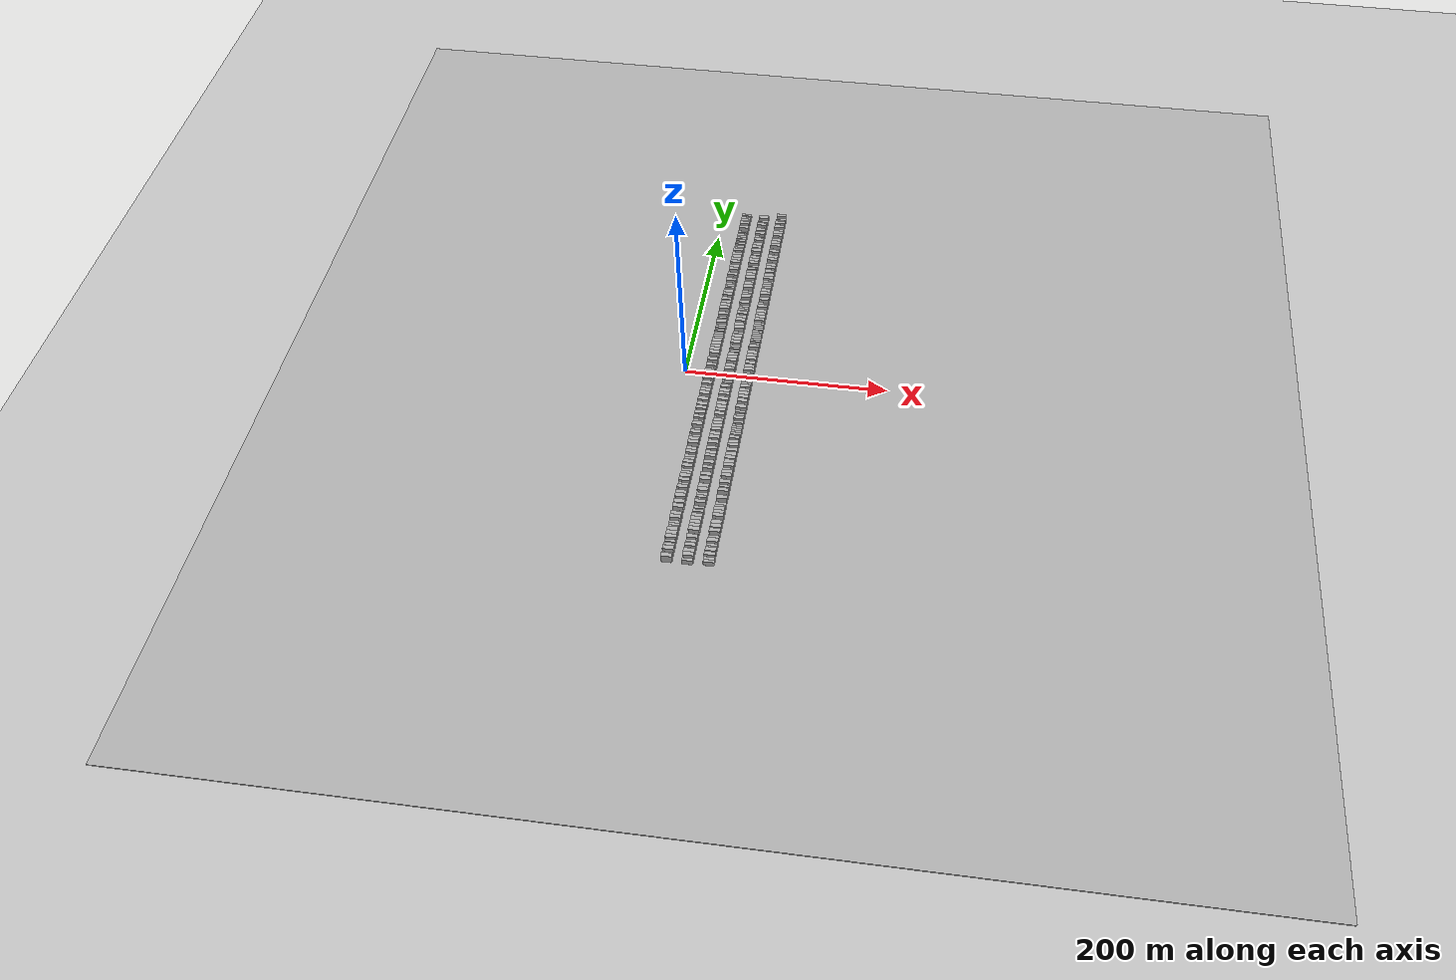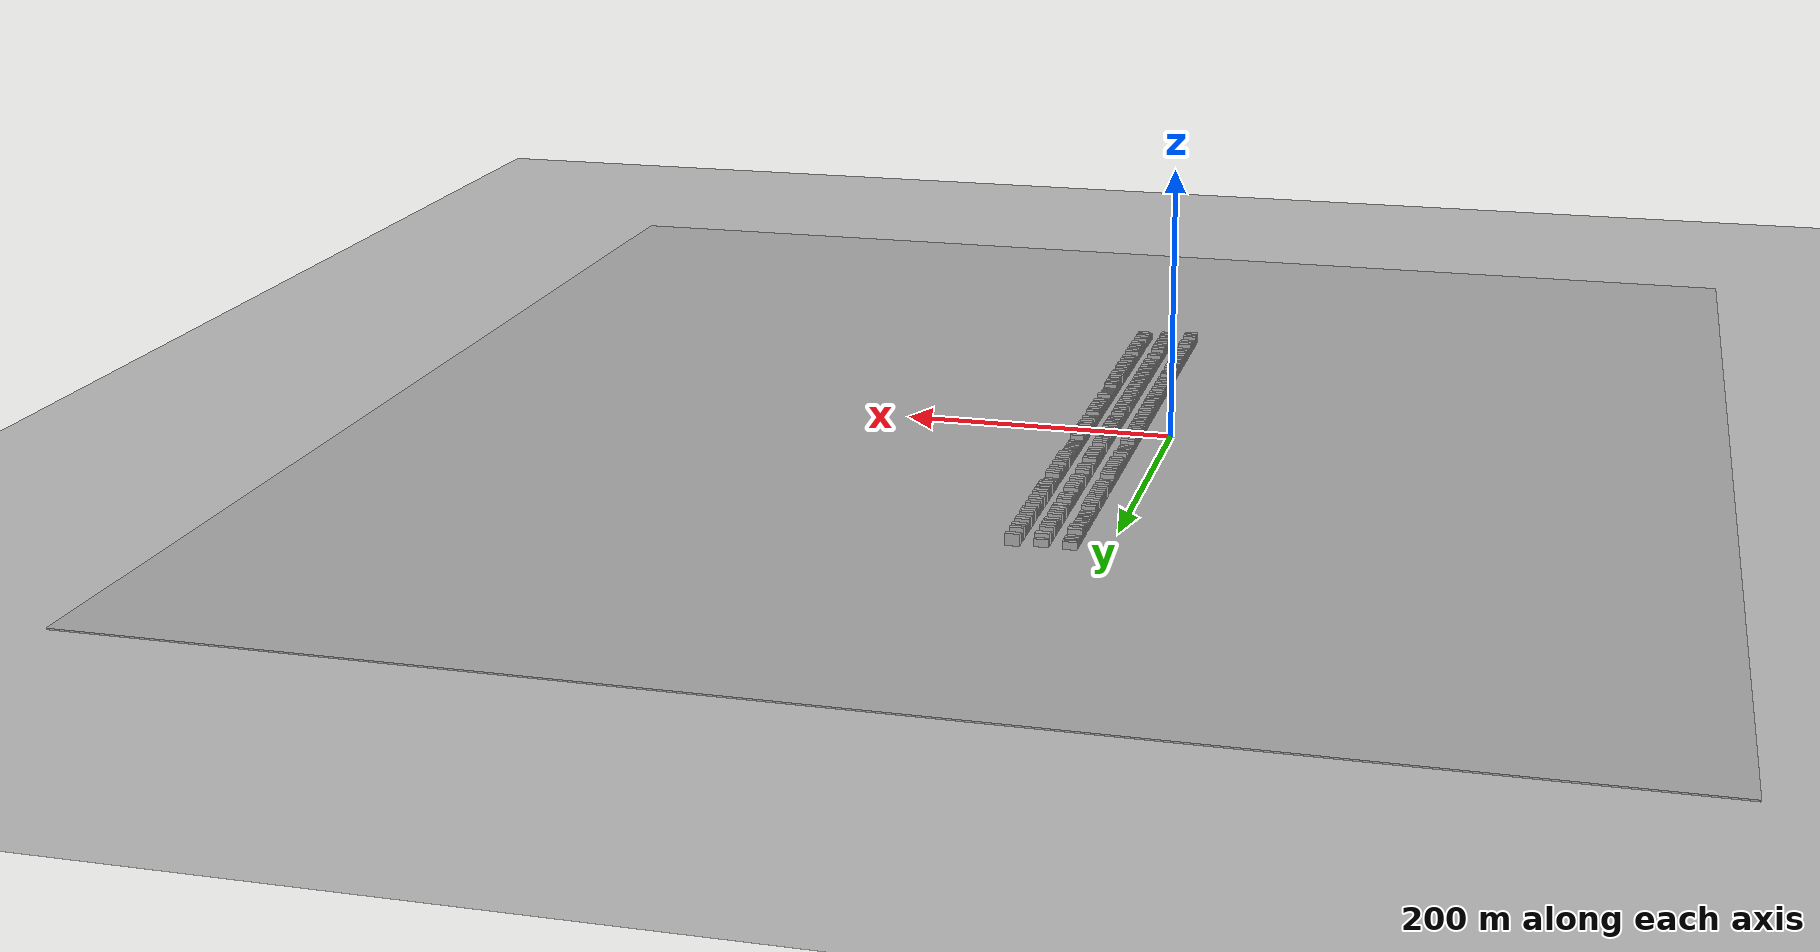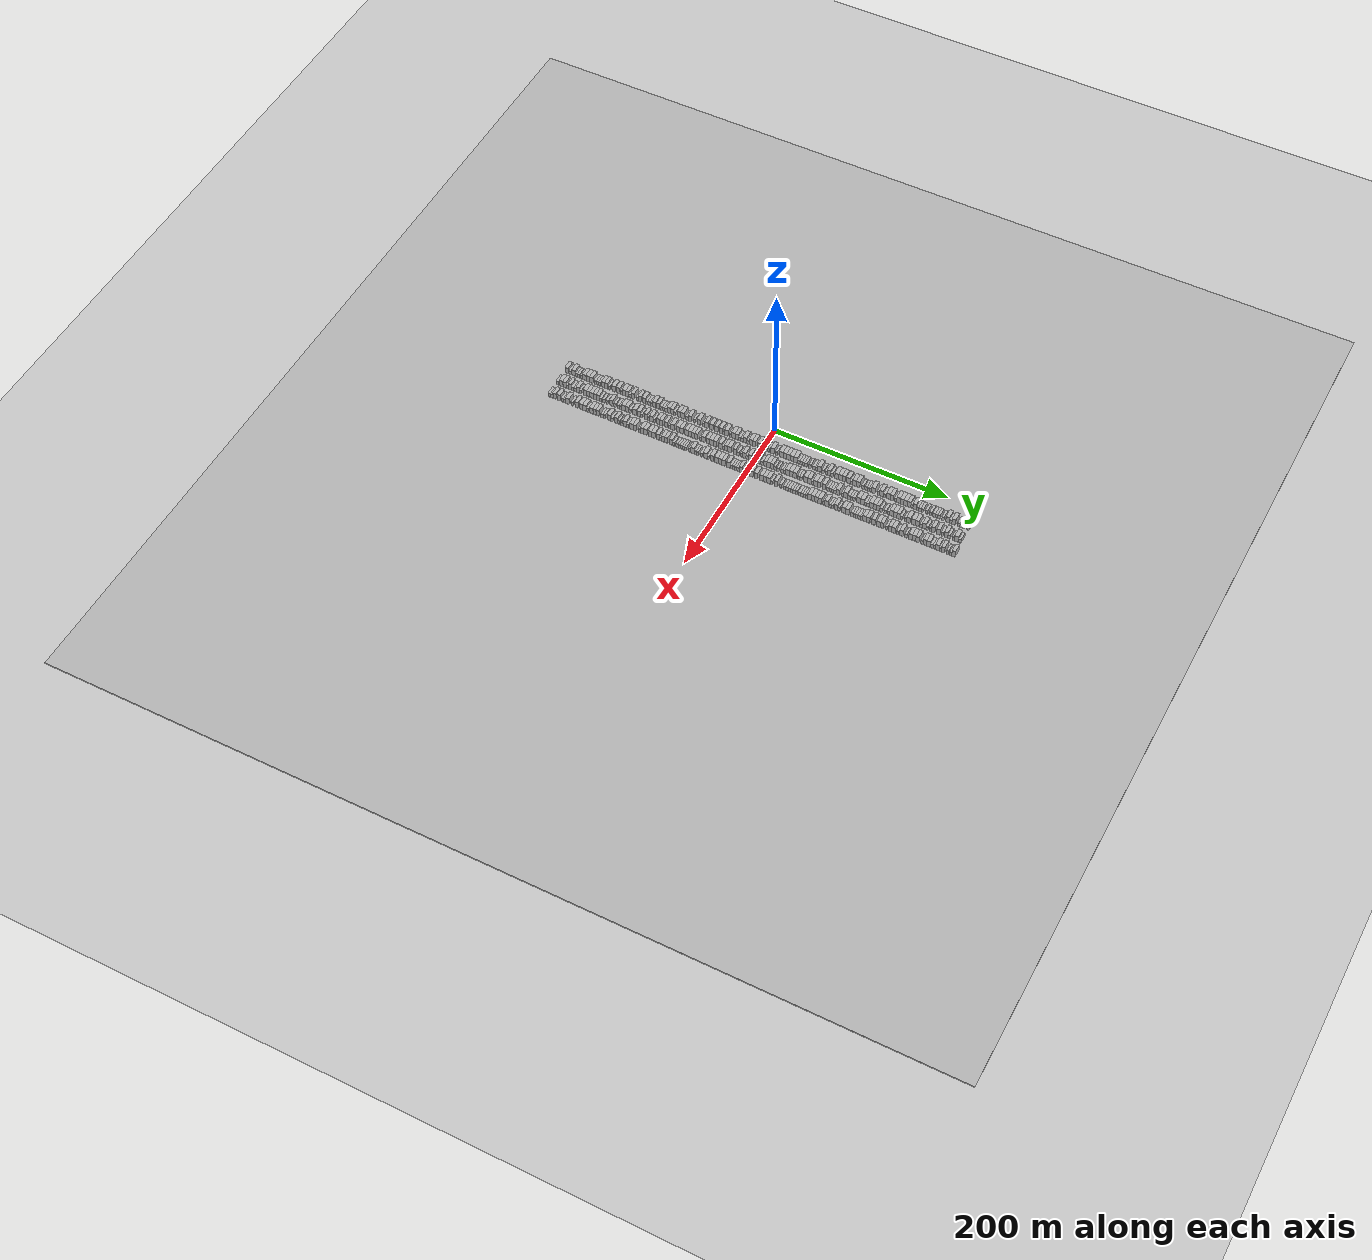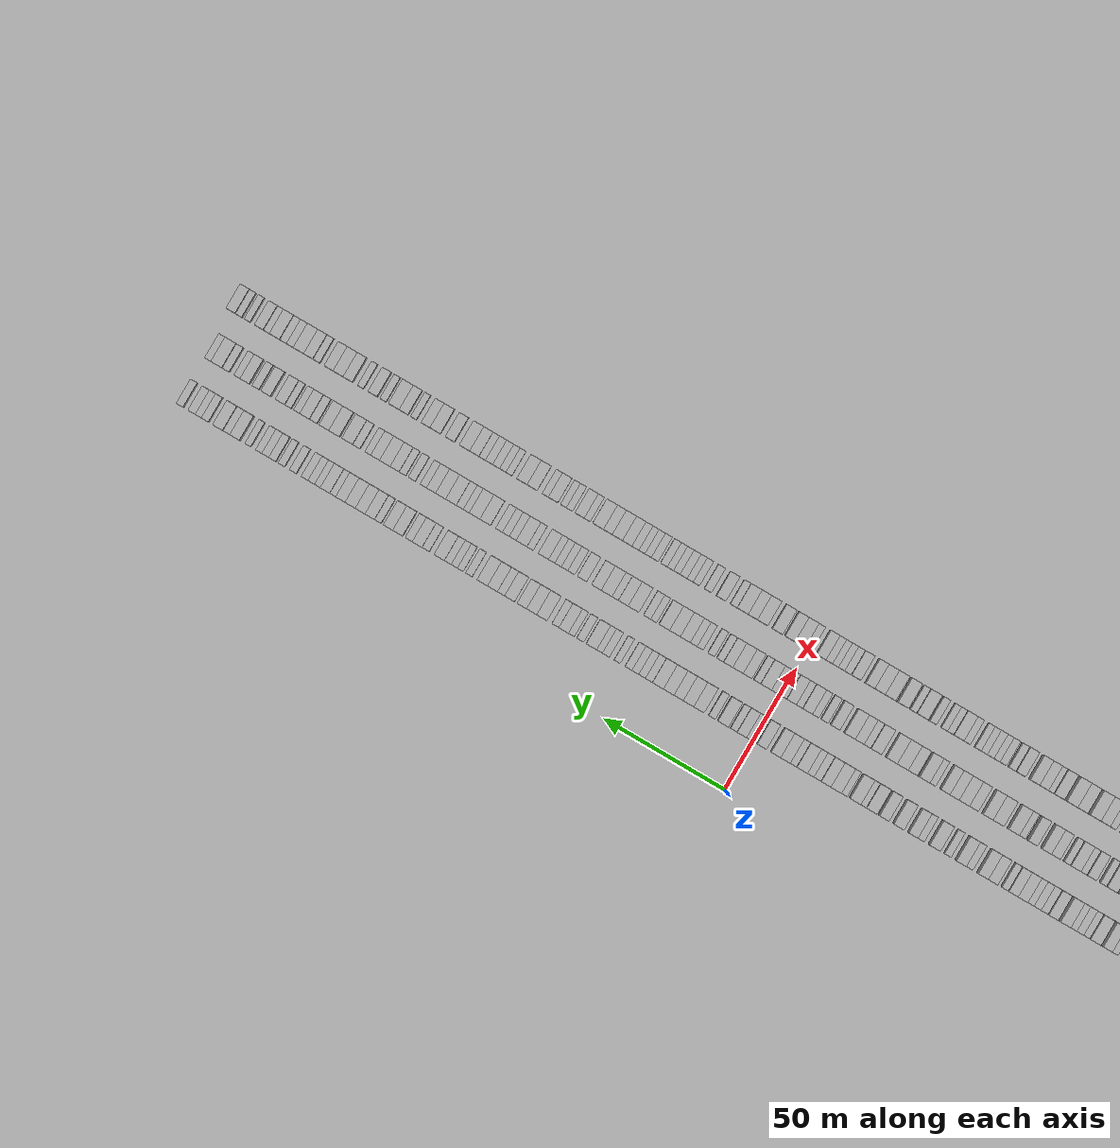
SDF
<?xml version="1.0" encoding="utf-8"?>

<sdf version="1.6">

   <world name="default">

      <gui fullscreen="0">

         <camera name="user_camera">

            <pose>-15 0 4.57585 0 0 0</pose>

            <view_controller>orbit</view_controller>

         </camera>

      </gui>

      <scene>

         <sky>

           <clouds>

             <speed>12</speed>

           </clouds>

         </sky>

         <ambient>0.4 0.4 0.4 1</ambient>

         <background>0.7 0.7 0.7 1</background>

         <shadows>1</shadows>

      </scene>

      <gravity>0 0 -9.8066</gravity>

      <magnetic_field>6e-06 2.3e-05 -4.2e-05</magnetic_field>

      <physics default="0" name="default_physics" type="ode">

         <ode>

            <solver>

               <type>quick</type>

               <iters>10</iters>

               <sor>1.0</sor>

               <use_dynamic_moi_rescaling>0</use_dynamic_moi_rescaling>

            </solver>

            <constraints>

               <cfm>0</cfm>

               <erp>0.2</erp>

               <contact_max_correcting_vel>100</contact_max_correcting_vel>

               <contact_surface_layer>0.001</contact_surface_layer>

            </constraints>

         </ode>

         <max_step_size>0.004</max_step_size>

         <real_time_factor>1</real_time_factor>

         <real_time_update_rate>250</real_time_update_rate>

      </physics>

      <light name="sun" type="directional">

         <cast_shadows>1</cast_shadows>

         <pose>0 0 10 0 0 0</pose>

         <diffuse>0.8 0.8 0.8 1</diffuse>

         <specular>0.2 0.2 0.2 1</specular>

         <attenuation>

            <range>1000</range>

            <constant>0.9</constant>

            <linear>0.01</linear>

            <quadratic>0.001</quadratic>

         </attenuation>

         <direction>-0.5 0.1 -0.9</direction>

      </light>

      <include>

         <name>ground_plane_1</name>

         <uri>model://HANNAS_ground_plane</uri>

         <pose>0 0 0  0 0 0</pose>

      </include>

      <include>

         <name>ground_plane_2</name>

         <uri>model://HANNAS_ground_plane</uri>

         <pose>100 0 0  0 0 0</pose>

      </include>

      <model name="building_1">

         <static>1</static>

         <pose frame="">25.0000 -233.8101 0 0.000000 0.000000 0.000000</pose>

         <link name="link">

            <pose frame="">0 0 4.50 0 0 0</pose>

            <collision name="collision">

               <geometry>

                  <box>

                     <size>10.0000 4.3798 9.0000</size>

                  </box>

               </geometry>

               <max_contacts>10</max_contacts>

               <surface>

                  <contact>

                     <ode/>

                  </contact>

                  <bounce/>

                  <friction>

                     <torsional>

                        <ode/>

                     </torsional>

                     <ode/>

                  </friction>

               </surface>

            </collision>

            <visual name="visual">

               <cast_shadows>0</cast_shadows>

               <geometry>

                  <box>

                     <size>10.0000 4.3798 9.0000</size>

                  </box>

               </geometry>

               <material>

                  <script>

                     <uri>model://HANNAS_wall/materials/scripts</uri>

                     <uri>model://HANNAS_wall/materials/textures</uri>

                     <name>vrc/HANNAS_wall</name>

                  </script>

               </material>

            </visual>

            <self_collide>0</self_collide>

            <enable_wind>0</enable_wind>

            <kinematic>0</kinematic>

         </link>

      </model>

      <model name="building_2">

         <static>1</static>

         <pose frame="">25.0000 -230.1904 0 0.000000 0.000000 0.000000</pose>

         <link name="link">

            <pose frame="">0 0 3.00 0 0 0</pose>

            <collision name="collision">

               <geometry>

                  <box>

                     <size>10.0000 2.8597 6.0000</size>

                  </box>

               </geometry>

               <max_contacts>10</max_contacts>

               <surface>

                  <contact>

                     <ode/>

                  </contact>

                  <bounce/>

                  <friction>

                     <torsional>

                        <ode/>

                     </torsional>

                     <ode/>

                  </friction>

               </surface>

            </collision>

            <visual name="visual">

               <cast_shadows>0</cast_shadows>

               <geometry>

                  <box>

                     <size>10.0000 2.8597 6.0000</size>

                  </box>

               </geometry>

               <material>

                  <script>

                     <uri>model://HANNAS_wall/materials/scripts</uri>

                     <uri>model://HANNAS_wall/materials/textures</uri>

                     <name>vrc/HANNAS_wall</name>

                  </script>

               </material>

            </visual>

            <self_collide>0</self_collide>

            <enable_wind>0</enable_wind>

            <kinematic>0</kinematic>

         </link>

      </model>

      <model name="building_3">

         <static>1</static>

         <pose frame="">25.0000 -225.5455 0 0.000000 0.000000 0.000000</pose>

         <link name="link">

            <pose frame="">0 0 4.50 0 0 0</pose>

            <collision name="collision">

               <geometry>

                  <box>

                     <size>10.0000 4.4301 9.0000</size>

                  </box>

               </geometry>

               <max_contacts>10</max_contacts>

               <surface>

                  <contact>

                     <ode/>

                  </contact>

                  <bounce/>

                  <friction>

                     <torsional>

                        <ode/>

                     </torsional>

                     <ode/>

                  </friction>

               </surface>

            </collision>

            <visual name="visual">

               <cast_shadows>0</cast_shadows>

               <geometry>

                  <box>

                     <size>10.0000 4.4301 9.0000</size>

                  </box>

               </geometry>

               <material>

                  <script>

                     <uri>model://HANNAS_wall/materials/scripts</uri>

                     <uri>model://HANNAS_wall/materials/textures</uri>

                     <name>vrc/HANNAS_wall</name>

                  </script>

               </material>

            </visual>

            <self_collide>0</self_collide>

            <enable_wind>0</enable_wind>

            <kinematic>0</kinematic>

         </link>

      </model>

      <model name="building_4">

         <static>1</static>

         <pose frame="">25.0000 -222.1152 0 0.000000 0.000000 0.000000</pose>

         <link name="link">

            <pose frame="">0 0 3.00 0 0 0</pose>

            <collision name="collision">

               <geometry>

                  <box>

                     <size>10.0000 2.4304 6.0000</size>

                  </box>

               </geometry>

               <max_contacts>10</max_contacts>

               <surface>

                  <contact>

                     <ode/>

                  </contact>

                  <bounce/>

                  <friction>

                     <torsional>

                        <ode/>

                     </torsional>

                     <ode/>

                  </friction>

               </surface>

            </collision>

            <visual name="visual">

               <cast_shadows>0</cast_shadows>

               <geometry>

                  <box>

                     <size>10.0000 2.4304 6.0000</size>

                  </box>

               </geometry>

               <material>

                  <script>

                     <uri>model://HANNAS_wall/materials/scripts</uri>

                     <uri>model://HANNAS_wall/materials/textures</uri>

                     <name>vrc/HANNAS_wall</name>

                  </script>

               </material>

            </visual>

            <self_collide>0</self_collide>

            <enable_wind>0</enable_wind>

            <kinematic>0</kinematic>

         </link>

      </model>

      <model name="building_5">

         <static>1</static>

         <pose frame="">25.0000 -219.4373 0 0.000000 0.000000 0.000000</pose>

         <link name="link">

            <pose frame="">0 0 3.00 0 0 0</pose>

            <collision name="collision">

               <geometry>

                  <box>

                     <size>10.0000 2.9253 6.0000</size>

                  </box>

               </geometry>

               <max_contacts>10</max_contacts>

               <surface>

                  <contact>

                     <ode/>

                  </contact>

                  <bounce/>

                  <friction>

                     <torsional>

                        <ode/>

                     </torsional>

                     <ode/>

                  </friction>

               </surface>

            </collision>

            <visual name="visual">

               <cast_shadows>0</cast_shadows>

               <geometry>

                  <box>

                     <size>10.0000 2.9253 6.0000</size>

                  </box>

               </geometry>

               <material>

                  <script>

                     <uri>model://HANNAS_wall/materials/scripts</uri>

                     <uri>model://HANNAS_wall/materials/textures</uri>

                     <name>vrc/HANNAS_wall</name>

                  </script>

               </material>

            </visual>

            <self_collide>0</self_collide>

            <enable_wind>0</enable_wind>

            <kinematic>0</kinematic>

         </link>

      </model>

      <model name="building_6">

         <static>1</static>

         <pose frame="">25.0000 -215.6372 0 0.000000 0.000000 0.000000</pose>

         <link name="link">

            <pose frame="">0 0 3.00 0 0 0</pose>

            <collision name="collision">

               <geometry>

                  <box>

                     <size>10.0000 2.6748 6.0000</size>

                  </box>

               </geometry>

               <max_contacts>10</max_contacts>

               <surface>

                  <contact>

                     <ode/>

                  </contact>

                  <bounce/>

                  <friction>

                     <torsional>

                        <ode/>

                     </torsional>

                     <ode/>

                  </friction>

               </surface>

            </collision>

            <visual name="visual">

               <cast_shadows>0</cast_shadows>

               <geometry>

                  <box>

                     <size>10.0000 2.6748 6.0000</size>

                  </box>

               </geometry>

               <material>

                  <script>

                     <uri>model://HANNAS_wall/materials/scripts</uri>

                     <uri>model://HANNAS_wall/materials/textures</uri>

                     <name>vrc/HANNAS_wall</name>

                  </script>

               </material>

            </visual>

            <self_collide>0</self_collide>

            <enable_wind>0</enable_wind>

            <kinematic>0</kinematic>

         </link>

      </model>

      <model name="building_7">

         <static>1</static>

         <pose frame="">25.0000 -212.3114 0 0.000000 0.000000 0.000000</pose>

         <link name="link">

            <pose frame="">0 0 4.50 0 0 0</pose>

            <collision name="collision">

               <geometry>

                  <box>

                     <size>10.0000 3.9768 9.0000</size>

                  </box>

               </geometry>

               <max_contacts>10</max_contacts>

               <surface>

                  <contact>

                     <ode/>

                  </contact>

                  <bounce/>

                  <friction>

                     <torsional>

                        <ode/>

                     </torsional>

                     <ode/>

                  </friction>

               </surface>

            </collision>

            <visual name="visual">

               <cast_shadows>0</cast_shadows>

               <geometry>

                  <box>

                     <size>10.0000 3.9768 9.0000</size>

                  </box>

               </geometry>

               <material>

                  <script>

                     <uri>model://HANNAS_wall/materials/scripts</uri>

                     <uri>model://HANNAS_wall/materials/textures</uri>

                     <name>vrc/HANNAS_wall</name>

                  </script>

               </material>

            </visual>

            <self_collide>0</self_collide>

            <enable_wind>0</enable_wind>

            <kinematic>0</kinematic>

         </link>

      </model>

      <model name="building_8">

         <static>1</static>

         <pose frame="">25.0000 -208.1650 0 0.000000 0.000000 0.000000</pose>

         <link name="link">

            <pose frame="">0 0 4.50 0 0 0</pose>

            <collision name="collision">

               <geometry>

                  <box>

                     <size>10.0000 4.3161 9.0000</size>

                  </box>

               </geometry>

               <max_contacts>10</max_contacts>

               <surface>

                  <contact>

                     <ode/>

                  </contact>

                  <bounce/>

                  <friction>

                     <torsional>

                        <ode/>

                     </torsional>

                     <ode/>

                  </friction>

               </surface>

            </collision>

            <visual name="visual">

               <cast_shadows>0</cast_shadows>

               <geometry>

                  <box>

                     <size>10.0000 4.3161 9.0000</size>

                  </box>

               </geometry>

               <material>

                  <script>

                     <uri>model://HANNAS_wall/materials/scripts</uri>

                     <uri>model://HANNAS_wall/materials/textures</uri>

                     <name>vrc/HANNAS_wall</name>

                  </script>

               </material>

            </visual>

            <self_collide>0</self_collide>

            <enable_wind>0</enable_wind>

            <kinematic>0</kinematic>

         </link>

      </model>

      <model name="building_9">

         <static>1</static>

         <pose frame="">25.0000 -203.8633 0 0.000000 0.000000 0.000000</pose>

         <link name="link">

            <pose frame="">0 0 4.50 0 0 0</pose>

            <collision name="collision">

               <geometry>

                  <box>

                     <size>10.0000 4.2874 9.0000</size>

                  </box>

               </geometry>

               <max_contacts>10</max_contacts>

               <surface>

                  <contact>

                     <ode/>

                  </contact>

                  <bounce/>

                  <friction>

                     <torsional>

                        <ode/>

                     </torsional>

                     <ode/>

                  </friction>

               </surface>

            </collision>

            <visual name="visual">

               <cast_shadows>0</cast_shadows>

               <geometry>

                  <box>

                     <size>10.0000 4.2874 9.0000</size>

                  </box>

               </geometry>

               <material>

                  <script>

                     <uri>model://HANNAS_wall/materials/scripts</uri>

                     <uri>model://HANNAS_wall/materials/textures</uri>

                     <name>vrc/HANNAS_wall</name>

                  </script>

               </material>

            </visual>

            <self_collide>0</self_collide>

            <enable_wind>0</enable_wind>

            <kinematic>0</kinematic>

         </link>

      </model>

      <model name="building_10">

         <static>1</static>

         <pose frame="">25.0000 -199.2689 0 0.000000 0.000000 0.000000</pose>

         <link name="link">

            <pose frame="">0 0 3.00 0 0 0</pose>

            <collision name="collision">

               <geometry>

                  <box>

                     <size>10.0000 2.9013 6.0000</size>

                  </box>

               </geometry>

               <max_contacts>10</max_contacts>

               <surface>

                  <contact>

                     <ode/>

                  </contact>

                  <bounce/>

                  <friction>

                     <torsional>

                        <ode/>

                     </torsional>

                     <ode/>

                  </friction>

               </surface>

            </collision>

            <visual name="visual">

               <cast_shadows>0</cast_shadows>

               <geometry>

                  <box>

                     <size>10.0000 2.9013 6.0000</size>

                  </box>

               </geometry>

               <material>

                  <script>

                     <uri>model://HANNAS_wall/materials/scripts</uri>

                     <uri>model://HANNAS_wall/materials/textures</uri>

                     <name>vrc/HANNAS_wall</name>

                  </script>

               </material>

            </visual>

            <self_collide>0</self_collide>

            <enable_wind>0</enable_wind>

            <kinematic>0</kinematic>

         </link>

      </model>

      <model name="building_11">

         <static>1</static>

         <pose frame="">25.0000 -196.5179 0 0.000000 0.000000 0.000000</pose>

         <link name="link">

            <pose frame="">0 0 3.00 0 0 0</pose>

            <collision name="collision">

               <geometry>

                  <box>

                     <size>10.0000 2.6006 6.0000</size>

                  </box>

               </geometry>

               <max_contacts>10</max_contacts>

               <surface>

                  <contact>

                     <ode/>

                  </contact>

                  <bounce/>

                  <friction>

                     <torsional>

                        <ode/>

                     </torsional>

                     <ode/>

                  </friction>

               </surface>

            </collision>

            <visual name="visual">

               <cast_shadows>0</cast_shadows>

               <geometry>

                  <box>

                     <size>10.0000 2.6006 6.0000</size>

                  </box>

               </geometry>

               <material>

                  <script>

                     <uri>model://HANNAS_wall/materials/scripts</uri>

                     <uri>model://HANNAS_wall/materials/textures</uri>

                     <name>vrc/HANNAS_wall</name>

                  </script>

               </material>

            </visual>

            <self_collide>0</self_collide>

            <enable_wind>0</enable_wind>

            <kinematic>0</kinematic>

         </link>

      </model>

      <model name="building_12">

         <static>1</static>

         <pose frame="">25.0000 -193.8118 0 0.000000 0.000000 0.000000</pose>

         <link name="link">

            <pose frame="">0 0 3.00 0 0 0</pose>

            <collision name="collision">

               <geometry>

                  <box>

                     <size>10.0000 2.8117 6.0000</size>

                  </box>

               </geometry>

               <max_contacts>10</max_contacts>

               <surface>

                  <contact>

                     <ode/>

                  </contact>

                  <bounce/>

                  <friction>

                     <torsional>

                        <ode/>

                     </torsional>

                     <ode/>

                  </friction>

               </surface>

            </collision>

            <visual name="visual">

               <cast_shadows>0</cast_shadows>

               <geometry>

                  <box>

                     <size>10.0000 2.8117 6.0000</size>

                  </box>

               </geometry>

               <material>

                  <script>

                     <uri>model://HANNAS_wall/materials/scripts</uri>

                     <uri>model://HANNAS_wall/materials/textures</uri>

                     <name>vrc/HANNAS_wall</name>

                  </script>

               </material>

            </visual>

            <self_collide>0</self_collide>

            <enable_wind>0</enable_wind>

            <kinematic>0</kinematic>

         </link>

      </model>

      <model name="building_13">

         <static>1</static>

         <pose frame="">25.0000 -189.4417 0 0.000000 0.000000 0.000000</pose>

         <link name="link">

            <pose frame="">0 0 4.50 0 0 0</pose>

            <collision name="collision">

               <geometry>

                  <box>

                     <size>10.0000 3.9283 9.0000</size>

                  </box>

               </geometry>

               <max_contacts>10</max_contacts>

               <surface>

                  <contact>

                     <ode/>

                  </contact>

                  <bounce/>

                  <friction>

                     <torsional>

                        <ode/>

                     </torsional>

                     <ode/>

                  </friction>

               </surface>

            </collision>

            <visual name="visual">

               <cast_shadows>0</cast_shadows>

               <geometry>

                  <box>

                     <size>10.0000 3.9283 9.0000</size>

                  </box>

               </geometry>

               <material>

                  <script>

                     <uri>model://HANNAS_wall/materials/scripts</uri>

                     <uri>model://HANNAS_wall/materials/textures</uri>

                     <name>vrc/HANNAS_wall</name>

                  </script>

               </material>

            </visual>

            <self_collide>0</self_collide>

            <enable_wind>0</enable_wind>

            <kinematic>0</kinematic>

         </link>

      </model>

      <model name="building_14">

         <static>1</static>

         <pose frame="">25.0000 -185.5741 0 0.000000 0.000000 0.000000</pose>

         <link name="link">

            <pose frame="">0 0 4.50 0 0 0</pose>

            <collision name="collision">

               <geometry>

                  <box>

                     <size>10.0000 3.8069 9.0000</size>

                  </box>

               </geometry>

               <max_contacts>10</max_contacts>

               <surface>

                  <contact>

                     <ode/>

                  </contact>

                  <bounce/>

                  <friction>

                     <torsional>

                        <ode/>

                     </torsional>

                     <ode/>

                  </friction>

               </surface>

            </collision>

            <visual name="visual">

               <cast_shadows>0</cast_shadows>

               <geometry>

                  <box>

                     <size>10.0000 3.8069 9.0000</size>

                  </box>

               </geometry>

               <material>

                  <script>

                     <uri>model://HANNAS_wall/materials/scripts</uri>

                     <uri>model://HANNAS_wall/materials/textures</uri>

                     <name>vrc/HANNAS_wall</name>

                  </script>

               </material>

            </visual>

            <self_collide>0</self_collide>

            <enable_wind>0</enable_wind>

            <kinematic>0</kinematic>

         </link>

      </model>

      <model name="building_15">

         <static>1</static>

         <pose frame="">25.0000 -182.2556 0 0.000000 0.000000 0.000000</pose>

         <link name="link">

            <pose frame="">0 0 3.00 0 0 0</pose>

            <collision name="collision">

               <geometry>

                  <box>

                     <size>10.0000 2.8301 6.0000</size>

                  </box>

               </geometry>

               <max_contacts>10</max_contacts>

               <surface>

                  <contact>

                     <ode/>

                  </contact>

                  <bounce/>

                  <friction>

                     <torsional>

                        <ode/>

                     </torsional>

                     <ode/>

                  </friction>

               </surface>

            </collision>

            <visual name="visual">

               <cast_shadows>0</cast_shadows>

               <geometry>

                  <box>

                     <size>10.0000 2.8301 6.0000</size>

                  </box>

               </geometry>

               <material>

                  <script>

                     <uri>model://HANNAS_wall/materials/scripts</uri>

                     <uri>model://HANNAS_wall/materials/textures</uri>

                     <name>vrc/HANNAS_wall</name>

                  </script>

               </material>

            </visual>

            <self_collide>0</self_collide>

            <enable_wind>0</enable_wind>

            <kinematic>0</kinematic>

         </link>

      </model>

      <model name="building_16">

         <static>1</static>

         <pose frame="">25.0000 -176.6451 0 0.000000 0.000000 0.000000</pose>

         <link name="link">

            <pose frame="">0 0 4.50 0 0 0</pose>

            <collision name="collision">

               <geometry>

                  <box>

                     <size>10.0000 4.3909 9.0000</size>

                  </box>

               </geometry>

               <max_contacts>10</max_contacts>

               <surface>

                  <contact>

                     <ode/>

                  </contact>

                  <bounce/>

                  <friction>

                     <torsional>

                        <ode/>

                     </torsional>

                     <ode/>

                  </friction>

               </surface>

            </collision>

            <visual name="visual">

               <cast_shadows>0</cast_shadows>

               <geometry>

                  <box>

                     <size>10.0000 4.3909 9.0000</size>

                  </box>

               </geometry>

               <material>

                  <script>

                     <uri>model://HANNAS_wall/materials/scripts</uri>

                     <uri>model://HANNAS_wall/materials/textures</uri>

                     <name>vrc/HANNAS_wall</name>

                  </script>

               </material>

            </visual>

            <self_collide>0</self_collide>

            <enable_wind>0</enable_wind>

            <kinematic>0</kinematic>

         </link>

      </model>

      <model name="building_17">

         <static>1</static>

         <pose frame="">25.0000 -171.2422 0 0.000000 0.000000 0.000000</pose>

         <link name="link">

            <pose frame="">0 0 4.50 0 0 0</pose>

            <collision name="collision">

               <geometry>

                  <box>

                     <size>10.0000 4.4151 9.0000</size>

                  </box>

               </geometry>

               <max_contacts>10</max_contacts>

               <surface>

                  <contact>

                     <ode/>

                  </contact>

                  <bounce/>

                  <friction>

                     <torsional>

                        <ode/>

                     </torsional>

                     <ode/>

                  </friction>

               </surface>

            </collision>

            <visual name="visual">

               <cast_shadows>0</cast_shadows>

               <geometry>

                  <box>

                     <size>10.0000 4.4151 9.0000</size>

                  </box>

               </geometry>

               <material>

                  <script>

                     <uri>model://HANNAS_wall/materials/scripts</uri>

                     <uri>model://HANNAS_wall/materials/textures</uri>

                     <name>vrc/HANNAS_wall</name>

                  </script>

               </material>

            </visual>

            <self_collide>0</self_collide>

            <enable_wind>0</enable_wind>

            <kinematic>0</kinematic>

         </link>

      </model>

      <model name="building_18">

         <static>1</static>

         <pose frame="">25.0000 -167.6906 0 0.000000 0.000000 0.000000</pose>

         <link name="link">

            <pose frame="">0 0 3.00 0 0 0</pose>

            <collision name="collision">

               <geometry>

                  <box>

                     <size>10.0000 2.6881 6.0000</size>

                  </box>

               </geometry>

               <max_contacts>10</max_contacts>

               <surface>

                  <contact>

                     <ode/>

                  </contact>

                  <bounce/>

                  <friction>

                     <torsional>

                        <ode/>

                     </torsional>

                     <ode/>

                  </friction>

               </surface>

            </collision>

            <visual name="visual">

               <cast_shadows>0</cast_shadows>

               <geometry>

                  <box>

                     <size>10.0000 2.6881 6.0000</size>

                  </box>

               </geometry>

               <material>

                  <script>

                     <uri>model://HANNAS_wall/materials/scripts</uri>

                     <uri>model://HANNAS_wall/materials/textures</uri>

                     <name>vrc/HANNAS_wall</name>

                  </script>

               </material>

            </visual>

            <self_collide>0</self_collide>

            <enable_wind>0</enable_wind>

            <kinematic>0</kinematic>

         </link>

      </model>

      <model name="building_19">

         <static>1</static>

         <pose frame="">25.0000 -164.1504 0 0.000000 0.000000 0.000000</pose>

         <link name="link">

            <pose frame="">0 0 4.50 0 0 0</pose>

            <collision name="collision">

               <geometry>

                  <box>

                     <size>10.0000 4.3922 9.0000</size>

                  </box>

               </geometry>

               <max_contacts>10</max_contacts>

               <surface>

                  <contact>

                     <ode/>

                  </contact>

                  <bounce/>

                  <friction>

                     <torsional>

                        <ode/>

                     </torsional>

                     <ode/>

                  </friction>

               </surface>

            </collision>

            <visual name="visual">

               <cast_shadows>0</cast_shadows>

               <geometry>

                  <box>

                     <size>10.0000 4.3922 9.0000</size>

                  </box>

               </geometry>

               <material>

                  <script>

                     <uri>model://HANNAS_wall/materials/scripts</uri>

                     <uri>model://HANNAS_wall/materials/textures</uri>

                     <name>vrc/HANNAS_wall</name>

                  </script>

               </material>

            </visual>

            <self_collide>0</self_collide>

            <enable_wind>0</enable_wind>

            <kinematic>0</kinematic>

         </link>

      </model>

      <model name="building_20">

         <static>1</static>

         <pose frame="">25.0000 -160.0922 0 0.000000 0.000000 0.000000</pose>

         <link name="link">

            <pose frame="">0 0 4.50 0 0 0</pose>

            <collision name="collision">

               <geometry>

                  <box>

                     <size>10.0000 3.7243 9.0000</size>

                  </box>

               </geometry>

               <max_contacts>10</max_contacts>

               <surface>

                  <contact>

                     <ode/>

                  </contact>

                  <bounce/>

                  <friction>

                     <torsional>

                        <ode/>

                     </torsional>

                     <ode/>

                  </friction>

               </surface>

            </collision>

            <visual name="visual">

               <cast_shadows>0</cast_shadows>

               <geometry>

                  <box>

                     <size>10.0000 3.7243 9.0000</size>

                  </box>

               </geometry>

               <material>

                  <script>

                     <uri>model://HANNAS_wall/materials/scripts</uri>

                     <uri>model://HANNAS_wall/materials/textures</uri>

                     <name>vrc/HANNAS_wall</name>

                  </script>

               </material>

            </visual>

            <self_collide>0</self_collide>

            <enable_wind>0</enable_wind>

            <kinematic>0</kinematic>

         </link>

      </model>

      <model name="building_21">

         <static>1</static>

         <pose frame="">25.0000 -156.8335 0 0.000000 0.000000 0.000000</pose>

         <link name="link">

            <pose frame="">0 0 3.00 0 0 0</pose>

            <collision name="collision">

               <geometry>

                  <box>

                     <size>10.0000 2.7931 6.0000</size>

                  </box>

               </geometry>

               <max_contacts>10</max_contacts>

               <surface>

                  <contact>

                     <ode/>

                  </contact>

                  <bounce/>

                  <friction>

                     <torsional>

                        <ode/>

                     </torsional>

                     <ode/>

                  </friction>

               </surface>

            </collision>

            <visual name="visual">

               <cast_shadows>0</cast_shadows>

               <geometry>

                  <box>

                     <size>10.0000 2.7931 6.0000</size>

                  </box>

               </geometry>

               <material>

                  <script>

                     <uri>model://HANNAS_wall/materials/scripts</uri>

                     <uri>model://HANNAS_wall/materials/textures</uri>

                     <name>vrc/HANNAS_wall</name>

                  </script>

               </material>

            </visual>

            <self_collide>0</self_collide>

            <enable_wind>0</enable_wind>

            <kinematic>0</kinematic>

         </link>

      </model>

      <model name="building_22">

         <static>1</static>

         <pose frame="">25.0000 -153.5188 0 0.000000 0.000000 0.000000</pose>

         <link name="link">

            <pose frame="">0 0 4.50 0 0 0</pose>

            <collision name="collision">

               <geometry>

                  <box>

                     <size>10.0000 3.8362 9.0000</size>

                  </box>

               </geometry>

               <max_contacts>10</max_contacts>

               <surface>

                  <contact>

                     <ode/>

                  </contact>

                  <bounce/>

                  <friction>

                     <torsional>

                        <ode/>

                     </torsional>

                     <ode/>

                  </friction>

               </surface>

            </collision>

            <visual name="visual">

               <cast_shadows>0</cast_shadows>

               <geometry>

                  <box>

                     <size>10.0000 3.8362 9.0000</size>

                  </box>

               </geometry>

               <material>

                  <script>

                     <uri>model://HANNAS_wall/materials/scripts</uri>

                     <uri>model://HANNAS_wall/materials/textures</uri>

                     <name>vrc/HANNAS_wall</name>

                  </script>

               </material>

            </visual>

            <self_collide>0</self_collide>

            <enable_wind>0</enable_wind>

            <kinematic>0</kinematic>

         </link>

      </model>

      <model name="building_23">

         <static>1</static>

         <pose frame="">25.0000 -148.1975 0 0.000000 0.000000 0.000000</pose>

         <link name="link">

            <pose frame="">0 0 3.00 0 0 0</pose>

            <collision name="collision">

               <geometry>

                  <box>

                     <size>10.0000 2.8065 6.0000</size>

                  </box>

               </geometry>

               <max_contacts>10</max_contacts>

               <surface>

                  <contact>

                     <ode/>

                  </contact>

                  <bounce/>

                  <friction>

                     <torsional>

                        <ode/>

                     </torsional>

                     <ode/>

                  </friction>

               </surface>

            </collision>

            <visual name="visual">

               <cast_shadows>0</cast_shadows>

               <geometry>

                  <box>

                     <size>10.0000 2.8065 6.0000</size>

                  </box>

               </geometry>

               <material>

                  <script>

                     <uri>model://HANNAS_wall/materials/scripts</uri>

                     <uri>model://HANNAS_wall/materials/textures</uri>

                     <name>vrc/HANNAS_wall</name>

                  </script>

               </material>

            </visual>

            <self_collide>0</self_collide>

            <enable_wind>0</enable_wind>

            <kinematic>0</kinematic>

         </link>

      </model>

      <model name="building_24">

         <static>1</static>

         <pose frame="">25.0000 -144.9755 0 0.000000 0.000000 0.000000</pose>

         <link name="link">

            <pose frame="">0 0 4.50 0 0 0</pose>

            <collision name="collision">

               <geometry>

                  <box>

                     <size>10.0000 3.6374 9.0000</size>

                  </box>

               </geometry>

               <max_contacts>10</max_contacts>

               <surface>

                  <contact>

                     <ode/>

                  </contact>

                  <bounce/>

                  <friction>

                     <torsional>

                        <ode/>

                     </torsional>

                     <ode/>

                  </friction>

               </surface>

            </collision>

            <visual name="visual">

               <cast_shadows>0</cast_shadows>

               <geometry>

                  <box>

                     <size>10.0000 3.6374 9.0000</size>

                  </box>

               </geometry>

               <material>

                  <script>

                     <uri>model://HANNAS_wall/materials/scripts</uri>

                     <uri>model://HANNAS_wall/materials/textures</uri>

                     <name>vrc/HANNAS_wall</name>

                  </script>

               </material>

            </visual>

            <self_collide>0</self_collide>

            <enable_wind>0</enable_wind>

            <kinematic>0</kinematic>

         </link>

      </model>

      <model name="building_25">

         <static>1</static>

         <pose frame="">25.0000 -140.0256 0 0.000000 0.000000 0.000000</pose>

         <link name="link">

            <pose frame="">0 0 4.50 0 0 0</pose>

            <collision name="collision">

               <geometry>

                  <box>

                     <size>10.0000 4.2623 9.0000</size>

                  </box>

               </geometry>

               <max_contacts>10</max_contacts>

               <surface>

                  <contact>

                     <ode/>

                  </contact>

                  <bounce/>

                  <friction>

                     <torsional>

                        <ode/>

                     </torsional>

                     <ode/>

                  </friction>

               </surface>

            </collision>

            <visual name="visual">

               <cast_shadows>0</cast_shadows>

               <geometry>

                  <box>

                     <size>10.0000 4.2623 9.0000</size>

                  </box>

               </geometry>

               <material>

                  <script>

                     <uri>model://HANNAS_wall/materials/scripts</uri>

                     <uri>model://HANNAS_wall/materials/textures</uri>

                     <name>vrc/HANNAS_wall</name>

                  </script>

               </material>

            </visual>

            <self_collide>0</self_collide>

            <enable_wind>0</enable_wind>

            <kinematic>0</kinematic>

         </link>

      </model>

      <model name="building_26">

         <static>1</static>

         <pose frame="">25.0000 -136.6577 0 0.000000 0.000000 0.000000</pose>

         <link name="link">

            <pose frame="">0 0 3.00 0 0 0</pose>

            <collision name="collision">

               <geometry>

                  <box>

                     <size>10.0000 2.4735 6.0000</size>

                  </box>

               </geometry>

               <max_contacts>10</max_contacts>

               <surface>

                  <contact>

                     <ode/>

                  </contact>

                  <bounce/>

                  <friction>

                     <torsional>

                        <ode/>

                     </torsional>

                     <ode/>

                  </friction>

               </surface>

            </collision>

            <visual name="visual">

               <cast_shadows>0</cast_shadows>

               <geometry>

                  <box>

                     <size>10.0000 2.4735 6.0000</size>

                  </box>

               </geometry>

               <material>

                  <script>

                     <uri>model://HANNAS_wall/materials/scripts</uri>

                     <uri>model://HANNAS_wall/materials/textures</uri>

                     <name>vrc/HANNAS_wall</name>

                  </script>

               </material>

            </visual>

            <self_collide>0</self_collide>

            <enable_wind>0</enable_wind>

            <kinematic>0</kinematic>

         </link>

      </model>

      <model name="building_27">

         <static>1</static>

         <pose frame="">25.0000 -133.9958 0 0.000000 0.000000 0.000000</pose>

         <link name="link">

            <pose frame="">0 0 3.00 0 0 0</pose>

            <collision name="collision">

               <geometry>

                  <box>

                     <size>10.0000 2.8502 6.0000</size>

                  </box>

               </geometry>

               <max_contacts>10</max_contacts>

               <surface>

                  <contact>

                     <ode/>

                  </contact>

                  <bounce/>

                  <friction>

                     <torsional>

                        <ode/>

                     </torsional>

                     <ode/>

                  </friction>

               </surface>

            </collision>

            <visual name="visual">

               <cast_shadows>0</cast_shadows>

               <geometry>

                  <box>

                     <size>10.0000 2.8502 6.0000</size>

                  </box>

               </geometry>

               <material>

                  <script>

                     <uri>model://HANNAS_wall/materials/scripts</uri>

                     <uri>model://HANNAS_wall/materials/textures</uri>

                     <name>vrc/HANNAS_wall</name>

                  </script>

               </material>

            </visual>

            <self_collide>0</self_collide>

            <enable_wind>0</enable_wind>

            <kinematic>0</kinematic>

         </link>

      </model>

      <model name="building_28">

         <static>1</static>

         <pose frame="">25.0000 -131.1555 0 0.000000 0.000000 0.000000</pose>

         <link name="link">

            <pose frame="">0 0 3.00 0 0 0</pose>

            <collision name="collision">

               <geometry>

                  <box>

                     <size>10.0000 2.8305 6.0000</size>

                  </box>

               </geometry>

               <max_contacts>10</max_contacts>

               <surface>

                  <contact>

                     <ode/>

                  </contact>

                  <bounce/>

                  <friction>

                     <torsional>

                        <ode/>

                     </torsional>

                     <ode/>

                  </friction>

               </surface>

            </collision>

            <visual name="visual">

               <cast_shadows>0</cast_shadows>

               <geometry>

                  <box>

                     <size>10.0000 2.8305 6.0000</size>

                  </box>

               </geometry>

               <material>

                  <script>

                     <uri>model://HANNAS_wall/materials/scripts</uri>

                     <uri>model://HANNAS_wall/materials/textures</uri>

                     <name>vrc/HANNAS_wall</name>

                  </script>

               </material>

            </visual>

            <self_collide>0</self_collide>

            <enable_wind>0</enable_wind>

            <kinematic>0</kinematic>

         </link>

      </model>

      <model name="building_29">

         <static>1</static>

         <pose frame="">25.0000 -127.6747 0 0.000000 0.000000 0.000000</pose>

         <link name="link">

            <pose frame="">0 0 4.50 0 0 0</pose>

            <collision name="collision">

               <geometry>

                  <box>

                     <size>10.0000 4.1310 9.0000</size>

                  </box>

               </geometry>

               <max_contacts>10</max_contacts>

               <surface>

                  <contact>

                     <ode/>

                  </contact>

                  <bounce/>

                  <friction>

                     <torsional>

                        <ode/>

                     </torsional>

                     <ode/>

                  </friction>

               </surface>

            </collision>

            <visual name="visual">

               <cast_shadows>0</cast_shadows>

               <geometry>

                  <box>

                     <size>10.0000 4.1310 9.0000</size>

                  </box>

               </geometry>

               <material>

                  <script>

                     <uri>model://HANNAS_wall/materials/scripts</uri>

                     <uri>model://HANNAS_wall/materials/textures</uri>

                     <name>vrc/HANNAS_wall</name>

                  </script>

               </material>

            </visual>

            <self_collide>0</self_collide>

            <enable_wind>0</enable_wind>

            <kinematic>0</kinematic>

         </link>

      </model>

      <model name="building_30">

         <static>1</static>

         <pose frame="">25.0000 -122.6951 0 0.000000 0.000000 0.000000</pose>

         <link name="link">

            <pose frame="">0 0 4.50 0 0 0</pose>

            <collision name="collision">

               <geometry>

                  <box>

                     <size>10.0000 3.8283 9.0000</size>

                  </box>

               </geometry>

               <max_contacts>10</max_contacts>

               <surface>

                  <contact>

                     <ode/>

                  </contact>

                  <bounce/>

                  <friction>

                     <torsional>

                        <ode/>

                     </torsional>

                     <ode/>

                  </friction>

               </surface>

            </collision>

            <visual name="visual">

               <cast_shadows>0</cast_shadows>

               <geometry>

                  <box>

                     <size>10.0000 3.8283 9.0000</size>

                  </box>

               </geometry>

               <material>

                  <script>

                     <uri>model://HANNAS_wall/materials/scripts</uri>

                     <uri>model://HANNAS_wall/materials/textures</uri>

                     <name>vrc/HANNAS_wall</name>

                  </script>

               </material>

            </visual>

            <self_collide>0</self_collide>

            <enable_wind>0</enable_wind>

            <kinematic>0</kinematic>

         </link>

      </model>

      <model name="building_31">

         <static>1</static>

         <pose frame="">25.0000 -119.3521 0 0.000000 0.000000 0.000000</pose>

         <link name="link">

            <pose frame="">0 0 3.00 0 0 0</pose>

            <collision name="collision">

               <geometry>

                  <box>

                     <size>10.0000 2.8576 6.0000</size>

                  </box>

               </geometry>

               <max_contacts>10</max_contacts>

               <surface>

                  <contact>

                     <ode/>

                  </contact>

                  <bounce/>

                  <friction>

                     <torsional>

                        <ode/>

                     </torsional>

                     <ode/>

                  </friction>

               </surface>

            </collision>

            <visual name="visual">

               <cast_shadows>0</cast_shadows>

               <geometry>

                  <box>

                     <size>10.0000 2.8576 6.0000</size>

                  </box>

               </geometry>

               <material>

                  <script>

                     <uri>model://HANNAS_wall/materials/scripts</uri>

                     <uri>model://HANNAS_wall/materials/textures</uri>

                     <name>vrc/HANNAS_wall</name>

                  </script>

               </material>

            </visual>

            <self_collide>0</self_collide>

            <enable_wind>0</enable_wind>

            <kinematic>0</kinematic>

         </link>

      </model>

      <model name="building_32">

         <static>1</static>

         <pose frame="">25.0000 -116.4563 0 0.000000 0.000000 0.000000</pose>

         <link name="link">

            <pose frame="">0 0 3.00 0 0 0</pose>

            <collision name="collision">

               <geometry>

                  <box>

                     <size>10.0000 2.9341 6.0000</size>

                  </box>

               </geometry>

               <max_contacts>10</max_contacts>

               <surface>

                  <contact>

                     <ode/>

                  </contact>

                  <bounce/>

                  <friction>

                     <torsional>

                        <ode/>

                     </torsional>

                     <ode/>

                  </friction>

               </surface>

            </collision>

            <visual name="visual">

               <cast_shadows>0</cast_shadows>

               <geometry>

                  <box>

                     <size>10.0000 2.9341 6.0000</size>

                  </box>

               </geometry>

               <material>

                  <script>

                     <uri>model://HANNAS_wall/materials/scripts</uri>

                     <uri>model://HANNAS_wall/materials/textures</uri>

                     <name>vrc/HANNAS_wall</name>

                  </script>

               </material>

            </visual>

            <self_collide>0</self_collide>

            <enable_wind>0</enable_wind>

            <kinematic>0</kinematic>

         </link>

      </model>

      <model name="building_33">

         <static>1</static>

         <pose frame="">25.0000 -113.5589 0 0.000000 0.000000 0.000000</pose>

         <link name="link">

            <pose frame="">0 0 3.00 0 0 0</pose>

            <collision name="collision">

               <geometry>

                  <box>

                     <size>10.0000 2.8606 6.0000</size>

                  </box>

               </geometry>

               <max_contacts>10</max_contacts>

               <surface>

                  <contact>

                     <ode/>

                  </contact>

                  <bounce/>

                  <friction>

                     <torsional>

                        <ode/>

                     </torsional>

                     <ode/>

                  </friction>

               </surface>

            </collision>

            <visual name="visual">

               <cast_shadows>0</cast_shadows>

               <geometry>

                  <box>

                     <size>10.0000 2.8606 6.0000</size>

                  </box>

               </geometry>

               <material>

                  <script>

                     <uri>model://HANNAS_wall/materials/scripts</uri>

                     <uri>model://HANNAS_wall/materials/textures</uri>

                     <name>vrc/HANNAS_wall</name>

                  </script>

               </material>

            </visual>

            <self_collide>0</self_collide>

            <enable_wind>0</enable_wind>

            <kinematic>0</kinematic>

         </link>

      </model>

      <model name="building_34">

         <static>1</static>

         <pose frame="">25.0000 -110.1387 0 0.000000 0.000000 0.000000</pose>

         <link name="link">

            <pose frame="">0 0 4.50 0 0 0</pose>

            <collision name="collision">

               <geometry>

                  <box>

                     <size>10.0000 3.9799 9.0000</size>

                  </box>

               </geometry>

               <max_contacts>10</max_contacts>

               <surface>

                  <contact>

                     <ode/>

                  </contact>

                  <bounce/>

                  <friction>

                     <torsional>

                        <ode/>

                     </torsional>

                     <ode/>

                  </friction>

               </surface>

            </collision>

            <visual name="visual">

               <cast_shadows>0</cast_shadows>

               <geometry>

                  <box>

                     <size>10.0000 3.9799 9.0000</size>

                  </box>

               </geometry>

               <material>

                  <script>

                     <uri>model://HANNAS_wall/materials/scripts</uri>

                     <uri>model://HANNAS_wall/materials/textures</uri>

                     <name>vrc/HANNAS_wall</name>

                  </script>

               </material>

            </visual>

            <self_collide>0</self_collide>

            <enable_wind>0</enable_wind>

            <kinematic>0</kinematic>

         </link>

      </model>

      <model name="building_35">

         <static>1</static>

         <pose frame="">25.0000 -106.2834 0 0.000000 0.000000 0.000000</pose>

         <link name="link">

            <pose frame="">0 0 4.50 0 0 0</pose>

            <collision name="collision">

               <geometry>

                  <box>

                     <size>10.0000 3.7308 9.0000</size>

                  </box>

               </geometry>

               <max_contacts>10</max_contacts>

               <surface>

                  <contact>

                     <ode/>

                  </contact>

                  <bounce/>

                  <friction>

                     <torsional>

                        <ode/>

                     </torsional>

                     <ode/>

                  </friction>

               </surface>

            </collision>

            <visual name="visual">

               <cast_shadows>0</cast_shadows>

               <geometry>

                  <box>

                     <size>10.0000 3.7308 9.0000</size>

                  </box>

               </geometry>

               <material>

                  <script>

                     <uri>model://HANNAS_wall/materials/scripts</uri>

                     <uri>model://HANNAS_wall/materials/textures</uri>

                     <name>vrc/HANNAS_wall</name>

                  </script>

               </material>

            </visual>

            <self_collide>0</self_collide>

            <enable_wind>0</enable_wind>

            <kinematic>0</kinematic>

         </link>

      </model>

      <model name="building_36">

         <static>1</static>

         <pose frame="">25.0000 -103.1273 0 0.000000 0.000000 0.000000</pose>

         <link name="link">

            <pose frame="">0 0 3.00 0 0 0</pose>

            <collision name="collision">

               <geometry>

                  <box>

                     <size>10.0000 2.5815 6.0000</size>

                  </box>

               </geometry>

               <max_contacts>10</max_contacts>

               <surface>

                  <contact>

                     <ode/>

                  </contact>

                  <bounce/>

                  <friction>

                     <torsional>

                        <ode/>

                     </torsional>

                     <ode/>

                  </friction>

               </surface>

            </collision>

            <visual name="visual">

               <cast_shadows>0</cast_shadows>

               <geometry>

                  <box>

                     <size>10.0000 2.5815 6.0000</size>

                  </box>

               </geometry>

               <material>

                  <script>

                     <uri>model://HANNAS_wall/materials/scripts</uri>

                     <uri>model://HANNAS_wall/materials/textures</uri>

                     <name>vrc/HANNAS_wall</name>

                  </script>

               </material>

            </visual>

            <self_collide>0</self_collide>

            <enable_wind>0</enable_wind>

            <kinematic>0</kinematic>

         </link>

      </model>

      <model name="building_37">

         <static>1</static>

         <pose frame="">25.0000 -97.8834 0 0.000000 0.000000 0.000000</pose>

         <link name="link">

            <pose frame="">0 0 4.50 0 0 0</pose>

            <collision name="collision">

               <geometry>

                  <box>

                     <size>10.0000 3.9064 9.0000</size>

                  </box>

               </geometry>

               <max_contacts>10</max_contacts>

               <surface>

                  <contact>

                     <ode/>

                  </contact>

                  <bounce/>

                  <friction>

                     <torsional>

                        <ode/>

                     </torsional>

                     <ode/>

                  </friction>

               </surface>

            </collision>

            <visual name="visual">

               <cast_shadows>0</cast_shadows>

               <geometry>

                  <box>

                     <size>10.0000 3.9064 9.0000</size>

                  </box>

               </geometry>

               <material>

                  <script>

                     <uri>model://HANNAS_wall/materials/scripts</uri>

                     <uri>model://HANNAS_wall/materials/textures</uri>

                     <name>vrc/HANNAS_wall</name>

                  </script>

               </material>

            </visual>

            <self_collide>0</self_collide>

            <enable_wind>0</enable_wind>

            <kinematic>0</kinematic>

         </link>

      </model>

      <model name="building_38">

         <static>1</static>

         <pose frame="">25.0000 -93.9067 0 0.000000 0.000000 0.000000</pose>

         <link name="link">

            <pose frame="">0 0 4.50 0 0 0</pose>

            <collision name="collision">

               <geometry>

                  <box>

                     <size>10.0000 4.0469 9.0000</size>

                  </box>

               </geometry>

               <max_contacts>10</max_contacts>

               <surface>

                  <contact>

                     <ode/>

                  </contact>

                  <bounce/>

                  <friction>

                     <torsional>

                        <ode/>

                     </torsional>

                     <ode/>

                  </friction>

               </surface>

            </collision>

            <visual name="visual">

               <cast_shadows>0</cast_shadows>

               <geometry>

                  <box>

                     <size>10.0000 4.0469 9.0000</size>

                  </box>

               </geometry>

               <material>

                  <script>

                     <uri>model://HANNAS_wall/materials/scripts</uri>

                     <uri>model://HANNAS_wall/materials/textures</uri>

                     <name>vrc/HANNAS_wall</name>

                  </script>

               </material>

            </visual>

            <self_collide>0</self_collide>

            <enable_wind>0</enable_wind>

            <kinematic>0</kinematic>

         </link>

      </model>

      <model name="building_39">

         <static>1</static>

         <pose frame="">25.0000 -88.3887 0 0.000000 0.000000 0.000000</pose>

         <link name="link">

            <pose frame="">0 0 3.00 0 0 0</pose>

            <collision name="collision">

               <geometry>

                  <box>

                     <size>10.0000 2.9891 6.0000</size>

                  </box>

               </geometry>

               <max_contacts>10</max_contacts>

               <surface>

                  <contact>

                     <ode/>

                  </contact>

                  <bounce/>

                  <friction>

                     <torsional>

                        <ode/>

                     </torsional>

                     <ode/>

                  </friction>

               </surface>

            </collision>

            <visual name="visual">

               <cast_shadows>0</cast_shadows>

               <geometry>

                  <box>

                     <size>10.0000 2.9891 6.0000</size>

                  </box>

               </geometry>

               <material>

                  <script>

                     <uri>model://HANNAS_wall/materials/scripts</uri>

                     <uri>model://HANNAS_wall/materials/textures</uri>

                     <name>vrc/HANNAS_wall</name>

                  </script>

               </material>

            </visual>

            <self_collide>0</self_collide>

            <enable_wind>0</enable_wind>

            <kinematic>0</kinematic>

         </link>

      </model>

      <model name="building_40">

         <static>1</static>

         <pose frame="">25.0000 -84.8901 0 0.000000 0.000000 0.000000</pose>

         <link name="link">

            <pose frame="">0 0 4.50 0 0 0</pose>

            <collision name="collision">

               <geometry>

                  <box>

                     <size>10.0000 4.0083 9.0000</size>

                  </box>

               </geometry>

               <max_contacts>10</max_contacts>

               <surface>

                  <contact>

                     <ode/>

                  </contact>

                  <bounce/>

                  <friction>

                     <torsional>

                        <ode/>

                     </torsional>

                     <ode/>

                  </friction>

               </surface>

            </collision>

            <visual name="visual">

               <cast_shadows>0</cast_shadows>

               <geometry>

                  <box>

                     <size>10.0000 4.0083 9.0000</size>

                  </box>

               </geometry>

               <material>

                  <script>

                     <uri>model://HANNAS_wall/materials/scripts</uri>

                     <uri>model://HANNAS_wall/materials/textures</uri>

                     <name>vrc/HANNAS_wall</name>

                  </script>

               </material>

            </visual>

            <self_collide>0</self_collide>

            <enable_wind>0</enable_wind>

            <kinematic>0</kinematic>

         </link>

      </model>

      <model name="building_41">

         <static>1</static>

         <pose frame="">25.0000 -79.5864 0 0.000000 0.000000 0.000000</pose>

         <link name="link">

            <pose frame="">0 0 3.00 0 0 0</pose>

            <collision name="collision">

               <geometry>

                  <box>

                     <size>10.0000 2.5991 6.0000</size>

                  </box>

               </geometry>

               <max_contacts>10</max_contacts>

               <surface>

                  <contact>

                     <ode/>

                  </contact>

                  <bounce/>

                  <friction>

                     <torsional>

                        <ode/>

                     </torsional>

                     <ode/>

                  </friction>

               </surface>

            </collision>

            <visual name="visual">

               <cast_shadows>0</cast_shadows>

               <geometry>

                  <box>

                     <size>10.0000 2.5991 6.0000</size>

                  </box>

               </geometry>

               <material>

                  <script>

                     <uri>model://HANNAS_wall/materials/scripts</uri>

                     <uri>model://HANNAS_wall/materials/textures</uri>

                     <name>vrc/HANNAS_wall</name>

                  </script>

               </material>

            </visual>

            <self_collide>0</self_collide>

            <enable_wind>0</enable_wind>

            <kinematic>0</kinematic>

         </link>

      </model>

      <model name="building_42">

         <static>1</static>

         <pose frame="">25.0000 -74.0940 0 0.000000 0.000000 0.000000</pose>

         <link name="link">

            <pose frame="">0 0 4.50 0 0 0</pose>

            <collision name="collision">

               <geometry>

                  <box>

                     <size>10.0000 4.3855 9.0000</size>

                  </box>

               </geometry>

               <max_contacts>10</max_contacts>

               <surface>

                  <contact>

                     <ode/>

                  </contact>

                  <bounce/>

                  <friction>

                     <torsional>

                        <ode/>

                     </torsional>

                     <ode/>

                  </friction>

               </surface>

            </collision>

            <visual name="visual">

               <cast_shadows>0</cast_shadows>

               <geometry>

                  <box>

                     <size>10.0000 4.3855 9.0000</size>

                  </box>

               </geometry>

               <material>

                  <script>

                     <uri>model://HANNAS_wall/materials/scripts</uri>

                     <uri>model://HANNAS_wall/materials/textures</uri>

                     <name>vrc/HANNAS_wall</name>

                  </script>

               </material>

            </visual>

            <self_collide>0</self_collide>

            <enable_wind>0</enable_wind>

            <kinematic>0</kinematic>

         </link>

      </model>

      <model name="building_43">

         <static>1</static>

         <pose frame="">25.0000 -68.4667 0 0.000000 0.000000 0.000000</pose>

         <link name="link">

            <pose frame="">0 0 3.00 0 0 0</pose>

            <collision name="collision">

               <geometry>

                  <box>

                     <size>10.0000 2.8691 6.0000</size>

                  </box>

               </geometry>

               <max_contacts>10</max_contacts>

               <surface>

                  <contact>

                     <ode/>

                  </contact>

                  <bounce/>

                  <friction>

                     <torsional>

                        <ode/>

                     </torsional>

                     <ode/>

                  </friction>

               </surface>

            </collision>

            <visual name="visual">

               <cast_shadows>0</cast_shadows>

               <geometry>

                  <box>

                     <size>10.0000 2.8691 6.0000</size>

                  </box>

               </geometry>

               <material>

                  <script>

                     <uri>model://HANNAS_wall/materials/scripts</uri>

                     <uri>model://HANNAS_wall/materials/textures</uri>

                     <name>vrc/HANNAS_wall</name>

                  </script>

               </material>

            </visual>

            <self_collide>0</self_collide>

            <enable_wind>0</enable_wind>

            <kinematic>0</kinematic>

         </link>

      </model>

      <model name="building_44">

         <static>1</static>

         <pose frame="">25.0000 -65.1917 0 0.000000 0.000000 0.000000</pose>

         <link name="link">

            <pose frame="">0 0 4.50 0 0 0</pose>

            <collision name="collision">

               <geometry>

                  <box>

                     <size>10.0000 3.6809 9.0000</size>

                  </box>

               </geometry>

               <max_contacts>10</max_contacts>

               <surface>

                  <contact>

                     <ode/>

                  </contact>

                  <bounce/>

                  <friction>

                     <torsional>

                        <ode/>

                     </torsional>

                     <ode/>

                  </friction>

               </surface>

            </collision>

            <visual name="visual">

               <cast_shadows>0</cast_shadows>

               <geometry>

                  <box>

                     <size>10.0000 3.6809 9.0000</size>

                  </box>

               </geometry>

               <material>

                  <script>

                     <uri>model://HANNAS_wall/materials/scripts</uri>

                     <uri>model://HANNAS_wall/materials/textures</uri>

                     <name>vrc/HANNAS_wall</name>

                  </script>

               </material>

            </visual>

            <self_collide>0</self_collide>

            <enable_wind>0</enable_wind>

            <kinematic>0</kinematic>

         </link>

      </model>

      <model name="building_45">

         <static>1</static>

         <pose frame="">25.0000 -59.2652 0 0.000000 0.000000 0.000000</pose>

         <link name="link">

            <pose frame="">0 0 4.50 0 0 0</pose>

            <collision name="collision">

               <geometry>

                  <box>

                     <size>10.0000 4.1720 9.0000</size>

                  </box>

               </geometry>

               <max_contacts>10</max_contacts>

               <surface>

                  <contact>

                     <ode/>

                  </contact>

                  <bounce/>

                  <friction>

                     <torsional>

                        <ode/>

                     </torsional>

                     <ode/>

                  </friction>

               </surface>

            </collision>

            <visual name="visual">

               <cast_shadows>0</cast_shadows>

               <geometry>

                  <box>

                     <size>10.0000 4.1720 9.0000</size>

                  </box>

               </geometry>

               <material>

                  <script>

                     <uri>model://HANNAS_wall/materials/scripts</uri>

                     <uri>model://HANNAS_wall/materials/textures</uri>

                     <name>vrc/HANNAS_wall</name>

                  </script>

               </material>

            </visual>

            <self_collide>0</self_collide>

            <enable_wind>0</enable_wind>

            <kinematic>0</kinematic>

         </link>

      </model>

      <model name="building_46">

         <static>1</static>

         <pose frame="">25.0000 -53.2486 0 0.000000 0.000000 0.000000</pose>

         <link name="link">

            <pose frame="">0 0 4.50 0 0 0</pose>

            <collision name="collision">

               <geometry>

                  <box>

                     <size>10.0000 3.8611 9.0000</size>

                  </box>

               </geometry>

               <max_contacts>10</max_contacts>

               <surface>

                  <contact>

                     <ode/>

                  </contact>

                  <bounce/>

                  <friction>

                     <torsional>

                        <ode/>

                     </torsional>

                     <ode/>

                  </friction>

               </surface>

            </collision>

            <visual name="visual">

               <cast_shadows>0</cast_shadows>

               <geometry>

                  <box>

                     <size>10.0000 3.8611 9.0000</size>

                  </box>

               </geometry>

               <material>

                  <script>

                     <uri>model://HANNAS_wall/materials/scripts</uri>

                     <uri>model://HANNAS_wall/materials/textures</uri>

                     <name>vrc/HANNAS_wall</name>

                  </script>

               </material>

            </visual>

            <self_collide>0</self_collide>

            <enable_wind>0</enable_wind>

            <kinematic>0</kinematic>

         </link>

      </model>

      <model name="building_47">

         <static>1</static>

         <pose frame="">25.0000 -48.1842 0 0.000000 0.000000 0.000000</pose>

         <link name="link">

            <pose frame="">0 0 4.50 0 0 0</pose>

            <collision name="collision">

               <geometry>

                  <box>

                     <size>10.0000 4.2677 9.0000</size>

                  </box>

               </geometry>

               <max_contacts>10</max_contacts>

               <surface>

                  <contact>

                     <ode/>

                  </contact>

                  <bounce/>

                  <friction>

                     <torsional>

                        <ode/>

                     </torsional>

                     <ode/>

                  </friction>

               </surface>

            </collision>

            <visual name="visual">

               <cast_shadows>0</cast_shadows>

               <geometry>

                  <box>

                     <size>10.0000 4.2677 9.0000</size>

                  </box>

               </geometry>

               <material>

                  <script>

                     <uri>model://HANNAS_wall/materials/scripts</uri>

                     <uri>model://HANNAS_wall/materials/textures</uri>

                     <name>vrc/HANNAS_wall</name>

                  </script>

               </material>

            </visual>

            <self_collide>0</self_collide>

            <enable_wind>0</enable_wind>

            <kinematic>0</kinematic>

         </link>

      </model>

      <model name="building_48">

         <static>1</static>

         <pose frame="">25.0000 -44.8295 0 0.000000 0.000000 0.000000</pose>

         <link name="link">

            <pose frame="">0 0 3.00 0 0 0</pose>

            <collision name="collision">

               <geometry>

                  <box>

                     <size>10.0000 2.4418 6.0000</size>

                  </box>

               </geometry>

               <max_contacts>10</max_contacts>

               <surface>

                  <contact>

                     <ode/>

                  </contact>

                  <bounce/>

                  <friction>

                     <torsional>

                        <ode/>

                     </torsional>

                     <ode/>

                  </friction>

               </surface>

            </collision>

            <visual name="visual">

               <cast_shadows>0</cast_shadows>

               <geometry>

                  <box>

                     <size>10.0000 2.4418 6.0000</size>

                  </box>

               </geometry>

               <material>

                  <script>

                     <uri>model://HANNAS_wall/materials/scripts</uri>

                     <uri>model://HANNAS_wall/materials/textures</uri>

                     <name>vrc/HANNAS_wall</name>

                  </script>

               </material>

            </visual>

            <self_collide>0</self_collide>

            <enable_wind>0</enable_wind>

            <kinematic>0</kinematic>

         </link>

      </model>

      <model name="building_49">

         <static>1</static>

         <pose frame="">25.0000 -41.4248 0 0.000000 0.000000 0.000000</pose>

         <link name="link">

            <pose frame="">0 0 4.50 0 0 0</pose>

            <collision name="collision">

               <geometry>

                  <box>

                     <size>10.0000 4.3678 9.0000</size>

                  </box>

               </geometry>

               <max_contacts>10</max_contacts>

               <surface>

                  <contact>

                     <ode/>

                  </contact>

                  <bounce/>

                  <friction>

                     <torsional>

                        <ode/>

                     </torsional>

                     <ode/>

                  </friction>

               </surface>

            </collision>

            <visual name="visual">

               <cast_shadows>0</cast_shadows>

               <geometry>

                  <box>

                     <size>10.0000 4.3678 9.0000</size>

                  </box>

               </geometry>

               <material>

                  <script>

                     <uri>model://HANNAS_wall/materials/scripts</uri>

                     <uri>model://HANNAS_wall/materials/textures</uri>

                     <name>vrc/HANNAS_wall</name>

                  </script>

               </material>

            </visual>

            <self_collide>0</self_collide>

            <enable_wind>0</enable_wind>

            <kinematic>0</kinematic>

         </link>

      </model>

      <model name="building_50">

         <static>1</static>

         <pose frame="">25.0000 -36.9635 0 0.000000 0.000000 0.000000</pose>

         <link name="link">

            <pose frame="">0 0 3.00 0 0 0</pose>

            <collision name="collision">

               <geometry>

                  <box>

                     <size>10.0000 2.5547 6.0000</size>

                  </box>

               </geometry>

               <max_contacts>10</max_contacts>

               <surface>

                  <contact>

                     <ode/>

                  </contact>

                  <bounce/>

                  <friction>

                     <torsional>

                        <ode/>

                     </torsional>

                     <ode/>

                  </friction>

               </surface>

            </collision>

            <visual name="visual">

               <cast_shadows>0</cast_shadows>

               <geometry>

                  <box>

                     <size>10.0000 2.5547 6.0000</size>

                  </box>

               </geometry>

               <material>

                  <script>

                     <uri>model://HANNAS_wall/materials/scripts</uri>

                     <uri>model://HANNAS_wall/materials/textures</uri>

                     <name>vrc/HANNAS_wall</name>

                  </script>

               </material>

            </visual>

            <self_collide>0</self_collide>

            <enable_wind>0</enable_wind>

            <kinematic>0</kinematic>

         </link>

      </model>

      <model name="building_51">

         <static>1</static>

         <pose frame="">25.0000 -33.5015 0 0.000000 0.000000 0.000000</pose>

         <link name="link">

            <pose frame="">0 0 4.50 0 0 0</pose>

            <collision name="collision">

               <geometry>

                  <box>

                     <size>10.0000 4.3692 9.0000</size>

                  </box>

               </geometry>

               <max_contacts>10</max_contacts>

               <surface>

                  <contact>

                     <ode/>

                  </contact>

                  <bounce/>

                  <friction>

                     <torsional>

                        <ode/>

                     </torsional>

                     <ode/>

                  </friction>

               </surface>

            </collision>

            <visual name="visual">

               <cast_shadows>0</cast_shadows>

               <geometry>

                  <box>

                     <size>10.0000 4.3692 9.0000</size>

                  </box>

               </geometry>

               <material>

                  <script>

                     <uri>model://HANNAS_wall/materials/scripts</uri>

                     <uri>model://HANNAS_wall/materials/textures</uri>

                     <name>vrc/HANNAS_wall</name>

                  </script>

               </material>

            </visual>

            <self_collide>0</self_collide>

            <enable_wind>0</enable_wind>

            <kinematic>0</kinematic>

         </link>

      </model>

      <model name="building_52">

         <static>1</static>

         <pose frame="">25.0000 -29.3595 0 0.000000 0.000000 0.000000</pose>

         <link name="link">

            <pose frame="">0 0 4.50 0 0 0</pose>

            <collision name="collision">

               <geometry>

                  <box>

                     <size>10.0000 3.9149 9.0000</size>

                  </box>

               </geometry>

               <max_contacts>10</max_contacts>

               <surface>

                  <contact>

                     <ode/>

                  </contact>

                  <bounce/>

                  <friction>

                     <torsional>

                        <ode/>

                     </torsional>

                     <ode/>

                  </friction>

               </surface>

            </collision>

            <visual name="visual">

               <cast_shadows>0</cast_shadows>

               <geometry>

                  <box>

                     <size>10.0000 3.9149 9.0000</size>

                  </box>

               </geometry>

               <material>

                  <script>

                     <uri>model://HANNAS_wall/materials/scripts</uri>

                     <uri>model://HANNAS_wall/materials/textures</uri>

                     <name>vrc/HANNAS_wall</name>

                  </script>

               </material>

            </visual>

            <self_collide>0</self_collide>

            <enable_wind>0</enable_wind>

            <kinematic>0</kinematic>

         </link>

      </model>

      <model name="building_53">

         <static>1</static>

         <pose frame="">25.0000 -25.9612 0 0.000000 0.000000 0.000000</pose>

         <link name="link">

            <pose frame="">0 0 3.00 0 0 0</pose>

            <collision name="collision">

               <geometry>

                  <box>

                     <size>10.0000 2.8816 6.0000</size>

                  </box>

               </geometry>

               <max_contacts>10</max_contacts>

               <surface>

                  <contact>

                     <ode/>

                  </contact>

                  <bounce/>

                  <friction>

                     <torsional>

                        <ode/>

                     </torsional>

                     <ode/>

                  </friction>

               </surface>

            </collision>

            <visual name="visual">

               <cast_shadows>0</cast_shadows>

               <geometry>

                  <box>

                     <size>10.0000 2.8816 6.0000</size>

                  </box>

               </geometry>

               <material>

                  <script>

                     <uri>model://HANNAS_wall/materials/scripts</uri>

                     <uri>model://HANNAS_wall/materials/textures</uri>

                     <name>vrc/HANNAS_wall</name>

                  </script>

               </material>

            </visual>

            <self_collide>0</self_collide>

            <enable_wind>0</enable_wind>

            <kinematic>0</kinematic>

         </link>

      </model>

      <model name="building_54">

         <static>1</static>

         <pose frame="">25.0000 -23.1204 0 0.000000 0.000000 0.000000</pose>

         <link name="link">

            <pose frame="">0 0 3.00 0 0 0</pose>

            <collision name="collision">

               <geometry>

                  <box>

                     <size>10.0000 2.8000 6.0000</size>

                  </box>

               </geometry>

               <max_contacts>10</max_contacts>

               <surface>

                  <contact>

                     <ode/>

                  </contact>

                  <bounce/>

                  <friction>

                     <torsional>

                        <ode/>

                     </torsional>

                     <ode/>

                  </friction>

               </surface>

            </collision>

            <visual name="visual">

               <cast_shadows>0</cast_shadows>

               <geometry>

                  <box>

                     <size>10.0000 2.8000 6.0000</size>

                  </box>

               </geometry>

               <material>

                  <script>

                     <uri>model://HANNAS_wall/materials/scripts</uri>

                     <uri>model://HANNAS_wall/materials/textures</uri>

                     <name>vrc/HANNAS_wall</name>

                  </script>

               </material>

            </visual>

            <self_collide>0</self_collide>

            <enable_wind>0</enable_wind>

            <kinematic>0</kinematic>

         </link>

      </model>

      <model name="building_55">

         <static>1</static>

         <pose frame="">25.0000 -19.5731 0 0.000000 0.000000 0.000000</pose>

         <link name="link">

            <pose frame="">0 0 4.50 0 0 0</pose>

            <collision name="collision">

               <geometry>

                  <box>

                     <size>10.0000 4.2946 9.0000</size>

                  </box>

               </geometry>

               <max_contacts>10</max_contacts>

               <surface>

                  <contact>

                     <ode/>

                  </contact>

                  <bounce/>

                  <friction>

                     <torsional>

                        <ode/>

                     </torsional>

                     <ode/>

                  </friction>

               </surface>

            </collision>

            <visual name="visual">

               <cast_shadows>0</cast_shadows>

               <geometry>

                  <box>

                     <size>10.0000 4.2946 9.0000</size>

                  </box>

               </geometry>

               <material>

                  <script>

                     <uri>model://HANNAS_wall/materials/scripts</uri>

                     <uri>model://HANNAS_wall/materials/textures</uri>

                     <name>vrc/HANNAS_wall</name>

                  </script>

               </material>

            </visual>

            <self_collide>0</self_collide>

            <enable_wind>0</enable_wind>

            <kinematic>0</kinematic>

         </link>

      </model>

      <model name="building_56">

         <static>1</static>

         <pose frame="">25.0000 -16.0325 0 0.000000 0.000000 0.000000</pose>

         <link name="link">

            <pose frame="">0 0 3.00 0 0 0</pose>

            <collision name="collision">

               <geometry>

                  <box>

                     <size>10.0000 2.7866 6.0000</size>

                  </box>

               </geometry>

               <max_contacts>10</max_contacts>

               <surface>

                  <contact>

                     <ode/>

                  </contact>

                  <bounce/>

                  <friction>

                     <torsional>

                        <ode/>

                     </torsional>

                     <ode/>

                  </friction>

               </surface>

            </collision>

            <visual name="visual">

               <cast_shadows>0</cast_shadows>

               <geometry>

                  <box>

                     <size>10.0000 2.7866 6.0000</size>

                  </box>

               </geometry>

               <material>

                  <script>

                     <uri>model://HANNAS_wall/materials/scripts</uri>

                     <uri>model://HANNAS_wall/materials/textures</uri>

                     <name>vrc/HANNAS_wall</name>

                  </script>

               </material>

            </visual>

            <self_collide>0</self_collide>

            <enable_wind>0</enable_wind>

            <kinematic>0</kinematic>

         </link>

      </model>

      <model name="building_57">

         <static>1</static>

         <pose frame="">25.0000 -12.6746 0 0.000000 0.000000 0.000000</pose>

         <link name="link">

            <pose frame="">0 0 4.50 0 0 0</pose>

            <collision name="collision">

               <geometry>

                  <box>

                     <size>10.0000 3.9293 9.0000</size>

                  </box>

               </geometry>

               <max_contacts>10</max_contacts>

               <surface>

                  <contact>

                     <ode/>

                  </contact>

                  <bounce/>

                  <friction>

                     <torsional>

                        <ode/>

                     </torsional>

                     <ode/>

                  </friction>

               </surface>

            </collision>

            <visual name="visual">

               <cast_shadows>0</cast_shadows>

               <geometry>

                  <box>

                     <size>10.0000 3.9293 9.0000</size>

                  </box>

               </geometry>

               <material>

                  <script>

                     <uri>model://HANNAS_wall/materials/scripts</uri>

                     <uri>model://HANNAS_wall/materials/textures</uri>

                     <name>vrc/HANNAS_wall</name>

                  </script>

               </material>

            </visual>

            <self_collide>0</self_collide>

            <enable_wind>0</enable_wind>

            <kinematic>0</kinematic>

         </link>

      </model>

      <model name="building_58">

         <static>1</static>

         <pose frame="">25.0000 -8.8036 0 0.000000 0.000000 0.000000</pose>

         <link name="link">

            <pose frame="">0 0 4.50 0 0 0</pose>

            <collision name="collision">

               <geometry>

                  <box>

                     <size>10.0000 3.8127 9.0000</size>

                  </box>

               </geometry>

               <max_contacts>10</max_contacts>

               <surface>

                  <contact>

                     <ode/>

                  </contact>

                  <bounce/>

                  <friction>

                     <torsional>

                        <ode/>

                     </torsional>

                     <ode/>

                  </friction>

               </surface>

            </collision>

            <visual name="visual">

               <cast_shadows>0</cast_shadows>

               <geometry>

                  <box>

                     <size>10.0000 3.8127 9.0000</size>

                  </box>

               </geometry>

               <material>

                  <script>

                     <uri>model://HANNAS_wall/materials/scripts</uri>

                     <uri>model://HANNAS_wall/materials/textures</uri>

                     <name>vrc/HANNAS_wall</name>

                  </script>

               </material>

            </visual>

            <self_collide>0</self_collide>

            <enable_wind>0</enable_wind>

            <kinematic>0</kinematic>

         </link>

      </model>

      <model name="building_59">

         <static>1</static>

         <pose frame="">25.0000 -3.0187 0 0.000000 0.000000 0.000000</pose>

         <link name="link">

            <pose frame="">0 0 4.50 0 0 0</pose>

            <collision name="collision">

               <geometry>

                  <box>

                     <size>10.0000 3.7571 9.0000</size>

                  </box>

               </geometry>

               <max_contacts>10</max_contacts>

               <surface>

                  <contact>

                     <ode/>

                  </contact>

                  <bounce/>

                  <friction>

                     <torsional>

                        <ode/>

                     </torsional>

                     <ode/>

                  </friction>

               </surface>

            </collision>

            <visual name="visual">

               <cast_shadows>0</cast_shadows>

               <geometry>

                  <box>

                     <size>10.0000 3.7571 9.0000</size>

                  </box>

               </geometry>

               <material>

                  <script>

                     <uri>model://HANNAS_wall/materials/scripts</uri>

                     <uri>model://HANNAS_wall/materials/textures</uri>

                     <name>vrc/HANNAS_wall</name>

                  </script>

               </material>

            </visual>

            <self_collide>0</self_collide>

            <enable_wind>0</enable_wind>

            <kinematic>0</kinematic>

         </link>

      </model>

      <model name="building_60">

         <static>1</static>

         <pose frame="">25.0000 2.0747 0 0.000000 0.000000 0.000000</pose>

         <link name="link">

            <pose frame="">0 0 3.00 0 0 0</pose>

            <collision name="collision">

               <geometry>

                  <box>

                     <size>10.0000 2.4297 6.0000</size>

                  </box>

               </geometry>

               <max_contacts>10</max_contacts>

               <surface>

                  <contact>

                     <ode/>

                  </contact>

                  <bounce/>

                  <friction>

                     <torsional>

                        <ode/>

                     </torsional>

                     <ode/>

                  </friction>

               </surface>

            </collision>

            <visual name="visual">

               <cast_shadows>0</cast_shadows>

               <geometry>

                  <box>

                     <size>10.0000 2.4297 6.0000</size>

                  </box>

               </geometry>

               <material>

                  <script>

                     <uri>model://HANNAS_wall/materials/scripts</uri>

                     <uri>model://HANNAS_wall/materials/textures</uri>

                     <name>vrc/HANNAS_wall</name>

                  </script>

               </material>

            </visual>

            <self_collide>0</self_collide>

            <enable_wind>0</enable_wind>

            <kinematic>0</kinematic>

         </link>

      </model>

      <model name="building_61">

         <static>1</static>

         <pose frame="">25.0000 5.1758 0 0.000000 0.000000 0.000000</pose>

         <link name="link">

            <pose frame="">0 0 4.50 0 0 0</pose>

            <collision name="collision">

               <geometry>

                  <box>

                     <size>10.0000 3.7725 9.0000</size>

                  </box>

               </geometry>

               <max_contacts>10</max_contacts>

               <surface>

                  <contact>

                     <ode/>

                  </contact>

                  <bounce/>

                  <friction>

                     <torsional>

                        <ode/>

                     </torsional>

                     <ode/>

                  </friction>

               </surface>

            </collision>

            <visual name="visual">

               <cast_shadows>0</cast_shadows>

               <geometry>

                  <box>

                     <size>10.0000 3.7725 9.0000</size>

                  </box>

               </geometry>

               <material>

                  <script>

                     <uri>model://HANNAS_wall/materials/scripts</uri>

                     <uri>model://HANNAS_wall/materials/textures</uri>

                     <name>vrc/HANNAS_wall</name>

                  </script>

               </material>

            </visual>

            <self_collide>0</self_collide>

            <enable_wind>0</enable_wind>

            <kinematic>0</kinematic>

         </link>

      </model>

      <model name="building_62">

         <static>1</static>

         <pose frame="">25.0000 8.3747 0 0.000000 0.000000 0.000000</pose>

         <link name="link">

            <pose frame="">0 0 3.00 0 0 0</pose>

            <collision name="collision">

               <geometry>

                  <box>

                     <size>10.0000 2.6254 6.0000</size>

                  </box>

               </geometry>

               <max_contacts>10</max_contacts>

               <surface>

                  <contact>

                     <ode/>

                  </contact>

                  <bounce/>

                  <friction>

                     <torsional>

                        <ode/>

                     </torsional>

                     <ode/>

                  </friction>

               </surface>

            </collision>

            <visual name="visual">

               <cast_shadows>0</cast_shadows>

               <geometry>

                  <box>

                     <size>10.0000 2.6254 6.0000</size>

                  </box>

               </geometry>

               <material>

                  <script>

                     <uri>model://HANNAS_wall/materials/scripts</uri>

                     <uri>model://HANNAS_wall/materials/textures</uri>

                     <name>vrc/HANNAS_wall</name>

                  </script>

               </material>

            </visual>

            <self_collide>0</self_collide>

            <enable_wind>0</enable_wind>

            <kinematic>0</kinematic>

         </link>

      </model>

      <model name="building_63">

         <static>1</static>

         <pose frame="">25.0000 12.8295 0 0.000000 0.000000 0.000000</pose>

         <link name="link">

            <pose frame="">0 0 4.50 0 0 0</pose>

            <collision name="collision">

               <geometry>

                  <box>

                     <size>10.0000 4.2841 9.0000</size>

                  </box>

               </geometry>

               <max_contacts>10</max_contacts>

               <surface>

                  <contact>

                     <ode/>

                  </contact>

                  <bounce/>

                  <friction>

                     <torsional>

                        <ode/>

                     </torsional>

                     <ode/>

                  </friction>

               </surface>

            </collision>

            <visual name="visual">

               <cast_shadows>0</cast_shadows>

               <geometry>

                  <box>

                     <size>10.0000 4.2841 9.0000</size>

                  </box>

               </geometry>

               <material>

                  <script>

                     <uri>model://HANNAS_wall/materials/scripts</uri>

                     <uri>model://HANNAS_wall/materials/textures</uri>

                     <name>vrc/HANNAS_wall</name>

                  </script>

               </material>

            </visual>

            <self_collide>0</self_collide>

            <enable_wind>0</enable_wind>

            <kinematic>0</kinematic>

         </link>

      </model>

      <model name="building_64">

         <static>1</static>

         <pose frame="">25.0000 17.3083 0 0.000000 0.000000 0.000000</pose>

         <link name="link">

            <pose frame="">0 0 3.00 0 0 0</pose>

            <collision name="collision">

               <geometry>

                  <box>

                     <size>10.0000 2.6735 6.0000</size>

                  </box>

               </geometry>

               <max_contacts>10</max_contacts>

               <surface>

                  <contact>

                     <ode/>

                  </contact>

                  <bounce/>

                  <friction>

                     <torsional>

                        <ode/>

                     </torsional>

                     <ode/>

                  </friction>

               </surface>

            </collision>

            <visual name="visual">

               <cast_shadows>0</cast_shadows>

               <geometry>

                  <box>

                     <size>10.0000 2.6735 6.0000</size>

                  </box>

               </geometry>

               <material>

                  <script>

                     <uri>model://HANNAS_wall/materials/scripts</uri>

                     <uri>model://HANNAS_wall/materials/textures</uri>

                     <name>vrc/HANNAS_wall</name>

                  </script>

               </material>

            </visual>

            <self_collide>0</self_collide>

            <enable_wind>0</enable_wind>

            <kinematic>0</kinematic>

         </link>

      </model>

      <model name="building_65">

         <static>1</static>

         <pose frame="">25.0000 22.8115 0 0.000000 0.000000 0.000000</pose>

         <link name="link">

            <pose frame="">0 0 4.50 0 0 0</pose>

            <collision name="collision">

               <geometry>

                  <box>

                     <size>10.0000 4.3328 9.0000</size>

                  </box>

               </geometry>

               <max_contacts>10</max_contacts>

               <surface>

                  <contact>

                     <ode/>

                  </contact>

                  <bounce/>

                  <friction>

                     <torsional>

                        <ode/>

                     </torsional>

                     <ode/>

                  </friction>

               </surface>

            </collision>

            <visual name="visual">

               <cast_shadows>0</cast_shadows>

               <geometry>

                  <box>

                     <size>10.0000 4.3328 9.0000</size>

                  </box>

               </geometry>

               <material>

                  <script>

                     <uri>model://HANNAS_wall/materials/scripts</uri>

                     <uri>model://HANNAS_wall/materials/textures</uri>

                     <name>vrc/HANNAS_wall</name>

                  </script>

               </material>

            </visual>

            <self_collide>0</self_collide>

            <enable_wind>0</enable_wind>

            <kinematic>0</kinematic>

         </link>

      </model>

      <model name="building_66">

         <static>1</static>

         <pose frame="">25.0000 27.1221 0 0.000000 0.000000 0.000000</pose>

         <link name="link">

            <pose frame="">0 0 4.50 0 0 0</pose>

            <collision name="collision">

               <geometry>

                  <box>

                     <size>10.0000 4.2884 9.0000</size>

                  </box>

               </geometry>

               <max_contacts>10</max_contacts>

               <surface>

                  <contact>

                     <ode/>

                  </contact>

                  <bounce/>

                  <friction>

                     <torsional>

                        <ode/>

                     </torsional>

                     <ode/>

                  </friction>

               </surface>

            </collision>

            <visual name="visual">

               <cast_shadows>0</cast_shadows>

               <geometry>

                  <box>

                     <size>10.0000 4.2884 9.0000</size>

                  </box>

               </geometry>

               <material>

                  <script>

                     <uri>model://HANNAS_wall/materials/scripts</uri>

                     <uri>model://HANNAS_wall/materials/textures</uri>

                     <name>vrc/HANNAS_wall</name>

                  </script>

               </material>

            </visual>

            <self_collide>0</self_collide>

            <enable_wind>0</enable_wind>

            <kinematic>0</kinematic>

         </link>

      </model>

      <model name="building_67">

         <static>1</static>

         <pose frame="">25.0000 31.1774 0 0.000000 0.000000 0.000000</pose>

         <link name="link">

            <pose frame="">0 0 4.50 0 0 0</pose>

            <collision name="collision">

               <geometry>

                  <box>

                     <size>10.0000 3.8222 9.0000</size>

                  </box>

               </geometry>

               <max_contacts>10</max_contacts>

               <surface>

                  <contact>

                     <ode/>

                  </contact>

                  <bounce/>

                  <friction>

                     <torsional>

                        <ode/>

                     </torsional>

                     <ode/>

                  </friction>

               </surface>

            </collision>

            <visual name="visual">

               <cast_shadows>0</cast_shadows>

               <geometry>

                  <box>

                     <size>10.0000 3.8222 9.0000</size>

                  </box>

               </geometry>

               <material>

                  <script>

                     <uri>model://HANNAS_wall/materials/scripts</uri>

                     <uri>model://HANNAS_wall/materials/textures</uri>

                     <name>vrc/HANNAS_wall</name>

                  </script>

               </material>

            </visual>

            <self_collide>0</self_collide>

            <enable_wind>0</enable_wind>

            <kinematic>0</kinematic>

         </link>

      </model>

      <model name="building_68">

         <static>1</static>

         <pose frame="">25.0000 35.2563 0 0.000000 0.000000 0.000000</pose>

         <link name="link">

            <pose frame="">0 0 4.50 0 0 0</pose>

            <collision name="collision">

               <geometry>

                  <box>

                     <size>10.0000 4.3356 9.0000</size>

                  </box>

               </geometry>

               <max_contacts>10</max_contacts>

               <surface>

                  <contact>

                     <ode/>

                  </contact>

                  <bounce/>

                  <friction>

                     <torsional>

                        <ode/>

                     </torsional>

                     <ode/>

                  </friction>

               </surface>

            </collision>

            <visual name="visual">

               <cast_shadows>0</cast_shadows>

               <geometry>

                  <box>

                     <size>10.0000 4.3356 9.0000</size>

                  </box>

               </geometry>

               <material>

                  <script>

                     <uri>model://HANNAS_wall/materials/scripts</uri>

                     <uri>model://HANNAS_wall/materials/textures</uri>

                     <name>vrc/HANNAS_wall</name>

                  </script>

               </material>

            </visual>

            <self_collide>0</self_collide>

            <enable_wind>0</enable_wind>

            <kinematic>0</kinematic>

         </link>

      </model>

      <model name="building_69">

         <static>1</static>

         <pose frame="">25.0000 39.6398 0 0.000000 0.000000 0.000000</pose>

         <link name="link">

            <pose frame="">0 0 4.50 0 0 0</pose>

            <collision name="collision">

               <geometry>

                  <box>

                     <size>10.0000 4.4315 9.0000</size>

                  </box>

               </geometry>

               <max_contacts>10</max_contacts>

               <surface>

                  <contact>

                     <ode/>

                  </contact>

                  <bounce/>

                  <friction>

                     <torsional>

                        <ode/>

                     </torsional>

                     <ode/>

                  </friction>

               </surface>

            </collision>

            <visual name="visual">

               <cast_shadows>0</cast_shadows>

               <geometry>

                  <box>

                     <size>10.0000 4.4315 9.0000</size>

                  </box>

               </geometry>

               <material>

                  <script>

                     <uri>model://HANNAS_wall/materials/scripts</uri>

                     <uri>model://HANNAS_wall/materials/textures</uri>

                     <name>vrc/HANNAS_wall</name>

                  </script>

               </material>

            </visual>

            <self_collide>0</self_collide>

            <enable_wind>0</enable_wind>

            <kinematic>0</kinematic>

         </link>

      </model>

      <model name="building_70">

         <static>1</static>

         <pose frame="">25.0000 43.2824 0 0.000000 0.000000 0.000000</pose>

         <link name="link">

            <pose frame="">0 0 3.00 0 0 0</pose>

            <collision name="collision">

               <geometry>

                  <box>

                     <size>10.0000 2.8536 6.0000</size>

                  </box>

               </geometry>

               <max_contacts>10</max_contacts>

               <surface>

                  <contact>

                     <ode/>

                  </contact>

                  <bounce/>

                  <friction>

                     <torsional>

                        <ode/>

                     </torsional>

                     <ode/>

                  </friction>

               </surface>

            </collision>

            <visual name="visual">

               <cast_shadows>0</cast_shadows>

               <geometry>

                  <box>

                     <size>10.0000 2.8536 6.0000</size>

                  </box>

               </geometry>

               <material>

                  <script>

                     <uri>model://HANNAS_wall/materials/scripts</uri>

                     <uri>model://HANNAS_wall/materials/textures</uri>

                     <name>vrc/HANNAS_wall</name>

                  </script>

               </material>

            </visual>

            <self_collide>0</self_collide>

            <enable_wind>0</enable_wind>

            <kinematic>0</kinematic>

         </link>

      </model>

      <model name="building_71">

         <static>1</static>

         <pose frame="">25.0000 46.0949 0 0.000000 0.000000 0.000000</pose>

         <link name="link">

            <pose frame="">0 0 3.00 0 0 0</pose>

            <collision name="collision">

               <geometry>

                  <box>

                     <size>10.0000 2.7713 6.0000</size>

                  </box>

               </geometry>

               <max_contacts>10</max_contacts>

               <surface>

                  <contact>

                     <ode/>

                  </contact>

                  <bounce/>

                  <friction>

                     <torsional>

                        <ode/>

                     </torsional>

                     <ode/>

                  </friction>

               </surface>

            </collision>

            <visual name="visual">

               <cast_shadows>0</cast_shadows>

               <geometry>

                  <box>

                     <size>10.0000 2.7713 6.0000</size>

                  </box>

               </geometry>

               <material>

                  <script>

                     <uri>model://HANNAS_wall/materials/scripts</uri>

                     <uri>model://HANNAS_wall/materials/textures</uri>

                     <name>vrc/HANNAS_wall</name>

                  </script>

               </material>

            </visual>

            <self_collide>0</self_collide>

            <enable_wind>0</enable_wind>

            <kinematic>0</kinematic>

         </link>

      </model>

      <model name="building_72">

         <static>1</static>

         <pose frame="">25.0000 48.8805 0 0.000000 0.000000 0.000000</pose>

         <link name="link">

            <pose frame="">0 0 3.00 0 0 0</pose>

            <collision name="collision">

               <geometry>

                  <box>

                     <size>10.0000 2.8001 6.0000</size>

                  </box>

               </geometry>

               <max_contacts>10</max_contacts>

               <surface>

                  <contact>

                     <ode/>

                  </contact>

                  <bounce/>

                  <friction>

                     <torsional>

                        <ode/>

                     </torsional>

                     <ode/>

                  </friction>

               </surface>

            </collision>

            <visual name="visual">

               <cast_shadows>0</cast_shadows>

               <geometry>

                  <box>

                     <size>10.0000 2.8001 6.0000</size>

                  </box>

               </geometry>

               <material>

                  <script>

                     <uri>model://HANNAS_wall/materials/scripts</uri>

                     <uri>model://HANNAS_wall/materials/textures</uri>

                     <name>vrc/HANNAS_wall</name>

                  </script>

               </material>

            </visual>

            <self_collide>0</self_collide>

            <enable_wind>0</enable_wind>

            <kinematic>0</kinematic>

         </link>

      </model>

      <model name="building_73">

         <static>1</static>

         <pose frame="">25.0000 51.6680 0 0.000000 0.000000 0.000000</pose>

         <link name="link">

            <pose frame="">0 0 3.00 0 0 0</pose>

            <collision name="collision">

               <geometry>

                  <box>

                     <size>10.0000 2.7749 6.0000</size>

                  </box>

               </geometry>

               <max_contacts>10</max_contacts>

               <surface>

                  <contact>

                     <ode/>

                  </contact>

                  <bounce/>

                  <friction>

                     <torsional>

                        <ode/>

                     </torsional>

                     <ode/>

                  </friction>

               </surface>

            </collision>

            <visual name="visual">

               <cast_shadows>0</cast_shadows>

               <geometry>

                  <box>

                     <size>10.0000 2.7749 6.0000</size>

                  </box>

               </geometry>

               <material>

                  <script>

                     <uri>model://HANNAS_wall/materials/scripts</uri>

                     <uri>model://HANNAS_wall/materials/textures</uri>

                     <name>vrc/HANNAS_wall</name>

                  </script>

               </material>

            </visual>

            <self_collide>0</self_collide>

            <enable_wind>0</enable_wind>

            <kinematic>0</kinematic>

         </link>

      </model>

      <model name="building_74">

         <static>1</static>

         <pose frame="">25.0000 56.2883 0 0.000000 0.000000 0.000000</pose>

         <link name="link">

            <pose frame="">0 0 3.00 0 0 0</pose>

            <collision name="collision">

               <geometry>

                  <box>

                     <size>10.0000 2.4658 6.0000</size>

                  </box>

               </geometry>

               <max_contacts>10</max_contacts>

               <surface>

                  <contact>

                     <ode/>

                  </contact>

                  <bounce/>

                  <friction>

                     <torsional>

                        <ode/>

                     </torsional>

                     <ode/>

                  </friction>

               </surface>

            </collision>

            <visual name="visual">

               <cast_shadows>0</cast_shadows>

               <geometry>

                  <box>

                     <size>10.0000 2.4658 6.0000</size>

                  </box>

               </geometry>

               <material>

                  <script>

                     <uri>model://HANNAS_wall/materials/scripts</uri>

                     <uri>model://HANNAS_wall/materials/textures</uri>

                     <name>vrc/HANNAS_wall</name>

                  </script>

               </material>

            </visual>

            <self_collide>0</self_collide>

            <enable_wind>0</enable_wind>

            <kinematic>0</kinematic>

         </link>

      </model>

      <model name="building_75">

         <static>1</static>

         <pose frame="">25.0000 60.9680 0 0.000000 0.000000 0.000000</pose>

         <link name="link">

            <pose frame="">0 0 3.00 0 0 0</pose>

            <collision name="collision">

               <geometry>

                  <box>

                     <size>10.0000 2.8935 6.0000</size>

                  </box>

               </geometry>

               <max_contacts>10</max_contacts>

               <surface>

                  <contact>

                     <ode/>

                  </contact>

                  <bounce/>

                  <friction>

                     <torsional>

                        <ode/>

                     </torsional>

                     <ode/>

                  </friction>

               </surface>

            </collision>

            <visual name="visual">

               <cast_shadows>0</cast_shadows>

               <geometry>

                  <box>

                     <size>10.0000 2.8935 6.0000</size>

                  </box>

               </geometry>

               <material>

                  <script>

                     <uri>model://HANNAS_wall/materials/scripts</uri>

                     <uri>model://HANNAS_wall/materials/textures</uri>

                     <name>vrc/HANNAS_wall</name>

                  </script>

               </material>

            </visual>

            <self_collide>0</self_collide>

            <enable_wind>0</enable_wind>

            <kinematic>0</kinematic>

         </link>

      </model>

      <model name="building_76">

         <static>1</static>

         <pose frame="">25.0000 63.6170 0 0.000000 0.000000 0.000000</pose>

         <link name="link">

            <pose frame="">0 0 3.00 0 0 0</pose>

            <collision name="collision">

               <geometry>

                  <box>

                     <size>10.0000 2.4045 6.0000</size>

                  </box>

               </geometry>

               <max_contacts>10</max_contacts>

               <surface>

                  <contact>

                     <ode/>

                  </contact>

                  <bounce/>

                  <friction>

                     <torsional>

                        <ode/>

                     </torsional>

                     <ode/>

                  </friction>

               </surface>

            </collision>

            <visual name="visual">

               <cast_shadows>0</cast_shadows>

               <geometry>

                  <box>

                     <size>10.0000 2.4045 6.0000</size>

                  </box>

               </geometry>

               <material>

                  <script>

                     <uri>model://HANNAS_wall/materials/scripts</uri>

                     <uri>model://HANNAS_wall/materials/textures</uri>

                     <name>vrc/HANNAS_wall</name>

                  </script>

               </material>

            </visual>

            <self_collide>0</self_collide>

            <enable_wind>0</enable_wind>

            <kinematic>0</kinematic>

         </link>

      </model>

      <model name="building_77">

         <static>1</static>

         <pose frame="">25.0000 66.9416 0 0.000000 0.000000 0.000000</pose>

         <link name="link">

            <pose frame="">0 0 4.50 0 0 0</pose>

            <collision name="collision">

               <geometry>

                  <box>

                     <size>10.0000 4.2447 9.0000</size>

                  </box>

               </geometry>

               <max_contacts>10</max_contacts>

               <surface>

                  <contact>

                     <ode/>

                  </contact>

                  <bounce/>

                  <friction>

                     <torsional>

                        <ode/>

                     </torsional>

                     <ode/>

                  </friction>

               </surface>

            </collision>

            <visual name="visual">

               <cast_shadows>0</cast_shadows>

               <geometry>

                  <box>

                     <size>10.0000 4.2447 9.0000</size>

                  </box>

               </geometry>

               <material>

                  <script>

                     <uri>model://HANNAS_wall/materials/scripts</uri>

                     <uri>model://HANNAS_wall/materials/textures</uri>

                     <name>vrc/HANNAS_wall</name>

                  </script>

               </material>

            </visual>

            <self_collide>0</self_collide>

            <enable_wind>0</enable_wind>

            <kinematic>0</kinematic>

         </link>

      </model>

      <model name="building_78">

         <static>1</static>

         <pose frame="">25.0000 71.4945 0 0.000000 0.000000 0.000000</pose>

         <link name="link">

            <pose frame="">0 0 3.00 0 0 0</pose>

            <collision name="collision">

               <geometry>

                  <box>

                     <size>10.0000 2.8611 6.0000</size>

                  </box>

               </geometry>

               <max_contacts>10</max_contacts>

               <surface>

                  <contact>

                     <ode/>

                  </contact>

                  <bounce/>

                  <friction>

                     <torsional>

                        <ode/>

                     </torsional>

                     <ode/>

                  </friction>

               </surface>

            </collision>

            <visual name="visual">

               <cast_shadows>0</cast_shadows>

               <geometry>

                  <box>

                     <size>10.0000 2.8611 6.0000</size>

                  </box>

               </geometry>

               <material>

                  <script>

                     <uri>model://HANNAS_wall/materials/scripts</uri>

                     <uri>model://HANNAS_wall/materials/textures</uri>

                     <name>vrc/HANNAS_wall</name>

                  </script>

               </material>

            </visual>

            <self_collide>0</self_collide>

            <enable_wind>0</enable_wind>

            <kinematic>0</kinematic>

         </link>

      </model>

      <model name="building_79">

         <static>1</static>

         <pose frame="">25.0000 75.1575 0 0.000000 0.000000 0.000000</pose>

         <link name="link">

            <pose frame="">0 0 3.00 0 0 0</pose>

            <collision name="collision">

               <geometry>

                  <box>

                     <size>10.0000 2.4649 6.0000</size>

                  </box>

               </geometry>

               <max_contacts>10</max_contacts>

               <surface>

                  <contact>

                     <ode/>

                  </contact>

                  <bounce/>

                  <friction>

                     <torsional>

                        <ode/>

                     </torsional>

                     <ode/>

                  </friction>

               </surface>

            </collision>

            <visual name="visual">

               <cast_shadows>0</cast_shadows>

               <geometry>

                  <box>

                     <size>10.0000 2.4649 6.0000</size>

                  </box>

               </geometry>

               <material>

                  <script>

                     <uri>model://HANNAS_wall/materials/scripts</uri>

                     <uri>model://HANNAS_wall/materials/textures</uri>

                     <name>vrc/HANNAS_wall</name>

                  </script>

               </material>

            </visual>

            <self_collide>0</self_collide>

            <enable_wind>0</enable_wind>

            <kinematic>0</kinematic>

         </link>

      </model>

      <model name="building_80">

         <static>1</static>

         <pose frame="">25.0000 78.3529 0 0.000000 0.000000 0.000000</pose>

         <link name="link">

            <pose frame="">0 0 4.50 0 0 0</pose>

            <collision name="collision">

               <geometry>

                  <box>

                     <size>10.0000 3.9260 9.0000</size>

                  </box>

               </geometry>

               <max_contacts>10</max_contacts>

               <surface>

                  <contact>

                     <ode/>

                  </contact>

                  <bounce/>

                  <friction>

                     <torsional>

                        <ode/>

                     </torsional>

                     <ode/>

                  </friction>

               </surface>

            </collision>

            <visual name="visual">

               <cast_shadows>0</cast_shadows>

               <geometry>

                  <box>

                     <size>10.0000 3.9260 9.0000</size>

                  </box>

               </geometry>

               <material>

                  <script>

                     <uri>model://HANNAS_wall/materials/scripts</uri>

                     <uri>model://HANNAS_wall/materials/textures</uri>

                     <name>vrc/HANNAS_wall</name>

                  </script>

               </material>

            </visual>

            <self_collide>0</self_collide>

            <enable_wind>0</enable_wind>

            <kinematic>0</kinematic>

         </link>

      </model>

      <model name="building_81">

         <static>1</static>

         <pose frame="">25.0000 81.7323 0 0.000000 0.000000 0.000000</pose>

         <link name="link">

            <pose frame="">0 0 3.00 0 0 0</pose>

            <collision name="collision">

               <geometry>

                  <box>

                     <size>10.0000 2.8328 6.0000</size>

                  </box>

               </geometry>

               <max_contacts>10</max_contacts>

               <surface>

                  <contact>

                     <ode/>

                  </contact>

                  <bounce/>

                  <friction>

                     <torsional>

                        <ode/>

                     </torsional>

                     <ode/>

                  </friction>

               </surface>

            </collision>

            <visual name="visual">

               <cast_shadows>0</cast_shadows>

               <geometry>

                  <box>

                     <size>10.0000 2.8328 6.0000</size>

                  </box>

               </geometry>

               <material>

                  <script>

                     <uri>model://HANNAS_wall/materials/scripts</uri>

                     <uri>model://HANNAS_wall/materials/textures</uri>

                     <name>vrc/HANNAS_wall</name>

                  </script>

               </material>

            </visual>

            <self_collide>0</self_collide>

            <enable_wind>0</enable_wind>

            <kinematic>0</kinematic>

         </link>

      </model>

      <model name="building_82">

         <static>1</static>

         <pose frame="">25.0000 87.2808 0 0.000000 0.000000 0.000000</pose>

         <link name="link">

            <pose frame="">0 0 4.50 0 0 0</pose>

            <collision name="collision">

               <geometry>

                  <box>

                     <size>10.0000 4.2640 9.0000</size>

                  </box>

               </geometry>

               <max_contacts>10</max_contacts>

               <surface>

                  <contact>

                     <ode/>

                  </contact>

                  <bounce/>

                  <friction>

                     <torsional>

                        <ode/>

                     </torsional>

                     <ode/>

                  </friction>

               </surface>

            </collision>

            <visual name="visual">

               <cast_shadows>0</cast_shadows>

               <geometry>

                  <box>

                     <size>10.0000 4.2640 9.0000</size>

                  </box>

               </geometry>

               <material>

                  <script>

                     <uri>model://HANNAS_wall/materials/scripts</uri>

                     <uri>model://HANNAS_wall/materials/textures</uri>

                     <name>vrc/HANNAS_wall</name>

                  </script>

               </material>

            </visual>

            <self_collide>0</self_collide>

            <enable_wind>0</enable_wind>

            <kinematic>0</kinematic>

         </link>

      </model>

      <model name="building_83">

         <static>1</static>

         <pose frame="">25.0000 91.4872 0 0.000000 0.000000 0.000000</pose>

         <link name="link">

            <pose frame="">0 0 4.50 0 0 0</pose>

            <collision name="collision">

               <geometry>

                  <box>

                     <size>10.0000 4.1489 9.0000</size>

                  </box>

               </geometry>

               <max_contacts>10</max_contacts>

               <surface>

                  <contact>

                     <ode/>

                  </contact>

                  <bounce/>

                  <friction>

                     <torsional>

                        <ode/>

                     </torsional>

                     <ode/>

                  </friction>

               </surface>

            </collision>

            <visual name="visual">

               <cast_shadows>0</cast_shadows>

               <geometry>

                  <box>

                     <size>10.0000 4.1489 9.0000</size>

                  </box>

               </geometry>

               <material>

                  <script>

                     <uri>model://HANNAS_wall/materials/scripts</uri>

                     <uri>model://HANNAS_wall/materials/textures</uri>

                     <name>vrc/HANNAS_wall</name>

                  </script>

               </material>

            </visual>

            <self_collide>0</self_collide>

            <enable_wind>0</enable_wind>

            <kinematic>0</kinematic>

         </link>

      </model>

      <model name="building_84">

         <static>1</static>

         <pose frame="">25.0000 95.5067 0 0.000000 0.000000 0.000000</pose>

         <link name="link">

            <pose frame="">0 0 4.50 0 0 0</pose>

            <collision name="collision">

               <geometry>

                  <box>

                     <size>10.0000 3.8901 9.0000</size>

                  </box>

               </geometry>

               <max_contacts>10</max_contacts>

               <surface>

                  <contact>

                     <ode/>

                  </contact>

                  <bounce/>

                  <friction>

                     <torsional>

                        <ode/>

                     </torsional>

                     <ode/>

                  </friction>

               </surface>

            </collision>

            <visual name="visual">

               <cast_shadows>0</cast_shadows>

               <geometry>

                  <box>

                     <size>10.0000 3.8901 9.0000</size>

                  </box>

               </geometry>

               <material>

                  <script>

                     <uri>model://HANNAS_wall/materials/scripts</uri>

                     <uri>model://HANNAS_wall/materials/textures</uri>

                     <name>vrc/HANNAS_wall</name>

                  </script>

               </material>

            </visual>

            <self_collide>0</self_collide>

            <enable_wind>0</enable_wind>

            <kinematic>0</kinematic>

         </link>

      </model>

      <model name="building_85">

         <static>1</static>

         <pose frame="">25.0000 100.5117 0 0.000000 0.000000 0.000000</pose>

         <link name="link">

            <pose frame="">0 0 4.50 0 0 0</pose>

            <collision name="collision">

               <geometry>

                  <box>

                     <size>10.0000 4.1198 9.0000</size>

                  </box>

               </geometry>

               <max_contacts>10</max_contacts>

               <surface>

                  <contact>

                     <ode/>

                  </contact>

                  <bounce/>

                  <friction>

                     <torsional>

                        <ode/>

                     </torsional>

                     <ode/>

                  </friction>

               </surface>

            </collision>

            <visual name="visual">

               <cast_shadows>0</cast_shadows>

               <geometry>

                  <box>

                     <size>10.0000 4.1198 9.0000</size>

                  </box>

               </geometry>

               <material>

                  <script>

                     <uri>model://HANNAS_wall/materials/scripts</uri>

                     <uri>model://HANNAS_wall/materials/textures</uri>

                     <name>vrc/HANNAS_wall</name>

                  </script>

               </material>

            </visual>

            <self_collide>0</self_collide>

            <enable_wind>0</enable_wind>

            <kinematic>0</kinematic>

         </link>

      </model>

      <model name="building_86">

         <static>1</static>

         <pose frame="">25.0000 104.0516 0 0.000000 0.000000 0.000000</pose>

         <link name="link">

            <pose frame="">0 0 3.00 0 0 0</pose>

            <collision name="collision">

               <geometry>

                  <box>

                     <size>10.0000 2.9601 6.0000</size>

                  </box>

               </geometry>

               <max_contacts>10</max_contacts>

               <surface>

                  <contact>

                     <ode/>

                  </contact>

                  <bounce/>

                  <friction>

                     <torsional>

                        <ode/>

                     </torsional>

                     <ode/>

                  </friction>

               </surface>

            </collision>

            <visual name="visual">

               <cast_shadows>0</cast_shadows>

               <geometry>

                  <box>

                     <size>10.0000 2.9601 6.0000</size>

                  </box>

               </geometry>

               <material>

                  <script>

                     <uri>model://HANNAS_wall/materials/scripts</uri>

                     <uri>model://HANNAS_wall/materials/textures</uri>

                     <name>vrc/HANNAS_wall</name>

                  </script>

               </material>

            </visual>

            <self_collide>0</self_collide>

            <enable_wind>0</enable_wind>

            <kinematic>0</kinematic>

         </link>

      </model>

      <model name="building_87">

         <static>1</static>

         <pose frame="">25.0000 107.5722 0 0.000000 0.000000 0.000000</pose>

         <link name="link">

            <pose frame="">0 0 4.50 0 0 0</pose>

            <collision name="collision">

               <geometry>

                  <box>

                     <size>10.0000 4.0810 9.0000</size>

                  </box>

               </geometry>

               <max_contacts>10</max_contacts>

               <surface>

                  <contact>

                     <ode/>

                  </contact>

                  <bounce/>

                  <friction>

                     <torsional>

                        <ode/>

                     </torsional>

                     <ode/>

                  </friction>

               </surface>

            </collision>

            <visual name="visual">

               <cast_shadows>0</cast_shadows>

               <geometry>

                  <box>

                     <size>10.0000 4.0810 9.0000</size>

                  </box>

               </geometry>

               <material>

                  <script>

                     <uri>model://HANNAS_wall/materials/scripts</uri>

                     <uri>model://HANNAS_wall/materials/textures</uri>

                     <name>vrc/HANNAS_wall</name>

                  </script>

               </material>

            </visual>

            <self_collide>0</self_collide>

            <enable_wind>0</enable_wind>

            <kinematic>0</kinematic>

         </link>

      </model>

      <model name="building_88">

         <static>1</static>

         <pose frame="">25.0000 111.7643 0 0.000000 0.000000 0.000000</pose>

         <link name="link">

            <pose frame="">0 0 4.50 0 0 0</pose>

            <collision name="collision">

               <geometry>

                  <box>

                     <size>10.0000 4.3033 9.0000</size>

                  </box>

               </geometry>

               <max_contacts>10</max_contacts>

               <surface>

                  <contact>

                     <ode/>

                  </contact>

                  <bounce/>

                  <friction>

                     <torsional>

                        <ode/>

                     </torsional>

                     <ode/>

                  </friction>

               </surface>

            </collision>

            <visual name="visual">

               <cast_shadows>0</cast_shadows>

               <geometry>

                  <box>

                     <size>10.0000 4.3033 9.0000</size>

                  </box>

               </geometry>

               <material>

                  <script>

                     <uri>model://HANNAS_wall/materials/scripts</uri>

                     <uri>model://HANNAS_wall/materials/textures</uri>

                     <name>vrc/HANNAS_wall</name>

                  </script>

               </material>

            </visual>

            <self_collide>0</self_collide>

            <enable_wind>0</enable_wind>

            <kinematic>0</kinematic>

         </link>

      </model>

      <model name="building_89">

         <static>1</static>

         <pose frame="">25.0000 117.2721 0 0.000000 0.000000 0.000000</pose>

         <link name="link">

            <pose frame="">0 0 3.00 0 0 0</pose>

            <collision name="collision">

               <geometry>

                  <box>

                     <size>10.0000 2.7122 6.0000</size>

                  </box>

               </geometry>

               <max_contacts>10</max_contacts>

               <surface>

                  <contact>

                     <ode/>

                  </contact>

                  <bounce/>

                  <friction>

                     <torsional>

                        <ode/>

                     </torsional>

                     <ode/>

                  </friction>

               </surface>

            </collision>

            <visual name="visual">

               <cast_shadows>0</cast_shadows>

               <geometry>

                  <box>

                     <size>10.0000 2.7122 6.0000</size>

                  </box>

               </geometry>

               <material>

                  <script>

                     <uri>model://HANNAS_wall/materials/scripts</uri>

                     <uri>model://HANNAS_wall/materials/textures</uri>

                     <name>vrc/HANNAS_wall</name>

                  </script>

               </material>

            </visual>

            <self_collide>0</self_collide>

            <enable_wind>0</enable_wind>

            <kinematic>0</kinematic>

         </link>

      </model>

      <model name="building_90">

         <static>1</static>

         <pose frame="">25.0000 120.8321 0 0.000000 0.000000 0.000000</pose>

         <link name="link">

            <pose frame="">0 0 3.00 0 0 0</pose>

            <collision name="collision">

               <geometry>

                  <box>

                     <size>10.0000 2.4078 6.0000</size>

                  </box>

               </geometry>

               <max_contacts>10</max_contacts>

               <surface>

                  <contact>

                     <ode/>

                  </contact>

                  <bounce/>

                  <friction>

                     <torsional>

                        <ode/>

                     </torsional>

                     <ode/>

                  </friction>

               </surface>

            </collision>

            <visual name="visual">

               <cast_shadows>0</cast_shadows>

               <geometry>

                  <box>

                     <size>10.0000 2.4078 6.0000</size>

                  </box>

               </geometry>

               <material>

                  <script>

                     <uri>model://HANNAS_wall/materials/scripts</uri>

                     <uri>model://HANNAS_wall/materials/textures</uri>

                     <name>vrc/HANNAS_wall</name>

                  </script>

               </material>

            </visual>

            <self_collide>0</self_collide>

            <enable_wind>0</enable_wind>

            <kinematic>0</kinematic>

         </link>

      </model>

      <model name="building_91">

         <static>1</static>

         <pose frame="">25.0000 123.2994 0 0.000000 0.000000 0.000000</pose>

         <link name="link">

            <pose frame="">0 0 3.00 0 0 0</pose>

            <collision name="collision">

               <geometry>

                  <box>

                     <size>10.0000 2.5268 6.0000</size>

                  </box>

               </geometry>

               <max_contacts>10</max_contacts>

               <surface>

                  <contact>

                     <ode/>

                  </contact>

                  <bounce/>

                  <friction>

                     <torsional>

                        <ode/>

                     </torsional>

                     <ode/>

                  </friction>

               </surface>

            </collision>

            <visual name="visual">

               <cast_shadows>0</cast_shadows>

               <geometry>

                  <box>

                     <size>10.0000 2.5268 6.0000</size>

                  </box>

               </geometry>

               <material>

                  <script>

                     <uri>model://HANNAS_wall/materials/scripts</uri>

                     <uri>model://HANNAS_wall/materials/textures</uri>

                     <name>vrc/HANNAS_wall</name>

                  </script>

               </material>

            </visual>

            <self_collide>0</self_collide>

            <enable_wind>0</enable_wind>

            <kinematic>0</kinematic>

         </link>

      </model>

      <model name="building_92">

         <static>1</static>

         <pose frame="">25.0000 125.9345 0 0.000000 0.000000 0.000000</pose>

         <link name="link">

            <pose frame="">0 0 3.00 0 0 0</pose>

            <collision name="collision">

               <geometry>

                  <box>

                     <size>10.0000 2.7433 6.0000</size>

                  </box>

               </geometry>

               <max_contacts>10</max_contacts>

               <surface>

                  <contact>

                     <ode/>

                  </contact>

                  <bounce/>

                  <friction>

                     <torsional>

                        <ode/>

                     </torsional>

                     <ode/>

                  </friction>

               </surface>

            </collision>

            <visual name="visual">

               <cast_shadows>0</cast_shadows>

               <geometry>

                  <box>

                     <size>10.0000 2.7433 6.0000</size>

                  </box>

               </geometry>

               <material>

                  <script>

                     <uri>model://HANNAS_wall/materials/scripts</uri>

                     <uri>model://HANNAS_wall/materials/textures</uri>

                     <name>vrc/HANNAS_wall</name>

                  </script>

               </material>

            </visual>

            <self_collide>0</self_collide>

            <enable_wind>0</enable_wind>

            <kinematic>0</kinematic>

         </link>

      </model>

      <model name="building_93">

         <static>1</static>

         <pose frame="">25.0000 129.4355 0 0.000000 0.000000 0.000000</pose>

         <link name="link">

            <pose frame="">0 0 4.50 0 0 0</pose>

            <collision name="collision">

               <geometry>

                  <box>

                     <size>10.0000 4.2588 9.0000</size>

                  </box>

               </geometry>

               <max_contacts>10</max_contacts>

               <surface>

                  <contact>

                     <ode/>

                  </contact>

                  <bounce/>

                  <friction>

                     <torsional>

                        <ode/>

                     </torsional>

                     <ode/>

                  </friction>

               </surface>

            </collision>

            <visual name="visual">

               <cast_shadows>0</cast_shadows>

               <geometry>

                  <box>

                     <size>10.0000 4.2588 9.0000</size>

                  </box>

               </geometry>

               <material>

                  <script>

                     <uri>model://HANNAS_wall/materials/scripts</uri>

                     <uri>model://HANNAS_wall/materials/textures</uri>

                     <name>vrc/HANNAS_wall</name>

                  </script>

               </material>

            </visual>

            <self_collide>0</self_collide>

            <enable_wind>0</enable_wind>

            <kinematic>0</kinematic>

         </link>

      </model>

      <model name="building_94">

         <static>1</static>

         <pose frame="">25.0000 135.0174 0 0.000000 0.000000 0.000000</pose>

         <link name="link">

            <pose frame="">0 0 3.00 0 0 0</pose>

            <collision name="collision">

               <geometry>

                  <box>

                     <size>10.0000 2.9049 6.0000</size>

                  </box>

               </geometry>

               <max_contacts>10</max_contacts>

               <surface>

                  <contact>

                     <ode/>

                  </contact>

                  <bounce/>

                  <friction>

                     <torsional>

                        <ode/>

                     </torsional>

                     <ode/>

                  </friction>

               </surface>

            </collision>

            <visual name="visual">

               <cast_shadows>0</cast_shadows>

               <geometry>

                  <box>

                     <size>10.0000 2.9049 6.0000</size>

                  </box>

               </geometry>

               <material>

                  <script>

                     <uri>model://HANNAS_wall/materials/scripts</uri>

                     <uri>model://HANNAS_wall/materials/textures</uri>

                     <name>vrc/HANNAS_wall</name>

                  </script>

               </material>

            </visual>

            <self_collide>0</self_collide>

            <enable_wind>0</enable_wind>

            <kinematic>0</kinematic>

         </link>

      </model>

      <model name="building_95">

         <static>1</static>

         <pose frame="">25.0000 138.4718 0 0.000000 0.000000 0.000000</pose>

         <link name="link">

            <pose frame="">0 0 4.50 0 0 0</pose>

            <collision name="collision">

               <geometry>

                  <box>

                     <size>10.0000 4.0040 9.0000</size>

                  </box>

               </geometry>

               <max_contacts>10</max_contacts>

               <surface>

                  <contact>

                     <ode/>

                  </contact>

                  <bounce/>

                  <friction>

                     <torsional>

                        <ode/>

                     </torsional>

                     <ode/>

                  </friction>

               </surface>

            </collision>

            <visual name="visual">

               <cast_shadows>0</cast_shadows>

               <geometry>

                  <box>

                     <size>10.0000 4.0040 9.0000</size>

                  </box>

               </geometry>

               <material>

                  <script>

                     <uri>model://HANNAS_wall/materials/scripts</uri>

                     <uri>model://HANNAS_wall/materials/textures</uri>

                     <name>vrc/HANNAS_wall</name>

                  </script>

               </material>

            </visual>

            <self_collide>0</self_collide>

            <enable_wind>0</enable_wind>

            <kinematic>0</kinematic>

         </link>

      </model>

      <model name="building_96">

         <static>1</static>

         <pose frame="">25.0000 141.9629 0 0.000000 0.000000 0.000000</pose>

         <link name="link">

            <pose frame="">0 0 3.00 0 0 0</pose>

            <collision name="collision">

               <geometry>

                  <box>

                     <size>10.0000 2.9783 6.0000</size>

                  </box>

               </geometry>

               <max_contacts>10</max_contacts>

               <surface>

                  <contact>

                     <ode/>

                  </contact>

                  <bounce/>

                  <friction>

                     <torsional>

                        <ode/>

                     </torsional>

                     <ode/>

                  </friction>

               </surface>

            </collision>

            <visual name="visual">

               <cast_shadows>0</cast_shadows>

               <geometry>

                  <box>

                     <size>10.0000 2.9783 6.0000</size>

                  </box>

               </geometry>

               <material>

                  <script>

                     <uri>model://HANNAS_wall/materials/scripts</uri>

                     <uri>model://HANNAS_wall/materials/textures</uri>

                     <name>vrc/HANNAS_wall</name>

                  </script>

               </material>

            </visual>

            <self_collide>0</self_collide>

            <enable_wind>0</enable_wind>

            <kinematic>0</kinematic>

         </link>

      </model>

      <model name="building_97">

         <static>1</static>

         <pose frame="">25.0000 146.4809 0 0.000000 0.000000 0.000000</pose>

         <link name="link">

            <pose frame="">0 0 4.50 0 0 0</pose>

            <collision name="collision">

               <geometry>

                  <box>

                     <size>10.0000 4.0576 9.0000</size>

                  </box>

               </geometry>

               <max_contacts>10</max_contacts>

               <surface>

                  <contact>

                     <ode/>

                  </contact>

                  <bounce/>

                  <friction>

                     <torsional>

                        <ode/>

                     </torsional>

                     <ode/>

                  </friction>

               </surface>

            </collision>

            <visual name="visual">

               <cast_shadows>0</cast_shadows>

               <geometry>

                  <box>

                     <size>10.0000 4.0576 9.0000</size>

                  </box>

               </geometry>

               <material>

                  <script>

                     <uri>model://HANNAS_wall/materials/scripts</uri>

                     <uri>model://HANNAS_wall/materials/textures</uri>

                     <name>vrc/HANNAS_wall</name>

                  </script>

               </material>

            </visual>

            <self_collide>0</self_collide>

            <enable_wind>0</enable_wind>

            <kinematic>0</kinematic>

         </link>

      </model>

      <model name="building_98">

         <static>1</static>

         <pose frame="">25.0000 150.4215 0 0.000000 0.000000 0.000000</pose>

         <link name="link">

            <pose frame="">0 0 4.50 0 0 0</pose>

            <collision name="collision">

               <geometry>

                  <box>

                     <size>10.0000 3.8236 9.0000</size>

                  </box>

               </geometry>

               <max_contacts>10</max_contacts>

               <surface>

                  <contact>

                     <ode/>

                  </contact>

                  <bounce/>

                  <friction>

                     <torsional>

                        <ode/>

                     </torsional>

                     <ode/>

                  </friction>

               </surface>

            </collision>

            <visual name="visual">

               <cast_shadows>0</cast_shadows>

               <geometry>

                  <box>

                     <size>10.0000 3.8236 9.0000</size>

                  </box>

               </geometry>

               <material>

                  <script>

                     <uri>model://HANNAS_wall/materials/scripts</uri>

                     <uri>model://HANNAS_wall/materials/textures</uri>

                     <name>vrc/HANNAS_wall</name>

                  </script>

               </material>

            </visual>

            <self_collide>0</self_collide>

            <enable_wind>0</enable_wind>

            <kinematic>0</kinematic>

         </link>

      </model>

      <model name="building_99">

         <static>1</static>

         <pose frame="">25.0000 154.6576 0 0.000000 0.000000 0.000000</pose>

         <link name="link">

            <pose frame="">0 0 3.00 0 0 0</pose>

            <collision name="collision">

               <geometry>

                  <box>

                     <size>10.0000 2.6486 6.0000</size>

                  </box>

               </geometry>

               <max_contacts>10</max_contacts>

               <surface>

                  <contact>

                     <ode/>

                  </contact>

                  <bounce/>

                  <friction>

                     <torsional>

                        <ode/>

                     </torsional>

                     <ode/>

                  </friction>

               </surface>

            </collision>

            <visual name="visual">

               <cast_shadows>0</cast_shadows>

               <geometry>

                  <box>

                     <size>10.0000 2.6486 6.0000</size>

                  </box>

               </geometry>

               <material>

                  <script>

                     <uri>model://HANNAS_wall/materials/scripts</uri>

                     <uri>model://HANNAS_wall/materials/textures</uri>

                     <name>vrc/HANNAS_wall</name>

                  </script>

               </material>

            </visual>

            <self_collide>0</self_collide>

            <enable_wind>0</enable_wind>

            <kinematic>0</kinematic>

         </link>

      </model>

      <model name="building_100">

         <static>1</static>

         <pose frame="">25.0000 157.9257 0 0.000000 0.000000 0.000000</pose>

         <link name="link">

            <pose frame="">0 0 4.50 0 0 0</pose>

            <collision name="collision">

               <geometry>

                  <box>

                     <size>10.0000 3.8875 9.0000</size>

                  </box>

               </geometry>

               <max_contacts>10</max_contacts>

               <surface>

                  <contact>

                     <ode/>

                  </contact>

                  <bounce/>

                  <friction>

                     <torsional>

                        <ode/>

                     </torsional>

                     <ode/>

                  </friction>

               </surface>

            </collision>

            <visual name="visual">

               <cast_shadows>0</cast_shadows>

               <geometry>

                  <box>

                     <size>10.0000 3.8875 9.0000</size>

                  </box>

               </geometry>

               <material>

                  <script>

                     <uri>model://HANNAS_wall/materials/scripts</uri>

                     <uri>model://HANNAS_wall/materials/textures</uri>

                     <name>vrc/HANNAS_wall</name>

                  </script>

               </material>

            </visual>

            <self_collide>0</self_collide>

            <enable_wind>0</enable_wind>

            <kinematic>0</kinematic>

         </link>

      </model>

      <model name="building_101">

         <static>1</static>

         <pose frame="">25.0000 161.8803 0 0.000000 0.000000 0.000000</pose>

         <link name="link">

            <pose frame="">0 0 4.50 0 0 0</pose>

            <collision name="collision">

               <geometry>

                  <box>

                     <size>10.0000 4.0218 9.0000</size>

                  </box>

               </geometry>

               <max_contacts>10</max_contacts>

               <surface>

                  <contact>

                     <ode/>

                  </contact>

                  <bounce/>

                  <friction>

                     <torsional>

                        <ode/>

                     </torsional>

                     <ode/>

                  </friction>

               </surface>

            </collision>

            <visual name="visual">

               <cast_shadows>0</cast_shadows>

               <geometry>

                  <box>

                     <size>10.0000 4.0218 9.0000</size>

                  </box>

               </geometry>

               <material>

                  <script>

                     <uri>model://HANNAS_wall/materials/scripts</uri>

                     <uri>model://HANNAS_wall/materials/textures</uri>

                     <name>vrc/HANNAS_wall</name>

                  </script>

               </material>

            </visual>

            <self_collide>0</self_collide>

            <enable_wind>0</enable_wind>

            <kinematic>0</kinematic>

         </link>

      </model>

      <model name="building_102">

         <static>1</static>

         <pose frame="">25.0000 165.9857 0 0.000000 0.000000 0.000000</pose>

         <link name="link">

            <pose frame="">0 0 4.50 0 0 0</pose>

            <collision name="collision">

               <geometry>

                  <box>

                     <size>10.0000 4.1890 9.0000</size>

                  </box>

               </geometry>

               <max_contacts>10</max_contacts>

               <surface>

                  <contact>

                     <ode/>

                  </contact>

                  <bounce/>

                  <friction>

                     <torsional>

                        <ode/>

                     </torsional>

                     <ode/>

                  </friction>

               </surface>

            </collision>

            <visual name="visual">

               <cast_shadows>0</cast_shadows>

               <geometry>

                  <box>

                     <size>10.0000 4.1890 9.0000</size>

                  </box>

               </geometry>

               <material>

                  <script>

                     <uri>model://HANNAS_wall/materials/scripts</uri>

                     <uri>model://HANNAS_wall/materials/textures</uri>

                     <name>vrc/HANNAS_wall</name>

                  </script>

               </material>

            </visual>

            <self_collide>0</self_collide>

            <enable_wind>0</enable_wind>

            <kinematic>0</kinematic>

         </link>

      </model>

      <model name="building_103">

         <static>1</static>

         <pose frame="">25.0000 170.0028 0 0.000000 0.000000 0.000000</pose>

         <link name="link">

            <pose frame="">0 0 4.50 0 0 0</pose>

            <collision name="collision">

               <geometry>

                  <box>

                     <size>10.0000 3.8452 9.0000</size>

                  </box>

               </geometry>

               <max_contacts>10</max_contacts>

               <surface>

                  <contact>

                     <ode/>

                  </contact>

                  <bounce/>

                  <friction>

                     <torsional>

                        <ode/>

                     </torsional>

                     <ode/>

                  </friction>

               </surface>

            </collision>

            <visual name="visual">

               <cast_shadows>0</cast_shadows>

               <geometry>

                  <box>

                     <size>10.0000 3.8452 9.0000</size>

                  </box>

               </geometry>

               <material>

                  <script>

                     <uri>model://HANNAS_wall/materials/scripts</uri>

                     <uri>model://HANNAS_wall/materials/textures</uri>

                     <name>vrc/HANNAS_wall</name>

                  </script>

               </material>

            </visual>

            <self_collide>0</self_collide>

            <enable_wind>0</enable_wind>

            <kinematic>0</kinematic>

         </link>

      </model>

      <model name="building_104">

         <static>1</static>

         <pose frame="">25.0000 173.1505 0 0.000000 0.000000 0.000000</pose>

         <link name="link">

            <pose frame="">0 0 3.00 0 0 0</pose>

            <collision name="collision">

               <geometry>

                  <box>

                     <size>10.0000 2.4502 6.0000</size>

                  </box>

               </geometry>

               <max_contacts>10</max_contacts>

               <surface>

                  <contact>

                     <ode/>

                  </contact>

                  <bounce/>

                  <friction>

                     <torsional>

                        <ode/>

                     </torsional>

                     <ode/>

                  </friction>

               </surface>

            </collision>

            <visual name="visual">

               <cast_shadows>0</cast_shadows>

               <geometry>

                  <box>

                     <size>10.0000 2.4502 6.0000</size>

                  </box>

               </geometry>

               <material>

                  <script>

                     <uri>model://HANNAS_wall/materials/scripts</uri>

                     <uri>model://HANNAS_wall/materials/textures</uri>

                     <name>vrc/HANNAS_wall</name>

                  </script>

               </material>

            </visual>

            <self_collide>0</self_collide>

            <enable_wind>0</enable_wind>

            <kinematic>0</kinematic>

         </link>

      </model>

      <model name="building_105">

         <static>1</static>

         <pose frame="">25.0000 176.3116 0 0.000000 0.000000 0.000000</pose>

         <link name="link">

            <pose frame="">0 0 4.50 0 0 0</pose>

            <collision name="collision">

               <geometry>

                  <box>

                     <size>10.0000 3.8720 9.0000</size>

                  </box>

               </geometry>

               <max_contacts>10</max_contacts>

               <surface>

                  <contact>

                     <ode/>

                  </contact>

                  <bounce/>

                  <friction>

                     <torsional>

                        <ode/>

                     </torsional>

                     <ode/>

                  </friction>

               </surface>

            </collision>

            <visual name="visual">

               <cast_shadows>0</cast_shadows>

               <geometry>

                  <box>

                     <size>10.0000 3.8720 9.0000</size>

                  </box>

               </geometry>

               <material>

                  <script>

                     <uri>model://HANNAS_wall/materials/scripts</uri>

                     <uri>model://HANNAS_wall/materials/textures</uri>

                     <name>vrc/HANNAS_wall</name>

                  </script>

               </material>

            </visual>

            <self_collide>0</self_collide>

            <enable_wind>0</enable_wind>

            <kinematic>0</kinematic>

         </link>

      </model>

      <model name="building_106">

         <static>1</static>

         <pose frame="">25.0000 179.4974 0 0.000000 0.000000 0.000000</pose>

         <link name="link">

            <pose frame="">0 0 3.00 0 0 0</pose>

            <collision name="collision">

               <geometry>

                  <box>

                     <size>10.0000 2.4996 6.0000</size>

                  </box>

               </geometry>

               <max_contacts>10</max_contacts>

               <surface>

                  <contact>

                     <ode/>

                  </contact>

                  <bounce/>

                  <friction>

                     <torsional>

                        <ode/>

                     </torsional>

                     <ode/>

                  </friction>

               </surface>

            </collision>

            <visual name="visual">

               <cast_shadows>0</cast_shadows>

               <geometry>

                  <box>

                     <size>10.0000 2.4996 6.0000</size>

                  </box>

               </geometry>

               <material>

                  <script>

                     <uri>model://HANNAS_wall/materials/scripts</uri>

                     <uri>model://HANNAS_wall/materials/textures</uri>

                     <name>vrc/HANNAS_wall</name>

                  </script>

               </material>

            </visual>

            <self_collide>0</self_collide>

            <enable_wind>0</enable_wind>

            <kinematic>0</kinematic>

         </link>

      </model>

      <model name="building_107">

         <static>1</static>

         <pose frame="">25.0000 182.0925 0 0.000000 0.000000 0.000000</pose>

         <link name="link">

            <pose frame="">0 0 3.00 0 0 0</pose>

            <collision name="collision">

               <geometry>

                  <box>

                     <size>10.0000 2.6905 6.0000</size>

                  </box>

               </geometry>

               <max_contacts>10</max_contacts>

               <surface>

                  <contact>

                     <ode/>

                  </contact>

                  <bounce/>

                  <friction>

                     <torsional>

                        <ode/>

                     </torsional>

                     <ode/>

                  </friction>

               </surface>

            </collision>

            <visual name="visual">

               <cast_shadows>0</cast_shadows>

               <geometry>

                  <box>

                     <size>10.0000 2.6905 6.0000</size>

                  </box>

               </geometry>

               <material>

                  <script>

                     <uri>model://HANNAS_wall/materials/scripts</uri>

                     <uri>model://HANNAS_wall/materials/textures</uri>

                     <name>vrc/HANNAS_wall</name>

                  </script>

               </material>

            </visual>

            <self_collide>0</self_collide>

            <enable_wind>0</enable_wind>

            <kinematic>0</kinematic>

         </link>

      </model>

      <model name="building_108">

         <static>1</static>

         <pose frame="">25.0000 184.8485 0 0.000000 0.000000 0.000000</pose>

         <link name="link">

            <pose frame="">0 0 3.00 0 0 0</pose>

            <collision name="collision">

               <geometry>

                  <box>

                     <size>10.0000 2.8216 6.0000</size>

                  </box>

               </geometry>

               <max_contacts>10</max_contacts>

               <surface>

                  <contact>

                     <ode/>

                  </contact>

                  <bounce/>

                  <friction>

                     <torsional>

                        <ode/>

                     </torsional>

                     <ode/>

                  </friction>

               </surface>

            </collision>

            <visual name="visual">

               <cast_shadows>0</cast_shadows>

               <geometry>

                  <box>

                     <size>10.0000 2.8216 6.0000</size>

                  </box>

               </geometry>

               <material>

                  <script>

                     <uri>model://HANNAS_wall/materials/scripts</uri>

                     <uri>model://HANNAS_wall/materials/textures</uri>

                     <name>vrc/HANNAS_wall</name>

                  </script>

               </material>

            </visual>

            <self_collide>0</self_collide>

            <enable_wind>0</enable_wind>

            <kinematic>0</kinematic>

         </link>

      </model>

      <model name="building_109">

         <static>1</static>

         <pose frame="">25.0000 189.6686 0 0.000000 0.000000 0.000000</pose>

         <link name="link">

            <pose frame="">0 0 3.00 0 0 0</pose>

            <collision name="collision">

               <geometry>

                  <box>

                     <size>10.0000 2.8185 6.0000</size>

                  </box>

               </geometry>

               <max_contacts>10</max_contacts>

               <surface>

                  <contact>

                     <ode/>

                  </contact>

                  <bounce/>

                  <friction>

                     <torsional>

                        <ode/>

                     </torsional>

                     <ode/>

                  </friction>

               </surface>

            </collision>

            <visual name="visual">

               <cast_shadows>0</cast_shadows>

               <geometry>

                  <box>

                     <size>10.0000 2.8185 6.0000</size>

                  </box>

               </geometry>

               <material>

                  <script>

                     <uri>model://HANNAS_wall/materials/scripts</uri>

                     <uri>model://HANNAS_wall/materials/textures</uri>

                     <name>vrc/HANNAS_wall</name>

                  </script>

               </material>

            </visual>

            <self_collide>0</self_collide>

            <enable_wind>0</enable_wind>

            <kinematic>0</kinematic>

         </link>

      </model>

      <model name="building_110">

         <static>1</static>

         <pose frame="">25.0000 194.3924 0 0.000000 0.000000 0.000000</pose>

         <link name="link">

            <pose frame="">0 0 3.00 0 0 0</pose>

            <collision name="collision">

               <geometry>

                  <box>

                     <size>10.0000 2.6292 6.0000</size>

                  </box>

               </geometry>

               <max_contacts>10</max_contacts>

               <surface>

                  <contact>

                     <ode/>

                  </contact>

                  <bounce/>

                  <friction>

                     <torsional>

                        <ode/>

                     </torsional>

                     <ode/>

                  </friction>

               </surface>

            </collision>

            <visual name="visual">

               <cast_shadows>0</cast_shadows>

               <geometry>

                  <box>

                     <size>10.0000 2.6292 6.0000</size>

                  </box>

               </geometry>

               <material>

                  <script>

                     <uri>model://HANNAS_wall/materials/scripts</uri>

                     <uri>model://HANNAS_wall/materials/textures</uri>

                     <name>vrc/HANNAS_wall</name>

                  </script>

               </material>

            </visual>

            <self_collide>0</self_collide>

            <enable_wind>0</enable_wind>

            <kinematic>0</kinematic>

         </link>

      </model>

      <model name="building_111">

         <static>1</static>

         <pose frame="">25.0000 198.1490 0 0.000000 0.000000 0.000000</pose>

         <link name="link">

            <pose frame="">0 0 3.00 0 0 0</pose>

            <collision name="collision">

               <geometry>

                  <box>

                     <size>10.0000 2.8839 6.0000</size>

                  </box>

               </geometry>

               <max_contacts>10</max_contacts>

               <surface>

                  <contact>

                     <ode/>

                  </contact>

                  <bounce/>

                  <friction>

                     <torsional>

                        <ode/>

                     </torsional>

                     <ode/>

                  </friction>

               </surface>

            </collision>

            <visual name="visual">

               <cast_shadows>0</cast_shadows>

               <geometry>

                  <box>

                     <size>10.0000 2.8839 6.0000</size>

                  </box>

               </geometry>

               <material>

                  <script>

                     <uri>model://HANNAS_wall/materials/scripts</uri>

                     <uri>model://HANNAS_wall/materials/textures</uri>

                     <name>vrc/HANNAS_wall</name>

                  </script>

               </material>

            </visual>

            <self_collide>0</self_collide>

            <enable_wind>0</enable_wind>

            <kinematic>0</kinematic>

         </link>

      </model>

      <model name="building_112">

         <static>1</static>

         <pose frame="">25.0000 201.0070 0 0.000000 0.000000 0.000000</pose>

         <link name="link">

            <pose frame="">0 0 3.00 0 0 0</pose>

            <collision name="collision">

               <geometry>

                  <box>

                     <size>10.0000 2.8321 6.0000</size>

                  </box>

               </geometry>

               <max_contacts>10</max_contacts>

               <surface>

                  <contact>

                     <ode/>

                  </contact>

                  <bounce/>

                  <friction>

                     <torsional>

                        <ode/>

                     </torsional>

                     <ode/>

                  </friction>

               </surface>

            </collision>

            <visual name="visual">

               <cast_shadows>0</cast_shadows>

               <geometry>

                  <box>

                     <size>10.0000 2.8321 6.0000</size>

                  </box>

               </geometry>

               <material>

                  <script>

                     <uri>model://HANNAS_wall/materials/scripts</uri>

                     <uri>model://HANNAS_wall/materials/textures</uri>

                     <name>vrc/HANNAS_wall</name>

                  </script>

               </material>

            </visual>

            <self_collide>0</self_collide>

            <enable_wind>0</enable_wind>

            <kinematic>0</kinematic>

         </link>

      </model>

      <model name="building_113">

         <static>1</static>

         <pose frame="">25.0000 203.7072 0 0.000000 0.000000 0.000000</pose>

         <link name="link">

            <pose frame="">0 0 3.00 0 0 0</pose>

            <collision name="collision">

               <geometry>

                  <box>

                     <size>10.0000 2.5684 6.0000</size>

                  </box>

               </geometry>

               <max_contacts>10</max_contacts>

               <surface>

                  <contact>

                     <ode/>

                  </contact>

                  <bounce/>

                  <friction>

                     <torsional>

                        <ode/>

                     </torsional>

                     <ode/>

                  </friction>

               </surface>

            </collision>

            <visual name="visual">

               <cast_shadows>0</cast_shadows>

               <geometry>

                  <box>

                     <size>10.0000 2.5684 6.0000</size>

                  </box>

               </geometry>

               <material>

                  <script>

                     <uri>model://HANNAS_wall/materials/scripts</uri>

                     <uri>model://HANNAS_wall/materials/textures</uri>

                     <name>vrc/HANNAS_wall</name>

                  </script>

               </material>

            </visual>

            <self_collide>0</self_collide>

            <enable_wind>0</enable_wind>

            <kinematic>0</kinematic>

         </link>

      </model>

      <model name="building_114">

         <static>1</static>

         <pose frame="">25.0000 208.1994 0 0.000000 0.000000 0.000000</pose>

         <link name="link">

            <pose frame="">0 0 3.00 0 0 0</pose>

            <collision name="collision">

               <geometry>

                  <box>

                     <size>10.0000 2.4159 6.0000</size>

                  </box>

               </geometry>

               <max_contacts>10</max_contacts>

               <surface>

                  <contact>

                     <ode/>

                  </contact>

                  <bounce/>

                  <friction>

                     <torsional>

                        <ode/>

                     </torsional>

                     <ode/>

                  </friction>

               </surface>

            </collision>

            <visual name="visual">

               <cast_shadows>0</cast_shadows>

               <geometry>

                  <box>

                     <size>10.0000 2.4159 6.0000</size>

                  </box>

               </geometry>

               <material>

                  <script>

                     <uri>model://HANNAS_wall/materials/scripts</uri>

                     <uri>model://HANNAS_wall/materials/textures</uri>

                     <name>vrc/HANNAS_wall</name>

                  </script>

               </material>

            </visual>

            <self_collide>0</self_collide>

            <enable_wind>0</enable_wind>

            <kinematic>0</kinematic>

         </link>

      </model>

      <model name="building_115">

         <static>1</static>

         <pose frame="">25.0000 213.3983 0 0.000000 0.000000 0.000000</pose>

         <link name="link">

            <pose frame="">0 0 4.50 0 0 0</pose>

            <collision name="collision">

               <geometry>

                  <box>

                     <size>10.0000 3.9820 9.0000</size>

                  </box>

               </geometry>

               <max_contacts>10</max_contacts>

               <surface>

                  <contact>

                     <ode/>

                  </contact>

                  <bounce/>

                  <friction>

                     <torsional>

                        <ode/>

                     </torsional>

                     <ode/>

                  </friction>

               </surface>

            </collision>

            <visual name="visual">

               <cast_shadows>0</cast_shadows>

               <geometry>

                  <box>

                     <size>10.0000 3.9820 9.0000</size>

                  </box>

               </geometry>

               <material>

                  <script>

                     <uri>model://HANNAS_wall/materials/scripts</uri>

                     <uri>model://HANNAS_wall/materials/textures</uri>

                     <name>vrc/HANNAS_wall</name>

                  </script>

               </material>

            </visual>

            <self_collide>0</self_collide>

            <enable_wind>0</enable_wind>

            <kinematic>0</kinematic>

         </link>

      </model>

      <model name="building_116">

         <static>1</static>

         <pose frame="">25.0000 216.8463 0 0.000000 0.000000 0.000000</pose>

         <link name="link">

            <pose frame="">0 0 3.00 0 0 0</pose>

            <collision name="collision">

               <geometry>

                  <box>

                     <size>10.0000 2.9139 6.0000</size>

                  </box>

               </geometry>

               <max_contacts>10</max_contacts>

               <surface>

                  <contact>

                     <ode/>

                  </contact>

                  <bounce/>

                  <friction>

                     <torsional>

                        <ode/>

                     </torsional>

                     <ode/>

                  </friction>

               </surface>

            </collision>

            <visual name="visual">

               <cast_shadows>0</cast_shadows>

               <geometry>

                  <box>

                     <size>10.0000 2.9139 6.0000</size>

                  </box>

               </geometry>

               <material>

                  <script>

                     <uri>model://HANNAS_wall/materials/scripts</uri>

                     <uri>model://HANNAS_wall/materials/textures</uri>

                     <name>vrc/HANNAS_wall</name>

                  </script>

               </material>

            </visual>

            <self_collide>0</self_collide>

            <enable_wind>0</enable_wind>

            <kinematic>0</kinematic>

         </link>

      </model>

      <model name="building_117">

         <static>1</static>

         <pose frame="">25.0000 220.3592 0 0.000000 0.000000 0.000000</pose>

         <link name="link">

            <pose frame="">0 0 4.50 0 0 0</pose>

            <collision name="collision">

               <geometry>

                  <box>

                     <size>10.0000 4.1120 9.0000</size>

                  </box>

               </geometry>

               <max_contacts>10</max_contacts>

               <surface>

                  <contact>

                     <ode/>

                  </contact>

                  <bounce/>

                  <friction>

                     <torsional>

                        <ode/>

                     </torsional>

                     <ode/>

                  </friction>

               </surface>

            </collision>

            <visual name="visual">

               <cast_shadows>0</cast_shadows>

               <geometry>

                  <box>

                     <size>10.0000 4.1120 9.0000</size>

                  </box>

               </geometry>

               <material>

                  <script>

                     <uri>model://HANNAS_wall/materials/scripts</uri>

                     <uri>model://HANNAS_wall/materials/textures</uri>

                     <name>vrc/HANNAS_wall</name>

                  </script>

               </material>

            </visual>

            <self_collide>0</self_collide>

            <enable_wind>0</enable_wind>

            <kinematic>0</kinematic>

         </link>

      </model>

      <model name="building_118">

         <static>1</static>

         <pose frame="">25.0000 225.8387 0 0.000000 0.000000 0.000000</pose>

         <link name="link">

            <pose frame="">0 0 3.00 0 0 0</pose>

            <collision name="collision">

               <geometry>

                  <box>

                     <size>10.0000 2.8470 6.0000</size>

                  </box>

               </geometry>

               <max_contacts>10</max_contacts>

               <surface>

                  <contact>

                     <ode/>

                  </contact>

                  <bounce/>

                  <friction>

                     <torsional>

                        <ode/>

                     </torsional>

                     <ode/>

                  </friction>

               </surface>

            </collision>

            <visual name="visual">

               <cast_shadows>0</cast_shadows>

               <geometry>

                  <box>

                     <size>10.0000 2.8470 6.0000</size>

                  </box>

               </geometry>

               <material>

                  <script>

                     <uri>model://HANNAS_wall/materials/scripts</uri>

                     <uri>model://HANNAS_wall/materials/textures</uri>

                     <name>vrc/HANNAS_wall</name>

                  </script>

               </material>

            </visual>

            <self_collide>0</self_collide>

            <enable_wind>0</enable_wind>

            <kinematic>0</kinematic>

         </link>

      </model>

      <model name="building_119">

         <static>1</static>

         <pose frame="">25.0000 228.5293 0 0.000000 0.000000 0.000000</pose>

         <link name="link">

            <pose frame="">0 0 3.00 0 0 0</pose>

            <collision name="collision">

               <geometry>

                  <box>

                     <size>10.0000 2.5342 6.0000</size>

                  </box>

               </geometry>

               <max_contacts>10</max_contacts>

               <surface>

                  <contact>

                     <ode/>

                  </contact>

                  <bounce/>

                  <friction>

                     <torsional>

                        <ode/>

                     </torsional>

                     <ode/>

                  </friction>

               </surface>

            </collision>

            <visual name="visual">

               <cast_shadows>0</cast_shadows>

               <geometry>

                  <box>

                     <size>10.0000 2.5342 6.0000</size>

                  </box>

               </geometry>

               <material>

                  <script>

                     <uri>model://HANNAS_wall/materials/scripts</uri>

                     <uri>model://HANNAS_wall/materials/textures</uri>

                     <name>vrc/HANNAS_wall</name>

                  </script>

               </material>

            </visual>

            <self_collide>0</self_collide>

            <enable_wind>0</enable_wind>

            <kinematic>0</kinematic>

         </link>

      </model>

      <model name="building_120">

         <static>1</static>

         <pose frame="">25.0000 231.2930 0 0.000000 0.000000 0.000000</pose>

         <link name="link">

            <pose frame="">0 0 3.00 0 0 0</pose>

            <collision name="collision">

               <geometry>

                  <box>

                     <size>10.0000 2.9931 6.0000</size>

                  </box>

               </geometry>

               <max_contacts>10</max_contacts>

               <surface>

                  <contact>

                     <ode/>

                  </contact>

                  <bounce/>

                  <friction>

                     <torsional>

                        <ode/>

                     </torsional>

                     <ode/>

                  </friction>

               </surface>

            </collision>

            <visual name="visual">

               <cast_shadows>0</cast_shadows>

               <geometry>

                  <box>

                     <size>10.0000 2.9931 6.0000</size>

                  </box>

               </geometry>

               <material>

                  <script>

                     <uri>model://HANNAS_wall/materials/scripts</uri>

                     <uri>model://HANNAS_wall/materials/textures</uri>

                     <name>vrc/HANNAS_wall</name>

                  </script>

               </material>

            </visual>

            <self_collide>0</self_collide>

            <enable_wind>0</enable_wind>

            <kinematic>0</kinematic>

         </link>

      </model>

      <model name="building_121">

         <static>1</static>

         <pose frame="">25.0000 236.1797 0 0.000000 0.000000 0.000000</pose>

         <link name="link">

            <pose frame="">0 0 3.00 0 0 0</pose>

            <collision name="collision">

               <geometry>

                  <box>

                     <size>10.0000 2.7804 6.0000</size>

                  </box>

               </geometry>

               <max_contacts>10</max_contacts>

               <surface>

                  <contact>

                     <ode/>

                  </contact>

                  <bounce/>

                  <friction>

                     <torsional>

                        <ode/>

                     </torsional>

                     <ode/>

                  </friction>

               </surface>

            </collision>

            <visual name="visual">

               <cast_shadows>0</cast_shadows>

               <geometry>

                  <box>

                     <size>10.0000 2.7804 6.0000</size>

                  </box>

               </geometry>

               <material>

                  <script>

                     <uri>model://HANNAS_wall/materials/scripts</uri>

                     <uri>model://HANNAS_wall/materials/textures</uri>

                     <name>vrc/HANNAS_wall</name>

                  </script>

               </material>

            </visual>

            <self_collide>0</self_collide>

            <enable_wind>0</enable_wind>

            <kinematic>0</kinematic>

         </link>

      </model>

      <model name="building_122">

         <static>1</static>

         <pose frame="">44.0000 -234.5549 0 0.000000 0.000000 0.000000</pose>

         <link name="link">

            <pose frame="">0 0 3.00 0 0 0</pose>

            <collision name="collision">

               <geometry>

                  <box>

                     <size>10.0000 2.8903 6.0000</size>

                  </box>

               </geometry>

               <max_contacts>10</max_contacts>

               <surface>

                  <contact>

                     <ode/>

                  </contact>

                  <bounce/>

                  <friction>

                     <torsional>

                        <ode/>

                     </torsional>

                     <ode/>

                  </friction>

               </surface>

            </collision>

            <visual name="visual">

               <cast_shadows>0</cast_shadows>

               <geometry>

                  <box>

                     <size>10.0000 2.8903 6.0000</size>

                  </box>

               </geometry>

               <material>

                  <script>

                     <uri>model://HANNAS_wall/materials/scripts</uri>

                     <uri>model://HANNAS_wall/materials/textures</uri>

                     <name>vrc/HANNAS_wall</name>

                  </script>

               </material>

            </visual>

            <self_collide>0</self_collide>

            <enable_wind>0</enable_wind>

            <kinematic>0</kinematic>

         </link>

      </model>

      <model name="building_123">

         <static>1</static>

         <pose frame="">44.0000 -229.9972 0 0.000000 0.000000 0.000000</pose>

         <link name="link">

            <pose frame="">0 0 4.50 0 0 0</pose>

            <collision name="collision">

               <geometry>

                  <box>

                     <size>10.0000 4.2250 9.0000</size>

                  </box>

               </geometry>

               <max_contacts>10</max_contacts>

               <surface>

                  <contact>

                     <ode/>

                  </contact>

                  <bounce/>

                  <friction>

                     <torsional>

                        <ode/>

                     </torsional>

                     <ode/>

                  </friction>

               </surface>

            </collision>

            <visual name="visual">

               <cast_shadows>0</cast_shadows>

               <geometry>

                  <box>

                     <size>10.0000 4.2250 9.0000</size>

                  </box>

               </geometry>

               <material>

                  <script>

                     <uri>model://HANNAS_wall/materials/scripts</uri>

                     <uri>model://HANNAS_wall/materials/textures</uri>

                     <name>vrc/HANNAS_wall</name>

                  </script>

               </material>

            </visual>

            <self_collide>0</self_collide>

            <enable_wind>0</enable_wind>

            <kinematic>0</kinematic>

         </link>

      </model>

      <model name="building_124">

         <static>1</static>

         <pose frame="">44.0000 -225.8586 0 0.000000 0.000000 0.000000</pose>

         <link name="link">

            <pose frame="">0 0 4.50 0 0 0</pose>

            <collision name="collision">

               <geometry>

                  <box>

                     <size>10.0000 4.0521 9.0000</size>

                  </box>

               </geometry>

               <max_contacts>10</max_contacts>

               <surface>

                  <contact>

                     <ode/>

                  </contact>

                  <bounce/>

                  <friction>

                     <torsional>

                        <ode/>

                     </torsional>

                     <ode/>

                  </friction>

               </surface>

            </collision>

            <visual name="visual">

               <cast_shadows>0</cast_shadows>

               <geometry>

                  <box>

                     <size>10.0000 4.0521 9.0000</size>

                  </box>

               </geometry>

               <material>

                  <script>

                     <uri>model://HANNAS_wall/materials/scripts</uri>

                     <uri>model://HANNAS_wall/materials/textures</uri>

                     <name>vrc/HANNAS_wall</name>

                  </script>

               </material>

            </visual>

            <self_collide>0</self_collide>

            <enable_wind>0</enable_wind>

            <kinematic>0</kinematic>

         </link>

      </model>

      <model name="building_125">

         <static>1</static>

         <pose frame="">44.0000 -222.5237 0 0.000000 0.000000 0.000000</pose>

         <link name="link">

            <pose frame="">0 0 3.00 0 0 0</pose>

            <collision name="collision">

               <geometry>

                  <box>

                     <size>10.0000 2.6177 6.0000</size>

                  </box>

               </geometry>

               <max_contacts>10</max_contacts>

               <surface>

                  <contact>

                     <ode/>

                  </contact>

                  <bounce/>

                  <friction>

                     <torsional>

                        <ode/>

                     </torsional>

                     <ode/>

                  </friction>

               </surface>

            </collision>

            <visual name="visual">

               <cast_shadows>0</cast_shadows>

               <geometry>

                  <box>

                     <size>10.0000 2.6177 6.0000</size>

                  </box>

               </geometry>

               <material>

                  <script>

                     <uri>model://HANNAS_wall/materials/scripts</uri>

                     <uri>model://HANNAS_wall/materials/textures</uri>

                     <name>vrc/HANNAS_wall</name>

                  </script>

               </material>

            </visual>

            <self_collide>0</self_collide>

            <enable_wind>0</enable_wind>

            <kinematic>0</kinematic>

         </link>

      </model>

      <model name="building_126">

         <static>1</static>

         <pose frame="">44.0000 -219.3623 0 0.000000 0.000000 0.000000</pose>

         <link name="link">

            <pose frame="">0 0 4.50 0 0 0</pose>

            <collision name="collision">

               <geometry>

                  <box>

                     <size>10.0000 3.7052 9.0000</size>

                  </box>

               </geometry>

               <max_contacts>10</max_contacts>

               <surface>

                  <contact>

                     <ode/>

                  </contact>

                  <bounce/>

                  <friction>

                     <torsional>

                        <ode/>

                     </torsional>

                     <ode/>

                  </friction>

               </surface>

            </collision>

            <visual name="visual">

               <cast_shadows>0</cast_shadows>

               <geometry>

                  <box>

                     <size>10.0000 3.7052 9.0000</size>

                  </box>

               </geometry>

               <material>

                  <script>

                     <uri>model://HANNAS_wall/materials/scripts</uri>

                     <uri>model://HANNAS_wall/materials/textures</uri>

                     <name>vrc/HANNAS_wall</name>

                  </script>

               </material>

            </visual>

            <self_collide>0</self_collide>

            <enable_wind>0</enable_wind>

            <kinematic>0</kinematic>

         </link>

      </model>

      <model name="building_127">

         <static>1</static>

         <pose frame="">44.0000 -216.0281 0 0.000000 0.000000 0.000000</pose>

         <link name="link">

            <pose frame="">0 0 3.00 0 0 0</pose>

            <collision name="collision">

               <geometry>

                  <box>

                     <size>10.0000 2.9630 6.0000</size>

                  </box>

               </geometry>

               <max_contacts>10</max_contacts>

               <surface>

                  <contact>

                     <ode/>

                  </contact>

                  <bounce/>

                  <friction>

                     <torsional>

                        <ode/>

                     </torsional>

                     <ode/>

                  </friction>

               </surface>

            </collision>

            <visual name="visual">

               <cast_shadows>0</cast_shadows>

               <geometry>

                  <box>

                     <size>10.0000 2.9630 6.0000</size>

                  </box>

               </geometry>

               <material>

                  <script>

                     <uri>model://HANNAS_wall/materials/scripts</uri>

                     <uri>model://HANNAS_wall/materials/textures</uri>

                     <name>vrc/HANNAS_wall</name>

                  </script>

               </material>

            </visual>

            <self_collide>0</self_collide>

            <enable_wind>0</enable_wind>

            <kinematic>0</kinematic>

         </link>

      </model>

      <model name="building_128">

         <static>1</static>

         <pose frame="">44.0000 -213.1535 0 0.000000 0.000000 0.000000</pose>

         <link name="link">

            <pose frame="">0 0 3.00 0 0 0</pose>

            <collision name="collision">

               <geometry>

                  <box>

                     <size>10.0000 2.7863 6.0000</size>

                  </box>

               </geometry>

               <max_contacts>10</max_contacts>

               <surface>

                  <contact>

                     <ode/>

                  </contact>

                  <bounce/>

                  <friction>

                     <torsional>

                        <ode/>

                     </torsional>

                     <ode/>

                  </friction>

               </surface>

            </collision>

            <visual name="visual">

               <cast_shadows>0</cast_shadows>

               <geometry>

                  <box>

                     <size>10.0000 2.7863 6.0000</size>

                  </box>

               </geometry>

               <material>

                  <script>

                     <uri>model://HANNAS_wall/materials/scripts</uri>

                     <uri>model://HANNAS_wall/materials/textures</uri>

                     <name>vrc/HANNAS_wall</name>

                  </script>

               </material>

            </visual>

            <self_collide>0</self_collide>

            <enable_wind>0</enable_wind>

            <kinematic>0</kinematic>

         </link>

      </model>

      <model name="building_129">

         <static>1</static>

         <pose frame="">44.0000 -209.7621 0 0.000000 0.000000 0.000000</pose>

         <link name="link">

            <pose frame="">0 0 4.50 0 0 0</pose>

            <collision name="collision">

               <geometry>

                  <box>

                     <size>10.0000 3.9966 9.0000</size>

                  </box>

               </geometry>

               <max_contacts>10</max_contacts>

               <surface>

                  <contact>

                     <ode/>

                  </contact>

                  <bounce/>

                  <friction>

                     <torsional>

                        <ode/>

                     </torsional>

                     <ode/>

                  </friction>

               </surface>

            </collision>

            <visual name="visual">

               <cast_shadows>0</cast_shadows>

               <geometry>

                  <box>

                     <size>10.0000 3.9966 9.0000</size>

                  </box>

               </geometry>

               <material>

                  <script>

                     <uri>model://HANNAS_wall/materials/scripts</uri>

                     <uri>model://HANNAS_wall/materials/textures</uri>

                     <name>vrc/HANNAS_wall</name>

                  </script>

               </material>

            </visual>

            <self_collide>0</self_collide>

            <enable_wind>0</enable_wind>

            <kinematic>0</kinematic>

         </link>

      </model>

      <model name="building_130">

         <static>1</static>

         <pose frame="">44.0000 -206.4711 0 0.000000 0.000000 0.000000</pose>

         <link name="link">

            <pose frame="">0 0 3.00 0 0 0</pose>

            <collision name="collision">

               <geometry>

                  <box>

                     <size>10.0000 2.5854 6.0000</size>

                  </box>

               </geometry>

               <max_contacts>10</max_contacts>

               <surface>

                  <contact>

                     <ode/>

                  </contact>

                  <bounce/>

                  <friction>

                     <torsional>

                        <ode/>

                     </torsional>

                     <ode/>

                  </friction>

               </surface>

            </collision>

            <visual name="visual">

               <cast_shadows>0</cast_shadows>

               <geometry>

                  <box>

                     <size>10.0000 2.5854 6.0000</size>

                  </box>

               </geometry>

               <material>

                  <script>

                     <uri>model://HANNAS_wall/materials/scripts</uri>

                     <uri>model://HANNAS_wall/materials/textures</uri>

                     <name>vrc/HANNAS_wall</name>

                  </script>

               </material>

            </visual>

            <self_collide>0</self_collide>

            <enable_wind>0</enable_wind>

            <kinematic>0</kinematic>

         </link>

      </model>

      <model name="building_131">

         <static>1</static>

         <pose frame="">44.0000 -200.9347 0 0.000000 0.000000 0.000000</pose>

         <link name="link">

            <pose frame="">0 0 4.50 0 0 0</pose>

            <collision name="collision">

               <geometry>

                  <box>

                     <size>10.0000 4.4874 9.0000</size>

                  </box>

               </geometry>

               <max_contacts>10</max_contacts>

               <surface>

                  <contact>

                     <ode/>

                  </contact>

                  <bounce/>

                  <friction>

                     <torsional>

                        <ode/>

                     </torsional>

                     <ode/>

                  </friction>

               </surface>

            </collision>

            <visual name="visual">

               <cast_shadows>0</cast_shadows>

               <geometry>

                  <box>

                     <size>10.0000 4.4874 9.0000</size>

                  </box>

               </geometry>

               <material>

                  <script>

                     <uri>model://HANNAS_wall/materials/scripts</uri>

                     <uri>model://HANNAS_wall/materials/textures</uri>

                     <name>vrc/HANNAS_wall</name>

                  </script>

               </material>

            </visual>

            <self_collide>0</self_collide>

            <enable_wind>0</enable_wind>

            <kinematic>0</kinematic>

         </link>

      </model>

      <model name="building_132">

         <static>1</static>

         <pose frame="">44.0000 -196.8589 0 0.000000 0.000000 0.000000</pose>

         <link name="link">

            <pose frame="">0 0 4.50 0 0 0</pose>

            <collision name="collision">

               <geometry>

                  <box>

                     <size>10.0000 3.6641 9.0000</size>

                  </box>

               </geometry>

               <max_contacts>10</max_contacts>

               <surface>

                  <contact>

                     <ode/>

                  </contact>

                  <bounce/>

                  <friction>

                     <torsional>

                        <ode/>

                     </torsional>

                     <ode/>

                  </friction>

               </surface>

            </collision>

            <visual name="visual">

               <cast_shadows>0</cast_shadows>

               <geometry>

                  <box>

                     <size>10.0000 3.6641 9.0000</size>

                  </box>

               </geometry>

               <material>

                  <script>

                     <uri>model://HANNAS_wall/materials/scripts</uri>

                     <uri>model://HANNAS_wall/materials/textures</uri>

                     <name>vrc/HANNAS_wall</name>

                  </script>

               </material>

            </visual>

            <self_collide>0</self_collide>

            <enable_wind>0</enable_wind>

            <kinematic>0</kinematic>

         </link>

      </model>

      <model name="building_133">

         <static>1</static>

         <pose frame="">44.0000 -193.0151 0 0.000000 0.000000 0.000000</pose>

         <link name="link">

            <pose frame="">0 0 4.50 0 0 0</pose>

            <collision name="collision">

               <geometry>

                  <box>

                     <size>10.0000 4.0234 9.0000</size>

                  </box>

               </geometry>

               <max_contacts>10</max_contacts>

               <surface>

                  <contact>

                     <ode/>

                  </contact>

                  <bounce/>

                  <friction>

                     <torsional>

                        <ode/>

                     </torsional>

                     <ode/>

                  </friction>

               </surface>

            </collision>

            <visual name="visual">

               <cast_shadows>0</cast_shadows>

               <geometry>

                  <box>

                     <size>10.0000 4.0234 9.0000</size>

                  </box>

               </geometry>

               <material>

                  <script>

                     <uri>model://HANNAS_wall/materials/scripts</uri>

                     <uri>model://HANNAS_wall/materials/textures</uri>

                     <name>vrc/HANNAS_wall</name>

                  </script>

               </material>

            </visual>

            <self_collide>0</self_collide>

            <enable_wind>0</enable_wind>

            <kinematic>0</kinematic>

         </link>

      </model>

      <model name="building_134">

         <static>1</static>

         <pose frame="">44.0000 -189.0742 0 0.000000 0.000000 0.000000</pose>

         <link name="link">

            <pose frame="">0 0 4.50 0 0 0</pose>

            <collision name="collision">

               <geometry>

                  <box>

                     <size>10.0000 3.8585 9.0000</size>

                  </box>

               </geometry>

               <max_contacts>10</max_contacts>

               <surface>

                  <contact>

                     <ode/>

                  </contact>

                  <bounce/>

                  <friction>

                     <torsional>

                        <ode/>

                     </torsional>

                     <ode/>

                  </friction>

               </surface>

            </collision>

            <visual name="visual">

               <cast_shadows>0</cast_shadows>

               <geometry>

                  <box>

                     <size>10.0000 3.8585 9.0000</size>

                  </box>

               </geometry>

               <material>

                  <script>

                     <uri>model://HANNAS_wall/materials/scripts</uri>

                     <uri>model://HANNAS_wall/materials/textures</uri>

                     <name>vrc/HANNAS_wall</name>

                  </script>

               </material>

            </visual>

            <self_collide>0</self_collide>

            <enable_wind>0</enable_wind>

            <kinematic>0</kinematic>

         </link>

      </model>

      <model name="building_135">

         <static>1</static>

         <pose frame="">44.0000 -185.2685 0 0.000000 0.000000 0.000000</pose>

         <link name="link">

            <pose frame="">0 0 4.50 0 0 0</pose>

            <collision name="collision">

               <geometry>

                  <box>

                     <size>10.0000 3.7528 9.0000</size>

                  </box>

               </geometry>

               <max_contacts>10</max_contacts>

               <surface>

                  <contact>

                     <ode/>

                  </contact>

                  <bounce/>

                  <friction>

                     <torsional>

                        <ode/>

                     </torsional>

                     <ode/>

                  </friction>

               </surface>

            </collision>

            <visual name="visual">

               <cast_shadows>0</cast_shadows>

               <geometry>

                  <box>

                     <size>10.0000 3.7528 9.0000</size>

                  </box>

               </geometry>

               <material>

                  <script>

                     <uri>model://HANNAS_wall/materials/scripts</uri>

                     <uri>model://HANNAS_wall/materials/textures</uri>

                     <name>vrc/HANNAS_wall</name>

                  </script>

               </material>

            </visual>

            <self_collide>0</self_collide>

            <enable_wind>0</enable_wind>

            <kinematic>0</kinematic>

         </link>

      </model>

      <model name="building_136">

         <static>1</static>

         <pose frame="">44.0000 -181.9226 0 0.000000 0.000000 0.000000</pose>

         <link name="link">

            <pose frame="">0 0 3.00 0 0 0</pose>

            <collision name="collision">

               <geometry>

                  <box>

                     <size>10.0000 2.9390 6.0000</size>

                  </box>

               </geometry>

               <max_contacts>10</max_contacts>

               <surface>

                  <contact>

                     <ode/>

                  </contact>

                  <bounce/>

                  <friction>

                     <torsional>

                        <ode/>

                     </torsional>

                     <ode/>

                  </friction>

               </surface>

            </collision>

            <visual name="visual">

               <cast_shadows>0</cast_shadows>

               <geometry>

                  <box>

                     <size>10.0000 2.9390 6.0000</size>

                  </box>

               </geometry>

               <material>

                  <script>

                     <uri>model://HANNAS_wall/materials/scripts</uri>

                     <uri>model://HANNAS_wall/materials/textures</uri>

                     <name>vrc/HANNAS_wall</name>

                  </script>

               </material>

            </visual>

            <self_collide>0</self_collide>

            <enable_wind>0</enable_wind>

            <kinematic>0</kinematic>

         </link>

      </model>

      <model name="building_137">

         <static>1</static>

         <pose frame="">44.0000 -178.0191 0 0.000000 0.000000 0.000000</pose>

         <link name="link">

            <pose frame="">0 0 3.00 0 0 0</pose>

            <collision name="collision">

               <geometry>

                  <box>

                     <size>10.0000 2.8681 6.0000</size>

                  </box>

               </geometry>

               <max_contacts>10</max_contacts>

               <surface>

                  <contact>

                     <ode/>

                  </contact>

                  <bounce/>

                  <friction>

                     <torsional>

                        <ode/>

                     </torsional>

                     <ode/>

                  </friction>

               </surface>

            </collision>

            <visual name="visual">

               <cast_shadows>0</cast_shadows>

               <geometry>

                  <box>

                     <size>10.0000 2.8681 6.0000</size>

                  </box>

               </geometry>

               <material>

                  <script>

                     <uri>model://HANNAS_wall/materials/scripts</uri>

                     <uri>model://HANNAS_wall/materials/textures</uri>

                     <name>vrc/HANNAS_wall</name>

                  </script>

               </material>

            </visual>

            <self_collide>0</self_collide>

            <enable_wind>0</enable_wind>

            <kinematic>0</kinematic>

         </link>

      </model>

      <model name="building_138">

         <static>1</static>

         <pose frame="">44.0000 -174.1809 0 0.000000 0.000000 0.000000</pose>

         <link name="link">

            <pose frame="">0 0 3.00 0 0 0</pose>

            <collision name="collision">

               <geometry>

                  <box>

                     <size>10.0000 2.8083 6.0000</size>

                  </box>

               </geometry>

               <max_contacts>10</max_contacts>

               <surface>

                  <contact>

                     <ode/>

                  </contact>

                  <bounce/>

                  <friction>

                     <torsional>

                        <ode/>

                     </torsional>

                     <ode/>

                  </friction>

               </surface>

            </collision>

            <visual name="visual">

               <cast_shadows>0</cast_shadows>

               <geometry>

                  <box>

                     <size>10.0000 2.8083 6.0000</size>

                  </box>

               </geometry>

               <material>

                  <script>

                     <uri>model://HANNAS_wall/materials/scripts</uri>

                     <uri>model://HANNAS_wall/materials/textures</uri>

                     <name>vrc/HANNAS_wall</name>

                  </script>

               </material>

            </visual>

            <self_collide>0</self_collide>

            <enable_wind>0</enable_wind>

            <kinematic>0</kinematic>

         </link>

      </model>

      <model name="building_139">

         <static>1</static>

         <pose frame="">44.0000 -168.8858 0 0.000000 0.000000 0.000000</pose>

         <link name="link">

            <pose frame="">0 0 4.50 0 0 0</pose>

            <collision name="collision">

               <geometry>

                  <box>

                     <size>10.0000 3.7818 9.0000</size>

                  </box>

               </geometry>

               <max_contacts>10</max_contacts>

               <surface>

                  <contact>

                     <ode/>

                  </contact>

                  <bounce/>

                  <friction>

                     <torsional>

                        <ode/>

                     </torsional>

                     <ode/>

                  </friction>

               </surface>

            </collision>

            <visual name="visual">

               <cast_shadows>0</cast_shadows>

               <geometry>

                  <box>

                     <size>10.0000 3.7818 9.0000</size>

                  </box>

               </geometry>

               <material>

                  <script>

                     <uri>model://HANNAS_wall/materials/scripts</uri>

                     <uri>model://HANNAS_wall/materials/textures</uri>

                     <name>vrc/HANNAS_wall</name>

                  </script>

               </material>

            </visual>

            <self_collide>0</self_collide>

            <enable_wind>0</enable_wind>

            <kinematic>0</kinematic>

         </link>

      </model>

      <model name="building_140">

         <static>1</static>

         <pose frame="">44.0000 -164.6226 0 0.000000 0.000000 0.000000</pose>

         <link name="link">

            <pose frame="">0 0 3.00 0 0 0</pose>

            <collision name="collision">

               <geometry>

                  <box>

                     <size>10.0000 2.7446 6.0000</size>

                  </box>

               </geometry>

               <max_contacts>10</max_contacts>

               <surface>

                  <contact>

                     <ode/>

                  </contact>

                  <bounce/>

                  <friction>

                     <torsional>

                        <ode/>

                     </torsional>

                     <ode/>

                  </friction>

               </surface>

            </collision>

            <visual name="visual">

               <cast_shadows>0</cast_shadows>

               <geometry>

                  <box>

                     <size>10.0000 2.7446 6.0000</size>

                  </box>

               </geometry>

               <material>

                  <script>

                     <uri>model://HANNAS_wall/materials/scripts</uri>

                     <uri>model://HANNAS_wall/materials/textures</uri>

                     <name>vrc/HANNAS_wall</name>

                  </script>

               </material>

            </visual>

            <self_collide>0</self_collide>

            <enable_wind>0</enable_wind>

            <kinematic>0</kinematic>

         </link>

      </model>

      <model name="building_141">

         <static>1</static>

         <pose frame="">44.0000 -160.8085 0 0.000000 0.000000 0.000000</pose>

         <link name="link">

            <pose frame="">0 0 3.00 0 0 0</pose>

            <collision name="collision">

               <geometry>

                  <box>

                     <size>10.0000 2.8837 6.0000</size>

                  </box>

               </geometry>

               <max_contacts>10</max_contacts>

               <surface>

                  <contact>

                     <ode/>

                  </contact>

                  <bounce/>

                  <friction>

                     <torsional>

                        <ode/>

                     </torsional>

                     <ode/>

                  </friction>

               </surface>

            </collision>

            <visual name="visual">

               <cast_shadows>0</cast_shadows>

               <geometry>

                  <box>

                     <size>10.0000 2.8837 6.0000</size>

                  </box>

               </geometry>

               <material>

                  <script>

                     <uri>model://HANNAS_wall/materials/scripts</uri>

                     <uri>model://HANNAS_wall/materials/textures</uri>

                     <name>vrc/HANNAS_wall</name>

                  </script>

               </material>

            </visual>

            <self_collide>0</self_collide>

            <enable_wind>0</enable_wind>

            <kinematic>0</kinematic>

         </link>

      </model>

      <model name="building_142">

         <static>1</static>

         <pose frame="">44.0000 -157.9084 0 0.000000 0.000000 0.000000</pose>

         <link name="link">

            <pose frame="">0 0 3.00 0 0 0</pose>

            <collision name="collision">

               <geometry>

                  <box>

                     <size>10.0000 2.9166 6.0000</size>

                  </box>

               </geometry>

               <max_contacts>10</max_contacts>

               <surface>

                  <contact>

                     <ode/>

                  </contact>

                  <bounce/>

                  <friction>

                     <torsional>

                        <ode/>

                     </torsional>

                     <ode/>

                  </friction>

               </surface>

            </collision>

            <visual name="visual">

               <cast_shadows>0</cast_shadows>

               <geometry>

                  <box>

                     <size>10.0000 2.9166 6.0000</size>

                  </box>

               </geometry>

               <material>

                  <script>

                     <uri>model://HANNAS_wall/materials/scripts</uri>

                     <uri>model://HANNAS_wall/materials/textures</uri>

                     <name>vrc/HANNAS_wall</name>

                  </script>

               </material>

            </visual>

            <self_collide>0</self_collide>

            <enable_wind>0</enable_wind>

            <kinematic>0</kinematic>

         </link>

      </model>

      <model name="building_143">

         <static>1</static>

         <pose frame="">44.0000 -154.2385 0 0.000000 0.000000 0.000000</pose>

         <link name="link">

            <pose frame="">0 0 4.50 0 0 0</pose>

            <collision name="collision">

               <geometry>

                  <box>

                     <size>10.0000 4.4233 9.0000</size>

                  </box>

               </geometry>

               <max_contacts>10</max_contacts>

               <surface>

                  <contact>

                     <ode/>

                  </contact>

                  <bounce/>

                  <friction>

                     <torsional>

                        <ode/>

                     </torsional>

                     <ode/>

                  </friction>

               </surface>

            </collision>

            <visual name="visual">

               <cast_shadows>0</cast_shadows>

               <geometry>

                  <box>

                     <size>10.0000 4.4233 9.0000</size>

                  </box>

               </geometry>

               <material>

                  <script>

                     <uri>model://HANNAS_wall/materials/scripts</uri>

                     <uri>model://HANNAS_wall/materials/textures</uri>

                     <name>vrc/HANNAS_wall</name>

                  </script>

               </material>

            </visual>

            <self_collide>0</self_collide>

            <enable_wind>0</enable_wind>

            <kinematic>0</kinematic>

         </link>

      </model>

      <model name="building_144">

         <static>1</static>

         <pose frame="">44.0000 -149.9236 0 0.000000 0.000000 0.000000</pose>

         <link name="link">

            <pose frame="">0 0 4.50 0 0 0</pose>

            <collision name="collision">

               <geometry>

                  <box>

                     <size>10.0000 4.2064 9.0000</size>

                  </box>

               </geometry>

               <max_contacts>10</max_contacts>

               <surface>

                  <contact>

                     <ode/>

                  </contact>

                  <bounce/>

                  <friction>

                     <torsional>

                        <ode/>

                     </torsional>

                     <ode/>

                  </friction>

               </surface>

            </collision>

            <visual name="visual">

               <cast_shadows>0</cast_shadows>

               <geometry>

                  <box>

                     <size>10.0000 4.2064 9.0000</size>

                  </box>

               </geometry>

               <material>

                  <script>

                     <uri>model://HANNAS_wall/materials/scripts</uri>

                     <uri>model://HANNAS_wall/materials/textures</uri>

                     <name>vrc/HANNAS_wall</name>

                  </script>

               </material>

            </visual>

            <self_collide>0</self_collide>

            <enable_wind>0</enable_wind>

            <kinematic>0</kinematic>

         </link>

      </model>

      <model name="building_145">

         <static>1</static>

         <pose frame="">44.0000 -146.4635 0 0.000000 0.000000 0.000000</pose>

         <link name="link">

            <pose frame="">0 0 3.00 0 0 0</pose>

            <collision name="collision">

               <geometry>

                  <box>

                     <size>10.0000 2.7138 6.0000</size>

                  </box>

               </geometry>

               <max_contacts>10</max_contacts>

               <surface>

                  <contact>

                     <ode/>

                  </contact>

                  <bounce/>

                  <friction>

                     <torsional>

                        <ode/>

                     </torsional>

                     <ode/>

                  </friction>

               </surface>

            </collision>

            <visual name="visual">

               <cast_shadows>0</cast_shadows>

               <geometry>

                  <box>

                     <size>10.0000 2.7138 6.0000</size>

                  </box>

               </geometry>

               <material>

                  <script>

                     <uri>model://HANNAS_wall/materials/scripts</uri>

                     <uri>model://HANNAS_wall/materials/textures</uri>

                     <name>vrc/HANNAS_wall</name>

                  </script>

               </material>

            </visual>

            <self_collide>0</self_collide>

            <enable_wind>0</enable_wind>

            <kinematic>0</kinematic>

         </link>

      </model>

      <model name="building_146">

         <static>1</static>

         <pose frame="">44.0000 -140.9256 0 0.000000 0.000000 0.000000</pose>

         <link name="link">

            <pose frame="">0 0 4.50 0 0 0</pose>

            <collision name="collision">

               <geometry>

                  <box>

                     <size>10.0000 4.3620 9.0000</size>

                  </box>

               </geometry>

               <max_contacts>10</max_contacts>

               <surface>

                  <contact>

                     <ode/>

                  </contact>

                  <bounce/>

                  <friction>

                     <torsional>

                        <ode/>

                     </torsional>

                     <ode/>

                  </friction>

               </surface>

            </collision>

            <visual name="visual">

               <cast_shadows>0</cast_shadows>

               <geometry>

                  <box>

                     <size>10.0000 4.3620 9.0000</size>

                  </box>

               </geometry>

               <material>

                  <script>

                     <uri>model://HANNAS_wall/materials/scripts</uri>

                     <uri>model://HANNAS_wall/materials/textures</uri>

                     <name>vrc/HANNAS_wall</name>

                  </script>

               </material>

            </visual>

            <self_collide>0</self_collide>

            <enable_wind>0</enable_wind>

            <kinematic>0</kinematic>

         </link>

      </model>

      <model name="building_147">

         <static>1</static>

         <pose frame="">44.0000 -135.6973 0 0.000000 0.000000 0.000000</pose>

         <link name="link">

            <pose frame="">0 0 4.50 0 0 0</pose>

            <collision name="collision">

               <geometry>

                  <box>

                     <size>10.0000 4.0945 9.0000</size>

                  </box>

               </geometry>

               <max_contacts>10</max_contacts>

               <surface>

                  <contact>

                     <ode/>

                  </contact>

                  <bounce/>

                  <friction>

                     <torsional>

                        <ode/>

                     </torsional>

                     <ode/>

                  </friction>

               </surface>

            </collision>

            <visual name="visual">

               <cast_shadows>0</cast_shadows>

               <geometry>

                  <box>

                     <size>10.0000 4.0945 9.0000</size>

                  </box>

               </geometry>

               <material>

                  <script>

                     <uri>model://HANNAS_wall/materials/scripts</uri>

                     <uri>model://HANNAS_wall/materials/textures</uri>

                     <name>vrc/HANNAS_wall</name>

                  </script>

               </material>

            </visual>

            <self_collide>0</self_collide>

            <enable_wind>0</enable_wind>

            <kinematic>0</kinematic>

         </link>

      </model>

      <model name="building_148">

         <static>1</static>

         <pose frame="">44.0000 -132.4301 0 0.000000 0.000000 0.000000</pose>

         <link name="link">

            <pose frame="">0 0 3.00 0 0 0</pose>

            <collision name="collision">

               <geometry>

                  <box>

                     <size>10.0000 2.4400 6.0000</size>

                  </box>

               </geometry>

               <max_contacts>10</max_contacts>

               <surface>

                  <contact>

                     <ode/>

                  </contact>

                  <bounce/>

                  <friction>

                     <torsional>

                        <ode/>

                     </torsional>

                     <ode/>

                  </friction>

               </surface>

            </collision>

            <visual name="visual">

               <cast_shadows>0</cast_shadows>

               <geometry>

                  <box>

                     <size>10.0000 2.4400 6.0000</size>

                  </box>

               </geometry>

               <material>

                  <script>

                     <uri>model://HANNAS_wall/materials/scripts</uri>

                     <uri>model://HANNAS_wall/materials/textures</uri>

                     <name>vrc/HANNAS_wall</name>

                  </script>

               </material>

            </visual>

            <self_collide>0</self_collide>

            <enable_wind>0</enable_wind>

            <kinematic>0</kinematic>

         </link>

      </model>

      <model name="building_149">

         <static>1</static>

         <pose frame="">44.0000 -127.4025 0 0.000000 0.000000 0.000000</pose>

         <link name="link">

            <pose frame="">0 0 4.50 0 0 0</pose>

            <collision name="collision">

               <geometry>

                  <box>

                     <size>10.0000 3.6152 9.0000</size>

                  </box>

               </geometry>

               <max_contacts>10</max_contacts>

               <surface>

                  <contact>

                     <ode/>

                  </contact>

                  <bounce/>

                  <friction>

                     <torsional>

                        <ode/>

                     </torsional>

                     <ode/>

                  </friction>

               </surface>

            </collision>

            <visual name="visual">

               <cast_shadows>0</cast_shadows>

               <geometry>

                  <box>

                     <size>10.0000 3.6152 9.0000</size>

                  </box>

               </geometry>

               <material>

                  <script>

                     <uri>model://HANNAS_wall/materials/scripts</uri>

                     <uri>model://HANNAS_wall/materials/textures</uri>

                     <name>vrc/HANNAS_wall</name>

                  </script>

               </material>

            </visual>

            <self_collide>0</self_collide>

            <enable_wind>0</enable_wind>

            <kinematic>0</kinematic>

         </link>

      </model>

      <model name="building_150">

         <static>1</static>

         <pose frame="">44.0000 -124.2052 0 0.000000 0.000000 0.000000</pose>

         <link name="link">

            <pose frame="">0 0 3.00 0 0 0</pose>

            <collision name="collision">

               <geometry>

                  <box>

                     <size>10.0000 2.7794 6.0000</size>

                  </box>

               </geometry>

               <max_contacts>10</max_contacts>

               <surface>

                  <contact>

                     <ode/>

                  </contact>

                  <bounce/>

                  <friction>

                     <torsional>

                        <ode/>

                     </torsional>

                     <ode/>

                  </friction>

               </surface>

            </collision>

            <visual name="visual">

               <cast_shadows>0</cast_shadows>

               <geometry>

                  <box>

                     <size>10.0000 2.7794 6.0000</size>

                  </box>

               </geometry>

               <material>

                  <script>

                     <uri>model://HANNAS_wall/materials/scripts</uri>

                     <uri>model://HANNAS_wall/materials/textures</uri>

                     <name>vrc/HANNAS_wall</name>

                  </script>

               </material>

            </visual>

            <self_collide>0</self_collide>

            <enable_wind>0</enable_wind>

            <kinematic>0</kinematic>

         </link>

      </model>

      <model name="building_151">

         <static>1</static>

         <pose frame="">44.0000 -120.8049 0 0.000000 0.000000 0.000000</pose>

         <link name="link">

            <pose frame="">0 0 4.50 0 0 0</pose>

            <collision name="collision">

               <geometry>

                  <box>

                     <size>10.0000 4.0211 9.0000</size>

                  </box>

               </geometry>

               <max_contacts>10</max_contacts>

               <surface>

                  <contact>

                     <ode/>

                  </contact>

                  <bounce/>

                  <friction>

                     <torsional>

                        <ode/>

                     </torsional>

                     <ode/>

                  </friction>

               </surface>

            </collision>

            <visual name="visual">

               <cast_shadows>0</cast_shadows>

               <geometry>

                  <box>

                     <size>10.0000 4.0211 9.0000</size>

                  </box>

               </geometry>

               <material>

                  <script>

                     <uri>model://HANNAS_wall/materials/scripts</uri>

                     <uri>model://HANNAS_wall/materials/textures</uri>

                     <name>vrc/HANNAS_wall</name>

                  </script>

               </material>

            </visual>

            <self_collide>0</self_collide>

            <enable_wind>0</enable_wind>

            <kinematic>0</kinematic>

         </link>

      </model>

      <model name="building_152">

         <static>1</static>

         <pose frame="">44.0000 -117.5656 0 0.000000 0.000000 0.000000</pose>

         <link name="link">

            <pose frame="">0 0 3.00 0 0 0</pose>

            <collision name="collision">

               <geometry>

                  <box>

                     <size>10.0000 2.4576 6.0000</size>

                  </box>

               </geometry>

               <max_contacts>10</max_contacts>

               <surface>

                  <contact>

                     <ode/>

                  </contact>

                  <bounce/>

                  <friction>

                     <torsional>

                        <ode/>

                     </torsional>

                     <ode/>

                  </friction>

               </surface>

            </collision>

            <visual name="visual">

               <cast_shadows>0</cast_shadows>

               <geometry>

                  <box>

                     <size>10.0000 2.4576 6.0000</size>

                  </box>

               </geometry>

               <material>

                  <script>

                     <uri>model://HANNAS_wall/materials/scripts</uri>

                     <uri>model://HANNAS_wall/materials/textures</uri>

                     <name>vrc/HANNAS_wall</name>

                  </script>

               </material>

            </visual>

            <self_collide>0</self_collide>

            <enable_wind>0</enable_wind>

            <kinematic>0</kinematic>

         </link>

      </model>

      <model name="building_153">

         <static>1</static>

         <pose frame="">44.0000 -112.5289 0 0.000000 0.000000 0.000000</pose>

         <link name="link">

            <pose frame="">0 0 4.50 0 0 0</pose>

            <collision name="collision">

               <geometry>

                  <box>

                     <size>10.0000 3.6159 9.0000</size>

                  </box>

               </geometry>

               <max_contacts>10</max_contacts>

               <surface>

                  <contact>

                     <ode/>

                  </contact>

                  <bounce/>

                  <friction>

                     <torsional>

                        <ode/>

                     </torsional>

                     <ode/>

                  </friction>

               </surface>

            </collision>

            <visual name="visual">

               <cast_shadows>0</cast_shadows>

               <geometry>

                  <box>

                     <size>10.0000 3.6159 9.0000</size>

                  </box>

               </geometry>

               <material>

                  <script>

                     <uri>model://HANNAS_wall/materials/scripts</uri>

                     <uri>model://HANNAS_wall/materials/textures</uri>

                     <name>vrc/HANNAS_wall</name>

                  </script>

               </material>

            </visual>

            <self_collide>0</self_collide>

            <enable_wind>0</enable_wind>

            <kinematic>0</kinematic>

         </link>

      </model>

      <model name="building_154">

         <static>1</static>

         <pose frame="">44.0000 -108.8619 0 0.000000 0.000000 0.000000</pose>

         <link name="link">

            <pose frame="">0 0 4.50 0 0 0</pose>

            <collision name="collision">

               <geometry>

                  <box>

                     <size>10.0000 3.7181 9.0000</size>

                  </box>

               </geometry>

               <max_contacts>10</max_contacts>

               <surface>

                  <contact>

                     <ode/>

                  </contact>

                  <bounce/>

                  <friction>

                     <torsional>

                        <ode/>

                     </torsional>

                     <ode/>

                  </friction>

               </surface>

            </collision>

            <visual name="visual">

               <cast_shadows>0</cast_shadows>

               <geometry>

                  <box>

                     <size>10.0000 3.7181 9.0000</size>

                  </box>

               </geometry>

               <material>

                  <script>

                     <uri>model://HANNAS_wall/materials/scripts</uri>

                     <uri>model://HANNAS_wall/materials/textures</uri>

                     <name>vrc/HANNAS_wall</name>

                  </script>

               </material>

            </visual>

            <self_collide>0</self_collide>

            <enable_wind>0</enable_wind>

            <kinematic>0</kinematic>

         </link>

      </model>

      <model name="building_155">

         <static>1</static>

         <pose frame="">44.0000 -103.1716 0 0.000000 0.000000 0.000000</pose>

         <link name="link">

            <pose frame="">0 0 4.50 0 0 0</pose>

            <collision name="collision">

               <geometry>

                  <box>

                     <size>10.0000 3.6625 9.0000</size>

                  </box>

               </geometry>

               <max_contacts>10</max_contacts>

               <surface>

                  <contact>

                     <ode/>

                  </contact>

                  <bounce/>

                  <friction>

                     <torsional>

                        <ode/>

                     </torsional>

                     <ode/>

                  </friction>

               </surface>

            </collision>

            <visual name="visual">

               <cast_shadows>0</cast_shadows>

               <geometry>

                  <box>

                     <size>10.0000 3.6625 9.0000</size>

                  </box>

               </geometry>

               <material>

                  <script>

                     <uri>model://HANNAS_wall/materials/scripts</uri>

                     <uri>model://HANNAS_wall/materials/textures</uri>

                     <name>vrc/HANNAS_wall</name>

                  </script>

               </material>

            </visual>

            <self_collide>0</self_collide>

            <enable_wind>0</enable_wind>

            <kinematic>0</kinematic>

         </link>

      </model>

      <model name="building_156">

         <static>1</static>

         <pose frame="">44.0000 -98.9568 0 0.000000 0.000000 0.000000</pose>

         <link name="link">

            <pose frame="">0 0 3.00 0 0 0</pose>

            <collision name="collision">

               <geometry>

                  <box>

                     <size>10.0000 2.7672 6.0000</size>

                  </box>

               </geometry>

               <max_contacts>10</max_contacts>

               <surface>

                  <contact>

                     <ode/>

                  </contact>

                  <bounce/>

                  <friction>

                     <torsional>

                        <ode/>

                     </torsional>

                     <ode/>

                  </friction>

               </surface>

            </collision>

            <visual name="visual">

               <cast_shadows>0</cast_shadows>

               <geometry>

                  <box>

                     <size>10.0000 2.7672 6.0000</size>

                  </box>

               </geometry>

               <material>

                  <script>

                     <uri>model://HANNAS_wall/materials/scripts</uri>

                     <uri>model://HANNAS_wall/materials/textures</uri>

                     <name>vrc/HANNAS_wall</name>

                  </script>

               </material>

            </visual>

            <self_collide>0</self_collide>

            <enable_wind>0</enable_wind>

            <kinematic>0</kinematic>

         </link>

      </model>

      <model name="building_157">

         <static>1</static>

         <pose frame="">44.0000 -95.4016 0 0.000000 0.000000 0.000000</pose>

         <link name="link">

            <pose frame="">0 0 4.50 0 0 0</pose>

            <collision name="collision">

               <geometry>

                  <box>

                     <size>10.0000 4.3432 9.0000</size>

                  </box>

               </geometry>

               <max_contacts>10</max_contacts>

               <surface>

                  <contact>

                     <ode/>

                  </contact>

                  <bounce/>

                  <friction>

                     <torsional>

                        <ode/>

                     </torsional>

                     <ode/>

                  </friction>

               </surface>

            </collision>

            <visual name="visual">

               <cast_shadows>0</cast_shadows>

               <geometry>

                  <box>

                     <size>10.0000 4.3432 9.0000</size>

                  </box>

               </geometry>

               <material>

                  <script>

                     <uri>model://HANNAS_wall/materials/scripts</uri>

                     <uri>model://HANNAS_wall/materials/textures</uri>

                     <name>vrc/HANNAS_wall</name>

                  </script>

               </material>

            </visual>

            <self_collide>0</self_collide>

            <enable_wind>0</enable_wind>

            <kinematic>0</kinematic>

         </link>

      </model>

      <model name="building_158">

         <static>1</static>

         <pose frame="">44.0000 -88.9884 0 0.000000 0.000000 0.000000</pose>

         <link name="link">

            <pose frame="">0 0 4.50 0 0 0</pose>

            <collision name="collision">

               <geometry>

                  <box>

                     <size>10.0000 4.4830 9.0000</size>

                  </box>

               </geometry>

               <max_contacts>10</max_contacts>

               <surface>

                  <contact>

                     <ode/>

                  </contact>

                  <bounce/>

                  <friction>

                     <torsional>

                        <ode/>

                     </torsional>

                     <ode/>

                  </friction>

               </surface>

            </collision>

            <visual name="visual">

               <cast_shadows>0</cast_shadows>

               <geometry>

                  <box>

                     <size>10.0000 4.4830 9.0000</size>

                  </box>

               </geometry>

               <material>

                  <script>

                     <uri>model://HANNAS_wall/materials/scripts</uri>

                     <uri>model://HANNAS_wall/materials/textures</uri>

                     <name>vrc/HANNAS_wall</name>

                  </script>

               </material>

            </visual>

            <self_collide>0</self_collide>

            <enable_wind>0</enable_wind>

            <kinematic>0</kinematic>

         </link>

      </model>

      <model name="building_159">

         <static>1</static>

         <pose frame="">44.0000 -84.7478 0 0.000000 0.000000 0.000000</pose>

         <link name="link">

            <pose frame="">0 0 4.50 0 0 0</pose>

            <collision name="collision">

               <geometry>

                  <box>

                     <size>10.0000 3.9983 9.0000</size>

                  </box>

               </geometry>

               <max_contacts>10</max_contacts>

               <surface>

                  <contact>

                     <ode/>

                  </contact>

                  <bounce/>

                  <friction>

                     <torsional>

                        <ode/>

                     </torsional>

                     <ode/>

                  </friction>

               </surface>

            </collision>

            <visual name="visual">

               <cast_shadows>0</cast_shadows>

               <geometry>

                  <box>

                     <size>10.0000 3.9983 9.0000</size>

                  </box>

               </geometry>

               <material>

                  <script>

                     <uri>model://HANNAS_wall/materials/scripts</uri>

                     <uri>model://HANNAS_wall/materials/textures</uri>

                     <name>vrc/HANNAS_wall</name>

                  </script>

               </material>

            </visual>

            <self_collide>0</self_collide>

            <enable_wind>0</enable_wind>

            <kinematic>0</kinematic>

         </link>

      </model>

      <model name="building_160">

         <static>1</static>

         <pose frame="">44.0000 -78.8987 0 0.000000 0.000000 0.000000</pose>

         <link name="link">

            <pose frame="">0 0 4.50 0 0 0</pose>

            <collision name="collision">

               <geometry>

                  <box>

                     <size>10.0000 3.6998 9.0000</size>

                  </box>

               </geometry>

               <max_contacts>10</max_contacts>

               <surface>

                  <contact>

                     <ode/>

                  </contact>

                  <bounce/>

                  <friction>

                     <torsional>

                        <ode/>

                     </torsional>

                     <ode/>

                  </friction>

               </surface>

            </collision>

            <visual name="visual">

               <cast_shadows>0</cast_shadows>

               <geometry>

                  <box>

                     <size>10.0000 3.6998 9.0000</size>

                  </box>

               </geometry>

               <material>

                  <script>

                     <uri>model://HANNAS_wall/materials/scripts</uri>

                     <uri>model://HANNAS_wall/materials/textures</uri>

                     <name>vrc/HANNAS_wall</name>

                  </script>

               </material>

            </visual>

            <self_collide>0</self_collide>

            <enable_wind>0</enable_wind>

            <kinematic>0</kinematic>

         </link>

      </model>

      <model name="building_161">

         <static>1</static>

         <pose frame="">44.0000 -74.9380 0 0.000000 0.000000 0.000000</pose>

         <link name="link">

            <pose frame="">0 0 4.50 0 0 0</pose>

            <collision name="collision">

               <geometry>

                  <box>

                     <size>10.0000 4.2216 9.0000</size>

                  </box>

               </geometry>

               <max_contacts>10</max_contacts>

               <surface>

                  <contact>

                     <ode/>

                  </contact>

                  <bounce/>

                  <friction>

                     <torsional>

                        <ode/>

                     </torsional>

                     <ode/>

                  </friction>

               </surface>

            </collision>

            <visual name="visual">

               <cast_shadows>0</cast_shadows>

               <geometry>

                  <box>

                     <size>10.0000 4.2216 9.0000</size>

                  </box>

               </geometry>

               <material>

                  <script>

                     <uri>model://HANNAS_wall/materials/scripts</uri>

                     <uri>model://HANNAS_wall/materials/textures</uri>

                     <name>vrc/HANNAS_wall</name>

                  </script>

               </material>

            </visual>

            <self_collide>0</self_collide>

            <enable_wind>0</enable_wind>

            <kinematic>0</kinematic>

         </link>

      </model>

      <model name="building_162">

         <static>1</static>

         <pose frame="">44.0000 -70.9359 0 0.000000 0.000000 0.000000</pose>

         <link name="link">

            <pose frame="">0 0 4.50 0 0 0</pose>

            <collision name="collision">

               <geometry>

                  <box>

                     <size>10.0000 3.7825 9.0000</size>

                  </box>

               </geometry>

               <max_contacts>10</max_contacts>

               <surface>

                  <contact>

                     <ode/>

                  </contact>

                  <bounce/>

                  <friction>

                     <torsional>

                        <ode/>

                     </torsional>

                     <ode/>

                  </friction>

               </surface>

            </collision>

            <visual name="visual">

               <cast_shadows>0</cast_shadows>

               <geometry>

                  <box>

                     <size>10.0000 3.7825 9.0000</size>

                  </box>

               </geometry>

               <material>

                  <script>

                     <uri>model://HANNAS_wall/materials/scripts</uri>

                     <uri>model://HANNAS_wall/materials/textures</uri>

                     <name>vrc/HANNAS_wall</name>

                  </script>

               </material>

            </visual>

            <self_collide>0</self_collide>

            <enable_wind>0</enable_wind>

            <kinematic>0</kinematic>

         </link>

      </model>

      <model name="building_163">

         <static>1</static>

         <pose frame="">44.0000 -67.2326 0 0.000000 0.000000 0.000000</pose>

         <link name="link">

            <pose frame="">0 0 4.50 0 0 0</pose>

            <collision name="collision">

               <geometry>

                  <box>

                     <size>10.0000 3.6241 9.0000</size>

                  </box>

               </geometry>

               <max_contacts>10</max_contacts>

               <surface>

                  <contact>

                     <ode/>

                  </contact>

                  <bounce/>

                  <friction>

                     <torsional>

                        <ode/>

                     </torsional>

                     <ode/>

                  </friction>

               </surface>

            </collision>

            <visual name="visual">

               <cast_shadows>0</cast_shadows>

               <geometry>

                  <box>

                     <size>10.0000 3.6241 9.0000</size>

                  </box>

               </geometry>

               <material>

                  <script>

                     <uri>model://HANNAS_wall/materials/scripts</uri>

                     <uri>model://HANNAS_wall/materials/textures</uri>

                     <name>vrc/HANNAS_wall</name>

                  </script>

               </material>

            </visual>

            <self_collide>0</self_collide>

            <enable_wind>0</enable_wind>

            <kinematic>0</kinematic>

         </link>

      </model>

      <model name="building_164">

         <static>1</static>

         <pose frame="">44.0000 -62.1228 0 0.000000 0.000000 0.000000</pose>

         <link name="link">

            <pose frame="">0 0 3.00 0 0 0</pose>

            <collision name="collision">

               <geometry>

                  <box>

                     <size>10.0000 2.5956 6.0000</size>

                  </box>

               </geometry>

               <max_contacts>10</max_contacts>

               <surface>

                  <contact>

                     <ode/>

                  </contact>

                  <bounce/>

                  <friction>

                     <torsional>

                        <ode/>

                     </torsional>

                     <ode/>

                  </friction>

               </surface>

            </collision>

            <visual name="visual">

               <cast_shadows>0</cast_shadows>

               <geometry>

                  <box>

                     <size>10.0000 2.5956 6.0000</size>

                  </box>

               </geometry>

               <material>

                  <script>

                     <uri>model://HANNAS_wall/materials/scripts</uri>

                     <uri>model://HANNAS_wall/materials/textures</uri>

                     <name>vrc/HANNAS_wall</name>

                  </script>

               </material>

            </visual>

            <self_collide>0</self_collide>

            <enable_wind>0</enable_wind>

            <kinematic>0</kinematic>

         </link>

      </model>

      <model name="building_165">

         <static>1</static>

         <pose frame="">44.0000 -58.7530 0 0.000000 0.000000 0.000000</pose>

         <link name="link">

            <pose frame="">0 0 4.50 0 0 0</pose>

            <collision name="collision">

               <geometry>

                  <box>

                     <size>10.0000 4.1440 9.0000</size>

                  </box>

               </geometry>

               <max_contacts>10</max_contacts>

               <surface>

                  <contact>

                     <ode/>

                  </contact>

                  <bounce/>

                  <friction>

                     <torsional>

                        <ode/>

                     </torsional>

                     <ode/>

                  </friction>

               </surface>

            </collision>

            <visual name="visual">

               <cast_shadows>0</cast_shadows>

               <geometry>

                  <box>

                     <size>10.0000 4.1440 9.0000</size>

                  </box>

               </geometry>

               <material>

                  <script>

                     <uri>model://HANNAS_wall/materials/scripts</uri>

                     <uri>model://HANNAS_wall/materials/textures</uri>

                     <name>vrc/HANNAS_wall</name>

                  </script>

               </material>

            </visual>

            <self_collide>0</self_collide>

            <enable_wind>0</enable_wind>

            <kinematic>0</kinematic>

         </link>

      </model>

      <model name="building_166">

         <static>1</static>

         <pose frame="">44.0000 -53.8088 0 0.000000 0.000000 0.000000</pose>

         <link name="link">

            <pose frame="">0 0 4.50 0 0 0</pose>

            <collision name="collision">

               <geometry>

                  <box>

                     <size>10.0000 3.7443 9.0000</size>

                  </box>

               </geometry>

               <max_contacts>10</max_contacts>

               <surface>

                  <contact>

                     <ode/>

                  </contact>

                  <bounce/>

                  <friction>

                     <torsional>

                        <ode/>

                     </torsional>

                     <ode/>

                  </friction>

               </surface>

            </collision>

            <visual name="visual">

               <cast_shadows>0</cast_shadows>

               <geometry>

                  <box>

                     <size>10.0000 3.7443 9.0000</size>

                  </box>

               </geometry>

               <material>

                  <script>

                     <uri>model://HANNAS_wall/materials/scripts</uri>

                     <uri>model://HANNAS_wall/materials/textures</uri>

                     <name>vrc/HANNAS_wall</name>

                  </script>

               </material>

            </visual>

            <self_collide>0</self_collide>

            <enable_wind>0</enable_wind>

            <kinematic>0</kinematic>

         </link>

      </model>

      <model name="building_167">

         <static>1</static>

         <pose frame="">44.0000 -49.6888 0 0.000000 0.000000 0.000000</pose>

         <link name="link">

            <pose frame="">0 0 4.50 0 0 0</pose>

            <collision name="collision">

               <geometry>

                  <box>

                     <size>10.0000 4.4956 9.0000</size>

                  </box>

               </geometry>

               <max_contacts>10</max_contacts>

               <surface>

                  <contact>

                     <ode/>

                  </contact>

                  <bounce/>

                  <friction>

                     <torsional>

                        <ode/>

                     </torsional>

                     <ode/>

                  </friction>

               </surface>

            </collision>

            <visual name="visual">

               <cast_shadows>0</cast_shadows>

               <geometry>

                  <box>

                     <size>10.0000 4.4956 9.0000</size>

                  </box>

               </geometry>

               <material>

                  <script>

                     <uri>model://HANNAS_wall/materials/scripts</uri>

                     <uri>model://HANNAS_wall/materials/textures</uri>

                     <name>vrc/HANNAS_wall</name>

                  </script>

               </material>

            </visual>

            <self_collide>0</self_collide>

            <enable_wind>0</enable_wind>

            <kinematic>0</kinematic>

         </link>

      </model>

      <model name="building_168">

         <static>1</static>

         <pose frame="">44.0000 -45.2349 0 0.000000 0.000000 0.000000</pose>

         <link name="link">

            <pose frame="">0 0 4.50 0 0 0</pose>

            <collision name="collision">

               <geometry>

                  <box>

                     <size>10.0000 4.4123 9.0000</size>

                  </box>

               </geometry>

               <max_contacts>10</max_contacts>

               <surface>

                  <contact>

                     <ode/>

                  </contact>

                  <bounce/>

                  <friction>

                     <torsional>

                        <ode/>

                     </torsional>

                     <ode/>

                  </friction>

               </surface>

            </collision>

            <visual name="visual">

               <cast_shadows>0</cast_shadows>

               <geometry>

                  <box>

                     <size>10.0000 4.4123 9.0000</size>

                  </box>

               </geometry>

               <material>

                  <script>

                     <uri>model://HANNAS_wall/materials/scripts</uri>

                     <uri>model://HANNAS_wall/materials/textures</uri>

                     <name>vrc/HANNAS_wall</name>

                  </script>

               </material>

            </visual>

            <self_collide>0</self_collide>

            <enable_wind>0</enable_wind>

            <kinematic>0</kinematic>

         </link>

      </model>

      <model name="building_169">

         <static>1</static>

         <pose frame="">44.0000 -38.8881 0 0.000000 0.000000 0.000000</pose>

         <link name="link">

            <pose frame="">0 0 4.50 0 0 0</pose>

            <collision name="collision">

               <geometry>

                  <box>

                     <size>10.0000 4.2812 9.0000</size>

                  </box>

               </geometry>

               <max_contacts>10</max_contacts>

               <surface>

                  <contact>

                     <ode/>

                  </contact>

                  <bounce/>

                  <friction>

                     <torsional>

                        <ode/>

                     </torsional>

                     <ode/>

                  </friction>

               </surface>

            </collision>

            <visual name="visual">

               <cast_shadows>0</cast_shadows>

               <geometry>

                  <box>

                     <size>10.0000 4.2812 9.0000</size>

                  </box>

               </geometry>

               <material>

                  <script>

                     <uri>model://HANNAS_wall/materials/scripts</uri>

                     <uri>model://HANNAS_wall/materials/textures</uri>

                     <name>vrc/HANNAS_wall</name>

                  </script>

               </material>

            </visual>

            <self_collide>0</self_collide>

            <enable_wind>0</enable_wind>

            <kinematic>0</kinematic>

         </link>

      </model>

      <model name="building_170">

         <static>1</static>

         <pose frame="">44.0000 -35.2910 0 0.000000 0.000000 0.000000</pose>

         <link name="link">

            <pose frame="">0 0 3.00 0 0 0</pose>

            <collision name="collision">

               <geometry>

                  <box>

                     <size>10.0000 2.9130 6.0000</size>

                  </box>

               </geometry>

               <max_contacts>10</max_contacts>

               <surface>

                  <contact>

                     <ode/>

                  </contact>

                  <bounce/>

                  <friction>

                     <torsional>

                        <ode/>

                     </torsional>

                     <ode/>

                  </friction>

               </surface>

            </collision>

            <visual name="visual">

               <cast_shadows>0</cast_shadows>

               <geometry>

                  <box>

                     <size>10.0000 2.9130 6.0000</size>

                  </box>

               </geometry>

               <material>

                  <script>

                     <uri>model://HANNAS_wall/materials/scripts</uri>

                     <uri>model://HANNAS_wall/materials/textures</uri>

                     <name>vrc/HANNAS_wall</name>

                  </script>

               </material>

            </visual>

            <self_collide>0</self_collide>

            <enable_wind>0</enable_wind>

            <kinematic>0</kinematic>

         </link>

      </model>

      <model name="building_171">

         <static>1</static>

         <pose frame="">44.0000 -32.0256 0 0.000000 0.000000 0.000000</pose>

         <link name="link">

            <pose frame="">0 0 4.50 0 0 0</pose>

            <collision name="collision">

               <geometry>

                  <box>

                     <size>10.0000 3.6177 9.0000</size>

                  </box>

               </geometry>

               <max_contacts>10</max_contacts>

               <surface>

                  <contact>

                     <ode/>

                  </contact>

                  <bounce/>

                  <friction>

                     <torsional>

                        <ode/>

                     </torsional>

                     <ode/>

                  </friction>

               </surface>

            </collision>

            <visual name="visual">

               <cast_shadows>0</cast_shadows>

               <geometry>

                  <box>

                     <size>10.0000 3.6177 9.0000</size>

                  </box>

               </geometry>

               <material>

                  <script>

                     <uri>model://HANNAS_wall/materials/scripts</uri>

                     <uri>model://HANNAS_wall/materials/textures</uri>

                     <name>vrc/HANNAS_wall</name>

                  </script>

               </material>

            </visual>

            <self_collide>0</self_collide>

            <enable_wind>0</enable_wind>

            <kinematic>0</kinematic>

         </link>

      </model>

      <model name="building_172">

         <static>1</static>

         <pose frame="">44.0000 -28.0614 0 0.000000 0.000000 0.000000</pose>

         <link name="link">

            <pose frame="">0 0 4.50 0 0 0</pose>

            <collision name="collision">

               <geometry>

                  <box>

                     <size>10.0000 4.3107 9.0000</size>

                  </box>

               </geometry>

               <max_contacts>10</max_contacts>

               <surface>

                  <contact>

                     <ode/>

                  </contact>

                  <bounce/>

                  <friction>

                     <torsional>

                        <ode/>

                     </torsional>

                     <ode/>

                  </friction>

               </surface>

            </collision>

            <visual name="visual">

               <cast_shadows>0</cast_shadows>

               <geometry>

                  <box>

                     <size>10.0000 4.3107 9.0000</size>

                  </box>

               </geometry>

               <material>

                  <script>

                     <uri>model://HANNAS_wall/materials/scripts</uri>

                     <uri>model://HANNAS_wall/materials/textures</uri>

                     <name>vrc/HANNAS_wall</name>

                  </script>

               </material>

            </visual>

            <self_collide>0</self_collide>

            <enable_wind>0</enable_wind>

            <kinematic>0</kinematic>

         </link>

      </model>

      <model name="building_173">

         <static>1</static>

         <pose frame="">44.0000 -22.1002 0 0.000000 0.000000 0.000000</pose>

         <link name="link">

            <pose frame="">0 0 4.50 0 0 0</pose>

            <collision name="collision">

               <geometry>

                  <box>

                     <size>10.0000 3.6116 9.0000</size>

                  </box>

               </geometry>

               <max_contacts>10</max_contacts>

               <surface>

                  <contact>

                     <ode/>

                  </contact>

                  <bounce/>

                  <friction>

                     <torsional>

                        <ode/>

                     </torsional>

                     <ode/>

                  </friction>

               </surface>

            </collision>

            <visual name="visual">

               <cast_shadows>0</cast_shadows>

               <geometry>

                  <box>

                     <size>10.0000 3.6116 9.0000</size>

                  </box>

               </geometry>

               <material>

                  <script>

                     <uri>model://HANNAS_wall/materials/scripts</uri>

                     <uri>model://HANNAS_wall/materials/textures</uri>

                     <name>vrc/HANNAS_wall</name>

                  </script>

               </material>

            </visual>

            <self_collide>0</self_collide>

            <enable_wind>0</enable_wind>

            <kinematic>0</kinematic>

         </link>

      </model>

      <model name="building_174">

         <static>1</static>

         <pose frame="">44.0000 -17.8768 0 0.000000 0.000000 0.000000</pose>

         <link name="link">

            <pose frame="">0 0 3.00 0 0 0</pose>

            <collision name="collision">

               <geometry>

                  <box>

                     <size>10.0000 2.8351 6.0000</size>

                  </box>

               </geometry>

               <max_contacts>10</max_contacts>

               <surface>

                  <contact>

                     <ode/>

                  </contact>

                  <bounce/>

                  <friction>

                     <torsional>

                        <ode/>

                     </torsional>

                     <ode/>

                  </friction>

               </surface>

            </collision>

            <visual name="visual">

               <cast_shadows>0</cast_shadows>

               <geometry>

                  <box>

                     <size>10.0000 2.8351 6.0000</size>

                  </box>

               </geometry>

               <material>

                  <script>

                     <uri>model://HANNAS_wall/materials/scripts</uri>

                     <uri>model://HANNAS_wall/materials/textures</uri>

                     <name>vrc/HANNAS_wall</name>

                  </script>

               </material>

            </visual>

            <self_collide>0</self_collide>

            <enable_wind>0</enable_wind>

            <kinematic>0</kinematic>

         </link>

      </model>

      <model name="building_175">

         <static>1</static>

         <pose frame="">44.0000 -14.0689 0 0.000000 0.000000 0.000000</pose>

         <link name="link">

            <pose frame="">0 0 3.00 0 0 0</pose>

            <collision name="collision">

               <geometry>

                  <box>

                     <size>10.0000 2.7807 6.0000</size>

                  </box>

               </geometry>

               <max_contacts>10</max_contacts>

               <surface>

                  <contact>

                     <ode/>

                  </contact>

                  <bounce/>

                  <friction>

                     <torsional>

                        <ode/>

                     </torsional>

                     <ode/>

                  </friction>

               </surface>

            </collision>

            <visual name="visual">

               <cast_shadows>0</cast_shadows>

               <geometry>

                  <box>

                     <size>10.0000 2.7807 6.0000</size>

                  </box>

               </geometry>

               <material>

                  <script>

                     <uri>model://HANNAS_wall/materials/scripts</uri>

                     <uri>model://HANNAS_wall/materials/textures</uri>

                     <name>vrc/HANNAS_wall</name>

                  </script>

               </material>

            </visual>

            <self_collide>0</self_collide>

            <enable_wind>0</enable_wind>

            <kinematic>0</kinematic>

         </link>

      </model>

      <model name="building_176">

         <static>1</static>

         <pose frame="">44.0000 -10.7040 0 0.000000 0.000000 0.000000</pose>

         <link name="link">

            <pose frame="">0 0 4.50 0 0 0</pose>

            <collision name="collision">

               <geometry>

                  <box>

                     <size>10.0000 3.9491 9.0000</size>

                  </box>

               </geometry>

               <max_contacts>10</max_contacts>

               <surface>

                  <contact>

                     <ode/>

                  </contact>

                  <bounce/>

                  <friction>

                     <torsional>

                        <ode/>

                     </torsional>

                     <ode/>

                  </friction>

               </surface>

            </collision>

            <visual name="visual">

               <cast_shadows>0</cast_shadows>

               <geometry>

                  <box>

                     <size>10.0000 3.9491 9.0000</size>

                  </box>

               </geometry>

               <material>

                  <script>

                     <uri>model://HANNAS_wall/materials/scripts</uri>

                     <uri>model://HANNAS_wall/materials/textures</uri>

                     <name>vrc/HANNAS_wall</name>

                  </script>

               </material>

            </visual>

            <self_collide>0</self_collide>

            <enable_wind>0</enable_wind>

            <kinematic>0</kinematic>

         </link>

      </model>

      <model name="building_177">

         <static>1</static>

         <pose frame="">44.0000 -7.3802 0 0.000000 0.000000 0.000000</pose>

         <link name="link">

            <pose frame="">0 0 3.00 0 0 0</pose>

            <collision name="collision">

               <geometry>

                  <box>

                     <size>10.0000 2.6985 6.0000</size>

                  </box>

               </geometry>

               <max_contacts>10</max_contacts>

               <surface>

                  <contact>

                     <ode/>

                  </contact>

                  <bounce/>

                  <friction>

                     <torsional>

                        <ode/>

                     </torsional>

                     <ode/>

                  </friction>

               </surface>

            </collision>

            <visual name="visual">

               <cast_shadows>0</cast_shadows>

               <geometry>

                  <box>

                     <size>10.0000 2.6985 6.0000</size>

                  </box>

               </geometry>

               <material>

                  <script>

                     <uri>model://HANNAS_wall/materials/scripts</uri>

                     <uri>model://HANNAS_wall/materials/textures</uri>

                     <name>vrc/HANNAS_wall</name>

                  </script>

               </material>

            </visual>

            <self_collide>0</self_collide>

            <enable_wind>0</enable_wind>

            <kinematic>0</kinematic>

         </link>

      </model>

      <model name="building_178">

         <static>1</static>

         <pose frame="">44.0000 -4.1019 0 0.000000 0.000000 0.000000</pose>

         <link name="link">

            <pose frame="">0 0 4.50 0 0 0</pose>

            <collision name="collision">

               <geometry>

                  <box>

                     <size>10.0000 3.8581 9.0000</size>

                  </box>

               </geometry>

               <max_contacts>10</max_contacts>

               <surface>

                  <contact>

                     <ode/>

                  </contact>

                  <bounce/>

                  <friction>

                     <torsional>

                        <ode/>

                     </torsional>

                     <ode/>

                  </friction>

               </surface>

            </collision>

            <visual name="visual">

               <cast_shadows>0</cast_shadows>

               <geometry>

                  <box>

                     <size>10.0000 3.8581 9.0000</size>

                  </box>

               </geometry>

               <material>

                  <script>

                     <uri>model://HANNAS_wall/materials/scripts</uri>

                     <uri>model://HANNAS_wall/materials/textures</uri>

                     <name>vrc/HANNAS_wall</name>

                  </script>

               </material>

            </visual>

            <self_collide>0</self_collide>

            <enable_wind>0</enable_wind>

            <kinematic>0</kinematic>

         </link>

      </model>

      <model name="building_179">

         <static>1</static>

         <pose frame="">44.0000 -0.9028 0 0.000000 0.000000 0.000000</pose>

         <link name="link">

            <pose frame="">0 0 3.00 0 0 0</pose>

            <collision name="collision">

               <geometry>

                  <box>

                     <size>10.0000 2.5403 6.0000</size>

                  </box>

               </geometry>

               <max_contacts>10</max_contacts>

               <surface>

                  <contact>

                     <ode/>

                  </contact>

                  <bounce/>

                  <friction>

                     <torsional>

                        <ode/>

                     </torsional>

                     <ode/>

                  </friction>

               </surface>

            </collision>

            <visual name="visual">

               <cast_shadows>0</cast_shadows>

               <geometry>

                  <box>

                     <size>10.0000 2.5403 6.0000</size>

                  </box>

               </geometry>

               <material>

                  <script>

                     <uri>model://HANNAS_wall/materials/scripts</uri>

                     <uri>model://HANNAS_wall/materials/textures</uri>

                     <name>vrc/HANNAS_wall</name>

                  </script>

               </material>

            </visual>

            <self_collide>0</self_collide>

            <enable_wind>0</enable_wind>

            <kinematic>0</kinematic>

         </link>

      </model>

      <model name="building_180">

         <static>1</static>

         <pose frame="">44.0000 2.2848 0 0.000000 0.000000 0.000000</pose>

         <link name="link">

            <pose frame="">0 0 4.50 0 0 0</pose>

            <collision name="collision">

               <geometry>

                  <box>

                     <size>10.0000 3.8349 9.0000</size>

                  </box>

               </geometry>

               <max_contacts>10</max_contacts>

               <surface>

                  <contact>

                     <ode/>

                  </contact>

                  <bounce/>

                  <friction>

                     <torsional>

                        <ode/>

                     </torsional>

                     <ode/>

                  </friction>

               </surface>

            </collision>

            <visual name="visual">

               <cast_shadows>0</cast_shadows>

               <geometry>

                  <box>

                     <size>10.0000 3.8349 9.0000</size>

                  </box>

               </geometry>

               <material>

                  <script>

                     <uri>model://HANNAS_wall/materials/scripts</uri>

                     <uri>model://HANNAS_wall/materials/textures</uri>

                     <name>vrc/HANNAS_wall</name>

                  </script>

               </material>

            </visual>

            <self_collide>0</self_collide>

            <enable_wind>0</enable_wind>

            <kinematic>0</kinematic>

         </link>

      </model>

      <model name="building_181">

         <static>1</static>

         <pose frame="">44.0000 6.3577 0 0.000000 0.000000 0.000000</pose>

         <link name="link">

            <pose frame="">0 0 4.50 0 0 0</pose>

            <collision name="collision">

               <geometry>

                  <box>

                     <size>10.0000 4.3108 9.0000</size>

                  </box>

               </geometry>

               <max_contacts>10</max_contacts>

               <surface>

                  <contact>

                     <ode/>

                  </contact>

                  <bounce/>

                  <friction>

                     <torsional>

                        <ode/>

                     </torsional>

                     <ode/>

                  </friction>

               </surface>

            </collision>

            <visual name="visual">

               <cast_shadows>0</cast_shadows>

               <geometry>

                  <box>

                     <size>10.0000 4.3108 9.0000</size>

                  </box>

               </geometry>

               <material>

                  <script>

                     <uri>model://HANNAS_wall/materials/scripts</uri>

                     <uri>model://HANNAS_wall/materials/textures</uri>

                     <name>vrc/HANNAS_wall</name>

                  </script>

               </material>

            </visual>

            <self_collide>0</self_collide>

            <enable_wind>0</enable_wind>

            <kinematic>0</kinematic>

         </link>

      </model>

      <model name="building_182">

         <static>1</static>

         <pose frame="">44.0000 9.8532 0 0.000000 0.000000 0.000000</pose>

         <link name="link">

            <pose frame="">0 0 3.00 0 0 0</pose>

            <collision name="collision">

               <geometry>

                  <box>

                     <size>10.0000 2.6802 6.0000</size>

                  </box>

               </geometry>

               <max_contacts>10</max_contacts>

               <surface>

                  <contact>

                     <ode/>

                  </contact>

                  <bounce/>

                  <friction>

                     <torsional>

                        <ode/>

                     </torsional>

                     <ode/>

                  </friction>

               </surface>

            </collision>

            <visual name="visual">

               <cast_shadows>0</cast_shadows>

               <geometry>

                  <box>

                     <size>10.0000 2.6802 6.0000</size>

                  </box>

               </geometry>

               <material>

                  <script>

                     <uri>model://HANNAS_wall/materials/scripts</uri>

                     <uri>model://HANNAS_wall/materials/textures</uri>

                     <name>vrc/HANNAS_wall</name>

                  </script>

               </material>

            </visual>

            <self_collide>0</self_collide>

            <enable_wind>0</enable_wind>

            <kinematic>0</kinematic>

         </link>

      </model>

      <model name="building_183">

         <static>1</static>

         <pose frame="">44.0000 13.9950 0 0.000000 0.000000 0.000000</pose>

         <link name="link">

            <pose frame="">0 0 4.50 0 0 0</pose>

            <collision name="collision">

               <geometry>

                  <box>

                     <size>10.0000 3.6034 9.0000</size>

                  </box>

               </geometry>

               <max_contacts>10</max_contacts>

               <surface>

                  <contact>

                     <ode/>

                  </contact>

                  <bounce/>

                  <friction>

                     <torsional>

                        <ode/>

                     </torsional>

                     <ode/>

                  </friction>

               </surface>

            </collision>

            <visual name="visual">

               <cast_shadows>0</cast_shadows>

               <geometry>

                  <box>

                     <size>10.0000 3.6034 9.0000</size>

                  </box>

               </geometry>

               <material>

                  <script>

                     <uri>model://HANNAS_wall/materials/scripts</uri>

                     <uri>model://HANNAS_wall/materials/textures</uri>

                     <name>vrc/HANNAS_wall</name>

                  </script>

               </material>

            </visual>

            <self_collide>0</self_collide>

            <enable_wind>0</enable_wind>

            <kinematic>0</kinematic>

         </link>

      </model>

      <model name="building_184">

         <static>1</static>

         <pose frame="">44.0000 17.9405 0 0.000000 0.000000 0.000000</pose>

         <link name="link">

            <pose frame="">0 0 4.50 0 0 0</pose>

            <collision name="collision">

               <geometry>

                  <box>

                     <size>10.0000 4.2877 9.0000</size>

                  </box>

               </geometry>

               <max_contacts>10</max_contacts>

               <surface>

                  <contact>

                     <ode/>

                  </contact>

                  <bounce/>

                  <friction>

                     <torsional>

                        <ode/>

                     </torsional>

                     <ode/>

                  </friction>

               </surface>

            </collision>

            <visual name="visual">

               <cast_shadows>0</cast_shadows>

               <geometry>

                  <box>

                     <size>10.0000 4.2877 9.0000</size>

                  </box>

               </geometry>

               <material>

                  <script>

                     <uri>model://HANNAS_wall/materials/scripts</uri>

                     <uri>model://HANNAS_wall/materials/textures</uri>

                     <name>vrc/HANNAS_wall</name>

                  </script>

               </material>

            </visual>

            <self_collide>0</self_collide>

            <enable_wind>0</enable_wind>

            <kinematic>0</kinematic>

         </link>

      </model>

      <model name="building_185">

         <static>1</static>

         <pose frame="">44.0000 21.9222 0 0.000000 0.000000 0.000000</pose>

         <link name="link">

            <pose frame="">0 0 4.50 0 0 0</pose>

            <collision name="collision">

               <geometry>

                  <box>

                     <size>10.0000 3.6757 9.0000</size>

                  </box>

               </geometry>

               <max_contacts>10</max_contacts>

               <surface>

                  <contact>

                     <ode/>

                  </contact>

                  <bounce/>

                  <friction>

                     <torsional>

                        <ode/>

                     </torsional>

                     <ode/>

                  </friction>

               </surface>

            </collision>

            <visual name="visual">

               <cast_shadows>0</cast_shadows>

               <geometry>

                  <box>

                     <size>10.0000 3.6757 9.0000</size>

                  </box>

               </geometry>

               <material>

                  <script>

                     <uri>model://HANNAS_wall/materials/scripts</uri>

                     <uri>model://HANNAS_wall/materials/textures</uri>

                     <name>vrc/HANNAS_wall</name>

                  </script>

               </material>

            </visual>

            <self_collide>0</self_collide>

            <enable_wind>0</enable_wind>

            <kinematic>0</kinematic>

         </link>

      </model>

      <model name="building_186">

         <static>1</static>

         <pose frame="">44.0000 25.0893 0 0.000000 0.000000 0.000000</pose>

         <link name="link">

            <pose frame="">0 0 3.00 0 0 0</pose>

            <collision name="collision">

               <geometry>

                  <box>

                     <size>10.0000 2.6586 6.0000</size>

                  </box>

               </geometry>

               <max_contacts>10</max_contacts>

               <surface>

                  <contact>

                     <ode/>

                  </contact>

                  <bounce/>

                  <friction>

                     <torsional>

                        <ode/>

                     </torsional>

                     <ode/>

                  </friction>

               </surface>

            </collision>

            <visual name="visual">

               <cast_shadows>0</cast_shadows>

               <geometry>

                  <box>

                     <size>10.0000 2.6586 6.0000</size>

                  </box>

               </geometry>

               <material>

                  <script>

                     <uri>model://HANNAS_wall/materials/scripts</uri>

                     <uri>model://HANNAS_wall/materials/textures</uri>

                     <name>vrc/HANNAS_wall</name>

                  </script>

               </material>

            </visual>

            <self_collide>0</self_collide>

            <enable_wind>0</enable_wind>

            <kinematic>0</kinematic>

         </link>

      </model>

      <model name="building_187">

         <static>1</static>

         <pose frame="">44.0000 28.7602 0 0.000000 0.000000 0.000000</pose>

         <link name="link">

            <pose frame="">0 0 3.00 0 0 0</pose>

            <collision name="collision">

               <geometry>

                  <box>

                     <size>10.0000 2.6832 6.0000</size>

                  </box>

               </geometry>

               <max_contacts>10</max_contacts>

               <surface>

                  <contact>

                     <ode/>

                  </contact>

                  <bounce/>

                  <friction>

                     <torsional>

                        <ode/>

                     </torsional>

                     <ode/>

                  </friction>

               </surface>

            </collision>

            <visual name="visual">

               <cast_shadows>0</cast_shadows>

               <geometry>

                  <box>

                     <size>10.0000 2.6832 6.0000</size>

                  </box>

               </geometry>

               <material>

                  <script>

                     <uri>model://HANNAS_wall/materials/scripts</uri>

                     <uri>model://HANNAS_wall/materials/textures</uri>

                     <name>vrc/HANNAS_wall</name>

                  </script>

               </material>

            </visual>

            <self_collide>0</self_collide>

            <enable_wind>0</enable_wind>

            <kinematic>0</kinematic>

         </link>

      </model>

      <model name="building_188">

         <static>1</static>

         <pose frame="">44.0000 33.3548 0 0.000000 0.000000 0.000000</pose>

         <link name="link">

            <pose frame="">0 0 3.00 0 0 0</pose>

            <collision name="collision">

               <geometry>

                  <box>

                     <size>10.0000 2.5059 6.0000</size>

                  </box>

               </geometry>

               <max_contacts>10</max_contacts>

               <surface>

                  <contact>

                     <ode/>

                  </contact>

                  <bounce/>

                  <friction>

                     <torsional>

                        <ode/>

                     </torsional>

                     <ode/>

                  </friction>

               </surface>

            </collision>

            <visual name="visual">

               <cast_shadows>0</cast_shadows>

               <geometry>

                  <box>

                     <size>10.0000 2.5059 6.0000</size>

                  </box>

               </geometry>

               <material>

                  <script>

                     <uri>model://HANNAS_wall/materials/scripts</uri>

                     <uri>model://HANNAS_wall/materials/textures</uri>

                     <name>vrc/HANNAS_wall</name>

                  </script>

               </material>

            </visual>

            <self_collide>0</self_collide>

            <enable_wind>0</enable_wind>

            <kinematic>0</kinematic>

         </link>

      </model>

      <model name="building_189">

         <static>1</static>

         <pose frame="">44.0000 36.0466 0 0.000000 0.000000 0.000000</pose>

         <link name="link">

            <pose frame="">0 0 3.00 0 0 0</pose>

            <collision name="collision">

               <geometry>

                  <box>

                     <size>10.0000 2.8777 6.0000</size>

                  </box>

               </geometry>

               <max_contacts>10</max_contacts>

               <surface>

                  <contact>

                     <ode/>

                  </contact>

                  <bounce/>

                  <friction>

                     <torsional>

                        <ode/>

                     </torsional>

                     <ode/>

                  </friction>

               </surface>

            </collision>

            <visual name="visual">

               <cast_shadows>0</cast_shadows>

               <geometry>

                  <box>

                     <size>10.0000 2.8777 6.0000</size>

                  </box>

               </geometry>

               <material>

                  <script>

                     <uri>model://HANNAS_wall/materials/scripts</uri>

                     <uri>model://HANNAS_wall/materials/textures</uri>

                     <name>vrc/HANNAS_wall</name>

                  </script>

               </material>

            </visual>

            <self_collide>0</self_collide>

            <enable_wind>0</enable_wind>

            <kinematic>0</kinematic>

         </link>

      </model>

      <model name="building_190">

         <static>1</static>

         <pose frame="">44.0000 39.5406 0 0.000000 0.000000 0.000000</pose>

         <link name="link">

            <pose frame="">0 0 4.50 0 0 0</pose>

            <collision name="collision">

               <geometry>

                  <box>

                     <size>10.0000 4.1103 9.0000</size>

                  </box>

               </geometry>

               <max_contacts>10</max_contacts>

               <surface>

                  <contact>

                     <ode/>

                  </contact>

                  <bounce/>

                  <friction>

                     <torsional>

                        <ode/>

                     </torsional>

                     <ode/>

                  </friction>

               </surface>

            </collision>

            <visual name="visual">

               <cast_shadows>0</cast_shadows>

               <geometry>

                  <box>

                     <size>10.0000 4.1103 9.0000</size>

                  </box>

               </geometry>

               <material>

                  <script>

                     <uri>model://HANNAS_wall/materials/scripts</uri>

                     <uri>model://HANNAS_wall/materials/textures</uri>

                     <name>vrc/HANNAS_wall</name>

                  </script>

               </material>

            </visual>

            <self_collide>0</self_collide>

            <enable_wind>0</enable_wind>

            <kinematic>0</kinematic>

         </link>

      </model>

      <model name="building_191">

         <static>1</static>

         <pose frame="">44.0000 43.8081 0 0.000000 0.000000 0.000000</pose>

         <link name="link">

            <pose frame="">0 0 4.50 0 0 0</pose>

            <collision name="collision">

               <geometry>

                  <box>

                     <size>10.0000 4.4249 9.0000</size>

                  </box>

               </geometry>

               <max_contacts>10</max_contacts>

               <surface>

                  <contact>

                     <ode/>

                  </contact>

                  <bounce/>

                  <friction>

                     <torsional>

                        <ode/>

                     </torsional>

                     <ode/>

                  </friction>

               </surface>

            </collision>

            <visual name="visual">

               <cast_shadows>0</cast_shadows>

               <geometry>

                  <box>

                     <size>10.0000 4.4249 9.0000</size>

                  </box>

               </geometry>

               <material>

                  <script>

                     <uri>model://HANNAS_wall/materials/scripts</uri>

                     <uri>model://HANNAS_wall/materials/textures</uri>

                     <name>vrc/HANNAS_wall</name>

                  </script>

               </material>

            </visual>

            <self_collide>0</self_collide>

            <enable_wind>0</enable_wind>

            <kinematic>0</kinematic>

         </link>

      </model>

      <model name="building_192">

         <static>1</static>

         <pose frame="">44.0000 48.1383 0 0.000000 0.000000 0.000000</pose>

         <link name="link">

            <pose frame="">0 0 4.50 0 0 0</pose>

            <collision name="collision">

               <geometry>

                  <box>

                     <size>10.0000 4.2355 9.0000</size>

                  </box>

               </geometry>

               <max_contacts>10</max_contacts>

               <surface>

                  <contact>

                     <ode/>

                  </contact>

                  <bounce/>

                  <friction>

                     <torsional>

                        <ode/>

                     </torsional>

                     <ode/>

                  </friction>

               </surface>

            </collision>

            <visual name="visual">

               <cast_shadows>0</cast_shadows>

               <geometry>

                  <box>

                     <size>10.0000 4.2355 9.0000</size>

                  </box>

               </geometry>

               <material>

                  <script>

                     <uri>model://HANNAS_wall/materials/scripts</uri>

                     <uri>model://HANNAS_wall/materials/textures</uri>

                     <name>vrc/HANNAS_wall</name>

                  </script>

               </material>

            </visual>

            <self_collide>0</self_collide>

            <enable_wind>0</enable_wind>

            <kinematic>0</kinematic>

         </link>

      </model>

      <model name="building_193">

         <static>1</static>

         <pose frame="">44.0000 52.4779 0 0.000000 0.000000 0.000000</pose>

         <link name="link">

            <pose frame="">0 0 3.00 0 0 0</pose>

            <collision name="collision">

               <geometry>

                  <box>

                     <size>10.0000 2.4436 6.0000</size>

                  </box>

               </geometry>

               <max_contacts>10</max_contacts>

               <surface>

                  <contact>

                     <ode/>

                  </contact>

                  <bounce/>

                  <friction>

                     <torsional>

                        <ode/>

                     </torsional>

                     <ode/>

                  </friction>

               </surface>

            </collision>

            <visual name="visual">

               <cast_shadows>0</cast_shadows>

               <geometry>

                  <box>

                     <size>10.0000 2.4436 6.0000</size>

                  </box>

               </geometry>

               <material>

                  <script>

                     <uri>model://HANNAS_wall/materials/scripts</uri>

                     <uri>model://HANNAS_wall/materials/textures</uri>

                     <name>vrc/HANNAS_wall</name>

                  </script>

               </material>

            </visual>

            <self_collide>0</self_collide>

            <enable_wind>0</enable_wind>

            <kinematic>0</kinematic>

         </link>

      </model>

      <model name="building_194">

         <static>1</static>

         <pose frame="">44.0000 55.1393 0 0.000000 0.000000 0.000000</pose>

         <link name="link">

            <pose frame="">0 0 3.00 0 0 0</pose>

            <collision name="collision">

               <geometry>

                  <box>

                     <size>10.0000 2.8792 6.0000</size>

                  </box>

               </geometry>

               <max_contacts>10</max_contacts>

               <surface>

                  <contact>

                     <ode/>

                  </contact>

                  <bounce/>

                  <friction>

                     <torsional>

                        <ode/>

                     </torsional>

                     <ode/>

                  </friction>

               </surface>

            </collision>

            <visual name="visual">

               <cast_shadows>0</cast_shadows>

               <geometry>

                  <box>

                     <size>10.0000 2.8792 6.0000</size>

                  </box>

               </geometry>

               <material>

                  <script>

                     <uri>model://HANNAS_wall/materials/scripts</uri>

                     <uri>model://HANNAS_wall/materials/textures</uri>

                     <name>vrc/HANNAS_wall</name>

                  </script>

               </material>

            </visual>

            <self_collide>0</self_collide>

            <enable_wind>0</enable_wind>

            <kinematic>0</kinematic>

         </link>

      </model>

      <model name="building_195">

         <static>1</static>

         <pose frame="">44.0000 60.7960 0 0.000000 0.000000 0.000000</pose>

         <link name="link">

            <pose frame="">0 0 4.50 0 0 0</pose>

            <collision name="collision">

               <geometry>

                  <box>

                     <size>10.0000 4.4342 9.0000</size>

                  </box>

               </geometry>

               <max_contacts>10</max_contacts>

               <surface>

                  <contact>

                     <ode/>

                  </contact>

                  <bounce/>

                  <friction>

                     <torsional>

                        <ode/>

                     </torsional>

                     <ode/>

                  </friction>

               </surface>

            </collision>

            <visual name="visual">

               <cast_shadows>0</cast_shadows>

               <geometry>

                  <box>

                     <size>10.0000 4.4342 9.0000</size>

                  </box>

               </geometry>

               <material>

                  <script>

                     <uri>model://HANNAS_wall/materials/scripts</uri>

                     <uri>model://HANNAS_wall/materials/textures</uri>

                     <name>vrc/HANNAS_wall</name>

                  </script>

               </material>

            </visual>

            <self_collide>0</self_collide>

            <enable_wind>0</enable_wind>

            <kinematic>0</kinematic>

         </link>

      </model>

      <model name="building_196">

         <static>1</static>

         <pose frame="">44.0000 65.0018 0 0.000000 0.000000 0.000000</pose>

         <link name="link">

            <pose frame="">0 0 4.50 0 0 0</pose>

            <collision name="collision">

               <geometry>

                  <box>

                     <size>10.0000 3.9774 9.0000</size>

                  </box>

               </geometry>

               <max_contacts>10</max_contacts>

               <surface>

                  <contact>

                     <ode/>

                  </contact>

                  <bounce/>

                  <friction>

                     <torsional>

                        <ode/>

                     </torsional>

                     <ode/>

                  </friction>

               </surface>

            </collision>

            <visual name="visual">

               <cast_shadows>0</cast_shadows>

               <geometry>

                  <box>

                     <size>10.0000 3.9774 9.0000</size>

                  </box>

               </geometry>

               <material>

                  <script>

                     <uri>model://HANNAS_wall/materials/scripts</uri>

                     <uri>model://HANNAS_wall/materials/textures</uri>

                     <name>vrc/HANNAS_wall</name>

                  </script>

               </material>

            </visual>

            <self_collide>0</self_collide>

            <enable_wind>0</enable_wind>

            <kinematic>0</kinematic>

         </link>

      </model>

      <model name="building_197">

         <static>1</static>

         <pose frame="">44.0000 68.3236 0 0.000000 0.000000 0.000000</pose>

         <link name="link">

            <pose frame="">0 0 3.00 0 0 0</pose>

            <collision name="collision">

               <geometry>

                  <box>

                     <size>10.0000 2.6660 6.0000</size>

                  </box>

               </geometry>

               <max_contacts>10</max_contacts>

               <surface>

                  <contact>

                     <ode/>

                  </contact>

                  <bounce/>

                  <friction>

                     <torsional>

                        <ode/>

                     </torsional>

                     <ode/>

                  </friction>

               </surface>

            </collision>

            <visual name="visual">

               <cast_shadows>0</cast_shadows>

               <geometry>

                  <box>

                     <size>10.0000 2.6660 6.0000</size>

                  </box>

               </geometry>

               <material>

                  <script>

                     <uri>model://HANNAS_wall/materials/scripts</uri>

                     <uri>model://HANNAS_wall/materials/textures</uri>

                     <name>vrc/HANNAS_wall</name>

                  </script>

               </material>

            </visual>

            <self_collide>0</self_collide>

            <enable_wind>0</enable_wind>

            <kinematic>0</kinematic>

         </link>

      </model>

      <model name="building_198">

         <static>1</static>

         <pose frame="">44.0000 71.8673 0 0.000000 0.000000 0.000000</pose>

         <link name="link">

            <pose frame="">0 0 4.50 0 0 0</pose>

            <collision name="collision">

               <geometry>

                  <box>

                     <size>10.0000 4.4215 9.0000</size>

                  </box>

               </geometry>

               <max_contacts>10</max_contacts>

               <surface>

                  <contact>

                     <ode/>

                  </contact>

                  <bounce/>

                  <friction>

                     <torsional>

                        <ode/>

                     </torsional>

                     <ode/>

                  </friction>

               </surface>

            </collision>

            <visual name="visual">

               <cast_shadows>0</cast_shadows>

               <geometry>

                  <box>

                     <size>10.0000 4.4215 9.0000</size>

                  </box>

               </geometry>

               <material>

                  <script>

                     <uri>model://HANNAS_wall/materials/scripts</uri>

                     <uri>model://HANNAS_wall/materials/textures</uri>

                     <name>vrc/HANNAS_wall</name>

                  </script>

               </material>

            </visual>

            <self_collide>0</self_collide>

            <enable_wind>0</enable_wind>

            <kinematic>0</kinematic>

         </link>

      </model>

      <model name="building_199">

         <static>1</static>

         <pose frame="">44.0000 76.0346 0 0.000000 0.000000 0.000000</pose>

         <link name="link">

            <pose frame="">0 0 4.50 0 0 0</pose>

            <collision name="collision">

               <geometry>

                  <box>

                     <size>10.0000 3.9131 9.0000</size>

                  </box>

               </geometry>

               <max_contacts>10</max_contacts>

               <surface>

                  <contact>

                     <ode/>

                  </contact>

                  <bounce/>

                  <friction>

                     <torsional>

                        <ode/>

                     </torsional>

                     <ode/>

                  </friction>

               </surface>

            </collision>

            <visual name="visual">

               <cast_shadows>0</cast_shadows>

               <geometry>

                  <box>

                     <size>10.0000 3.9131 9.0000</size>

                  </box>

               </geometry>

               <material>

                  <script>

                     <uri>model://HANNAS_wall/materials/scripts</uri>

                     <uri>model://HANNAS_wall/materials/textures</uri>

                     <name>vrc/HANNAS_wall</name>

                  </script>

               </material>

            </visual>

            <self_collide>0</self_collide>

            <enable_wind>0</enable_wind>

            <kinematic>0</kinematic>

         </link>

      </model>

      <model name="building_200">

         <static>1</static>

         <pose frame="">44.0000 81.9306 0 0.000000 0.000000 0.000000</pose>

         <link name="link">

            <pose frame="">0 0 4.50 0 0 0</pose>

            <collision name="collision">

               <geometry>

                  <box>

                     <size>10.0000 3.8789 9.0000</size>

                  </box>

               </geometry>

               <max_contacts>10</max_contacts>

               <surface>

                  <contact>

                     <ode/>

                  </contact>

                  <bounce/>

                  <friction>

                     <torsional>

                        <ode/>

                     </torsional>

                     <ode/>

                  </friction>

               </surface>

            </collision>

            <visual name="visual">

               <cast_shadows>0</cast_shadows>

               <geometry>

                  <box>

                     <size>10.0000 3.8789 9.0000</size>

                  </box>

               </geometry>

               <material>

                  <script>

                     <uri>model://HANNAS_wall/materials/scripts</uri>

                     <uri>model://HANNAS_wall/materials/textures</uri>

                     <name>vrc/HANNAS_wall</name>

                  </script>

               </material>

            </visual>

            <self_collide>0</self_collide>

            <enable_wind>0</enable_wind>

            <kinematic>0</kinematic>

         </link>

      </model>

      <model name="building_201">

         <static>1</static>

         <pose frame="">44.0000 86.3154 0 0.000000 0.000000 0.000000</pose>

         <link name="link">

            <pose frame="">0 0 3.00 0 0 0</pose>

            <collision name="collision">

               <geometry>

                  <box>

                     <size>10.0000 2.8909 6.0000</size>

                  </box>

               </geometry>

               <max_contacts>10</max_contacts>

               <surface>

                  <contact>

                     <ode/>

                  </contact>

                  <bounce/>

                  <friction>

                     <torsional>

                        <ode/>

                     </torsional>

                     <ode/>

                  </friction>

               </surface>

            </collision>

            <visual name="visual">

               <cast_shadows>0</cast_shadows>

               <geometry>

                  <box>

                     <size>10.0000 2.8909 6.0000</size>

                  </box>

               </geometry>

               <material>

                  <script>

                     <uri>model://HANNAS_wall/materials/scripts</uri>

                     <uri>model://HANNAS_wall/materials/textures</uri>

                     <name>vrc/HANNAS_wall</name>

                  </script>

               </material>

            </visual>

            <self_collide>0</self_collide>

            <enable_wind>0</enable_wind>

            <kinematic>0</kinematic>

         </link>

      </model>

      <model name="building_202">

         <static>1</static>

         <pose frame="">44.0000 89.1066 0 0.000000 0.000000 0.000000</pose>

         <link name="link">

            <pose frame="">0 0 3.00 0 0 0</pose>

            <collision name="collision">

               <geometry>

                  <box>

                     <size>10.0000 2.6915 6.0000</size>

                  </box>

               </geometry>

               <max_contacts>10</max_contacts>

               <surface>

                  <contact>

                     <ode/>

                  </contact>

                  <bounce/>

                  <friction>

                     <torsional>

                        <ode/>

                     </torsional>

                     <ode/>

                  </friction>

               </surface>

            </collision>

            <visual name="visual">

               <cast_shadows>0</cast_shadows>

               <geometry>

                  <box>

                     <size>10.0000 2.6915 6.0000</size>

                  </box>

               </geometry>

               <material>

                  <script>

                     <uri>model://HANNAS_wall/materials/scripts</uri>

                     <uri>model://HANNAS_wall/materials/textures</uri>

                     <name>vrc/HANNAS_wall</name>

                  </script>

               </material>

            </visual>

            <self_collide>0</self_collide>

            <enable_wind>0</enable_wind>

            <kinematic>0</kinematic>

         </link>

      </model>

      <model name="building_203">

         <static>1</static>

         <pose frame="">44.0000 91.7895 0 0.000000 0.000000 0.000000</pose>

         <link name="link">

            <pose frame="">0 0 3.00 0 0 0</pose>

            <collision name="collision">

               <geometry>

                  <box>

                     <size>10.0000 2.6743 6.0000</size>

                  </box>

               </geometry>

               <max_contacts>10</max_contacts>

               <surface>

                  <contact>

                     <ode/>

                  </contact>

                  <bounce/>

                  <friction>

                     <torsional>

                        <ode/>

                     </torsional>

                     <ode/>

                  </friction>

               </surface>

            </collision>

            <visual name="visual">

               <cast_shadows>0</cast_shadows>

               <geometry>

                  <box>

                     <size>10.0000 2.6743 6.0000</size>

                  </box>

               </geometry>

               <material>

                  <script>

                     <uri>model://HANNAS_wall/materials/scripts</uri>

                     <uri>model://HANNAS_wall/materials/textures</uri>

                     <name>vrc/HANNAS_wall</name>

                  </script>

               </material>

            </visual>

            <self_collide>0</self_collide>

            <enable_wind>0</enable_wind>

            <kinematic>0</kinematic>

         </link>

      </model>

      <model name="building_204">

         <static>1</static>

         <pose frame="">44.0000 94.4007 0 0.000000 0.000000 0.000000</pose>

         <link name="link">

            <pose frame="">0 0 3.00 0 0 0</pose>

            <collision name="collision">

               <geometry>

                  <box>

                     <size>10.0000 2.5481 6.0000</size>

                  </box>

               </geometry>

               <max_contacts>10</max_contacts>

               <surface>

                  <contact>

                     <ode/>

                  </contact>

                  <bounce/>

                  <friction>

                     <torsional>

                        <ode/>

                     </torsional>

                     <ode/>

                  </friction>

               </surface>

            </collision>

            <visual name="visual">

               <cast_shadows>0</cast_shadows>

               <geometry>

                  <box>

                     <size>10.0000 2.5481 6.0000</size>

                  </box>

               </geometry>

               <material>

                  <script>

                     <uri>model://HANNAS_wall/materials/scripts</uri>

                     <uri>model://HANNAS_wall/materials/textures</uri>

                     <name>vrc/HANNAS_wall</name>

                  </script>

               </material>

            </visual>

            <self_collide>0</self_collide>

            <enable_wind>0</enable_wind>

            <kinematic>0</kinematic>

         </link>

      </model>

      <model name="building_205">

         <static>1</static>

         <pose frame="">44.0000 97.8202 0 0.000000 0.000000 0.000000</pose>

         <link name="link">

            <pose frame="">0 0 4.50 0 0 0</pose>

            <collision name="collision">

               <geometry>

                  <box>

                     <size>10.0000 4.2910 9.0000</size>

                  </box>

               </geometry>

               <max_contacts>10</max_contacts>

               <surface>

                  <contact>

                     <ode/>

                  </contact>

                  <bounce/>

                  <friction>

                     <torsional>

                        <ode/>

                     </torsional>

                     <ode/>

                  </friction>

               </surface>

            </collision>

            <visual name="visual">

               <cast_shadows>0</cast_shadows>

               <geometry>

                  <box>

                     <size>10.0000 4.2910 9.0000</size>

                  </box>

               </geometry>

               <material>

                  <script>

                     <uri>model://HANNAS_wall/materials/scripts</uri>

                     <uri>model://HANNAS_wall/materials/textures</uri>

                     <name>vrc/HANNAS_wall</name>

                  </script>

               </material>

            </visual>

            <self_collide>0</self_collide>

            <enable_wind>0</enable_wind>

            <kinematic>0</kinematic>

         </link>

      </model>

      <model name="building_206">

         <static>1</static>

         <pose frame="">44.0000 103.2619 0 0.000000 0.000000 0.000000</pose>

         <link name="link">

            <pose frame="">0 0 3.00 0 0 0</pose>

            <collision name="collision">

               <geometry>

                  <box>

                     <size>10.0000 2.5923 6.0000</size>

                  </box>

               </geometry>

               <max_contacts>10</max_contacts>

               <surface>

                  <contact>

                     <ode/>

                  </contact>

                  <bounce/>

                  <friction>

                     <torsional>

                        <ode/>

                     </torsional>

                     <ode/>

                  </friction>

               </surface>

            </collision>

            <visual name="visual">

               <cast_shadows>0</cast_shadows>

               <geometry>

                  <box>

                     <size>10.0000 2.5923 6.0000</size>

                  </box>

               </geometry>

               <material>

                  <script>

                     <uri>model://HANNAS_wall/materials/scripts</uri>

                     <uri>model://HANNAS_wall/materials/textures</uri>

                     <name>vrc/HANNAS_wall</name>

                  </script>

               </material>

            </visual>

            <self_collide>0</self_collide>

            <enable_wind>0</enable_wind>

            <kinematic>0</kinematic>

         </link>

      </model>

      <model name="building_207">

         <static>1</static>

         <pose frame="">44.0000 106.7647 0 0.000000 0.000000 0.000000</pose>

         <link name="link">

            <pose frame="">0 0 4.50 0 0 0</pose>

            <collision name="collision">

               <geometry>

                  <box>

                     <size>10.0000 4.4134 9.0000</size>

                  </box>

               </geometry>

               <max_contacts>10</max_contacts>

               <surface>

                  <contact>

                     <ode/>

                  </contact>

                  <bounce/>

                  <friction>

                     <torsional>

                        <ode/>

                     </torsional>

                     <ode/>

                  </friction>

               </surface>

            </collision>

            <visual name="visual">

               <cast_shadows>0</cast_shadows>

               <geometry>

                  <box>

                     <size>10.0000 4.4134 9.0000</size>

                  </box>

               </geometry>

               <material>

                  <script>

                     <uri>model://HANNAS_wall/materials/scripts</uri>

                     <uri>model://HANNAS_wall/materials/textures</uri>

                     <name>vrc/HANNAS_wall</name>

                  </script>

               </material>

            </visual>

            <self_collide>0</self_collide>

            <enable_wind>0</enable_wind>

            <kinematic>0</kinematic>

         </link>

      </model>

      <model name="building_208">

         <static>1</static>

         <pose frame="">44.0000 110.4090 0 0.000000 0.000000 0.000000</pose>

         <link name="link">

            <pose frame="">0 0 3.00 0 0 0</pose>

            <collision name="collision">

               <geometry>

                  <box>

                     <size>10.0000 2.8753 6.0000</size>

                  </box>

               </geometry>

               <max_contacts>10</max_contacts>

               <surface>

                  <contact>

                     <ode/>

                  </contact>

                  <bounce/>

                  <friction>

                     <torsional>

                        <ode/>

                     </torsional>

                     <ode/>

                  </friction>

               </surface>

            </collision>

            <visual name="visual">

               <cast_shadows>0</cast_shadows>

               <geometry>

                  <box>

                     <size>10.0000 2.8753 6.0000</size>

                  </box>

               </geometry>

               <material>

                  <script>

                     <uri>model://HANNAS_wall/materials/scripts</uri>

                     <uri>model://HANNAS_wall/materials/textures</uri>

                     <name>vrc/HANNAS_wall</name>

                  </script>

               </material>

            </visual>

            <self_collide>0</self_collide>

            <enable_wind>0</enable_wind>

            <kinematic>0</kinematic>

         </link>

      </model>

      <model name="building_209">

         <static>1</static>

         <pose frame="">44.0000 113.2383 0 0.000000 0.000000 0.000000</pose>

         <link name="link">

            <pose frame="">0 0 3.00 0 0 0</pose>

            <collision name="collision">

               <geometry>

                  <box>

                     <size>10.0000 2.7834 6.0000</size>

                  </box>

               </geometry>

               <max_contacts>10</max_contacts>

               <surface>

                  <contact>

                     <ode/>

                  </contact>

                  <bounce/>

                  <friction>

                     <torsional>

                        <ode/>

                     </torsional>

                     <ode/>

                  </friction>

               </surface>

            </collision>

            <visual name="visual">

               <cast_shadows>0</cast_shadows>

               <geometry>

                  <box>

                     <size>10.0000 2.7834 6.0000</size>

                  </box>

               </geometry>

               <material>

                  <script>

                     <uri>model://HANNAS_wall/materials/scripts</uri>

                     <uri>model://HANNAS_wall/materials/textures</uri>

                     <name>vrc/HANNAS_wall</name>

                  </script>

               </material>

            </visual>

            <self_collide>0</self_collide>

            <enable_wind>0</enable_wind>

            <kinematic>0</kinematic>

         </link>

      </model>

      <model name="building_210">

         <static>1</static>

         <pose frame="">44.0000 116.0542 0 0.000000 0.000000 0.000000</pose>

         <link name="link">

            <pose frame="">0 0 3.00 0 0 0</pose>

            <collision name="collision">

               <geometry>

                  <box>

                     <size>10.0000 2.8483 6.0000</size>

                  </box>

               </geometry>

               <max_contacts>10</max_contacts>

               <surface>

                  <contact>

                     <ode/>

                  </contact>

                  <bounce/>

                  <friction>

                     <torsional>

                        <ode/>

                     </torsional>

                     <ode/>

                  </friction>

               </surface>

            </collision>

            <visual name="visual">

               <cast_shadows>0</cast_shadows>

               <geometry>

                  <box>

                     <size>10.0000 2.8483 6.0000</size>

                  </box>

               </geometry>

               <material>

                  <script>

                     <uri>model://HANNAS_wall/materials/scripts</uri>

                     <uri>model://HANNAS_wall/materials/textures</uri>

                     <name>vrc/HANNAS_wall</name>

                  </script>

               </material>

            </visual>

            <self_collide>0</self_collide>

            <enable_wind>0</enable_wind>

            <kinematic>0</kinematic>

         </link>

      </model>

      <model name="building_211">

         <static>1</static>

         <pose frame="">44.0000 121.6742 0 0.000000 0.000000 0.000000</pose>

         <link name="link">

            <pose frame="">0 0 4.50 0 0 0</pose>

            <collision name="collision">

               <geometry>

                  <box>

                     <size>10.0000 4.3918 9.0000</size>

                  </box>

               </geometry>

               <max_contacts>10</max_contacts>

               <surface>

                  <contact>

                     <ode/>

                  </contact>

                  <bounce/>

                  <friction>

                     <torsional>

                        <ode/>

                     </torsional>

                     <ode/>

                  </friction>

               </surface>

            </collision>

            <visual name="visual">

               <cast_shadows>0</cast_shadows>

               <geometry>

                  <box>

                     <size>10.0000 4.3918 9.0000</size>

                  </box>

               </geometry>

               <material>

                  <script>

                     <uri>model://HANNAS_wall/materials/scripts</uri>

                     <uri>model://HANNAS_wall/materials/textures</uri>

                     <name>vrc/HANNAS_wall</name>

                  </script>

               </material>

            </visual>

            <self_collide>0</self_collide>

            <enable_wind>0</enable_wind>

            <kinematic>0</kinematic>

         </link>

      </model>

      <model name="building_212">

         <static>1</static>

         <pose frame="">44.0000 126.0606 0 0.000000 0.000000 0.000000</pose>

         <link name="link">

            <pose frame="">0 0 4.50 0 0 0</pose>

            <collision name="collision">

               <geometry>

                  <box>

                     <size>10.0000 4.3810 9.0000</size>

                  </box>

               </geometry>

               <max_contacts>10</max_contacts>

               <surface>

                  <contact>

                     <ode/>

                  </contact>

                  <bounce/>

                  <friction>

                     <torsional>

                        <ode/>

                     </torsional>

                     <ode/>

                  </friction>

               </surface>

            </collision>

            <visual name="visual">

               <cast_shadows>0</cast_shadows>

               <geometry>

                  <box>

                     <size>10.0000 4.3810 9.0000</size>

                  </box>

               </geometry>

               <material>

                  <script>

                     <uri>model://HANNAS_wall/materials/scripts</uri>

                     <uri>model://HANNAS_wall/materials/textures</uri>

                     <name>vrc/HANNAS_wall</name>

                  </script>

               </material>

            </visual>

            <self_collide>0</self_collide>

            <enable_wind>0</enable_wind>

            <kinematic>0</kinematic>

         </link>

      </model>

      <model name="building_213">

         <static>1</static>

         <pose frame="">44.0000 129.4884 0 0.000000 0.000000 0.000000</pose>

         <link name="link">

            <pose frame="">0 0 3.00 0 0 0</pose>

            <collision name="collision">

               <geometry>

                  <box>

                     <size>10.0000 2.4746 6.0000</size>

                  </box>

               </geometry>

               <max_contacts>10</max_contacts>

               <surface>

                  <contact>

                     <ode/>

                  </contact>

                  <bounce/>

                  <friction>

                     <torsional>

                        <ode/>

                     </torsional>

                     <ode/>

                  </friction>

               </surface>

            </collision>

            <visual name="visual">

               <cast_shadows>0</cast_shadows>

               <geometry>

                  <box>

                     <size>10.0000 2.4746 6.0000</size>

                  </box>

               </geometry>

               <material>

                  <script>

                     <uri>model://HANNAS_wall/materials/scripts</uri>

                     <uri>model://HANNAS_wall/materials/textures</uri>

                     <name>vrc/HANNAS_wall</name>

                  </script>

               </material>

            </visual>

            <self_collide>0</self_collide>

            <enable_wind>0</enable_wind>

            <kinematic>0</kinematic>

         </link>

      </model>

      <model name="building_214">

         <static>1</static>

         <pose frame="">44.0000 132.1512 0 0.000000 0.000000 0.000000</pose>

         <link name="link">

            <pose frame="">0 0 3.00 0 0 0</pose>

            <collision name="collision">

               <geometry>

                  <box>

                     <size>10.0000 2.8509 6.0000</size>

                  </box>

               </geometry>

               <max_contacts>10</max_contacts>

               <surface>

                  <contact>

                     <ode/>

                  </contact>

                  <bounce/>

                  <friction>

                     <torsional>

                        <ode/>

                     </torsional>

                     <ode/>

                  </friction>

               </surface>

            </collision>

            <visual name="visual">

               <cast_shadows>0</cast_shadows>

               <geometry>

                  <box>

                     <size>10.0000 2.8509 6.0000</size>

                  </box>

               </geometry>

               <material>

                  <script>

                     <uri>model://HANNAS_wall/materials/scripts</uri>

                     <uri>model://HANNAS_wall/materials/textures</uri>

                     <name>vrc/HANNAS_wall</name>

                  </script>

               </material>

            </visual>

            <self_collide>0</self_collide>

            <enable_wind>0</enable_wind>

            <kinematic>0</kinematic>

         </link>

      </model>

      <model name="building_215">

         <static>1</static>

         <pose frame="">44.0000 135.7488 0 0.000000 0.000000 0.000000</pose>

         <link name="link">

            <pose frame="">0 0 4.50 0 0 0</pose>

            <collision name="collision">

               <geometry>

                  <box>

                     <size>10.0000 4.3442 9.0000</size>

                  </box>

               </geometry>

               <max_contacts>10</max_contacts>

               <surface>

                  <contact>

                     <ode/>

                  </contact>

                  <bounce/>

                  <friction>

                     <torsional>

                        <ode/>

                     </torsional>

                     <ode/>

                  </friction>

               </surface>

            </collision>

            <visual name="visual">

               <cast_shadows>0</cast_shadows>

               <geometry>

                  <box>

                     <size>10.0000 4.3442 9.0000</size>

                  </box>

               </geometry>

               <material>

                  <script>

                     <uri>model://HANNAS_wall/materials/scripts</uri>

                     <uri>model://HANNAS_wall/materials/textures</uri>

                     <name>vrc/HANNAS_wall</name>

                  </script>

               </material>

            </visual>

            <self_collide>0</self_collide>

            <enable_wind>0</enable_wind>

            <kinematic>0</kinematic>

         </link>

      </model>

      <model name="building_216">

         <static>1</static>

         <pose frame="">44.0000 139.9794 0 0.000000 0.000000 0.000000</pose>

         <link name="link">

            <pose frame="">0 0 4.50 0 0 0</pose>

            <collision name="collision">

               <geometry>

                  <box>

                     <size>10.0000 4.1170 9.0000</size>

                  </box>

               </geometry>

               <max_contacts>10</max_contacts>

               <surface>

                  <contact>

                     <ode/>

                  </contact>

                  <bounce/>

                  <friction>

                     <torsional>

                        <ode/>

                     </torsional>

                     <ode/>

                  </friction>

               </surface>

            </collision>

            <visual name="visual">

               <cast_shadows>0</cast_shadows>

               <geometry>

                  <box>

                     <size>10.0000 4.1170 9.0000</size>

                  </box>

               </geometry>

               <material>

                  <script>

                     <uri>model://HANNAS_wall/materials/scripts</uri>

                     <uri>model://HANNAS_wall/materials/textures</uri>

                     <name>vrc/HANNAS_wall</name>

                  </script>

               </material>

            </visual>

            <self_collide>0</self_collide>

            <enable_wind>0</enable_wind>

            <kinematic>0</kinematic>

         </link>

      </model>

      <model name="building_217">

         <static>1</static>

         <pose frame="">44.0000 143.8967 0 0.000000 0.000000 0.000000</pose>

         <link name="link">

            <pose frame="">0 0 4.50 0 0 0</pose>

            <collision name="collision">

               <geometry>

                  <box>

                     <size>10.0000 3.7177 9.0000</size>

                  </box>

               </geometry>

               <max_contacts>10</max_contacts>

               <surface>

                  <contact>

                     <ode/>

                  </contact>

                  <bounce/>

                  <friction>

                     <torsional>

                        <ode/>

                     </torsional>

                     <ode/>

                  </friction>

               </surface>

            </collision>

            <visual name="visual">

               <cast_shadows>0</cast_shadows>

               <geometry>

                  <box>

                     <size>10.0000 3.7177 9.0000</size>

                  </box>

               </geometry>

               <material>

                  <script>

                     <uri>model://HANNAS_wall/materials/scripts</uri>

                     <uri>model://HANNAS_wall/materials/textures</uri>

                     <name>vrc/HANNAS_wall</name>

                  </script>

               </material>

            </visual>

            <self_collide>0</self_collide>

            <enable_wind>0</enable_wind>

            <kinematic>0</kinematic>

         </link>

      </model>

      <model name="building_218">

         <static>1</static>

         <pose frame="">44.0000 147.1160 0 0.000000 0.000000 0.000000</pose>

         <link name="link">

            <pose frame="">0 0 3.00 0 0 0</pose>

            <collision name="collision">

               <geometry>

                  <box>

                     <size>10.0000 2.7210 6.0000</size>

                  </box>

               </geometry>

               <max_contacts>10</max_contacts>

               <surface>

                  <contact>

                     <ode/>

                  </contact>

                  <bounce/>

                  <friction>

                     <torsional>

                        <ode/>

                     </torsional>

                     <ode/>

                  </friction>

               </surface>

            </collision>

            <visual name="visual">

               <cast_shadows>0</cast_shadows>

               <geometry>

                  <box>

                     <size>10.0000 2.7210 6.0000</size>

                  </box>

               </geometry>

               <material>

                  <script>

                     <uri>model://HANNAS_wall/materials/scripts</uri>

                     <uri>model://HANNAS_wall/materials/textures</uri>

                     <name>vrc/HANNAS_wall</name>

                  </script>

               </material>

            </visual>

            <self_collide>0</self_collide>

            <enable_wind>0</enable_wind>

            <kinematic>0</kinematic>

         </link>

      </model>

      <model name="building_219">

         <static>1</static>

         <pose frame="">44.0000 151.9204 0 0.000000 0.000000 0.000000</pose>

         <link name="link">

            <pose frame="">0 0 3.00 0 0 0</pose>

            <collision name="collision">

               <geometry>

                  <box>

                     <size>10.0000 2.8877 6.0000</size>

                  </box>

               </geometry>

               <max_contacts>10</max_contacts>

               <surface>

                  <contact>

                     <ode/>

                  </contact>

                  <bounce/>

                  <friction>

                     <torsional>

                        <ode/>

                     </torsional>

                     <ode/>

                  </friction>

               </surface>

            </collision>

            <visual name="visual">

               <cast_shadows>0</cast_shadows>

               <geometry>

                  <box>

                     <size>10.0000 2.8877 6.0000</size>

                  </box>

               </geometry>

               <material>

                  <script>

                     <uri>model://HANNAS_wall/materials/scripts</uri>

                     <uri>model://HANNAS_wall/materials/textures</uri>

                     <name>vrc/HANNAS_wall</name>

                  </script>

               </material>

            </visual>

            <self_collide>0</self_collide>

            <enable_wind>0</enable_wind>

            <kinematic>0</kinematic>

         </link>

      </model>

      <model name="building_220">

         <static>1</static>

         <pose frame="">44.0000 155.6818 0 0.000000 0.000000 0.000000</pose>

         <link name="link">

            <pose frame="">0 0 3.00 0 0 0</pose>

            <collision name="collision">

               <geometry>

                  <box>

                     <size>10.0000 2.6350 6.0000</size>

                  </box>

               </geometry>

               <max_contacts>10</max_contacts>

               <surface>

                  <contact>

                     <ode/>

                  </contact>

                  <bounce/>

                  <friction>

                     <torsional>

                        <ode/>

                     </torsional>

                     <ode/>

                  </friction>

               </surface>

            </collision>

            <visual name="visual">

               <cast_shadows>0</cast_shadows>

               <geometry>

                  <box>

                     <size>10.0000 2.6350 6.0000</size>

                  </box>

               </geometry>

               <material>

                  <script>

                     <uri>model://HANNAS_wall/materials/scripts</uri>

                     <uri>model://HANNAS_wall/materials/textures</uri>

                     <name>vrc/HANNAS_wall</name>

                  </script>

               </material>

            </visual>

            <self_collide>0</self_collide>

            <enable_wind>0</enable_wind>

            <kinematic>0</kinematic>

         </link>

      </model>

      <model name="building_221">

         <static>1</static>

         <pose frame="">44.0000 158.8513 0 0.000000 0.000000 0.000000</pose>

         <link name="link">

            <pose frame="">0 0 4.50 0 0 0</pose>

            <collision name="collision">

               <geometry>

                  <box>

                     <size>10.0000 3.7040 9.0000</size>

                  </box>

               </geometry>

               <max_contacts>10</max_contacts>

               <surface>

                  <contact>

                     <ode/>

                  </contact>

                  <bounce/>

                  <friction>

                     <torsional>

                        <ode/>

                     </torsional>

                     <ode/>

                  </friction>

               </surface>

            </collision>

            <visual name="visual">

               <cast_shadows>0</cast_shadows>

               <geometry>

                  <box>

                     <size>10.0000 3.7040 9.0000</size>

                  </box>

               </geometry>

               <material>

                  <script>

                     <uri>model://HANNAS_wall/materials/scripts</uri>

                     <uri>model://HANNAS_wall/materials/textures</uri>

                     <name>vrc/HANNAS_wall</name>

                  </script>

               </material>

            </visual>

            <self_collide>0</self_collide>

            <enable_wind>0</enable_wind>

            <kinematic>0</kinematic>

         </link>

      </model>

      <model name="building_222">

         <static>1</static>

         <pose frame="">44.0000 162.8628 0 0.000000 0.000000 0.000000</pose>

         <link name="link">

            <pose frame="">0 0 4.50 0 0 0</pose>

            <collision name="collision">

               <geometry>

                  <box>

                     <size>10.0000 4.3189 9.0000</size>

                  </box>

               </geometry>

               <max_contacts>10</max_contacts>

               <surface>

                  <contact>

                     <ode/>

                  </contact>

                  <bounce/>

                  <friction>

                     <torsional>

                        <ode/>

                     </torsional>

                     <ode/>

                  </friction>

               </surface>

            </collision>

            <visual name="visual">

               <cast_shadows>0</cast_shadows>

               <geometry>

                  <box>

                     <size>10.0000 4.3189 9.0000</size>

                  </box>

               </geometry>

               <material>

                  <script>

                     <uri>model://HANNAS_wall/materials/scripts</uri>

                     <uri>model://HANNAS_wall/materials/textures</uri>

                     <name>vrc/HANNAS_wall</name>

                  </script>

               </material>

            </visual>

            <self_collide>0</self_collide>

            <enable_wind>0</enable_wind>

            <kinematic>0</kinematic>

         </link>

      </model>

      <model name="building_223">

         <static>1</static>

         <pose frame="">44.0000 166.8400 0 0.000000 0.000000 0.000000</pose>

         <link name="link">

            <pose frame="">0 0 4.50 0 0 0</pose>

            <collision name="collision">

               <geometry>

                  <box>

                     <size>10.0000 3.6355 9.0000</size>

                  </box>

               </geometry>

               <max_contacts>10</max_contacts>

               <surface>

                  <contact>

                     <ode/>

                  </contact>

                  <bounce/>

                  <friction>

                     <torsional>

                        <ode/>

                     </torsional>

                     <ode/>

                  </friction>

               </surface>

            </collision>

            <visual name="visual">

               <cast_shadows>0</cast_shadows>

               <geometry>

                  <box>

                     <size>10.0000 3.6355 9.0000</size>

                  </box>

               </geometry>

               <material>

                  <script>

                     <uri>model://HANNAS_wall/materials/scripts</uri>

                     <uri>model://HANNAS_wall/materials/textures</uri>

                     <name>vrc/HANNAS_wall</name>

                  </script>

               </material>

            </visual>

            <self_collide>0</self_collide>

            <enable_wind>0</enable_wind>

            <kinematic>0</kinematic>

         </link>

      </model>

      <model name="building_224">

         <static>1</static>

         <pose frame="">44.0000 169.9285 0 0.000000 0.000000 0.000000</pose>

         <link name="link">

            <pose frame="">0 0 3.00 0 0 0</pose>

            <collision name="collision">

               <geometry>

                  <box>

                     <size>10.0000 2.5414 6.0000</size>

                  </box>

               </geometry>

               <max_contacts>10</max_contacts>

               <surface>

                  <contact>

                     <ode/>

                  </contact>

                  <bounce/>

                  <friction>

                     <torsional>

                        <ode/>

                     </torsional>

                     <ode/>

                  </friction>

               </surface>

            </collision>

            <visual name="visual">

               <cast_shadows>0</cast_shadows>

               <geometry>

                  <box>

                     <size>10.0000 2.5414 6.0000</size>

                  </box>

               </geometry>

               <material>

                  <script>

                     <uri>model://HANNAS_wall/materials/scripts</uri>

                     <uri>model://HANNAS_wall/materials/textures</uri>

                     <name>vrc/HANNAS_wall</name>

                  </script>

               </material>

            </visual>

            <self_collide>0</self_collide>

            <enable_wind>0</enable_wind>

            <kinematic>0</kinematic>

         </link>

      </model>

      <model name="building_225">

         <static>1</static>

         <pose frame="">44.0000 174.6555 0 0.000000 0.000000 0.000000</pose>

         <link name="link">

            <pose frame="">0 0 3.00 0 0 0</pose>

            <collision name="collision">

               <geometry>

                  <box>

                     <size>10.0000 2.9126 6.0000</size>

                  </box>

               </geometry>

               <max_contacts>10</max_contacts>

               <surface>

                  <contact>

                     <ode/>

                  </contact>

                  <bounce/>

                  <friction>

                     <torsional>

                        <ode/>

                     </torsional>

                     <ode/>

                  </friction>

               </surface>

            </collision>

            <visual name="visual">

               <cast_shadows>0</cast_shadows>

               <geometry>

                  <box>

                     <size>10.0000 2.9126 6.0000</size>

                  </box>

               </geometry>

               <material>

                  <script>

                     <uri>model://HANNAS_wall/materials/scripts</uri>

                     <uri>model://HANNAS_wall/materials/textures</uri>

                     <name>vrc/HANNAS_wall</name>

                  </script>

               </material>

            </visual>

            <self_collide>0</self_collide>

            <enable_wind>0</enable_wind>

            <kinematic>0</kinematic>

         </link>

      </model>

      <model name="building_226">

         <static>1</static>

         <pose frame="">44.0000 178.3353 0 0.000000 0.000000 0.000000</pose>

         <link name="link">

            <pose frame="">0 0 4.50 0 0 0</pose>

            <collision name="collision">

               <geometry>

                  <box>

                     <size>10.0000 4.4472 9.0000</size>

                  </box>

               </geometry>

               <max_contacts>10</max_contacts>

               <surface>

                  <contact>

                     <ode/>

                  </contact>

                  <bounce/>

                  <friction>

                     <torsional>

                        <ode/>

                     </torsional>

                     <ode/>

                  </friction>

               </surface>

            </collision>

            <visual name="visual">

               <cast_shadows>0</cast_shadows>

               <geometry>

                  <box>

                     <size>10.0000 4.4472 9.0000</size>

                  </box>

               </geometry>

               <material>

                  <script>

                     <uri>model://HANNAS_wall/materials/scripts</uri>

                     <uri>model://HANNAS_wall/materials/textures</uri>

                     <name>vrc/HANNAS_wall</name>

                  </script>

               </material>

            </visual>

            <self_collide>0</self_collide>

            <enable_wind>0</enable_wind>

            <kinematic>0</kinematic>

         </link>

      </model>

      <model name="building_227">

         <static>1</static>

         <pose frame="">44.0000 183.7248 0 0.000000 0.000000 0.000000</pose>

         <link name="link">

            <pose frame="">0 0 4.50 0 0 0</pose>

            <collision name="collision">

               <geometry>

                  <box>

                     <size>10.0000 4.3318 9.0000</size>

                  </box>

               </geometry>

               <max_contacts>10</max_contacts>

               <surface>

                  <contact>

                     <ode/>

                  </contact>

                  <bounce/>

                  <friction>

                     <torsional>

                        <ode/>

                     </torsional>

                     <ode/>

                  </friction>

               </surface>

            </collision>

            <visual name="visual">

               <cast_shadows>0</cast_shadows>

               <geometry>

                  <box>

                     <size>10.0000 4.3318 9.0000</size>

                  </box>

               </geometry>

               <material>

                  <script>

                     <uri>model://HANNAS_wall/materials/scripts</uri>

                     <uri>model://HANNAS_wall/materials/textures</uri>

                     <name>vrc/HANNAS_wall</name>

                  </script>

               </material>

            </visual>

            <self_collide>0</self_collide>

            <enable_wind>0</enable_wind>

            <kinematic>0</kinematic>

         </link>

      </model>

      <model name="building_228">

         <static>1</static>

         <pose frame="">44.0000 187.8967 0 0.000000 0.000000 0.000000</pose>

         <link name="link">

            <pose frame="">0 0 4.50 0 0 0</pose>

            <collision name="collision">

               <geometry>

                  <box>

                     <size>10.0000 4.0120 9.0000</size>

                  </box>

               </geometry>

               <max_contacts>10</max_contacts>

               <surface>

                  <contact>

                     <ode/>

                  </contact>

                  <bounce/>

                  <friction>

                     <torsional>

                        <ode/>

                     </torsional>

                     <ode/>

                  </friction>

               </surface>

            </collision>

            <visual name="visual">

               <cast_shadows>0</cast_shadows>

               <geometry>

                  <box>

                     <size>10.0000 4.0120 9.0000</size>

                  </box>

               </geometry>

               <material>

                  <script>

                     <uri>model://HANNAS_wall/materials/scripts</uri>

                     <uri>model://HANNAS_wall/materials/textures</uri>

                     <name>vrc/HANNAS_wall</name>

                  </script>

               </material>

            </visual>

            <self_collide>0</self_collide>

            <enable_wind>0</enable_wind>

            <kinematic>0</kinematic>

         </link>

      </model>

      <model name="building_229">

         <static>1</static>

         <pose frame="">44.0000 192.3896 0 0.000000 0.000000 0.000000</pose>

         <link name="link">

            <pose frame="">0 0 3.00 0 0 0</pose>

            <collision name="collision">

               <geometry>

                  <box>

                     <size>10.0000 2.9737 6.0000</size>

                  </box>

               </geometry>

               <max_contacts>10</max_contacts>

               <surface>

                  <contact>

                     <ode/>

                  </contact>

                  <bounce/>

                  <friction>

                     <torsional>

                        <ode/>

                     </torsional>

                     <ode/>

                  </friction>

               </surface>

            </collision>

            <visual name="visual">

               <cast_shadows>0</cast_shadows>

               <geometry>

                  <box>

                     <size>10.0000 2.9737 6.0000</size>

                  </box>

               </geometry>

               <material>

                  <script>

                     <uri>model://HANNAS_wall/materials/scripts</uri>

                     <uri>model://HANNAS_wall/materials/textures</uri>

                     <name>vrc/HANNAS_wall</name>

                  </script>

               </material>

            </visual>

            <self_collide>0</self_collide>

            <enable_wind>0</enable_wind>

            <kinematic>0</kinematic>

         </link>

      </model>

      <model name="building_230">

         <static>1</static>

         <pose frame="">44.0000 195.8358 0 0.000000 0.000000 0.000000</pose>

         <link name="link">

            <pose frame="">0 0 4.50 0 0 0</pose>

            <collision name="collision">

               <geometry>

                  <box>

                     <size>10.0000 3.9187 9.0000</size>

                  </box>

               </geometry>

               <max_contacts>10</max_contacts>

               <surface>

                  <contact>

                     <ode/>

                  </contact>

                  <bounce/>

                  <friction>

                     <torsional>

                        <ode/>

                     </torsional>

                     <ode/>

                  </friction>

               </surface>

            </collision>

            <visual name="visual">

               <cast_shadows>0</cast_shadows>

               <geometry>

                  <box>

                     <size>10.0000 3.9187 9.0000</size>

                  </box>

               </geometry>

               <material>

                  <script>

                     <uri>model://HANNAS_wall/materials/scripts</uri>

                     <uri>model://HANNAS_wall/materials/textures</uri>

                     <name>vrc/HANNAS_wall</name>

                  </script>

               </material>

            </visual>

            <self_collide>0</self_collide>

            <enable_wind>0</enable_wind>

            <kinematic>0</kinematic>

         </link>

      </model>

      <model name="building_231">

         <static>1</static>

         <pose frame="">44.0000 199.1499 0 0.000000 0.000000 0.000000</pose>

         <link name="link">

            <pose frame="">0 0 3.00 0 0 0</pose>

            <collision name="collision">

               <geometry>

                  <box>

                     <size>10.0000 2.7095 6.0000</size>

                  </box>

               </geometry>

               <max_contacts>10</max_contacts>

               <surface>

                  <contact>

                     <ode/>

                  </contact>

                  <bounce/>

                  <friction>

                     <torsional>

                        <ode/>

                     </torsional>

                     <ode/>

                  </friction>

               </surface>

            </collision>

            <visual name="visual">

               <cast_shadows>0</cast_shadows>

               <geometry>

                  <box>

                     <size>10.0000 2.7095 6.0000</size>

                  </box>

               </geometry>

               <material>

                  <script>

                     <uri>model://HANNAS_wall/materials/scripts</uri>

                     <uri>model://HANNAS_wall/materials/textures</uri>

                     <name>vrc/HANNAS_wall</name>

                  </script>

               </material>

            </visual>

            <self_collide>0</self_collide>

            <enable_wind>0</enable_wind>

            <kinematic>0</kinematic>

         </link>

      </model>

      <model name="building_232">

         <static>1</static>

         <pose frame="">44.0000 202.7410 0 0.000000 0.000000 0.000000</pose>

         <link name="link">

            <pose frame="">0 0 3.00 0 0 0</pose>

            <collision name="collision">

               <geometry>

                  <box>

                     <size>10.0000 2.4726 6.0000</size>

                  </box>

               </geometry>

               <max_contacts>10</max_contacts>

               <surface>

                  <contact>

                     <ode/>

                  </contact>

                  <bounce/>

                  <friction>

                     <torsional>

                        <ode/>

                     </torsional>

                     <ode/>

                  </friction>

               </surface>

            </collision>

            <visual name="visual">

               <cast_shadows>0</cast_shadows>

               <geometry>

                  <box>

                     <size>10.0000 2.4726 6.0000</size>

                  </box>

               </geometry>

               <material>

                  <script>

                     <uri>model://HANNAS_wall/materials/scripts</uri>

                     <uri>model://HANNAS_wall/materials/textures</uri>

                     <name>vrc/HANNAS_wall</name>

                  </script>

               </material>

            </visual>

            <self_collide>0</self_collide>

            <enable_wind>0</enable_wind>

            <kinematic>0</kinematic>

         </link>

      </model>

      <model name="building_233">

         <static>1</static>

         <pose frame="">44.0000 205.9158 0 0.000000 0.000000 0.000000</pose>

         <link name="link">

            <pose frame="">0 0 4.50 0 0 0</pose>

            <collision name="collision">

               <geometry>

                  <box>

                     <size>10.0000 3.8771 9.0000</size>

                  </box>

               </geometry>

               <max_contacts>10</max_contacts>

               <surface>

                  <contact>

                     <ode/>

                  </contact>

                  <bounce/>

                  <friction>

                     <torsional>

                        <ode/>

                     </torsional>

                     <ode/>

                  </friction>

               </surface>

            </collision>

            <visual name="visual">

               <cast_shadows>0</cast_shadows>

               <geometry>

                  <box>

                     <size>10.0000 3.8771 9.0000</size>

                  </box>

               </geometry>

               <material>

                  <script>

                     <uri>model://HANNAS_wall/materials/scripts</uri>

                     <uri>model://HANNAS_wall/materials/textures</uri>

                     <name>vrc/HANNAS_wall</name>

                  </script>

               </material>

            </visual>

            <self_collide>0</self_collide>

            <enable_wind>0</enable_wind>

            <kinematic>0</kinematic>

         </link>

      </model>

      <model name="building_234">

         <static>1</static>

         <pose frame="">44.0000 211.7915 0 0.000000 0.000000 0.000000</pose>

         <link name="link">

            <pose frame="">0 0 4.50 0 0 0</pose>

            <collision name="collision">

               <geometry>

                  <box>

                     <size>10.0000 3.8743 9.0000</size>

                  </box>

               </geometry>

               <max_contacts>10</max_contacts>

               <surface>

                  <contact>

                     <ode/>

                  </contact>

                  <bounce/>

                  <friction>

                     <torsional>

                        <ode/>

                     </torsional>

                     <ode/>

                  </friction>

               </surface>

            </collision>

            <visual name="visual">

               <cast_shadows>0</cast_shadows>

               <geometry>

                  <box>

                     <size>10.0000 3.8743 9.0000</size>

                  </box>

               </geometry>

               <material>

                  <script>

                     <uri>model://HANNAS_wall/materials/scripts</uri>

                     <uri>model://HANNAS_wall/materials/textures</uri>

                     <name>vrc/HANNAS_wall</name>

                  </script>

               </material>

            </visual>

            <self_collide>0</self_collide>

            <enable_wind>0</enable_wind>

            <kinematic>0</kinematic>

         </link>

      </model>

      <model name="building_235">

         <static>1</static>

         <pose frame="">44.0000 216.1521 0 0.000000 0.000000 0.000000</pose>

         <link name="link">

            <pose frame="">0 0 3.00 0 0 0</pose>

            <collision name="collision">

               <geometry>

                  <box>

                     <size>10.0000 2.8471 6.0000</size>

                  </box>

               </geometry>

               <max_contacts>10</max_contacts>

               <surface>

                  <contact>

                     <ode/>

                  </contact>

                  <bounce/>

                  <friction>

                     <torsional>

                        <ode/>

                     </torsional>

                     <ode/>

                  </friction>

               </surface>

            </collision>

            <visual name="visual">

               <cast_shadows>0</cast_shadows>

               <geometry>

                  <box>

                     <size>10.0000 2.8471 6.0000</size>

                  </box>

               </geometry>

               <material>

                  <script>

                     <uri>model://HANNAS_wall/materials/scripts</uri>

                     <uri>model://HANNAS_wall/materials/textures</uri>

                     <name>vrc/HANNAS_wall</name>

                  </script>

               </material>

            </visual>

            <self_collide>0</self_collide>

            <enable_wind>0</enable_wind>

            <kinematic>0</kinematic>

         </link>

      </model>

      <model name="building_236">

         <static>1</static>

         <pose frame="">44.0000 220.4218 0 0.000000 0.000000 0.000000</pose>

         <link name="link">

            <pose frame="">0 0 4.50 0 0 0</pose>

            <collision name="collision">

               <geometry>

                  <box>

                     <size>10.0000 3.6923 9.0000</size>

                  </box>

               </geometry>

               <max_contacts>10</max_contacts>

               <surface>

                  <contact>

                     <ode/>

                  </contact>

                  <bounce/>

                  <friction>

                     <torsional>

                        <ode/>

                     </torsional>

                     <ode/>

                  </friction>

               </surface>

            </collision>

            <visual name="visual">

               <cast_shadows>0</cast_shadows>

               <geometry>

                  <box>

                     <size>10.0000 3.6923 9.0000</size>

                  </box>

               </geometry>

               <material>

                  <script>

                     <uri>model://HANNAS_wall/materials/scripts</uri>

                     <uri>model://HANNAS_wall/materials/textures</uri>

                     <name>vrc/HANNAS_wall</name>

                  </script>

               </material>

            </visual>

            <self_collide>0</self_collide>

            <enable_wind>0</enable_wind>

            <kinematic>0</kinematic>

         </link>

      </model>

      <model name="building_237">

         <static>1</static>

         <pose frame="">44.0000 223.6357 0 0.000000 0.000000 0.000000</pose>

         <link name="link">

            <pose frame="">0 0 3.00 0 0 0</pose>

            <collision name="collision">

               <geometry>

                  <box>

                     <size>10.0000 2.7354 6.0000</size>

                  </box>

               </geometry>

               <max_contacts>10</max_contacts>

               <surface>

                  <contact>

                     <ode/>

                  </contact>

                  <bounce/>

                  <friction>

                     <torsional>

                        <ode/>

                     </torsional>

                     <ode/>

                  </friction>

               </surface>

            </collision>

            <visual name="visual">

               <cast_shadows>0</cast_shadows>

               <geometry>

                  <box>

                     <size>10.0000 2.7354 6.0000</size>

                  </box>

               </geometry>

               <material>

                  <script>

                     <uri>model://HANNAS_wall/materials/scripts</uri>

                     <uri>model://HANNAS_wall/materials/textures</uri>

                     <name>vrc/HANNAS_wall</name>

                  </script>

               </material>

            </visual>

            <self_collide>0</self_collide>

            <enable_wind>0</enable_wind>

            <kinematic>0</kinematic>

         </link>

      </model>

      <model name="building_238">

         <static>1</static>

         <pose frame="">44.0000 228.3925 0 0.000000 0.000000 0.000000</pose>

         <link name="link">

            <pose frame="">0 0 3.00 0 0 0</pose>

            <collision name="collision">

               <geometry>

                  <box>

                     <size>10.0000 2.7782 6.0000</size>

                  </box>

               </geometry>

               <max_contacts>10</max_contacts>

               <surface>

                  <contact>

                     <ode/>

                  </contact>

                  <bounce/>

                  <friction>

                     <torsional>

                        <ode/>

                     </torsional>

                     <ode/>

                  </friction>

               </surface>

            </collision>

            <visual name="visual">

               <cast_shadows>0</cast_shadows>

               <geometry>

                  <box>

                     <size>10.0000 2.7782 6.0000</size>

                  </box>

               </geometry>

               <material>

                  <script>

                     <uri>model://HANNAS_wall/materials/scripts</uri>

                     <uri>model://HANNAS_wall/materials/textures</uri>

                     <name>vrc/HANNAS_wall</name>

                  </script>

               </material>

            </visual>

            <self_collide>0</self_collide>

            <enable_wind>0</enable_wind>

            <kinematic>0</kinematic>

         </link>

      </model>

      <model name="building_239">

         <static>1</static>

         <pose frame="">44.0000 232.0194 0 0.000000 0.000000 0.000000</pose>

         <link name="link">

            <pose frame="">0 0 4.50 0 0 0</pose>

            <collision name="collision">

               <geometry>

                  <box>

                     <size>10.0000 4.4756 9.0000</size>

                  </box>

               </geometry>

               <max_contacts>10</max_contacts>

               <surface>

                  <contact>

                     <ode/>

                  </contact>

                  <bounce/>

                  <friction>

                     <torsional>

                        <ode/>

                     </torsional>

                     <ode/>

                  </friction>

               </surface>

            </collision>

            <visual name="visual">

               <cast_shadows>0</cast_shadows>

               <geometry>

                  <box>

                     <size>10.0000 4.4756 9.0000</size>

                  </box>

               </geometry>

               <material>

                  <script>

                     <uri>model://HANNAS_wall/materials/scripts</uri>

                     <uri>model://HANNAS_wall/materials/textures</uri>

                     <name>vrc/HANNAS_wall</name>

                  </script>

               </material>

            </visual>

            <self_collide>0</self_collide>

            <enable_wind>0</enable_wind>

            <kinematic>0</kinematic>

         </link>

      </model>

      <model name="building_240">

         <static>1</static>

         <pose frame="">44.0000 235.6505 0 0.000000 0.000000 0.000000</pose>

         <link name="link">

            <pose frame="">0 0 3.00 0 0 0</pose>

            <collision name="collision">

               <geometry>

                  <box>

                     <size>10.0000 2.7866 6.0000</size>

                  </box>

               </geometry>

               <max_contacts>10</max_contacts>

               <surface>

                  <contact>

                     <ode/>

                  </contact>

                  <bounce/>

                  <friction>

                     <torsional>

                        <ode/>

                     </torsional>

                     <ode/>

                  </friction>

               </surface>

            </collision>

            <visual name="visual">

               <cast_shadows>0</cast_shadows>

               <geometry>

                  <box>

                     <size>10.0000 2.7866 6.0000</size>

                  </box>

               </geometry>

               <material>

                  <script>

                     <uri>model://HANNAS_wall/materials/scripts</uri>

                     <uri>model://HANNAS_wall/materials/textures</uri>

                     <name>vrc/HANNAS_wall</name>

                  </script>

               </material>

            </visual>

            <self_collide>0</self_collide>

            <enable_wind>0</enable_wind>

            <kinematic>0</kinematic>

         </link>

      </model>

      <model name="building_241">

         <static>1</static>

         <pose frame="">63.0000 -233.5873 0 0.000000 0.000000 0.000000</pose>

         <link name="link">

            <pose frame="">0 0 3.00 0 0 0</pose>

            <collision name="collision">

               <geometry>

                  <box>

                     <size>10.0000 2.8255 6.0000</size>

                  </box>

               </geometry>

               <max_contacts>10</max_contacts>

               <surface>

                  <contact>

                     <ode/>

                  </contact>

                  <bounce/>

                  <friction>

                     <torsional>

                        <ode/>

                     </torsional>

                     <ode/>

                  </friction>

               </surface>

            </collision>

            <visual name="visual">

               <cast_shadows>0</cast_shadows>

               <geometry>

                  <box>

                     <size>10.0000 2.8255 6.0000</size>

                  </box>

               </geometry>

               <material>

                  <script>

                     <uri>model://HANNAS_wall/materials/scripts</uri>

                     <uri>model://HANNAS_wall/materials/textures</uri>

                     <name>vrc/HANNAS_wall</name>

                  </script>

               </material>

            </visual>

            <self_collide>0</self_collide>

            <enable_wind>0</enable_wind>

            <kinematic>0</kinematic>

         </link>

      </model>

      <model name="building_242">

         <static>1</static>

         <pose frame="">63.0000 -230.6768 0 0.000000 0.000000 0.000000</pose>

         <link name="link">

            <pose frame="">0 0 3.00 0 0 0</pose>

            <collision name="collision">

               <geometry>

                  <box>

                     <size>10.0000 2.9954 6.0000</size>

                  </box>

               </geometry>

               <max_contacts>10</max_contacts>

               <surface>

                  <contact>

                     <ode/>

                  </contact>

                  <bounce/>

                  <friction>

                     <torsional>

                        <ode/>

                     </torsional>

                     <ode/>

                  </friction>

               </surface>

            </collision>

            <visual name="visual">

               <cast_shadows>0</cast_shadows>

               <geometry>

                  <box>

                     <size>10.0000 2.9954 6.0000</size>

                  </box>

               </geometry>

               <material>

                  <script>

                     <uri>model://HANNAS_wall/materials/scripts</uri>

                     <uri>model://HANNAS_wall/materials/textures</uri>

                     <name>vrc/HANNAS_wall</name>

                  </script>

               </material>

            </visual>

            <self_collide>0</self_collide>

            <enable_wind>0</enable_wind>

            <kinematic>0</kinematic>

         </link>

      </model>

      <model name="building_243">

         <static>1</static>

         <pose frame="">63.0000 -227.2550 0 0.000000 0.000000 0.000000</pose>

         <link name="link">

            <pose frame="">0 0 4.50 0 0 0</pose>

            <collision name="collision">

               <geometry>

                  <box>

                     <size>10.0000 3.8483 9.0000</size>

                  </box>

               </geometry>

               <max_contacts>10</max_contacts>

               <surface>

                  <contact>

                     <ode/>

                  </contact>

                  <bounce/>

                  <friction>

                     <torsional>

                        <ode/>

                     </torsional>

                     <ode/>

                  </friction>

               </surface>

            </collision>

            <visual name="visual">

               <cast_shadows>0</cast_shadows>

               <geometry>

                  <box>

                     <size>10.0000 3.8483 9.0000</size>

                  </box>

               </geometry>

               <material>

                  <script>

                     <uri>model://HANNAS_wall/materials/scripts</uri>

                     <uri>model://HANNAS_wall/materials/textures</uri>

                     <name>vrc/HANNAS_wall</name>

                  </script>

               </material>

            </visual>

            <self_collide>0</self_collide>

            <enable_wind>0</enable_wind>

            <kinematic>0</kinematic>

         </link>

      </model>

      <model name="building_244">

         <static>1</static>

         <pose frame="">63.0000 -222.2952 0 0.000000 0.000000 0.000000</pose>

         <link name="link">

            <pose frame="">0 0 4.50 0 0 0</pose>

            <collision name="collision">

               <geometry>

                  <box>

                     <size>10.0000 4.0713 9.0000</size>

                  </box>

               </geometry>

               <max_contacts>10</max_contacts>

               <surface>

                  <contact>

                     <ode/>

                  </contact>

                  <bounce/>

                  <friction>

                     <torsional>

                        <ode/>

                     </torsional>

                     <ode/>

                  </friction>

               </surface>

            </collision>

            <visual name="visual">

               <cast_shadows>0</cast_shadows>

               <geometry>

                  <box>

                     <size>10.0000 4.0713 9.0000</size>

                  </box>

               </geometry>

               <material>

                  <script>

                     <uri>model://HANNAS_wall/materials/scripts</uri>

                     <uri>model://HANNAS_wall/materials/textures</uri>

                     <name>vrc/HANNAS_wall</name>

                  </script>

               </material>

            </visual>

            <self_collide>0</self_collide>

            <enable_wind>0</enable_wind>

            <kinematic>0</kinematic>

         </link>

      </model>

      <model name="building_245">

         <static>1</static>

         <pose frame="">63.0000 -217.9370 0 0.000000 0.000000 0.000000</pose>

         <link name="link">

            <pose frame="">0 0 3.00 0 0 0</pose>

            <collision name="collision">

               <geometry>

                  <box>

                     <size>10.0000 2.6452 6.0000</size>

                  </box>

               </geometry>

               <max_contacts>10</max_contacts>

               <surface>

                  <contact>

                     <ode/>

                  </contact>

                  <bounce/>

                  <friction>

                     <torsional>

                        <ode/>

                     </torsional>

                     <ode/>

                  </friction>

               </surface>

            </collision>

            <visual name="visual">

               <cast_shadows>0</cast_shadows>

               <geometry>

                  <box>

                     <size>10.0000 2.6452 6.0000</size>

                  </box>

               </geometry>

               <material>

                  <script>

                     <uri>model://HANNAS_wall/materials/scripts</uri>

                     <uri>model://HANNAS_wall/materials/textures</uri>

                     <name>vrc/HANNAS_wall</name>

                  </script>

               </material>

            </visual>

            <self_collide>0</self_collide>

            <enable_wind>0</enable_wind>

            <kinematic>0</kinematic>

         </link>

      </model>

      <model name="building_246">

         <static>1</static>

         <pose frame="">63.0000 -215.2465 0 0.000000 0.000000 0.000000</pose>

         <link name="link">

            <pose frame="">0 0 3.00 0 0 0</pose>

            <collision name="collision">

               <geometry>

                  <box>

                     <size>10.0000 2.7359 6.0000</size>

                  </box>

               </geometry>

               <max_contacts>10</max_contacts>

               <surface>

                  <contact>

                     <ode/>

                  </contact>

                  <bounce/>

                  <friction>

                     <torsional>

                        <ode/>

                     </torsional>

                     <ode/>

                  </friction>

               </surface>

            </collision>

            <visual name="visual">

               <cast_shadows>0</cast_shadows>

               <geometry>

                  <box>

                     <size>10.0000 2.7359 6.0000</size>

                  </box>

               </geometry>

               <material>

                  <script>

                     <uri>model://HANNAS_wall/materials/scripts</uri>

                     <uri>model://HANNAS_wall/materials/textures</uri>

                     <name>vrc/HANNAS_wall</name>

                  </script>

               </material>

            </visual>

            <self_collide>0</self_collide>

            <enable_wind>0</enable_wind>

            <kinematic>0</kinematic>

         </link>

      </model>

      <model name="building_247">

         <static>1</static>

         <pose frame="">63.0000 -211.6435 0 0.000000 0.000000 0.000000</pose>

         <link name="link">

            <pose frame="">0 0 4.50 0 0 0</pose>

            <collision name="collision">

               <geometry>

                  <box>

                     <size>10.0000 4.4700 9.0000</size>

                  </box>

               </geometry>

               <max_contacts>10</max_contacts>

               <surface>

                  <contact>

                     <ode/>

                  </contact>

                  <bounce/>

                  <friction>

                     <torsional>

                        <ode/>

                     </torsional>

                     <ode/>

                  </friction>

               </surface>

            </collision>

            <visual name="visual">

               <cast_shadows>0</cast_shadows>

               <geometry>

                  <box>

                     <size>10.0000 4.4700 9.0000</size>

                  </box>

               </geometry>

               <material>

                  <script>

                     <uri>model://HANNAS_wall/materials/scripts</uri>

                     <uri>model://HANNAS_wall/materials/textures</uri>

                     <name>vrc/HANNAS_wall</name>

                  </script>

               </material>

            </visual>

            <self_collide>0</self_collide>

            <enable_wind>0</enable_wind>

            <kinematic>0</kinematic>

         </link>

      </model>

      <model name="building_248">

         <static>1</static>

         <pose frame="">63.0000 -205.9400 0 0.000000 0.000000 0.000000</pose>

         <link name="link">

            <pose frame="">0 0 3.00 0 0 0</pose>

            <collision name="collision">

               <geometry>

                  <box>

                     <size>10.0000 2.9372 6.0000</size>

                  </box>

               </geometry>

               <max_contacts>10</max_contacts>

               <surface>

                  <contact>

                     <ode/>

                  </contact>

                  <bounce/>

                  <friction>

                     <torsional>

                        <ode/>

                     </torsional>

                     <ode/>

                  </friction>

               </surface>

            </collision>

            <visual name="visual">

               <cast_shadows>0</cast_shadows>

               <geometry>

                  <box>

                     <size>10.0000 2.9372 6.0000</size>

                  </box>

               </geometry>

               <material>

                  <script>

                     <uri>model://HANNAS_wall/materials/scripts</uri>

                     <uri>model://HANNAS_wall/materials/textures</uri>

                     <name>vrc/HANNAS_wall</name>

                  </script>

               </material>

            </visual>

            <self_collide>0</self_collide>

            <enable_wind>0</enable_wind>

            <kinematic>0</kinematic>

         </link>

      </model>

      <model name="building_249">

         <static>1</static>

         <pose frame="">63.0000 -200.4217 0 0.000000 0.000000 0.000000</pose>

         <link name="link">

            <pose frame="">0 0 4.50 0 0 0</pose>

            <collision name="collision">

               <geometry>

                  <box>

                     <size>10.0000 4.0993 9.0000</size>

                  </box>

               </geometry>

               <max_contacts>10</max_contacts>

               <surface>

                  <contact>

                     <ode/>

                  </contact>

                  <bounce/>

                  <friction>

                     <torsional>

                        <ode/>

                     </torsional>

                     <ode/>

                  </friction>

               </surface>

            </collision>

            <visual name="visual">

               <cast_shadows>0</cast_shadows>

               <geometry>

                  <box>

                     <size>10.0000 4.0993 9.0000</size>

                  </box>

               </geometry>

               <material>

                  <script>

                     <uri>model://HANNAS_wall/materials/scripts</uri>

                     <uri>model://HANNAS_wall/materials/textures</uri>

                     <name>vrc/HANNAS_wall</name>

                  </script>

               </material>

            </visual>

            <self_collide>0</self_collide>

            <enable_wind>0</enable_wind>

            <kinematic>0</kinematic>

         </link>

      </model>

      <model name="building_250">

         <static>1</static>

         <pose frame="">63.0000 -195.1751 0 0.000000 0.000000 0.000000</pose>

         <link name="link">

            <pose frame="">0 0 4.50 0 0 0</pose>

            <collision name="collision">

               <geometry>

                  <box>

                     <size>10.0000 4.3939 9.0000</size>

                  </box>

               </geometry>

               <max_contacts>10</max_contacts>

               <surface>

                  <contact>

                     <ode/>

                  </contact>

                  <bounce/>

                  <friction>

                     <torsional>

                        <ode/>

                     </torsional>

                     <ode/>

                  </friction>

               </surface>

            </collision>

            <visual name="visual">

               <cast_shadows>0</cast_shadows>

               <geometry>

                  <box>

                     <size>10.0000 4.3939 9.0000</size>

                  </box>

               </geometry>

               <material>

                  <script>

                     <uri>model://HANNAS_wall/materials/scripts</uri>

                     <uri>model://HANNAS_wall/materials/textures</uri>

                     <name>vrc/HANNAS_wall</name>

                  </script>

               </material>

            </visual>

            <self_collide>0</self_collide>

            <enable_wind>0</enable_wind>

            <kinematic>0</kinematic>

         </link>

      </model>

      <model name="building_251">

         <static>1</static>

         <pose frame="">63.0000 -190.7386 0 0.000000 0.000000 0.000000</pose>

         <link name="link">

            <pose frame="">0 0 4.50 0 0 0</pose>

            <collision name="collision">

               <geometry>

                  <box>

                     <size>10.0000 4.4790 9.0000</size>

                  </box>

               </geometry>

               <max_contacts>10</max_contacts>

               <surface>

                  <contact>

                     <ode/>

                  </contact>

                  <bounce/>

                  <friction>

                     <torsional>

                        <ode/>

                     </torsional>

                     <ode/>

                  </friction>

               </surface>

            </collision>

            <visual name="visual">

               <cast_shadows>0</cast_shadows>

               <geometry>

                  <box>

                     <size>10.0000 4.4790 9.0000</size>

                  </box>

               </geometry>

               <material>

                  <script>

                     <uri>model://HANNAS_wall/materials/scripts</uri>

                     <uri>model://HANNAS_wall/materials/textures</uri>

                     <name>vrc/HANNAS_wall</name>

                  </script>

               </material>

            </visual>

            <self_collide>0</self_collide>

            <enable_wind>0</enable_wind>

            <kinematic>0</kinematic>

         </link>

      </model>

      <model name="building_252">

         <static>1</static>

         <pose frame="">63.0000 -187.0338 0 0.000000 0.000000 0.000000</pose>

         <link name="link">

            <pose frame="">0 0 3.00 0 0 0</pose>

            <collision name="collision">

               <geometry>

                  <box>

                     <size>10.0000 2.9306 6.0000</size>

                  </box>

               </geometry>

               <max_contacts>10</max_contacts>

               <surface>

                  <contact>

                     <ode/>

                  </contact>

                  <bounce/>

                  <friction>

                     <torsional>

                        <ode/>

                     </torsional>

                     <ode/>

                  </friction>

               </surface>

            </collision>

            <visual name="visual">

               <cast_shadows>0</cast_shadows>

               <geometry>

                  <box>

                     <size>10.0000 2.9306 6.0000</size>

                  </box>

               </geometry>

               <material>

                  <script>

                     <uri>model://HANNAS_wall/materials/scripts</uri>

                     <uri>model://HANNAS_wall/materials/textures</uri>

                     <name>vrc/HANNAS_wall</name>

                  </script>

               </material>

            </visual>

            <self_collide>0</self_collide>

            <enable_wind>0</enable_wind>

            <kinematic>0</kinematic>

         </link>

      </model>

      <model name="building_253">

         <static>1</static>

         <pose frame="">63.0000 -182.5876 0 0.000000 0.000000 0.000000</pose>

         <link name="link">

            <pose frame="">0 0 4.50 0 0 0</pose>

            <collision name="collision">

               <geometry>

                  <box>

                     <size>10.0000 3.9620 9.0000</size>

                  </box>

               </geometry>

               <max_contacts>10</max_contacts>

               <surface>

                  <contact>

                     <ode/>

                  </contact>

                  <bounce/>

                  <friction>

                     <torsional>

                        <ode/>

                     </torsional>

                     <ode/>

                  </friction>

               </surface>

            </collision>

            <visual name="visual">

               <cast_shadows>0</cast_shadows>

               <geometry>

                  <box>

                     <size>10.0000 3.9620 9.0000</size>

                  </box>

               </geometry>

               <material>

                  <script>

                     <uri>model://HANNAS_wall/materials/scripts</uri>

                     <uri>model://HANNAS_wall/materials/textures</uri>

                     <name>vrc/HANNAS_wall</name>

                  </script>

               </material>

            </visual>

            <self_collide>0</self_collide>

            <enable_wind>0</enable_wind>

            <kinematic>0</kinematic>

         </link>

      </model>

      <model name="building_254">

         <static>1</static>

         <pose frame="">63.0000 -178.7843 0 0.000000 0.000000 0.000000</pose>

         <link name="link">

            <pose frame="">0 0 4.50 0 0 0</pose>

            <collision name="collision">

               <geometry>

                  <box>

                     <size>10.0000 3.6446 9.0000</size>

                  </box>

               </geometry>

               <max_contacts>10</max_contacts>

               <surface>

                  <contact>

                     <ode/>

                  </contact>

                  <bounce/>

                  <friction>

                     <torsional>

                        <ode/>

                     </torsional>

                     <ode/>

                  </friction>

               </surface>

            </collision>

            <visual name="visual">

               <cast_shadows>0</cast_shadows>

               <geometry>

                  <box>

                     <size>10.0000 3.6446 9.0000</size>

                  </box>

               </geometry>

               <material>

                  <script>

                     <uri>model://HANNAS_wall/materials/scripts</uri>

                     <uri>model://HANNAS_wall/materials/textures</uri>

                     <name>vrc/HANNAS_wall</name>

                  </script>

               </material>

            </visual>

            <self_collide>0</self_collide>

            <enable_wind>0</enable_wind>

            <kinematic>0</kinematic>

         </link>

      </model>

      <model name="building_255">

         <static>1</static>

         <pose frame="">63.0000 -175.0543 0 0.000000 0.000000 0.000000</pose>

         <link name="link">

            <pose frame="">0 0 4.50 0 0 0</pose>

            <collision name="collision">

               <geometry>

                  <box>

                     <size>10.0000 3.8154 9.0000</size>

                  </box>

               </geometry>

               <max_contacts>10</max_contacts>

               <surface>

                  <contact>

                     <ode/>

                  </contact>

                  <bounce/>

                  <friction>

                     <torsional>

                        <ode/>

                     </torsional>

                     <ode/>

                  </friction>

               </surface>

            </collision>

            <visual name="visual">

               <cast_shadows>0</cast_shadows>

               <geometry>

                  <box>

                     <size>10.0000 3.8154 9.0000</size>

                  </box>

               </geometry>

               <material>

                  <script>

                     <uri>model://HANNAS_wall/materials/scripts</uri>

                     <uri>model://HANNAS_wall/materials/textures</uri>

                     <name>vrc/HANNAS_wall</name>

                  </script>

               </material>

            </visual>

            <self_collide>0</self_collide>

            <enable_wind>0</enable_wind>

            <kinematic>0</kinematic>

         </link>

      </model>

      <model name="building_256">

         <static>1</static>

         <pose frame="">63.0000 -169.8093 0 0.000000 0.000000 0.000000</pose>

         <link name="link">

            <pose frame="">0 0 3.00 0 0 0</pose>

            <collision name="collision">

               <geometry>

                  <box>

                     <size>10.0000 2.6745 6.0000</size>

                  </box>

               </geometry>

               <max_contacts>10</max_contacts>

               <surface>

                  <contact>

                     <ode/>

                  </contact>

                  <bounce/>

                  <friction>

                     <torsional>

                        <ode/>

                     </torsional>

                     <ode/>

                  </friction>

               </surface>

            </collision>

            <visual name="visual">

               <cast_shadows>0</cast_shadows>

               <geometry>

                  <box>

                     <size>10.0000 2.6745 6.0000</size>

                  </box>

               </geometry>

               <material>

                  <script>

                     <uri>model://HANNAS_wall/materials/scripts</uri>

                     <uri>model://HANNAS_wall/materials/textures</uri>

                     <name>vrc/HANNAS_wall</name>

                  </script>

               </material>

            </visual>

            <self_collide>0</self_collide>

            <enable_wind>0</enable_wind>

            <kinematic>0</kinematic>

         </link>

      </model>

      <model name="building_257">

         <static>1</static>

         <pose frame="">63.0000 -167.0425 0 0.000000 0.000000 0.000000</pose>

         <link name="link">

            <pose frame="">0 0 3.00 0 0 0</pose>

            <collision name="collision">

               <geometry>

                  <box>

                     <size>10.0000 2.8591 6.0000</size>

                  </box>

               </geometry>

               <max_contacts>10</max_contacts>

               <surface>

                  <contact>

                     <ode/>

                  </contact>

                  <bounce/>

                  <friction>

                     <torsional>

                        <ode/>

                     </torsional>

                     <ode/>

                  </friction>

               </surface>

            </collision>

            <visual name="visual">

               <cast_shadows>0</cast_shadows>

               <geometry>

                  <box>

                     <size>10.0000 2.8591 6.0000</size>

                  </box>

               </geometry>

               <material>

                  <script>

                     <uri>model://HANNAS_wall/materials/scripts</uri>

                     <uri>model://HANNAS_wall/materials/textures</uri>

                     <name>vrc/HANNAS_wall</name>

                  </script>

               </material>

            </visual>

            <self_collide>0</self_collide>

            <enable_wind>0</enable_wind>

            <kinematic>0</kinematic>

         </link>

      </model>

      <model name="building_258">

         <static>1</static>

         <pose frame="">63.0000 -161.4459 0 0.000000 0.000000 0.000000</pose>

         <link name="link">

            <pose frame="">0 0 4.50 0 0 0</pose>

            <collision name="collision">

               <geometry>

                  <box>

                     <size>10.0000 4.3341 9.0000</size>

                  </box>

               </geometry>

               <max_contacts>10</max_contacts>

               <surface>

                  <contact>

                     <ode/>

                  </contact>

                  <bounce/>

                  <friction>

                     <torsional>

                        <ode/>

                     </torsional>

                     <ode/>

                  </friction>

               </surface>

            </collision>

            <visual name="visual">

               <cast_shadows>0</cast_shadows>

               <geometry>

                  <box>

                     <size>10.0000 4.3341 9.0000</size>

                  </box>

               </geometry>

               <material>

                  <script>

                     <uri>model://HANNAS_wall/materials/scripts</uri>

                     <uri>model://HANNAS_wall/materials/textures</uri>

                     <name>vrc/HANNAS_wall</name>

                  </script>

               </material>

            </visual>

            <self_collide>0</self_collide>

            <enable_wind>0</enable_wind>

            <kinematic>0</kinematic>

         </link>

      </model>

      <model name="building_259">

         <static>1</static>

         <pose frame="">63.0000 -157.8524 0 0.000000 0.000000 0.000000</pose>

         <link name="link">

            <pose frame="">0 0 3.00 0 0 0</pose>

            <collision name="collision">

               <geometry>

                  <box>

                     <size>10.0000 2.8529 6.0000</size>

                  </box>

               </geometry>

               <max_contacts>10</max_contacts>

               <surface>

                  <contact>

                     <ode/>

                  </contact>

                  <bounce/>

                  <friction>

                     <torsional>

                        <ode/>

                     </torsional>

                     <ode/>

                  </friction>

               </surface>

            </collision>

            <visual name="visual">

               <cast_shadows>0</cast_shadows>

               <geometry>

                  <box>

                     <size>10.0000 2.8529 6.0000</size>

                  </box>

               </geometry>

               <material>

                  <script>

                     <uri>model://HANNAS_wall/materials/scripts</uri>

                     <uri>model://HANNAS_wall/materials/textures</uri>

                     <name>vrc/HANNAS_wall</name>

                  </script>

               </material>

            </visual>

            <self_collide>0</self_collide>

            <enable_wind>0</enable_wind>

            <kinematic>0</kinematic>

         </link>

      </model>

      <model name="building_260">

         <static>1</static>

         <pose frame="">63.0000 -152.5406 0 0.000000 0.000000 0.000000</pose>

         <link name="link">

            <pose frame="">0 0 4.50 0 0 0</pose>

            <collision name="collision">

               <geometry>

                  <box>

                     <size>10.0000 3.7708 9.0000</size>

                  </box>

               </geometry>

               <max_contacts>10</max_contacts>

               <surface>

                  <contact>

                     <ode/>

                  </contact>

                  <bounce/>

                  <friction>

                     <torsional>

                        <ode/>

                     </torsional>

                     <ode/>

                  </friction>

               </surface>

            </collision>

            <visual name="visual">

               <cast_shadows>0</cast_shadows>

               <geometry>

                  <box>

                     <size>10.0000 3.7708 9.0000</size>

                  </box>

               </geometry>

               <material>

                  <script>

                     <uri>model://HANNAS_wall/materials/scripts</uri>

                     <uri>model://HANNAS_wall/materials/textures</uri>

                     <name>vrc/HANNAS_wall</name>

                  </script>

               </material>

            </visual>

            <self_collide>0</self_collide>

            <enable_wind>0</enable_wind>

            <kinematic>0</kinematic>

         </link>

      </model>

      <model name="building_261">

         <static>1</static>

         <pose frame="">63.0000 -149.4359 0 0.000000 0.000000 0.000000</pose>

         <link name="link">

            <pose frame="">0 0 3.00 0 0 0</pose>

            <collision name="collision">

               <geometry>

                  <box>

                     <size>10.0000 2.4386 6.0000</size>

                  </box>

               </geometry>

               <max_contacts>10</max_contacts>

               <surface>

                  <contact>

                     <ode/>

                  </contact>

                  <bounce/>

                  <friction>

                     <torsional>

                        <ode/>

                     </torsional>

                     <ode/>

                  </friction>

               </surface>

            </collision>

            <visual name="visual">

               <cast_shadows>0</cast_shadows>

               <geometry>

                  <box>

                     <size>10.0000 2.4386 6.0000</size>

                  </box>

               </geometry>

               <material>

                  <script>

                     <uri>model://HANNAS_wall/materials/scripts</uri>

                     <uri>model://HANNAS_wall/materials/textures</uri>

                     <name>vrc/HANNAS_wall</name>

                  </script>

               </material>

            </visual>

            <self_collide>0</self_collide>

            <enable_wind>0</enable_wind>

            <kinematic>0</kinematic>

         </link>

      </model>

      <model name="building_262">

         <static>1</static>

         <pose frame="">63.0000 -145.8511 0 0.000000 0.000000 0.000000</pose>

         <link name="link">

            <pose frame="">0 0 3.00 0 0 0</pose>

            <collision name="collision">

               <geometry>

                  <box>

                     <size>10.0000 2.7310 6.0000</size>

                  </box>

               </geometry>

               <max_contacts>10</max_contacts>

               <surface>

                  <contact>

                     <ode/>

                  </contact>

                  <bounce/>

                  <friction>

                     <torsional>

                        <ode/>

                     </torsional>

                     <ode/>

                  </friction>

               </surface>

            </collision>

            <visual name="visual">

               <cast_shadows>0</cast_shadows>

               <geometry>

                  <box>

                     <size>10.0000 2.7310 6.0000</size>

                  </box>

               </geometry>

               <material>

                  <script>

                     <uri>model://HANNAS_wall/materials/scripts</uri>

                     <uri>model://HANNAS_wall/materials/textures</uri>

                     <name>vrc/HANNAS_wall</name>

                  </script>

               </material>

            </visual>

            <self_collide>0</self_collide>

            <enable_wind>0</enable_wind>

            <kinematic>0</kinematic>

         </link>

      </model>

      <model name="building_263">

         <static>1</static>

         <pose frame="">63.0000 -142.4290 0 0.000000 0.000000 0.000000</pose>

         <link name="link">

            <pose frame="">0 0 4.50 0 0 0</pose>

            <collision name="collision">

               <geometry>

                  <box>

                     <size>10.0000 4.1132 9.0000</size>

                  </box>

               </geometry>

               <max_contacts>10</max_contacts>

               <surface>

                  <contact>

                     <ode/>

                  </contact>

                  <bounce/>

                  <friction>

                     <torsional>

                        <ode/>

                     </torsional>

                     <ode/>

                  </friction>

               </surface>

            </collision>

            <visual name="visual">

               <cast_shadows>0</cast_shadows>

               <geometry>

                  <box>

                     <size>10.0000 4.1132 9.0000</size>

                  </box>

               </geometry>

               <material>

                  <script>

                     <uri>model://HANNAS_wall/materials/scripts</uri>

                     <uri>model://HANNAS_wall/materials/textures</uri>

                     <name>vrc/HANNAS_wall</name>

                  </script>

               </material>

            </visual>

            <self_collide>0</self_collide>

            <enable_wind>0</enable_wind>

            <kinematic>0</kinematic>

         </link>

      </model>

      <model name="building_264">

         <static>1</static>

         <pose frame="">63.0000 -138.9544 0 0.000000 0.000000 0.000000</pose>

         <link name="link">

            <pose frame="">0 0 3.00 0 0 0</pose>

            <collision name="collision">

               <geometry>

                  <box>

                     <size>10.0000 2.8360 6.0000</size>

                  </box>

               </geometry>

               <max_contacts>10</max_contacts>

               <surface>

                  <contact>

                     <ode/>

                  </contact>

                  <bounce/>

                  <friction>

                     <torsional>

                        <ode/>

                     </torsional>

                     <ode/>

                  </friction>

               </surface>

            </collision>

            <visual name="visual">

               <cast_shadows>0</cast_shadows>

               <geometry>

                  <box>

                     <size>10.0000 2.8360 6.0000</size>

                  </box>

               </geometry>

               <material>

                  <script>

                     <uri>model://HANNAS_wall/materials/scripts</uri>

                     <uri>model://HANNAS_wall/materials/textures</uri>

                     <name>vrc/HANNAS_wall</name>

                  </script>

               </material>

            </visual>

            <self_collide>0</self_collide>

            <enable_wind>0</enable_wind>

            <kinematic>0</kinematic>

         </link>

      </model>

      <model name="building_265">

         <static>1</static>

         <pose frame="">63.0000 -134.4522 0 0.000000 0.000000 0.000000</pose>

         <link name="link">

            <pose frame="">0 0 4.50 0 0 0</pose>

            <collision name="collision">

               <geometry>

                  <box>

                     <size>10.0000 4.1683 9.0000</size>

                  </box>

               </geometry>

               <max_contacts>10</max_contacts>

               <surface>

                  <contact>

                     <ode/>

                  </contact>

                  <bounce/>

                  <friction>

                     <torsional>

                        <ode/>

                     </torsional>

                     <ode/>

                  </friction>

               </surface>

            </collision>

            <visual name="visual">

               <cast_shadows>0</cast_shadows>

               <geometry>

                  <box>

                     <size>10.0000 4.1683 9.0000</size>

                  </box>

               </geometry>

               <material>

                  <script>

                     <uri>model://HANNAS_wall/materials/scripts</uri>

                     <uri>model://HANNAS_wall/materials/textures</uri>

                     <name>vrc/HANNAS_wall</name>

                  </script>

               </material>

            </visual>

            <self_collide>0</self_collide>

            <enable_wind>0</enable_wind>

            <kinematic>0</kinematic>

         </link>

      </model>

      <model name="building_266">

         <static>1</static>

         <pose frame="">63.0000 -130.4270 0 0.000000 0.000000 0.000000</pose>

         <link name="link">

            <pose frame="">0 0 4.50 0 0 0</pose>

            <collision name="collision">

               <geometry>

                  <box>

                     <size>10.0000 3.8821 9.0000</size>

                  </box>

               </geometry>

               <max_contacts>10</max_contacts>

               <surface>

                  <contact>

                     <ode/>

                  </contact>

                  <bounce/>

                  <friction>

                     <torsional>

                        <ode/>

                     </torsional>

                     <ode/>

                  </friction>

               </surface>

            </collision>

            <visual name="visual">

               <cast_shadows>0</cast_shadows>

               <geometry>

                  <box>

                     <size>10.0000 3.8821 9.0000</size>

                  </box>

               </geometry>

               <material>

                  <script>

                     <uri>model://HANNAS_wall/materials/scripts</uri>

                     <uri>model://HANNAS_wall/materials/textures</uri>

                     <name>vrc/HANNAS_wall</name>

                  </script>

               </material>

            </visual>

            <self_collide>0</self_collide>

            <enable_wind>0</enable_wind>

            <kinematic>0</kinematic>

         </link>

      </model>

      <model name="building_267">

         <static>1</static>

         <pose frame="">63.0000 -125.1082 0 0.000000 0.000000 0.000000</pose>

         <link name="link">

            <pose frame="">0 0 3.00 0 0 0</pose>

            <collision name="collision">

               <geometry>

                  <box>

                     <size>10.0000 2.7555 6.0000</size>

                  </box>

               </geometry>

               <max_contacts>10</max_contacts>

               <surface>

                  <contact>

                     <ode/>

                  </contact>

                  <bounce/>

                  <friction>

                     <torsional>

                        <ode/>

                     </torsional>

                     <ode/>

                  </friction>

               </surface>

            </collision>

            <visual name="visual">

               <cast_shadows>0</cast_shadows>

               <geometry>

                  <box>

                     <size>10.0000 2.7555 6.0000</size>

                  </box>

               </geometry>

               <material>

                  <script>

                     <uri>model://HANNAS_wall/materials/scripts</uri>

                     <uri>model://HANNAS_wall/materials/textures</uri>

                     <name>vrc/HANNAS_wall</name>

                  </script>

               </material>

            </visual>

            <self_collide>0</self_collide>

            <enable_wind>0</enable_wind>

            <kinematic>0</kinematic>

         </link>

      </model>

      <model name="building_268">

         <static>1</static>

         <pose frame="">63.0000 -121.8244 0 0.000000 0.000000 0.000000</pose>

         <link name="link">

            <pose frame="">0 0 4.50 0 0 0</pose>

            <collision name="collision">

               <geometry>

                  <box>

                     <size>10.0000 3.8122 9.0000</size>

                  </box>

               </geometry>

               <max_contacts>10</max_contacts>

               <surface>

                  <contact>

                     <ode/>

                  </contact>

                  <bounce/>

                  <friction>

                     <torsional>

                        <ode/>

                     </torsional>

                     <ode/>

                  </friction>

               </surface>

            </collision>

            <visual name="visual">

               <cast_shadows>0</cast_shadows>

               <geometry>

                  <box>

                     <size>10.0000 3.8122 9.0000</size>

                  </box>

               </geometry>

               <material>

                  <script>

                     <uri>model://HANNAS_wall/materials/scripts</uri>

                     <uri>model://HANNAS_wall/materials/textures</uri>

                     <name>vrc/HANNAS_wall</name>

                  </script>

               </material>

            </visual>

            <self_collide>0</self_collide>

            <enable_wind>0</enable_wind>

            <kinematic>0</kinematic>

         </link>

      </model>

      <model name="building_269">

         <static>1</static>

         <pose frame="">63.0000 -117.7279 0 0.000000 0.000000 0.000000</pose>

         <link name="link">

            <pose frame="">0 0 4.50 0 0 0</pose>

            <collision name="collision">

               <geometry>

                  <box>

                     <size>10.0000 4.3808 9.0000</size>

                  </box>

               </geometry>

               <max_contacts>10</max_contacts>

               <surface>

                  <contact>

                     <ode/>

                  </contact>

                  <bounce/>

                  <friction>

                     <torsional>

                        <ode/>

                     </torsional>

                     <ode/>

                  </friction>

               </surface>

            </collision>

            <visual name="visual">

               <cast_shadows>0</cast_shadows>

               <geometry>

                  <box>

                     <size>10.0000 4.3808 9.0000</size>

                  </box>

               </geometry>

               <material>

                  <script>

                     <uri>model://HANNAS_wall/materials/scripts</uri>

                     <uri>model://HANNAS_wall/materials/textures</uri>

                     <name>vrc/HANNAS_wall</name>

                  </script>

               </material>

            </visual>

            <self_collide>0</self_collide>

            <enable_wind>0</enable_wind>

            <kinematic>0</kinematic>

         </link>

      </model>

      <model name="building_270">

         <static>1</static>

         <pose frame="">63.0000 -112.4644 0 0.000000 0.000000 0.000000</pose>

         <link name="link">

            <pose frame="">0 0 4.50 0 0 0</pose>

            <collision name="collision">

               <geometry>

                  <box>

                     <size>10.0000 4.1460 9.0000</size>

                  </box>

               </geometry>

               <max_contacts>10</max_contacts>

               <surface>

                  <contact>

                     <ode/>

                  </contact>

                  <bounce/>

                  <friction>

                     <torsional>

                        <ode/>

                     </torsional>

                     <ode/>

                  </friction>

               </surface>

            </collision>

            <visual name="visual">

               <cast_shadows>0</cast_shadows>

               <geometry>

                  <box>

                     <size>10.0000 4.1460 9.0000</size>

                  </box>

               </geometry>

               <material>

                  <script>

                     <uri>model://HANNAS_wall/materials/scripts</uri>

                     <uri>model://HANNAS_wall/materials/textures</uri>

                     <name>vrc/HANNAS_wall</name>

                  </script>

               </material>

            </visual>

            <self_collide>0</self_collide>

            <enable_wind>0</enable_wind>

            <kinematic>0</kinematic>

         </link>

      </model>

      <model name="building_271">

         <static>1</static>

         <pose frame="">63.0000 -108.1754 0 0.000000 0.000000 0.000000</pose>

         <link name="link">

            <pose frame="">0 0 4.50 0 0 0</pose>

            <collision name="collision">

               <geometry>

                  <box>

                     <size>10.0000 4.4320 9.0000</size>

                  </box>

               </geometry>

               <max_contacts>10</max_contacts>

               <surface>

                  <contact>

                     <ode/>

                  </contact>

                  <bounce/>

                  <friction>

                     <torsional>

                        <ode/>

                     </torsional>

                     <ode/>

                  </friction>

               </surface>

            </collision>

            <visual name="visual">

               <cast_shadows>0</cast_shadows>

               <geometry>

                  <box>

                     <size>10.0000 4.4320 9.0000</size>

                  </box>

               </geometry>

               <material>

                  <script>

                     <uri>model://HANNAS_wall/materials/scripts</uri>

                     <uri>model://HANNAS_wall/materials/textures</uri>

                     <name>vrc/HANNAS_wall</name>

                  </script>

               </material>

            </visual>

            <self_collide>0</self_collide>

            <enable_wind>0</enable_wind>

            <kinematic>0</kinematic>

         </link>

      </model>

      <model name="building_272">

         <static>1</static>

         <pose frame="">63.0000 -102.9173 0 0.000000 0.000000 0.000000</pose>

         <link name="link">

            <pose frame="">0 0 4.50 0 0 0</pose>

            <collision name="collision">

               <geometry>

                  <box>

                     <size>10.0000 4.0842 9.0000</size>

                  </box>

               </geometry>

               <max_contacts>10</max_contacts>

               <surface>

                  <contact>

                     <ode/>

                  </contact>

                  <bounce/>

                  <friction>

                     <torsional>

                        <ode/>

                     </torsional>

                     <ode/>

                  </friction>

               </surface>

            </collision>

            <visual name="visual">

               <cast_shadows>0</cast_shadows>

               <geometry>

                  <box>

                     <size>10.0000 4.0842 9.0000</size>

                  </box>

               </geometry>

               <material>

                  <script>

                     <uri>model://HANNAS_wall/materials/scripts</uri>

                     <uri>model://HANNAS_wall/materials/textures</uri>

                     <name>vrc/HANNAS_wall</name>

                  </script>

               </material>

            </visual>

            <self_collide>0</self_collide>

            <enable_wind>0</enable_wind>

            <kinematic>0</kinematic>

         </link>

      </model>

      <model name="building_273">

         <static>1</static>

         <pose frame="">63.0000 -99.6327 0 0.000000 0.000000 0.000000</pose>

         <link name="link">

            <pose frame="">0 0 3.00 0 0 0</pose>

            <collision name="collision">

               <geometry>

                  <box>

                     <size>10.0000 2.4851 6.0000</size>

                  </box>

               </geometry>

               <max_contacts>10</max_contacts>

               <surface>

                  <contact>

                     <ode/>

                  </contact>

                  <bounce/>

                  <friction>

                     <torsional>

                        <ode/>

                     </torsional>

                     <ode/>

                  </friction>

               </surface>

            </collision>

            <visual name="visual">

               <cast_shadows>0</cast_shadows>

               <geometry>

                  <box>

                     <size>10.0000 2.4851 6.0000</size>

                  </box>

               </geometry>

               <material>

                  <script>

                     <uri>model://HANNAS_wall/materials/scripts</uri>

                     <uri>model://HANNAS_wall/materials/textures</uri>

                     <name>vrc/HANNAS_wall</name>

                  </script>

               </material>

            </visual>

            <self_collide>0</self_collide>

            <enable_wind>0</enable_wind>

            <kinematic>0</kinematic>

         </link>

      </model>

      <model name="building_274">

         <static>1</static>

         <pose frame="">63.0000 -96.5699 0 0.000000 0.000000 0.000000</pose>

         <link name="link">

            <pose frame="">0 0 4.50 0 0 0</pose>

            <collision name="collision">

               <geometry>

                  <box>

                     <size>10.0000 3.6407 9.0000</size>

                  </box>

               </geometry>

               <max_contacts>10</max_contacts>

               <surface>

                  <contact>

                     <ode/>

                  </contact>

                  <bounce/>

                  <friction>

                     <torsional>

                        <ode/>

                     </torsional>

                     <ode/>

                  </friction>

               </surface>

            </collision>

            <visual name="visual">

               <cast_shadows>0</cast_shadows>

               <geometry>

                  <box>

                     <size>10.0000 3.6407 9.0000</size>

                  </box>

               </geometry>

               <material>

                  <script>

                     <uri>model://HANNAS_wall/materials/scripts</uri>

                     <uri>model://HANNAS_wall/materials/textures</uri>

                     <name>vrc/HANNAS_wall</name>

                  </script>

               </material>

            </visual>

            <self_collide>0</self_collide>

            <enable_wind>0</enable_wind>

            <kinematic>0</kinematic>

         </link>

      </model>

      <model name="building_275">

         <static>1</static>

         <pose frame="">63.0000 -92.8543 0 0.000000 0.000000 0.000000</pose>

         <link name="link">

            <pose frame="">0 0 4.50 0 0 0</pose>

            <collision name="collision">

               <geometry>

                  <box>

                     <size>10.0000 3.7905 9.0000</size>

                  </box>

               </geometry>

               <max_contacts>10</max_contacts>

               <surface>

                  <contact>

                     <ode/>

                  </contact>

                  <bounce/>

                  <friction>

                     <torsional>

                        <ode/>

                     </torsional>

                     <ode/>

                  </friction>

               </surface>

            </collision>

            <visual name="visual">

               <cast_shadows>0</cast_shadows>

               <geometry>

                  <box>

                     <size>10.0000 3.7905 9.0000</size>

                  </box>

               </geometry>

               <material>

                  <script>

                     <uri>model://HANNAS_wall/materials/scripts</uri>

                     <uri>model://HANNAS_wall/materials/textures</uri>

                     <name>vrc/HANNAS_wall</name>

                  </script>

               </material>

            </visual>

            <self_collide>0</self_collide>

            <enable_wind>0</enable_wind>

            <kinematic>0</kinematic>

         </link>

      </model>

      <model name="building_276">

         <static>1</static>

         <pose frame="">63.0000 -87.1111 0 0.000000 0.000000 0.000000</pose>

         <link name="link">

            <pose frame="">0 0 4.50 0 0 0</pose>

            <collision name="collision">

               <geometry>

                  <box>

                     <size>10.0000 3.6958 9.0000</size>

                  </box>

               </geometry>

               <max_contacts>10</max_contacts>

               <surface>

                  <contact>

                     <ode/>

                  </contact>

                  <bounce/>

                  <friction>

                     <torsional>

                        <ode/>

                     </torsional>

                     <ode/>

                  </friction>

               </surface>

            </collision>

            <visual name="visual">

               <cast_shadows>0</cast_shadows>

               <geometry>

                  <box>

                     <size>10.0000 3.6958 9.0000</size>

                  </box>

               </geometry>

               <material>

                  <script>

                     <uri>model://HANNAS_wall/materials/scripts</uri>

                     <uri>model://HANNAS_wall/materials/textures</uri>

                     <name>vrc/HANNAS_wall</name>

                  </script>

               </material>

            </visual>

            <self_collide>0</self_collide>

            <enable_wind>0</enable_wind>

            <kinematic>0</kinematic>

         </link>

      </model>

      <model name="building_277">

         <static>1</static>

         <pose frame="">63.0000 -83.8775 0 0.000000 0.000000 0.000000</pose>

         <link name="link">

            <pose frame="">0 0 3.00 0 0 0</pose>

            <collision name="collision">

               <geometry>

                  <box>

                     <size>10.0000 2.7714 6.0000</size>

                  </box>

               </geometry>

               <max_contacts>10</max_contacts>

               <surface>

                  <contact>

                     <ode/>

                  </contact>

                  <bounce/>

                  <friction>

                     <torsional>

                        <ode/>

                     </torsional>

                     <ode/>

                  </friction>

               </surface>

            </collision>

            <visual name="visual">

               <cast_shadows>0</cast_shadows>

               <geometry>

                  <box>

                     <size>10.0000 2.7714 6.0000</size>

                  </box>

               </geometry>

               <material>

                  <script>

                     <uri>model://HANNAS_wall/materials/scripts</uri>

                     <uri>model://HANNAS_wall/materials/textures</uri>

                     <name>vrc/HANNAS_wall</name>

                  </script>

               </material>

            </visual>

            <self_collide>0</self_collide>

            <enable_wind>0</enable_wind>

            <kinematic>0</kinematic>

         </link>

      </model>

      <model name="building_278">

         <static>1</static>

         <pose frame="">63.0000 -80.1252 0 0.000000 0.000000 0.000000</pose>

         <link name="link">

            <pose frame="">0 0 3.00 0 0 0</pose>

            <collision name="collision">

               <geometry>

                  <box>

                     <size>10.0000 2.7331 6.0000</size>

                  </box>

               </geometry>

               <max_contacts>10</max_contacts>

               <surface>

                  <contact>

                     <ode/>

                  </contact>

                  <bounce/>

                  <friction>

                     <torsional>

                        <ode/>

                     </torsional>

                     <ode/>

                  </friction>

               </surface>

            </collision>

            <visual name="visual">

               <cast_shadows>0</cast_shadows>

               <geometry>

                  <box>

                     <size>10.0000 2.7331 6.0000</size>

                  </box>

               </geometry>

               <material>

                  <script>

                     <uri>model://HANNAS_wall/materials/scripts</uri>

                     <uri>model://HANNAS_wall/materials/textures</uri>

                     <name>vrc/HANNAS_wall</name>

                  </script>

               </material>

            </visual>

            <self_collide>0</self_collide>

            <enable_wind>0</enable_wind>

            <kinematic>0</kinematic>

         </link>

      </model>

      <model name="building_279">

         <static>1</static>

         <pose frame="">63.0000 -77.5315 0 0.000000 0.000000 0.000000</pose>

         <link name="link">

            <pose frame="">0 0 3.00 0 0 0</pose>

            <collision name="collision">

               <geometry>

                  <box>

                     <size>10.0000 2.4545 6.0000</size>

                  </box>

               </geometry>

               <max_contacts>10</max_contacts>

               <surface>

                  <contact>

                     <ode/>

                  </contact>

                  <bounce/>

                  <friction>

                     <torsional>

                        <ode/>

                     </torsional>

                     <ode/>

                  </friction>

               </surface>

            </collision>

            <visual name="visual">

               <cast_shadows>0</cast_shadows>

               <geometry>

                  <box>

                     <size>10.0000 2.4545 6.0000</size>

                  </box>

               </geometry>

               <material>

                  <script>

                     <uri>model://HANNAS_wall/materials/scripts</uri>

                     <uri>model://HANNAS_wall/materials/textures</uri>

                     <name>vrc/HANNAS_wall</name>

                  </script>

               </material>

            </visual>

            <self_collide>0</self_collide>

            <enable_wind>0</enable_wind>

            <kinematic>0</kinematic>

         </link>

      </model>

      <model name="building_280">

         <static>1</static>

         <pose frame="">63.0000 -74.9204 0 0.000000 0.000000 0.000000</pose>

         <link name="link">

            <pose frame="">0 0 3.00 0 0 0</pose>

            <collision name="collision">

               <geometry>

                  <box>

                     <size>10.0000 2.7676 6.0000</size>

                  </box>

               </geometry>

               <max_contacts>10</max_contacts>

               <surface>

                  <contact>

                     <ode/>

                  </contact>

                  <bounce/>

                  <friction>

                     <torsional>

                        <ode/>

                     </torsional>

                     <ode/>

                  </friction>

               </surface>

            </collision>

            <visual name="visual">

               <cast_shadows>0</cast_shadows>

               <geometry>

                  <box>

                     <size>10.0000 2.7676 6.0000</size>

                  </box>

               </geometry>

               <material>

                  <script>

                     <uri>model://HANNAS_wall/materials/scripts</uri>

                     <uri>model://HANNAS_wall/materials/textures</uri>

                     <name>vrc/HANNAS_wall</name>

                  </script>

               </material>

            </visual>

            <self_collide>0</self_collide>

            <enable_wind>0</enable_wind>

            <kinematic>0</kinematic>

         </link>

      </model>

      <model name="building_281">

         <static>1</static>

         <pose frame="">63.0000 -72.2704 0 0.000000 0.000000 0.000000</pose>

         <link name="link">

            <pose frame="">0 0 3.00 0 0 0</pose>

            <collision name="collision">

               <geometry>

                  <box>

                     <size>10.0000 2.5324 6.0000</size>

                  </box>

               </geometry>

               <max_contacts>10</max_contacts>

               <surface>

                  <contact>

                     <ode/>

                  </contact>

                  <bounce/>

                  <friction>

                     <torsional>

                        <ode/>

                     </torsional>

                     <ode/>

                  </friction>

               </surface>

            </collision>

            <visual name="visual">

               <cast_shadows>0</cast_shadows>

               <geometry>

                  <box>

                     <size>10.0000 2.5324 6.0000</size>

                  </box>

               </geometry>

               <material>

                  <script>

                     <uri>model://HANNAS_wall/materials/scripts</uri>

                     <uri>model://HANNAS_wall/materials/textures</uri>

                     <name>vrc/HANNAS_wall</name>

                  </script>

               </material>

            </visual>

            <self_collide>0</self_collide>

            <enable_wind>0</enable_wind>

            <kinematic>0</kinematic>

         </link>

      </model>

      <model name="building_282">

         <static>1</static>

         <pose frame="">63.0000 -69.7853 0 0.000000 0.000000 0.000000</pose>

         <link name="link">

            <pose frame="">0 0 3.00 0 0 0</pose>

            <collision name="collision">

               <geometry>

                  <box>

                     <size>10.0000 2.4378 6.0000</size>

                  </box>

               </geometry>

               <max_contacts>10</max_contacts>

               <surface>

                  <contact>

                     <ode/>

                  </contact>

                  <bounce/>

                  <friction>

                     <torsional>

                        <ode/>

                     </torsional>

                     <ode/>

                  </friction>

               </surface>

            </collision>

            <visual name="visual">

               <cast_shadows>0</cast_shadows>

               <geometry>

                  <box>

                     <size>10.0000 2.4378 6.0000</size>

                  </box>

               </geometry>

               <material>

                  <script>

                     <uri>model://HANNAS_wall/materials/scripts</uri>

                     <uri>model://HANNAS_wall/materials/textures</uri>

                     <name>vrc/HANNAS_wall</name>

                  </script>

               </material>

            </visual>

            <self_collide>0</self_collide>

            <enable_wind>0</enable_wind>

            <kinematic>0</kinematic>

         </link>

      </model>

      <model name="building_283">

         <static>1</static>

         <pose frame="">63.0000 -65.1369 0 0.000000 0.000000 0.000000</pose>

         <link name="link">

            <pose frame="">0 0 3.00 0 0 0</pose>

            <collision name="collision">

               <geometry>

                  <box>

                     <size>10.0000 2.8590 6.0000</size>

                  </box>

               </geometry>

               <max_contacts>10</max_contacts>

               <surface>

                  <contact>

                     <ode/>

                  </contact>

                  <bounce/>

                  <friction>

                     <torsional>

                        <ode/>

                     </torsional>

                     <ode/>

                  </friction>

               </surface>

            </collision>

            <visual name="visual">

               <cast_shadows>0</cast_shadows>

               <geometry>

                  <box>

                     <size>10.0000 2.8590 6.0000</size>

                  </box>

               </geometry>

               <material>

                  <script>

                     <uri>model://HANNAS_wall/materials/scripts</uri>

                     <uri>model://HANNAS_wall/materials/textures</uri>

                     <name>vrc/HANNAS_wall</name>

                  </script>

               </material>

            </visual>

            <self_collide>0</self_collide>

            <enable_wind>0</enable_wind>

            <kinematic>0</kinematic>

         </link>

      </model>

      <model name="building_284">

         <static>1</static>

         <pose frame="">63.0000 -61.6942 0 0.000000 0.000000 0.000000</pose>

         <link name="link">

            <pose frame="">0 0 4.50 0 0 0</pose>

            <collision name="collision">

               <geometry>

                  <box>

                     <size>10.0000 4.0264 9.0000</size>

                  </box>

               </geometry>

               <max_contacts>10</max_contacts>

               <surface>

                  <contact>

                     <ode/>

                  </contact>

                  <bounce/>

                  <friction>

                     <torsional>

                        <ode/>

                     </torsional>

                     <ode/>

                  </friction>

               </surface>

            </collision>

            <visual name="visual">

               <cast_shadows>0</cast_shadows>

               <geometry>

                  <box>

                     <size>10.0000 4.0264 9.0000</size>

                  </box>

               </geometry>

               <material>

                  <script>

                     <uri>model://HANNAS_wall/materials/scripts</uri>

                     <uri>model://HANNAS_wall/materials/textures</uri>

                     <name>vrc/HANNAS_wall</name>

                  </script>

               </material>

            </visual>

            <self_collide>0</self_collide>

            <enable_wind>0</enable_wind>

            <kinematic>0</kinematic>

         </link>

      </model>

      <model name="building_285">

         <static>1</static>

         <pose frame="">63.0000 -58.4258 0 0.000000 0.000000 0.000000</pose>

         <link name="link">

            <pose frame="">0 0 3.00 0 0 0</pose>

            <collision name="collision">

               <geometry>

                  <box>

                     <size>10.0000 2.5104 6.0000</size>

                  </box>

               </geometry>

               <max_contacts>10</max_contacts>

               <surface>

                  <contact>

                     <ode/>

                  </contact>

                  <bounce/>

                  <friction>

                     <torsional>

                        <ode/>

                     </torsional>

                     <ode/>

                  </friction>

               </surface>

            </collision>

            <visual name="visual">

               <cast_shadows>0</cast_shadows>

               <geometry>

                  <box>

                     <size>10.0000 2.5104 6.0000</size>

                  </box>

               </geometry>

               <material>

                  <script>

                     <uri>model://HANNAS_wall/materials/scripts</uri>

                     <uri>model://HANNAS_wall/materials/textures</uri>

                     <name>vrc/HANNAS_wall</name>

                  </script>

               </material>

            </visual>

            <self_collide>0</self_collide>

            <enable_wind>0</enable_wind>

            <kinematic>0</kinematic>

         </link>

      </model>

      <model name="building_286">

         <static>1</static>

         <pose frame="">63.0000 -55.9439 0 0.000000 0.000000 0.000000</pose>

         <link name="link">

            <pose frame="">0 0 3.00 0 0 0</pose>

            <collision name="collision">

               <geometry>

                  <box>

                     <size>10.0000 2.4535 6.0000</size>

                  </box>

               </geometry>

               <max_contacts>10</max_contacts>

               <surface>

                  <contact>

                     <ode/>

                  </contact>

                  <bounce/>

                  <friction>

                     <torsional>

                        <ode/>

                     </torsional>

                     <ode/>

                  </friction>

               </surface>

            </collision>

            <visual name="visual">

               <cast_shadows>0</cast_shadows>

               <geometry>

                  <box>

                     <size>10.0000 2.4535 6.0000</size>

                  </box>

               </geometry>

               <material>

                  <script>

                     <uri>model://HANNAS_wall/materials/scripts</uri>

                     <uri>model://HANNAS_wall/materials/textures</uri>

                     <name>vrc/HANNAS_wall</name>

                  </script>

               </material>

            </visual>

            <self_collide>0</self_collide>

            <enable_wind>0</enable_wind>

            <kinematic>0</kinematic>

         </link>

      </model>

      <model name="building_287">

         <static>1</static>

         <pose frame="">63.0000 -51.3507 0 0.000000 0.000000 0.000000</pose>

         <link name="link">

            <pose frame="">0 0 3.00 0 0 0</pose>

            <collision name="collision">

               <geometry>

                  <box>

                     <size>10.0000 2.7329 6.0000</size>

                  </box>

               </geometry>

               <max_contacts>10</max_contacts>

               <surface>

                  <contact>

                     <ode/>

                  </contact>

                  <bounce/>

                  <friction>

                     <torsional>

                        <ode/>

                     </torsional>

                     <ode/>

                  </friction>

               </surface>

            </collision>

            <visual name="visual">

               <cast_shadows>0</cast_shadows>

               <geometry>

                  <box>

                     <size>10.0000 2.7329 6.0000</size>

                  </box>

               </geometry>

               <material>

                  <script>

                     <uri>model://HANNAS_wall/materials/scripts</uri>

                     <uri>model://HANNAS_wall/materials/textures</uri>

                     <name>vrc/HANNAS_wall</name>

                  </script>

               </material>

            </visual>

            <self_collide>0</self_collide>

            <enable_wind>0</enable_wind>

            <kinematic>0</kinematic>

         </link>

      </model>

      <model name="building_288">

         <static>1</static>

         <pose frame="">63.0000 -46.7537 0 0.000000 0.000000 0.000000</pose>

         <link name="link">

            <pose frame="">0 0 4.50 0 0 0</pose>

            <collision name="collision">

               <geometry>

                  <box>

                     <size>10.0000 4.4612 9.0000</size>

                  </box>

               </geometry>

               <max_contacts>10</max_contacts>

               <surface>

                  <contact>

                     <ode/>

                  </contact>

                  <bounce/>

                  <friction>

                     <torsional>

                        <ode/>

                     </torsional>

                     <ode/>

                  </friction>

               </surface>

            </collision>

            <visual name="visual">

               <cast_shadows>0</cast_shadows>

               <geometry>

                  <box>

                     <size>10.0000 4.4612 9.0000</size>

                  </box>

               </geometry>

               <material>

                  <script>

                     <uri>model://HANNAS_wall/materials/scripts</uri>

                     <uri>model://HANNAS_wall/materials/textures</uri>

                     <name>vrc/HANNAS_wall</name>

                  </script>

               </material>

            </visual>

            <self_collide>0</self_collide>

            <enable_wind>0</enable_wind>

            <kinematic>0</kinematic>

         </link>

      </model>

      <model name="building_289">

         <static>1</static>

         <pose frame="">63.0000 -43.2520 0 0.000000 0.000000 0.000000</pose>

         <link name="link">

            <pose frame="">0 0 3.00 0 0 0</pose>

            <collision name="collision">

               <geometry>

                  <box>

                     <size>10.0000 2.5422 6.0000</size>

                  </box>

               </geometry>

               <max_contacts>10</max_contacts>

               <surface>

                  <contact>

                     <ode/>

                  </contact>

                  <bounce/>

                  <friction>

                     <torsional>

                        <ode/>

                     </torsional>

                     <ode/>

                  </friction>

               </surface>

            </collision>

            <visual name="visual">

               <cast_shadows>0</cast_shadows>

               <geometry>

                  <box>

                     <size>10.0000 2.5422 6.0000</size>

                  </box>

               </geometry>

               <material>

                  <script>

                     <uri>model://HANNAS_wall/materials/scripts</uri>

                     <uri>model://HANNAS_wall/materials/textures</uri>

                     <name>vrc/HANNAS_wall</name>

                  </script>

               </material>

            </visual>

            <self_collide>0</self_collide>

            <enable_wind>0</enable_wind>

            <kinematic>0</kinematic>

         </link>

      </model>

      <model name="building_290">

         <static>1</static>

         <pose frame="">63.0000 -38.8346 0 0.000000 0.000000 0.000000</pose>

         <link name="link">

            <pose frame="">0 0 4.50 0 0 0</pose>

            <collision name="collision">

               <geometry>

                  <box>

                     <size>10.0000 4.2926 9.0000</size>

                  </box>

               </geometry>

               <max_contacts>10</max_contacts>

               <surface>

                  <contact>

                     <ode/>

                  </contact>

                  <bounce/>

                  <friction>

                     <torsional>

                        <ode/>

                     </torsional>

                     <ode/>

                  </friction>

               </surface>

            </collision>

            <visual name="visual">

               <cast_shadows>0</cast_shadows>

               <geometry>

                  <box>

                     <size>10.0000 4.2926 9.0000</size>

                  </box>

               </geometry>

               <material>

                  <script>

                     <uri>model://HANNAS_wall/materials/scripts</uri>

                     <uri>model://HANNAS_wall/materials/textures</uri>

                     <name>vrc/HANNAS_wall</name>

                  </script>

               </material>

            </visual>

            <self_collide>0</self_collide>

            <enable_wind>0</enable_wind>

            <kinematic>0</kinematic>

         </link>

      </model>

      <model name="building_291">

         <static>1</static>

         <pose frame="">63.0000 -33.5400 0 0.000000 0.000000 0.000000</pose>

         <link name="link">

            <pose frame="">0 0 4.50 0 0 0</pose>

            <collision name="collision">

               <geometry>

                  <box>

                     <size>10.0000 4.2966 9.0000</size>

                  </box>

               </geometry>

               <max_contacts>10</max_contacts>

               <surface>

                  <contact>

                     <ode/>

                  </contact>

                  <bounce/>

                  <friction>

                     <torsional>

                        <ode/>

                     </torsional>

                     <ode/>

                  </friction>

               </surface>

            </collision>

            <visual name="visual">

               <cast_shadows>0</cast_shadows>

               <geometry>

                  <box>

                     <size>10.0000 4.2966 9.0000</size>

                  </box>

               </geometry>

               <material>

                  <script>

                     <uri>model://HANNAS_wall/materials/scripts</uri>

                     <uri>model://HANNAS_wall/materials/textures</uri>

                     <name>vrc/HANNAS_wall</name>

                  </script>

               </material>

            </visual>

            <self_collide>0</self_collide>

            <enable_wind>0</enable_wind>

            <kinematic>0</kinematic>

         </link>

      </model>

      <model name="building_292">

         <static>1</static>

         <pose frame="">63.0000 -29.2566 0 0.000000 0.000000 0.000000</pose>

         <link name="link">

            <pose frame="">0 0 4.50 0 0 0</pose>

            <collision name="collision">

               <geometry>

                  <box>

                     <size>10.0000 4.2701 9.0000</size>

                  </box>

               </geometry>

               <max_contacts>10</max_contacts>

               <surface>

                  <contact>

                     <ode/>

                  </contact>

                  <bounce/>

                  <friction>

                     <torsional>

                        <ode/>

                     </torsional>

                     <ode/>

                  </friction>

               </surface>

            </collision>

            <visual name="visual">

               <cast_shadows>0</cast_shadows>

               <geometry>

                  <box>

                     <size>10.0000 4.2701 9.0000</size>

                  </box>

               </geometry>

               <material>

                  <script>

                     <uri>model://HANNAS_wall/materials/scripts</uri>

                     <uri>model://HANNAS_wall/materials/textures</uri>

                     <name>vrc/HANNAS_wall</name>

                  </script>

               </material>

            </visual>

            <self_collide>0</self_collide>

            <enable_wind>0</enable_wind>

            <kinematic>0</kinematic>

         </link>

      </model>

      <model name="building_293">

         <static>1</static>

         <pose frame="">63.0000 -25.2771 0 0.000000 0.000000 0.000000</pose>

         <link name="link">

            <pose frame="">0 0 4.50 0 0 0</pose>

            <collision name="collision">

               <geometry>

                  <box>

                     <size>10.0000 3.6889 9.0000</size>

                  </box>

               </geometry>

               <max_contacts>10</max_contacts>

               <surface>

                  <contact>

                     <ode/>

                  </contact>

                  <bounce/>

                  <friction>

                     <torsional>

                        <ode/>

                     </torsional>

                     <ode/>

                  </friction>

               </surface>

            </collision>

            <visual name="visual">

               <cast_shadows>0</cast_shadows>

               <geometry>

                  <box>

                     <size>10.0000 3.6889 9.0000</size>

                  </box>

               </geometry>

               <material>

                  <script>

                     <uri>model://HANNAS_wall/materials/scripts</uri>

                     <uri>model://HANNAS_wall/materials/textures</uri>

                     <name>vrc/HANNAS_wall</name>

                  </script>

               </material>

            </visual>

            <self_collide>0</self_collide>

            <enable_wind>0</enable_wind>

            <kinematic>0</kinematic>

         </link>

      </model>

      <model name="building_294">

         <static>1</static>

         <pose frame="">63.0000 -19.5375 0 0.000000 0.000000 0.000000</pose>

         <link name="link">

            <pose frame="">0 0 4.50 0 0 0</pose>

            <collision name="collision">

               <geometry>

                  <box>

                     <size>10.0000 3.7905 9.0000</size>

                  </box>

               </geometry>

               <max_contacts>10</max_contacts>

               <surface>

                  <contact>

                     <ode/>

                  </contact>

                  <bounce/>

                  <friction>

                     <torsional>

                        <ode/>

                     </torsional>

                     <ode/>

                  </friction>

               </surface>

            </collision>

            <visual name="visual">

               <cast_shadows>0</cast_shadows>

               <geometry>

                  <box>

                     <size>10.0000 3.7905 9.0000</size>

                  </box>

               </geometry>

               <material>

                  <script>

                     <uri>model://HANNAS_wall/materials/scripts</uri>

                     <uri>model://HANNAS_wall/materials/textures</uri>

                     <name>vrc/HANNAS_wall</name>

                  </script>

               </material>

            </visual>

            <self_collide>0</self_collide>

            <enable_wind>0</enable_wind>

            <kinematic>0</kinematic>

         </link>

      </model>

      <model name="building_295">

         <static>1</static>

         <pose frame="">63.0000 -16.2722 0 0.000000 0.000000 0.000000</pose>

         <link name="link">

            <pose frame="">0 0 3.00 0 0 0</pose>

            <collision name="collision">

               <geometry>

                  <box>

                     <size>10.0000 2.7400 6.0000</size>

                  </box>

               </geometry>

               <max_contacts>10</max_contacts>

               <surface>

                  <contact>

                     <ode/>

                  </contact>

                  <bounce/>

                  <friction>

                     <torsional>

                        <ode/>

                     </torsional>

                     <ode/>

                  </friction>

               </surface>

            </collision>

            <visual name="visual">

               <cast_shadows>0</cast_shadows>

               <geometry>

                  <box>

                     <size>10.0000 2.7400 6.0000</size>

                  </box>

               </geometry>

               <material>

                  <script>

                     <uri>model://HANNAS_wall/materials/scripts</uri>

                     <uri>model://HANNAS_wall/materials/textures</uri>

                     <name>vrc/HANNAS_wall</name>

                  </script>

               </material>

            </visual>

            <self_collide>0</self_collide>

            <enable_wind>0</enable_wind>

            <kinematic>0</kinematic>

         </link>

      </model>

      <model name="building_296">

         <static>1</static>

         <pose frame="">63.0000 -13.6194 0 0.000000 0.000000 0.000000</pose>

         <link name="link">

            <pose frame="">0 0 3.00 0 0 0</pose>

            <collision name="collision">

               <geometry>

                  <box>

                     <size>10.0000 2.5656 6.0000</size>

                  </box>

               </geometry>

               <max_contacts>10</max_contacts>

               <surface>

                  <contact>

                     <ode/>

                  </contact>

                  <bounce/>

                  <friction>

                     <torsional>

                        <ode/>

                     </torsional>

                     <ode/>

                  </friction>

               </surface>

            </collision>

            <visual name="visual">

               <cast_shadows>0</cast_shadows>

               <geometry>

                  <box>

                     <size>10.0000 2.5656 6.0000</size>

                  </box>

               </geometry>

               <material>

                  <script>

                     <uri>model://HANNAS_wall/materials/scripts</uri>

                     <uri>model://HANNAS_wall/materials/textures</uri>

                     <name>vrc/HANNAS_wall</name>

                  </script>

               </material>

            </visual>

            <self_collide>0</self_collide>

            <enable_wind>0</enable_wind>

            <kinematic>0</kinematic>

         </link>

      </model>

      <model name="building_297">

         <static>1</static>

         <pose frame="">63.0000 -11.1333 0 0.000000 0.000000 0.000000</pose>

         <link name="link">

            <pose frame="">0 0 3.00 0 0 0</pose>

            <collision name="collision">

               <geometry>

                  <box>

                     <size>10.0000 2.4066 6.0000</size>

                  </box>

               </geometry>

               <max_contacts>10</max_contacts>

               <surface>

                  <contact>

                     <ode/>

                  </contact>

                  <bounce/>

                  <friction>

                     <torsional>

                        <ode/>

                     </torsional>

                     <ode/>

                  </friction>

               </surface>

            </collision>

            <visual name="visual">

               <cast_shadows>0</cast_shadows>

               <geometry>

                  <box>

                     <size>10.0000 2.4066 6.0000</size>

                  </box>

               </geometry>

               <material>

                  <script>

                     <uri>model://HANNAS_wall/materials/scripts</uri>

                     <uri>model://HANNAS_wall/materials/textures</uri>

                     <name>vrc/HANNAS_wall</name>

                  </script>

               </material>

            </visual>

            <self_collide>0</self_collide>

            <enable_wind>0</enable_wind>

            <kinematic>0</kinematic>

         </link>

      </model>

      <model name="building_298">

         <static>1</static>

         <pose frame="">63.0000 -8.5002 0 0.000000 0.000000 0.000000</pose>

         <link name="link">

            <pose frame="">0 0 3.00 0 0 0</pose>

            <collision name="collision">

               <geometry>

                  <box>

                     <size>10.0000 2.8595 6.0000</size>

                  </box>

               </geometry>

               <max_contacts>10</max_contacts>

               <surface>

                  <contact>

                     <ode/>

                  </contact>

                  <bounce/>

                  <friction>

                     <torsional>

                        <ode/>

                     </torsional>

                     <ode/>

                  </friction>

               </surface>

            </collision>

            <visual name="visual">

               <cast_shadows>0</cast_shadows>

               <geometry>

                  <box>

                     <size>10.0000 2.8595 6.0000</size>

                  </box>

               </geometry>

               <material>

                  <script>

                     <uri>model://HANNAS_wall/materials/scripts</uri>

                     <uri>model://HANNAS_wall/materials/textures</uri>

                     <name>vrc/HANNAS_wall</name>

                  </script>

               </material>

            </visual>

            <self_collide>0</self_collide>

            <enable_wind>0</enable_wind>

            <kinematic>0</kinematic>

         </link>

      </model>

      <model name="building_299">

         <static>1</static>

         <pose frame="">63.0000 -5.1917 0 0.000000 0.000000 0.000000</pose>

         <link name="link">

            <pose frame="">0 0 4.50 0 0 0</pose>

            <collision name="collision">

               <geometry>

                  <box>

                     <size>10.0000 3.7574 9.0000</size>

                  </box>

               </geometry>

               <max_contacts>10</max_contacts>

               <surface>

                  <contact>

                     <ode/>

                  </contact>

                  <bounce/>

                  <friction>

                     <torsional>

                        <ode/>

                     </torsional>

                     <ode/>

                  </friction>

               </surface>

            </collision>

            <visual name="visual">

               <cast_shadows>0</cast_shadows>

               <geometry>

                  <box>

                     <size>10.0000 3.7574 9.0000</size>

                  </box>

               </geometry>

               <material>

                  <script>

                     <uri>model://HANNAS_wall/materials/scripts</uri>

                     <uri>model://HANNAS_wall/materials/textures</uri>

                     <name>vrc/HANNAS_wall</name>

                  </script>

               </material>

            </visual>

            <self_collide>0</self_collide>

            <enable_wind>0</enable_wind>

            <kinematic>0</kinematic>

         </link>

      </model>

      <model name="building_300">

         <static>1</static>

         <pose frame="">63.0000 0.1019 0 0.000000 0.000000 0.000000</pose>

         <link name="link">

            <pose frame="">0 0 3.00 0 0 0</pose>

            <collision name="collision">

               <geometry>

                  <box>

                     <size>10.0000 2.8297 6.0000</size>

                  </box>

               </geometry>

               <max_contacts>10</max_contacts>

               <surface>

                  <contact>

                     <ode/>

                  </contact>

                  <bounce/>

                  <friction>

                     <torsional>

                        <ode/>

                     </torsional>

                     <ode/>

                  </friction>

               </surface>

            </collision>

            <visual name="visual">

               <cast_shadows>0</cast_shadows>

               <geometry>

                  <box>

                     <size>10.0000 2.8297 6.0000</size>

                  </box>

               </geometry>

               <material>

                  <script>

                     <uri>model://HANNAS_wall/materials/scripts</uri>

                     <uri>model://HANNAS_wall/materials/textures</uri>

                     <name>vrc/HANNAS_wall</name>

                  </script>

               </material>

            </visual>

            <self_collide>0</self_collide>

            <enable_wind>0</enable_wind>

            <kinematic>0</kinematic>

         </link>

      </model>

      <model name="building_301">

         <static>1</static>

         <pose frame="">63.0000 3.5913 0 0.000000 0.000000 0.000000</pose>

         <link name="link">

            <pose frame="">0 0 4.50 0 0 0</pose>

            <collision name="collision">

               <geometry>

                  <box>

                     <size>10.0000 4.1491 9.0000</size>

                  </box>

               </geometry>

               <max_contacts>10</max_contacts>

               <surface>

                  <contact>

                     <ode/>

                  </contact>

                  <bounce/>

                  <friction>

                     <torsional>

                        <ode/>

                     </torsional>

                     <ode/>

                  </friction>

               </surface>

            </collision>

            <visual name="visual">

               <cast_shadows>0</cast_shadows>

               <geometry>

                  <box>

                     <size>10.0000 4.1491 9.0000</size>

                  </box>

               </geometry>

               <material>

                  <script>

                     <uri>model://HANNAS_wall/materials/scripts</uri>

                     <uri>model://HANNAS_wall/materials/textures</uri>

                     <name>vrc/HANNAS_wall</name>

                  </script>

               </material>

            </visual>

            <self_collide>0</self_collide>

            <enable_wind>0</enable_wind>

            <kinematic>0</kinematic>

         </link>

      </model>

      <model name="building_302">

         <static>1</static>

         <pose frame="">63.0000 7.6592 0 0.000000 0.000000 0.000000</pose>

         <link name="link">

            <pose frame="">0 0 4.50 0 0 0</pose>

            <collision name="collision">

               <geometry>

                  <box>

                     <size>10.0000 3.9869 9.0000</size>

                  </box>

               </geometry>

               <max_contacts>10</max_contacts>

               <surface>

                  <contact>

                     <ode/>

                  </contact>

                  <bounce/>

                  <friction>

                     <torsional>

                        <ode/>

                     </torsional>

                     <ode/>

                  </friction>

               </surface>

            </collision>

            <visual name="visual">

               <cast_shadows>0</cast_shadows>

               <geometry>

                  <box>

                     <size>10.0000 3.9869 9.0000</size>

                  </box>

               </geometry>

               <material>

                  <script>

                     <uri>model://HANNAS_wall/materials/scripts</uri>

                     <uri>model://HANNAS_wall/materials/textures</uri>

                     <name>vrc/HANNAS_wall</name>

                  </script>

               </material>

            </visual>

            <self_collide>0</self_collide>

            <enable_wind>0</enable_wind>

            <kinematic>0</kinematic>

         </link>

      </model>

      <model name="building_303">

         <static>1</static>

         <pose frame="">63.0000 12.7377 0 0.000000 0.000000 0.000000</pose>

         <link name="link">

            <pose frame="">0 0 4.50 0 0 0</pose>

            <collision name="collision">

               <geometry>

                  <box>

                     <size>10.0000 4.1699 9.0000</size>

                  </box>

               </geometry>

               <max_contacts>10</max_contacts>

               <surface>

                  <contact>

                     <ode/>

                  </contact>

                  <bounce/>

                  <friction>

                     <torsional>

                        <ode/>

                     </torsional>

                     <ode/>

                  </friction>

               </surface>

            </collision>

            <visual name="visual">

               <cast_shadows>0</cast_shadows>

               <geometry>

                  <box>

                     <size>10.0000 4.1699 9.0000</size>

                  </box>

               </geometry>

               <material>

                  <script>

                     <uri>model://HANNAS_wall/materials/scripts</uri>

                     <uri>model://HANNAS_wall/materials/textures</uri>

                     <name>vrc/HANNAS_wall</name>

                  </script>

               </material>

            </visual>

            <self_collide>0</self_collide>

            <enable_wind>0</enable_wind>

            <kinematic>0</kinematic>

         </link>

      </model>

      <model name="building_304">

         <static>1</static>

         <pose frame="">63.0000 18.9445 0 0.000000 0.000000 0.000000</pose>

         <link name="link">

            <pose frame="">0 0 4.50 0 0 0</pose>

            <collision name="collision">

               <geometry>

                  <box>

                     <size>10.0000 4.2437 9.0000</size>

                  </box>

               </geometry>

               <max_contacts>10</max_contacts>

               <surface>

                  <contact>

                     <ode/>

                  </contact>

                  <bounce/>

                  <friction>

                     <torsional>

                        <ode/>

                     </torsional>

                     <ode/>

                  </friction>

               </surface>

            </collision>

            <visual name="visual">

               <cast_shadows>0</cast_shadows>

               <geometry>

                  <box>

                     <size>10.0000 4.2437 9.0000</size>

                  </box>

               </geometry>

               <material>

                  <script>

                     <uri>model://HANNAS_wall/materials/scripts</uri>

                     <uri>model://HANNAS_wall/materials/textures</uri>

                     <name>vrc/HANNAS_wall</name>

                  </script>

               </material>

            </visual>

            <self_collide>0</self_collide>

            <enable_wind>0</enable_wind>

            <kinematic>0</kinematic>

         </link>

      </model>

      <model name="building_305">

         <static>1</static>

         <pose frame="">63.0000 22.9741 0 0.000000 0.000000 0.000000</pose>

         <link name="link">

            <pose frame="">0 0 4.50 0 0 0</pose>

            <collision name="collision">

               <geometry>

                  <box>

                     <size>10.0000 3.8157 9.0000</size>

                  </box>

               </geometry>

               <max_contacts>10</max_contacts>

               <surface>

                  <contact>

                     <ode/>

                  </contact>

                  <bounce/>

                  <friction>

                     <torsional>

                        <ode/>

                     </torsional>

                     <ode/>

                  </friction>

               </surface>

            </collision>

            <visual name="visual">

               <cast_shadows>0</cast_shadows>

               <geometry>

                  <box>

                     <size>10.0000 3.8157 9.0000</size>

                  </box>

               </geometry>

               <material>

                  <script>

                     <uri>model://HANNAS_wall/materials/scripts</uri>

                     <uri>model://HANNAS_wall/materials/textures</uri>

                     <name>vrc/HANNAS_wall</name>

                  </script>

               </material>

            </visual>

            <self_collide>0</self_collide>

            <enable_wind>0</enable_wind>

            <kinematic>0</kinematic>

         </link>

      </model>

      <model name="building_306">

         <static>1</static>

         <pose frame="">63.0000 27.1101 0 0.000000 0.000000 0.000000</pose>

         <link name="link">

            <pose frame="">0 0 4.50 0 0 0</pose>

            <collision name="collision">

               <geometry>

                  <box>

                     <size>10.0000 4.4563 9.0000</size>

                  </box>

               </geometry>

               <max_contacts>10</max_contacts>

               <surface>

                  <contact>

                     <ode/>

                  </contact>

                  <bounce/>

                  <friction>

                     <torsional>

                        <ode/>

                     </torsional>

                     <ode/>

                  </friction>

               </surface>

            </collision>

            <visual name="visual">

               <cast_shadows>0</cast_shadows>

               <geometry>

                  <box>

                     <size>10.0000 4.4563 9.0000</size>

                  </box>

               </geometry>

               <material>

                  <script>

                     <uri>model://HANNAS_wall/materials/scripts</uri>

                     <uri>model://HANNAS_wall/materials/textures</uri>

                     <name>vrc/HANNAS_wall</name>

                  </script>

               </material>

            </visual>

            <self_collide>0</self_collide>

            <enable_wind>0</enable_wind>

            <kinematic>0</kinematic>

         </link>

      </model>

      <model name="building_307">

         <static>1</static>

         <pose frame="">63.0000 30.6753 0 0.000000 0.000000 0.000000</pose>

         <link name="link">

            <pose frame="">0 0 3.00 0 0 0</pose>

            <collision name="collision">

               <geometry>

                  <box>

                     <size>10.0000 2.6741 6.0000</size>

                  </box>

               </geometry>

               <max_contacts>10</max_contacts>

               <surface>

                  <contact>

                     <ode/>

                  </contact>

                  <bounce/>

                  <friction>

                     <torsional>

                        <ode/>

                     </torsional>

                     <ode/>

                  </friction>

               </surface>

            </collision>

            <visual name="visual">

               <cast_shadows>0</cast_shadows>

               <geometry>

                  <box>

                     <size>10.0000 2.6741 6.0000</size>

                  </box>

               </geometry>

               <material>

                  <script>

                     <uri>model://HANNAS_wall/materials/scripts</uri>

                     <uri>model://HANNAS_wall/materials/textures</uri>

                     <name>vrc/HANNAS_wall</name>

                  </script>

               </material>

            </visual>

            <self_collide>0</self_collide>

            <enable_wind>0</enable_wind>

            <kinematic>0</kinematic>

         </link>

      </model>

      <model name="building_308">

         <static>1</static>

         <pose frame="">63.0000 35.9245 0 0.000000 0.000000 0.000000</pose>

         <link name="link">

            <pose frame="">0 0 4.50 0 0 0</pose>

            <collision name="collision">

               <geometry>

                  <box>

                     <size>10.0000 3.8243 9.0000</size>

                  </box>

               </geometry>

               <max_contacts>10</max_contacts>

               <surface>

                  <contact>

                     <ode/>

                  </contact>

                  <bounce/>

                  <friction>

                     <torsional>

                        <ode/>

                     </torsional>

                     <ode/>

                  </friction>

               </surface>

            </collision>

            <visual name="visual">

               <cast_shadows>0</cast_shadows>

               <geometry>

                  <box>

                     <size>10.0000 3.8243 9.0000</size>

                  </box>

               </geometry>

               <material>

                  <script>

                     <uri>model://HANNAS_wall/materials/scripts</uri>

                     <uri>model://HANNAS_wall/materials/textures</uri>

                     <name>vrc/HANNAS_wall</name>

                  </script>

               </material>

            </visual>

            <self_collide>0</self_collide>

            <enable_wind>0</enable_wind>

            <kinematic>0</kinematic>

         </link>

      </model>

      <model name="building_309">

         <static>1</static>

         <pose frame="">63.0000 41.2877 0 0.000000 0.000000 0.000000</pose>

         <link name="link">

            <pose frame="">0 0 3.00 0 0 0</pose>

            <collision name="collision">

               <geometry>

                  <box>

                     <size>10.0000 2.9021 6.0000</size>

                  </box>

               </geometry>

               <max_contacts>10</max_contacts>

               <surface>

                  <contact>

                     <ode/>

                  </contact>

                  <bounce/>

                  <friction>

                     <torsional>

                        <ode/>

                     </torsional>

                     <ode/>

                  </friction>

               </surface>

            </collision>

            <visual name="visual">

               <cast_shadows>0</cast_shadows>

               <geometry>

                  <box>

                     <size>10.0000 2.9021 6.0000</size>

                  </box>

               </geometry>

               <material>

                  <script>

                     <uri>model://HANNAS_wall/materials/scripts</uri>

                     <uri>model://HANNAS_wall/materials/textures</uri>

                     <name>vrc/HANNAS_wall</name>

                  </script>

               </material>

            </visual>

            <self_collide>0</self_collide>

            <enable_wind>0</enable_wind>

            <kinematic>0</kinematic>

         </link>

      </model>

      <model name="building_310">

         <static>1</static>

         <pose frame="">63.0000 46.0534 0 0.000000 0.000000 0.000000</pose>

         <link name="link">

            <pose frame="">0 0 3.00 0 0 0</pose>

            <collision name="collision">

               <geometry>

                  <box>

                     <size>10.0000 2.6292 6.0000</size>

                  </box>

               </geometry>

               <max_contacts>10</max_contacts>

               <surface>

                  <contact>

                     <ode/>

                  </contact>

                  <bounce/>

                  <friction>

                     <torsional>

                        <ode/>

                     </torsional>

                     <ode/>

                  </friction>

               </surface>

            </collision>

            <visual name="visual">

               <cast_shadows>0</cast_shadows>

               <geometry>

                  <box>

                     <size>10.0000 2.6292 6.0000</size>

                  </box>

               </geometry>

               <material>

                  <script>

                     <uri>model://HANNAS_wall/materials/scripts</uri>

                     <uri>model://HANNAS_wall/materials/textures</uri>

                     <name>vrc/HANNAS_wall</name>

                  </script>

               </material>

            </visual>

            <self_collide>0</self_collide>

            <enable_wind>0</enable_wind>

            <kinematic>0</kinematic>

         </link>

      </model>

      <model name="building_311">

         <static>1</static>

         <pose frame="">63.0000 48.6195 0 0.000000 0.000000 0.000000</pose>

         <link name="link">

            <pose frame="">0 0 3.00 0 0 0</pose>

            <collision name="collision">

               <geometry>

                  <box>

                     <size>10.0000 2.5032 6.0000</size>

                  </box>

               </geometry>

               <max_contacts>10</max_contacts>

               <surface>

                  <contact>

                     <ode/>

                  </contact>

                  <bounce/>

                  <friction>

                     <torsional>

                        <ode/>

                     </torsional>

                     <ode/>

                  </friction>

               </surface>

            </collision>

            <visual name="visual">

               <cast_shadows>0</cast_shadows>

               <geometry>

                  <box>

                     <size>10.0000 2.5032 6.0000</size>

                  </box>

               </geometry>

               <material>

                  <script>

                     <uri>model://HANNAS_wall/materials/scripts</uri>

                     <uri>model://HANNAS_wall/materials/textures</uri>

                     <name>vrc/HANNAS_wall</name>

                  </script>

               </material>

            </visual>

            <self_collide>0</self_collide>

            <enable_wind>0</enable_wind>

            <kinematic>0</kinematic>

         </link>

      </model>

      <model name="building_312">

         <static>1</static>

         <pose frame="">63.0000 51.3237 0 0.000000 0.000000 0.000000</pose>

         <link name="link">

            <pose frame="">0 0 3.00 0 0 0</pose>

            <collision name="collision">

               <geometry>

                  <box>

                     <size>10.0000 2.9051 6.0000</size>

                  </box>

               </geometry>

               <max_contacts>10</max_contacts>

               <surface>

                  <contact>

                     <ode/>

                  </contact>

                  <bounce/>

                  <friction>

                     <torsional>

                        <ode/>

                     </torsional>

                     <ode/>

                  </friction>

               </surface>

            </collision>

            <visual name="visual">

               <cast_shadows>0</cast_shadows>

               <geometry>

                  <box>

                     <size>10.0000 2.9051 6.0000</size>

                  </box>

               </geometry>

               <material>

                  <script>

                     <uri>model://HANNAS_wall/materials/scripts</uri>

                     <uri>model://HANNAS_wall/materials/textures</uri>

                     <name>vrc/HANNAS_wall</name>

                  </script>

               </material>

            </visual>

            <self_collide>0</self_collide>

            <enable_wind>0</enable_wind>

            <kinematic>0</kinematic>

         </link>

      </model>

      <model name="building_313">

         <static>1</static>

         <pose frame="">63.0000 54.1122 0 0.000000 0.000000 0.000000</pose>

         <link name="link">

            <pose frame="">0 0 3.00 0 0 0</pose>

            <collision name="collision">

               <geometry>

                  <box>

                     <size>10.0000 2.6719 6.0000</size>

                  </box>

               </geometry>

               <max_contacts>10</max_contacts>

               <surface>

                  <contact>

                     <ode/>

                  </contact>

                  <bounce/>

                  <friction>

                     <torsional>

                        <ode/>

                     </torsional>

                     <ode/>

                  </friction>

               </surface>

            </collision>

            <visual name="visual">

               <cast_shadows>0</cast_shadows>

               <geometry>

                  <box>

                     <size>10.0000 2.6719 6.0000</size>

                  </box>

               </geometry>

               <material>

                  <script>

                     <uri>model://HANNAS_wall/materials/scripts</uri>

                     <uri>model://HANNAS_wall/materials/textures</uri>

                     <name>vrc/HANNAS_wall</name>

                  </script>

               </material>

            </visual>

            <self_collide>0</self_collide>

            <enable_wind>0</enable_wind>

            <kinematic>0</kinematic>

         </link>

      </model>

      <model name="building_314">

         <static>1</static>

         <pose frame="">63.0000 56.7197 0 0.000000 0.000000 0.000000</pose>

         <link name="link">

            <pose frame="">0 0 3.00 0 0 0</pose>

            <collision name="collision">

               <geometry>

                  <box>

                     <size>10.0000 2.5432 6.0000</size>

                  </box>

               </geometry>

               <max_contacts>10</max_contacts>

               <surface>

                  <contact>

                     <ode/>

                  </contact>

                  <bounce/>

                  <friction>

                     <torsional>

                        <ode/>

                     </torsional>

                     <ode/>

                  </friction>

               </surface>

            </collision>

            <visual name="visual">

               <cast_shadows>0</cast_shadows>

               <geometry>

                  <box>

                     <size>10.0000 2.5432 6.0000</size>

                  </box>

               </geometry>

               <material>

                  <script>

                     <uri>model://HANNAS_wall/materials/scripts</uri>

                     <uri>model://HANNAS_wall/materials/textures</uri>

                     <name>vrc/HANNAS_wall</name>

                  </script>

               </material>

            </visual>

            <self_collide>0</self_collide>

            <enable_wind>0</enable_wind>

            <kinematic>0</kinematic>

         </link>

      </model>

      <model name="building_315">

         <static>1</static>

         <pose frame="">63.0000 59.3636 0 0.000000 0.000000 0.000000</pose>

         <link name="link">

            <pose frame="">0 0 3.00 0 0 0</pose>

            <collision name="collision">

               <geometry>

                  <box>

                     <size>10.0000 2.7447 6.0000</size>

                  </box>

               </geometry>

               <max_contacts>10</max_contacts>

               <surface>

                  <contact>

                     <ode/>

                  </contact>

                  <bounce/>

                  <friction>

                     <torsional>

                        <ode/>

                     </torsional>

                     <ode/>

                  </friction>

               </surface>

            </collision>

            <visual name="visual">

               <cast_shadows>0</cast_shadows>

               <geometry>

                  <box>

                     <size>10.0000 2.7447 6.0000</size>

                  </box>

               </geometry>

               <material>

                  <script>

                     <uri>model://HANNAS_wall/materials/scripts</uri>

                     <uri>model://HANNAS_wall/materials/textures</uri>

                     <name>vrc/HANNAS_wall</name>

                  </script>

               </material>

            </visual>

            <self_collide>0</self_collide>

            <enable_wind>0</enable_wind>

            <kinematic>0</kinematic>

         </link>

      </model>

      <model name="building_316">

         <static>1</static>

         <pose frame="">63.0000 63.1548 0 0.000000 0.000000 0.000000</pose>

         <link name="link">

            <pose frame="">0 0 3.00 0 0 0</pose>

            <collision name="collision">

               <geometry>

                  <box>

                     <size>10.0000 2.8376 6.0000</size>

                  </box>

               </geometry>

               <max_contacts>10</max_contacts>

               <surface>

                  <contact>

                     <ode/>

                  </contact>

                  <bounce/>

                  <friction>

                     <torsional>

                        <ode/>

                     </torsional>

                     <ode/>

                  </friction>

               </surface>

            </collision>

            <visual name="visual">

               <cast_shadows>0</cast_shadows>

               <geometry>

                  <box>

                     <size>10.0000 2.8376 6.0000</size>

                  </box>

               </geometry>

               <material>

                  <script>

                     <uri>model://HANNAS_wall/materials/scripts</uri>

                     <uri>model://HANNAS_wall/materials/textures</uri>

                     <name>vrc/HANNAS_wall</name>

                  </script>

               </material>

            </visual>

            <self_collide>0</self_collide>

            <enable_wind>0</enable_wind>

            <kinematic>0</kinematic>

         </link>

      </model>

      <model name="building_317">

         <static>1</static>

         <pose frame="">63.0000 65.8836 0 0.000000 0.000000 0.000000</pose>

         <link name="link">

            <pose frame="">0 0 3.00 0 0 0</pose>

            <collision name="collision">

               <geometry>

                  <box>

                     <size>10.0000 2.6201 6.0000</size>

                  </box>

               </geometry>

               <max_contacts>10</max_contacts>

               <surface>

                  <contact>

                     <ode/>

                  </contact>

                  <bounce/>

                  <friction>

                     <torsional>

                        <ode/>

                     </torsional>

                     <ode/>

                  </friction>

               </surface>

            </collision>

            <visual name="visual">

               <cast_shadows>0</cast_shadows>

               <geometry>

                  <box>

                     <size>10.0000 2.6201 6.0000</size>

                  </box>

               </geometry>

               <material>

                  <script>

                     <uri>model://HANNAS_wall/materials/scripts</uri>

                     <uri>model://HANNAS_wall/materials/textures</uri>

                     <name>vrc/HANNAS_wall</name>

                  </script>

               </material>

            </visual>

            <self_collide>0</self_collide>

            <enable_wind>0</enable_wind>

            <kinematic>0</kinematic>

         </link>

      </model>

      <model name="building_318">

         <static>1</static>

         <pose frame="">63.0000 68.4302 0 0.000000 0.000000 0.000000</pose>

         <link name="link">

            <pose frame="">0 0 3.00 0 0 0</pose>

            <collision name="collision">

               <geometry>

                  <box>

                     <size>10.0000 2.4730 6.0000</size>

                  </box>

               </geometry>

               <max_contacts>10</max_contacts>

               <surface>

                  <contact>

                     <ode/>

                  </contact>

                  <bounce/>

                  <friction>

                     <torsional>

                        <ode/>

                     </torsional>

                     <ode/>

                  </friction>

               </surface>

            </collision>

            <visual name="visual">

               <cast_shadows>0</cast_shadows>

               <geometry>

                  <box>

                     <size>10.0000 2.4730 6.0000</size>

                  </box>

               </geometry>

               <material>

                  <script>

                     <uri>model://HANNAS_wall/materials/scripts</uri>

                     <uri>model://HANNAS_wall/materials/textures</uri>

                     <name>vrc/HANNAS_wall</name>

                  </script>

               </material>

            </visual>

            <self_collide>0</self_collide>

            <enable_wind>0</enable_wind>

            <kinematic>0</kinematic>

         </link>

      </model>

      <model name="building_319">

         <static>1</static>

         <pose frame="">63.0000 71.1296 0 0.000000 0.000000 0.000000</pose>

         <link name="link">

            <pose frame="">0 0 3.00 0 0 0</pose>

            <collision name="collision">

               <geometry>

                  <box>

                     <size>10.0000 2.9259 6.0000</size>

                  </box>

               </geometry>

               <max_contacts>10</max_contacts>

               <surface>

                  <contact>

                     <ode/>

                  </contact>

                  <bounce/>

                  <friction>

                     <torsional>

                        <ode/>

                     </torsional>

                     <ode/>

                  </friction>

               </surface>

            </collision>

            <visual name="visual">

               <cast_shadows>0</cast_shadows>

               <geometry>

                  <box>

                     <size>10.0000 2.9259 6.0000</size>

                  </box>

               </geometry>

               <material>

                  <script>

                     <uri>model://HANNAS_wall/materials/scripts</uri>

                     <uri>model://HANNAS_wall/materials/textures</uri>

                     <name>vrc/HANNAS_wall</name>

                  </script>

               </material>

            </visual>

            <self_collide>0</self_collide>

            <enable_wind>0</enable_wind>

            <kinematic>0</kinematic>

         </link>

      </model>

      <model name="building_320">

         <static>1</static>

         <pose frame="">63.0000 74.5350 0 0.000000 0.000000 0.000000</pose>

         <link name="link">

            <pose frame="">0 0 4.50 0 0 0</pose>

            <collision name="collision">

               <geometry>

                  <box>

                     <size>10.0000 3.8848 9.0000</size>

                  </box>

               </geometry>

               <max_contacts>10</max_contacts>

               <surface>

                  <contact>

                     <ode/>

                  </contact>

                  <bounce/>

                  <friction>

                     <torsional>

                        <ode/>

                     </torsional>

                     <ode/>

                  </friction>

               </surface>

            </collision>

            <visual name="visual">

               <cast_shadows>0</cast_shadows>

               <geometry>

                  <box>

                     <size>10.0000 3.8848 9.0000</size>

                  </box>

               </geometry>

               <material>

                  <script>

                     <uri>model://HANNAS_wall/materials/scripts</uri>

                     <uri>model://HANNAS_wall/materials/textures</uri>

                     <name>vrc/HANNAS_wall</name>

                  </script>

               </material>

            </visual>

            <self_collide>0</self_collide>

            <enable_wind>0</enable_wind>

            <kinematic>0</kinematic>

         </link>

      </model>

      <model name="building_321">

         <static>1</static>

         <pose frame="">63.0000 78.5751 0 0.000000 0.000000 0.000000</pose>

         <link name="link">

            <pose frame="">0 0 4.50 0 0 0</pose>

            <collision name="collision">

               <geometry>

                  <box>

                     <size>10.0000 4.1954 9.0000</size>

                  </box>

               </geometry>

               <max_contacts>10</max_contacts>

               <surface>

                  <contact>

                     <ode/>

                  </contact>

                  <bounce/>

                  <friction>

                     <torsional>

                        <ode/>

                     </torsional>

                     <ode/>

                  </friction>

               </surface>

            </collision>

            <visual name="visual">

               <cast_shadows>0</cast_shadows>

               <geometry>

                  <box>

                     <size>10.0000 4.1954 9.0000</size>

                  </box>

               </geometry>

               <material>

                  <script>

                     <uri>model://HANNAS_wall/materials/scripts</uri>

                     <uri>model://HANNAS_wall/materials/textures</uri>

                     <name>vrc/HANNAS_wall</name>

                  </script>

               </material>

            </visual>

            <self_collide>0</self_collide>

            <enable_wind>0</enable_wind>

            <kinematic>0</kinematic>

         </link>

      </model>

      <model name="building_322">

         <static>1</static>

         <pose frame="">63.0000 82.4731 0 0.000000 0.000000 0.000000</pose>

         <link name="link">

            <pose frame="">0 0 4.50 0 0 0</pose>

            <collision name="collision">

               <geometry>

                  <box>

                     <size>10.0000 3.6006 9.0000</size>

                  </box>

               </geometry>

               <max_contacts>10</max_contacts>

               <surface>

                  <contact>

                     <ode/>

                  </contact>

                  <bounce/>

                  <friction>

                     <torsional>

                        <ode/>

                     </torsional>

                     <ode/>

                  </friction>

               </surface>

            </collision>

            <visual name="visual">

               <cast_shadows>0</cast_shadows>

               <geometry>

                  <box>

                     <size>10.0000 3.6006 9.0000</size>

                  </box>

               </geometry>

               <material>

                  <script>

                     <uri>model://HANNAS_wall/materials/scripts</uri>

                     <uri>model://HANNAS_wall/materials/textures</uri>

                     <name>vrc/HANNAS_wall</name>

                  </script>

               </material>

            </visual>

            <self_collide>0</self_collide>

            <enable_wind>0</enable_wind>

            <kinematic>0</kinematic>

         </link>

      </model>

      <model name="building_323">

         <static>1</static>

         <pose frame="">63.0000 86.4742 0 0.000000 0.000000 0.000000</pose>

         <link name="link">

            <pose frame="">0 0 4.50 0 0 0</pose>

            <collision name="collision">

               <geometry>

                  <box>

                     <size>10.0000 4.4016 9.0000</size>

                  </box>

               </geometry>

               <max_contacts>10</max_contacts>

               <surface>

                  <contact>

                     <ode/>

                  </contact>

                  <bounce/>

                  <friction>

                     <torsional>

                        <ode/>

                     </torsional>

                     <ode/>

                  </friction>

               </surface>

            </collision>

            <visual name="visual">

               <cast_shadows>0</cast_shadows>

               <geometry>

                  <box>

                     <size>10.0000 4.4016 9.0000</size>

                  </box>

               </geometry>

               <material>

                  <script>

                     <uri>model://HANNAS_wall/materials/scripts</uri>

                     <uri>model://HANNAS_wall/materials/textures</uri>

                     <name>vrc/HANNAS_wall</name>

                  </script>

               </material>

            </visual>

            <self_collide>0</self_collide>

            <enable_wind>0</enable_wind>

            <kinematic>0</kinematic>

         </link>

      </model>

      <model name="building_324">

         <static>1</static>

         <pose frame="">63.0000 90.9151 0 0.000000 0.000000 0.000000</pose>

         <link name="link">

            <pose frame="">0 0 3.00 0 0 0</pose>

            <collision name="collision">

               <geometry>

                  <box>

                     <size>10.0000 2.4802 6.0000</size>

                  </box>

               </geometry>

               <max_contacts>10</max_contacts>

               <surface>

                  <contact>

                     <ode/>

                  </contact>

                  <bounce/>

                  <friction>

                     <torsional>

                        <ode/>

                     </torsional>

                     <ode/>

                  </friction>

               </surface>

            </collision>

            <visual name="visual">

               <cast_shadows>0</cast_shadows>

               <geometry>

                  <box>

                     <size>10.0000 2.4802 6.0000</size>

                  </box>

               </geometry>

               <material>

                  <script>

                     <uri>model://HANNAS_wall/materials/scripts</uri>

                     <uri>model://HANNAS_wall/materials/textures</uri>

                     <name>vrc/HANNAS_wall</name>

                  </script>

               </material>

            </visual>

            <self_collide>0</self_collide>

            <enable_wind>0</enable_wind>

            <kinematic>0</kinematic>

         </link>

      </model>

      <model name="building_325">

         <static>1</static>

         <pose frame="">63.0000 94.0518 0 0.000000 0.000000 0.000000</pose>

         <link name="link">

            <pose frame="">0 0 4.50 0 0 0</pose>

            <collision name="collision">

               <geometry>

                  <box>

                     <size>10.0000 3.7932 9.0000</size>

                  </box>

               </geometry>

               <max_contacts>10</max_contacts>

               <surface>

                  <contact>

                     <ode/>

                  </contact>

                  <bounce/>

                  <friction>

                     <torsional>

                        <ode/>

                     </torsional>

                     <ode/>

                  </friction>

               </surface>

            </collision>

            <visual name="visual">

               <cast_shadows>0</cast_shadows>

               <geometry>

                  <box>

                     <size>10.0000 3.7932 9.0000</size>

                  </box>

               </geometry>

               <material>

                  <script>

                     <uri>model://HANNAS_wall/materials/scripts</uri>

                     <uri>model://HANNAS_wall/materials/textures</uri>

                     <name>vrc/HANNAS_wall</name>

                  </script>

               </material>

            </visual>

            <self_collide>0</self_collide>

            <enable_wind>0</enable_wind>

            <kinematic>0</kinematic>

         </link>

      </model>

      <model name="building_326">

         <static>1</static>

         <pose frame="">63.0000 98.2285 0 0.000000 0.000000 0.000000</pose>

         <link name="link">

            <pose frame="">0 0 3.00 0 0 0</pose>

            <collision name="collision">

               <geometry>

                  <box>

                     <size>10.0000 2.5602 6.0000</size>

                  </box>

               </geometry>

               <max_contacts>10</max_contacts>

               <surface>

                  <contact>

                     <ode/>

                  </contact>

                  <bounce/>

                  <friction>

                     <torsional>

                        <ode/>

                     </torsional>

                     <ode/>

                  </friction>

               </surface>

            </collision>

            <visual name="visual">

               <cast_shadows>0</cast_shadows>

               <geometry>

                  <box>

                     <size>10.0000 2.5602 6.0000</size>

                  </box>

               </geometry>

               <material>

                  <script>

                     <uri>model://HANNAS_wall/materials/scripts</uri>

                     <uri>model://HANNAS_wall/materials/textures</uri>

                     <name>vrc/HANNAS_wall</name>

                  </script>

               </material>

            </visual>

            <self_collide>0</self_collide>

            <enable_wind>0</enable_wind>

            <kinematic>0</kinematic>

         </link>

      </model>

      <model name="building_327">

         <static>1</static>

         <pose frame="">63.0000 100.7288 0 0.000000 0.000000 0.000000</pose>

         <link name="link">

            <pose frame="">0 0 3.00 0 0 0</pose>

            <collision name="collision">

               <geometry>

                  <box>

                     <size>10.0000 2.4404 6.0000</size>

                  </box>

               </geometry>

               <max_contacts>10</max_contacts>

               <surface>

                  <contact>

                     <ode/>

                  </contact>

                  <bounce/>

                  <friction>

                     <torsional>

                        <ode/>

                     </torsional>

                     <ode/>

                  </friction>

               </surface>

            </collision>

            <visual name="visual">

               <cast_shadows>0</cast_shadows>

               <geometry>

                  <box>

                     <size>10.0000 2.4404 6.0000</size>

                  </box>

               </geometry>

               <material>

                  <script>

                     <uri>model://HANNAS_wall/materials/scripts</uri>

                     <uri>model://HANNAS_wall/materials/textures</uri>

                     <name>vrc/HANNAS_wall</name>

                  </script>

               </material>

            </visual>

            <self_collide>0</self_collide>

            <enable_wind>0</enable_wind>

            <kinematic>0</kinematic>

         </link>

      </model>

      <model name="building_328">

         <static>1</static>

         <pose frame="">63.0000 104.9218 0 0.000000 0.000000 0.000000</pose>

         <link name="link">

            <pose frame="">0 0 4.50 0 0 0</pose>

            <collision name="collision">

               <geometry>

                  <box>

                     <size>10.0000 3.9456 9.0000</size>

                  </box>

               </geometry>

               <max_contacts>10</max_contacts>

               <surface>

                  <contact>

                     <ode/>

                  </contact>

                  <bounce/>

                  <friction>

                     <torsional>

                        <ode/>

                     </torsional>

                     <ode/>

                  </friction>

               </surface>

            </collision>

            <visual name="visual">

               <cast_shadows>0</cast_shadows>

               <geometry>

                  <box>

                     <size>10.0000 3.9456 9.0000</size>

                  </box>

               </geometry>

               <material>

                  <script>

                     <uri>model://HANNAS_wall/materials/scripts</uri>

                     <uri>model://HANNAS_wall/materials/textures</uri>

                     <name>vrc/HANNAS_wall</name>

                  </script>

               </material>

            </visual>

            <self_collide>0</self_collide>

            <enable_wind>0</enable_wind>

            <kinematic>0</kinematic>

         </link>

      </model>

      <model name="building_329">

         <static>1</static>

         <pose frame="">63.0000 108.1786 0 0.000000 0.000000 0.000000</pose>

         <link name="link">

            <pose frame="">0 0 3.00 0 0 0</pose>

            <collision name="collision">

               <geometry>

                  <box>

                     <size>10.0000 2.5680 6.0000</size>

                  </box>

               </geometry>

               <max_contacts>10</max_contacts>

               <surface>

                  <contact>

                     <ode/>

                  </contact>

                  <bounce/>

                  <friction>

                     <torsional>

                        <ode/>

                     </torsional>

                     <ode/>

                  </friction>

               </surface>

            </collision>

            <visual name="visual">

               <cast_shadows>0</cast_shadows>

               <geometry>

                  <box>

                     <size>10.0000 2.5680 6.0000</size>

                  </box>

               </geometry>

               <material>

                  <script>

                     <uri>model://HANNAS_wall/materials/scripts</uri>

                     <uri>model://HANNAS_wall/materials/textures</uri>

                     <name>vrc/HANNAS_wall</name>

                  </script>

               </material>

            </visual>

            <self_collide>0</self_collide>

            <enable_wind>0</enable_wind>

            <kinematic>0</kinematic>

         </link>

      </model>

      <model name="building_330">

         <static>1</static>

         <pose frame="">63.0000 113.5281 0 0.000000 0.000000 0.000000</pose>

         <link name="link">

            <pose frame="">0 0 4.50 0 0 0</pose>

            <collision name="collision">

               <geometry>

                  <box>

                     <size>10.0000 4.1309 9.0000</size>

                  </box>

               </geometry>

               <max_contacts>10</max_contacts>

               <surface>

                  <contact>

                     <ode/>

                  </contact>

                  <bounce/>

                  <friction>

                     <torsional>

                        <ode/>

                     </torsional>

                     <ode/>

                  </friction>

               </surface>

            </collision>

            <visual name="visual">

               <cast_shadows>0</cast_shadows>

               <geometry>

                  <box>

                     <size>10.0000 4.1309 9.0000</size>

                  </box>

               </geometry>

               <material>

                  <script>

                     <uri>model://HANNAS_wall/materials/scripts</uri>

                     <uri>model://HANNAS_wall/materials/textures</uri>

                     <name>vrc/HANNAS_wall</name>

                  </script>

               </material>

            </visual>

            <self_collide>0</self_collide>

            <enable_wind>0</enable_wind>

            <kinematic>0</kinematic>

         </link>

      </model>

      <model name="building_331">

         <static>1</static>

         <pose frame="">63.0000 117.7247 0 0.000000 0.000000 0.000000</pose>

         <link name="link">

            <pose frame="">0 0 4.50 0 0 0</pose>

            <collision name="collision">

               <geometry>

                  <box>

                     <size>10.0000 4.2623 9.0000</size>

                  </box>

               </geometry>

               <max_contacts>10</max_contacts>

               <surface>

                  <contact>

                     <ode/>

                  </contact>

                  <bounce/>

                  <friction>

                     <torsional>

                        <ode/>

                     </torsional>

                     <ode/>

                  </friction>

               </surface>

            </collision>

            <visual name="visual">

               <cast_shadows>0</cast_shadows>

               <geometry>

                  <box>

                     <size>10.0000 4.2623 9.0000</size>

                  </box>

               </geometry>

               <material>

                  <script>

                     <uri>model://HANNAS_wall/materials/scripts</uri>

                     <uri>model://HANNAS_wall/materials/textures</uri>

                     <name>vrc/HANNAS_wall</name>

                  </script>

               </material>

            </visual>

            <self_collide>0</self_collide>

            <enable_wind>0</enable_wind>

            <kinematic>0</kinematic>

         </link>

      </model>

      <model name="building_332">

         <static>1</static>

         <pose frame="">63.0000 123.0851 0 0.000000 0.000000 0.000000</pose>

         <link name="link">

            <pose frame="">0 0 3.00 0 0 0</pose>

            <collision name="collision">

               <geometry>

                  <box>

                     <size>10.0000 2.4586 6.0000</size>

                  </box>

               </geometry>

               <max_contacts>10</max_contacts>

               <surface>

                  <contact>

                     <ode/>

                  </contact>

                  <bounce/>

                  <friction>

                     <torsional>

                        <ode/>

                     </torsional>

                     <ode/>

                  </friction>

               </surface>

            </collision>

            <visual name="visual">

               <cast_shadows>0</cast_shadows>

               <geometry>

                  <box>

                     <size>10.0000 2.4586 6.0000</size>

                  </box>

               </geometry>

               <material>

                  <script>

                     <uri>model://HANNAS_wall/materials/scripts</uri>

                     <uri>model://HANNAS_wall/materials/textures</uri>

                     <name>vrc/HANNAS_wall</name>

                  </script>

               </material>

            </visual>

            <self_collide>0</self_collide>

            <enable_wind>0</enable_wind>

            <kinematic>0</kinematic>

         </link>

      </model>

      <model name="building_333">

         <static>1</static>

         <pose frame="">63.0000 125.6193 0 0.000000 0.000000 0.000000</pose>

         <link name="link">

            <pose frame="">0 0 3.00 0 0 0</pose>

            <collision name="collision">

               <geometry>

                  <box>

                     <size>10.0000 2.6096 6.0000</size>

                  </box>

               </geometry>

               <max_contacts>10</max_contacts>

               <surface>

                  <contact>

                     <ode/>

                  </contact>

                  <bounce/>

                  <friction>

                     <torsional>

                        <ode/>

                     </torsional>

                     <ode/>

                  </friction>

               </surface>

            </collision>

            <visual name="visual">

               <cast_shadows>0</cast_shadows>

               <geometry>

                  <box>

                     <size>10.0000 2.6096 6.0000</size>

                  </box>

               </geometry>

               <material>

                  <script>

                     <uri>model://HANNAS_wall/materials/scripts</uri>

                     <uri>model://HANNAS_wall/materials/textures</uri>

                     <name>vrc/HANNAS_wall</name>

                  </script>

               </material>

            </visual>

            <self_collide>0</self_collide>

            <enable_wind>0</enable_wind>

            <kinematic>0</kinematic>

         </link>

      </model>

      <model name="building_334">

         <static>1</static>

         <pose frame="">63.0000 128.3662 0 0.000000 0.000000 0.000000</pose>

         <link name="link">

            <pose frame="">0 0 3.00 0 0 0</pose>

            <collision name="collision">

               <geometry>

                  <box>

                     <size>10.0000 2.8842 6.0000</size>

                  </box>

               </geometry>

               <max_contacts>10</max_contacts>

               <surface>

                  <contact>

                     <ode/>

                  </contact>

                  <bounce/>

                  <friction>

                     <torsional>

                        <ode/>

                     </torsional>

                     <ode/>

                  </friction>

               </surface>

            </collision>

            <visual name="visual">

               <cast_shadows>0</cast_shadows>

               <geometry>

                  <box>

                     <size>10.0000 2.8842 6.0000</size>

                  </box>

               </geometry>

               <material>

                  <script>

                     <uri>model://HANNAS_wall/materials/scripts</uri>

                     <uri>model://HANNAS_wall/materials/textures</uri>

                     <name>vrc/HANNAS_wall</name>

                  </script>

               </material>

            </visual>

            <self_collide>0</self_collide>

            <enable_wind>0</enable_wind>

            <kinematic>0</kinematic>

         </link>

      </model>

      <model name="building_335">

         <static>1</static>

         <pose frame="">63.0000 131.2940 0 0.000000 0.000000 0.000000</pose>

         <link name="link">

            <pose frame="">0 0 3.00 0 0 0</pose>

            <collision name="collision">

               <geometry>

                  <box>

                     <size>10.0000 2.9715 6.0000</size>

                  </box>

               </geometry>

               <max_contacts>10</max_contacts>

               <surface>

                  <contact>

                     <ode/>

                  </contact>

                  <bounce/>

                  <friction>

                     <torsional>

                        <ode/>

                     </torsional>

                     <ode/>

                  </friction>

               </surface>

            </collision>

            <visual name="visual">

               <cast_shadows>0</cast_shadows>

               <geometry>

                  <box>

                     <size>10.0000 2.9715 6.0000</size>

                  </box>

               </geometry>

               <material>

                  <script>

                     <uri>model://HANNAS_wall/materials/scripts</uri>

                     <uri>model://HANNAS_wall/materials/textures</uri>

                     <name>vrc/HANNAS_wall</name>

                  </script>

               </material>

            </visual>

            <self_collide>0</self_collide>

            <enable_wind>0</enable_wind>

            <kinematic>0</kinematic>

         </link>

      </model>

      <model name="building_336">

         <static>1</static>

         <pose frame="">63.0000 134.0839 0 0.000000 0.000000 0.000000</pose>

         <link name="link">

            <pose frame="">0 0 3.00 0 0 0</pose>

            <collision name="collision">

               <geometry>

                  <box>

                     <size>10.0000 2.6082 6.0000</size>

                  </box>

               </geometry>

               <max_contacts>10</max_contacts>

               <surface>

                  <contact>

                     <ode/>

                  </contact>

                  <bounce/>

                  <friction>

                     <torsional>

                        <ode/>

                     </torsional>

                     <ode/>

                  </friction>

               </surface>

            </collision>

            <visual name="visual">

               <cast_shadows>0</cast_shadows>

               <geometry>

                  <box>

                     <size>10.0000 2.6082 6.0000</size>

                  </box>

               </geometry>

               <material>

                  <script>

                     <uri>model://HANNAS_wall/materials/scripts</uri>

                     <uri>model://HANNAS_wall/materials/textures</uri>

                     <name>vrc/HANNAS_wall</name>

                  </script>

               </material>

            </visual>

            <self_collide>0</self_collide>

            <enable_wind>0</enable_wind>

            <kinematic>0</kinematic>

         </link>

      </model>

      <model name="building_337">

         <static>1</static>

         <pose frame="">63.0000 137.2786 0 0.000000 0.000000 0.000000</pose>

         <link name="link">

            <pose frame="">0 0 4.50 0 0 0</pose>

            <collision name="collision">

               <geometry>

                  <box>

                     <size>10.0000 3.7811 9.0000</size>

                  </box>

               </geometry>

               <max_contacts>10</max_contacts>

               <surface>

                  <contact>

                     <ode/>

                  </contact>

                  <bounce/>

                  <friction>

                     <torsional>

                        <ode/>

                     </torsional>

                     <ode/>

                  </friction>

               </surface>

            </collision>

            <visual name="visual">

               <cast_shadows>0</cast_shadows>

               <geometry>

                  <box>

                     <size>10.0000 3.7811 9.0000</size>

                  </box>

               </geometry>

               <material>

                  <script>

                     <uri>model://HANNAS_wall/materials/scripts</uri>

                     <uri>model://HANNAS_wall/materials/textures</uri>

                     <name>vrc/HANNAS_wall</name>

                  </script>

               </material>

            </visual>

            <self_collide>0</self_collide>

            <enable_wind>0</enable_wind>

            <kinematic>0</kinematic>

         </link>

      </model>

      <model name="building_338">

         <static>1</static>

         <pose frame="">63.0000 141.3027 0 0.000000 0.000000 0.000000</pose>

         <link name="link">

            <pose frame="">0 0 4.50 0 0 0</pose>

            <collision name="collision">

               <geometry>

                  <box>

                     <size>10.0000 4.2672 9.0000</size>

                  </box>

               </geometry>

               <max_contacts>10</max_contacts>

               <surface>

                  <contact>

                     <ode/>

                  </contact>

                  <bounce/>

                  <friction>

                     <torsional>

                        <ode/>

                     </torsional>

                     <ode/>

                  </friction>

               </surface>

            </collision>

            <visual name="visual">

               <cast_shadows>0</cast_shadows>

               <geometry>

                  <box>

                     <size>10.0000 4.2672 9.0000</size>

                  </box>

               </geometry>

               <material>

                  <script>

                     <uri>model://HANNAS_wall/materials/scripts</uri>

                     <uri>model://HANNAS_wall/materials/textures</uri>

                     <name>vrc/HANNAS_wall</name>

                  </script>

               </material>

            </visual>

            <self_collide>0</self_collide>

            <enable_wind>0</enable_wind>

            <kinematic>0</kinematic>

         </link>

      </model>

      <model name="building_339">

         <static>1</static>

         <pose frame="">63.0000 147.3282 0 0.000000 0.000000 0.000000</pose>

         <link name="link">

            <pose frame="">0 0 4.50 0 0 0</pose>

            <collision name="collision">

               <geometry>

                  <box>

                     <size>10.0000 3.7838 9.0000</size>

                  </box>

               </geometry>

               <max_contacts>10</max_contacts>

               <surface>

                  <contact>

                     <ode/>

                  </contact>

                  <bounce/>

                  <friction>

                     <torsional>

                        <ode/>

                     </torsional>

                     <ode/>

                  </friction>

               </surface>

            </collision>

            <visual name="visual">

               <cast_shadows>0</cast_shadows>

               <geometry>

                  <box>

                     <size>10.0000 3.7838 9.0000</size>

                  </box>

               </geometry>

               <material>

                  <script>

                     <uri>model://HANNAS_wall/materials/scripts</uri>

                     <uri>model://HANNAS_wall/materials/textures</uri>

                     <name>vrc/HANNAS_wall</name>

                  </script>

               </material>

            </visual>

            <self_collide>0</self_collide>

            <enable_wind>0</enable_wind>

            <kinematic>0</kinematic>

         </link>

      </model>

      <model name="building_340">

         <static>1</static>

         <pose frame="">63.0000 153.3513 0 0.000000 0.000000 0.000000</pose>

         <link name="link">

            <pose frame="">0 0 4.50 0 0 0</pose>

            <collision name="collision">

               <geometry>

                  <box>

                     <size>10.0000 4.2625 9.0000</size>

                  </box>

               </geometry>

               <max_contacts>10</max_contacts>

               <surface>

                  <contact>

                     <ode/>

                  </contact>

                  <bounce/>

                  <friction>

                     <torsional>

                        <ode/>

                     </torsional>

                     <ode/>

                  </friction>

               </surface>

            </collision>

            <visual name="visual">

               <cast_shadows>0</cast_shadows>

               <geometry>

                  <box>

                     <size>10.0000 4.2625 9.0000</size>

                  </box>

               </geometry>

               <material>

                  <script>

                     <uri>model://HANNAS_wall/materials/scripts</uri>

                     <uri>model://HANNAS_wall/materials/textures</uri>

                     <name>vrc/HANNAS_wall</name>

                  </script>

               </material>

            </visual>

            <self_collide>0</self_collide>

            <enable_wind>0</enable_wind>

            <kinematic>0</kinematic>

         </link>

      </model>

      <model name="building_341">

         <static>1</static>

         <pose frame="">63.0000 157.2907 0 0.000000 0.000000 0.000000</pose>

         <link name="link">

            <pose frame="">0 0 4.50 0 0 0</pose>

            <collision name="collision">

               <geometry>

                  <box>

                     <size>10.0000 3.6162 9.0000</size>

                  </box>

               </geometry>

               <max_contacts>10</max_contacts>

               <surface>

                  <contact>

                     <ode/>

                  </contact>

                  <bounce/>

                  <friction>

                     <torsional>

                        <ode/>

                     </torsional>

                     <ode/>

                  </friction>

               </surface>

            </collision>

            <visual name="visual">

               <cast_shadows>0</cast_shadows>

               <geometry>

                  <box>

                     <size>10.0000 3.6162 9.0000</size>

                  </box>

               </geometry>

               <material>

                  <script>

                     <uri>model://HANNAS_wall/materials/scripts</uri>

                     <uri>model://HANNAS_wall/materials/textures</uri>

                     <name>vrc/HANNAS_wall</name>

                  </script>

               </material>

            </visual>

            <self_collide>0</self_collide>

            <enable_wind>0</enable_wind>

            <kinematic>0</kinematic>

         </link>

      </model>

      <model name="building_342">

         <static>1</static>

         <pose frame="">63.0000 162.3043 0 0.000000 0.000000 0.000000</pose>

         <link name="link">

            <pose frame="">0 0 3.00 0 0 0</pose>

            <collision name="collision">

               <geometry>

                  <box>

                     <size>10.0000 2.4110 6.0000</size>

                  </box>

               </geometry>

               <max_contacts>10</max_contacts>

               <surface>

                  <contact>

                     <ode/>

                  </contact>

                  <bounce/>

                  <friction>

                     <torsional>

                        <ode/>

                     </torsional>

                     <ode/>

                  </friction>

               </surface>

            </collision>

            <visual name="visual">

               <cast_shadows>0</cast_shadows>

               <geometry>

                  <box>

                     <size>10.0000 2.4110 6.0000</size>

                  </box>

               </geometry>

               <material>

                  <script>

                     <uri>model://HANNAS_wall/materials/scripts</uri>

                     <uri>model://HANNAS_wall/materials/textures</uri>

                     <name>vrc/HANNAS_wall</name>

                  </script>

               </material>

            </visual>

            <self_collide>0</self_collide>

            <enable_wind>0</enable_wind>

            <kinematic>0</kinematic>

         </link>

      </model>

      <model name="building_343">

         <static>1</static>

         <pose frame="">63.0000 166.3162 0 0.000000 0.000000 0.000000</pose>

         <link name="link">

            <pose frame="">0 0 4.50 0 0 0</pose>

            <collision name="collision">

               <geometry>

                  <box>

                     <size>10.0000 3.6127 9.0000</size>

                  </box>

               </geometry>

               <max_contacts>10</max_contacts>

               <surface>

                  <contact>

                     <ode/>

                  </contact>

                  <bounce/>

                  <friction>

                     <torsional>

                        <ode/>

                     </torsional>

                     <ode/>

                  </friction>

               </surface>

            </collision>

            <visual name="visual">

               <cast_shadows>0</cast_shadows>

               <geometry>

                  <box>

                     <size>10.0000 3.6127 9.0000</size>

                  </box>

               </geometry>

               <material>

                  <script>

                     <uri>model://HANNAS_wall/materials/scripts</uri>

                     <uri>model://HANNAS_wall/materials/textures</uri>

                     <name>vrc/HANNAS_wall</name>

                  </script>

               </material>

            </visual>

            <self_collide>0</self_collide>

            <enable_wind>0</enable_wind>

            <kinematic>0</kinematic>

         </link>

      </model>

      <model name="building_344">

         <static>1</static>

         <pose frame="">63.0000 170.3551 0 0.000000 0.000000 0.000000</pose>

         <link name="link">

            <pose frame="">0 0 4.50 0 0 0</pose>

            <collision name="collision">

               <geometry>

                  <box>

                     <size>10.0000 4.4651 9.0000</size>

                  </box>

               </geometry>

               <max_contacts>10</max_contacts>

               <surface>

                  <contact>

                     <ode/>

                  </contact>

                  <bounce/>

                  <friction>

                     <torsional>

                        <ode/>

                     </torsional>

                     <ode/>

                  </friction>

               </surface>

            </collision>

            <visual name="visual">

               <cast_shadows>0</cast_shadows>

               <geometry>

                  <box>

                     <size>10.0000 4.4651 9.0000</size>

                  </box>

               </geometry>

               <material>

                  <script>

                     <uri>model://HANNAS_wall/materials/scripts</uri>

                     <uri>model://HANNAS_wall/materials/textures</uri>

                     <name>vrc/HANNAS_wall</name>

                  </script>

               </material>

            </visual>

            <self_collide>0</self_collide>

            <enable_wind>0</enable_wind>

            <kinematic>0</kinematic>

         </link>

      </model>

      <model name="building_345">

         <static>1</static>

         <pose frame="">63.0000 174.8829 0 0.000000 0.000000 0.000000</pose>

         <link name="link">

            <pose frame="">0 0 3.00 0 0 0</pose>

            <collision name="collision">

               <geometry>

                  <box>

                     <size>10.0000 2.5905 6.0000</size>

                  </box>

               </geometry>

               <max_contacts>10</max_contacts>

               <surface>

                  <contact>

                     <ode/>

                  </contact>

                  <bounce/>

                  <friction>

                     <torsional>

                        <ode/>

                     </torsional>

                     <ode/>

                  </friction>

               </surface>

            </collision>

            <visual name="visual">

               <cast_shadows>0</cast_shadows>

               <geometry>

                  <box>

                     <size>10.0000 2.5905 6.0000</size>

                  </box>

               </geometry>

               <material>

                  <script>

                     <uri>model://HANNAS_wall/materials/scripts</uri>

                     <uri>model://HANNAS_wall/materials/textures</uri>

                     <name>vrc/HANNAS_wall</name>

                  </script>

               </material>

            </visual>

            <self_collide>0</self_collide>

            <enable_wind>0</enable_wind>

            <kinematic>0</kinematic>

         </link>

      </model>

      <model name="building_346">

         <static>1</static>

         <pose frame="">63.0000 179.0421 0 0.000000 0.000000 0.000000</pose>

         <link name="link">

            <pose frame="">0 0 4.50 0 0 0</pose>

            <collision name="collision">

               <geometry>

                  <box>

                     <size>10.0000 3.7279 9.0000</size>

                  </box>

               </geometry>

               <max_contacts>10</max_contacts>

               <surface>

                  <contact>

                     <ode/>

                  </contact>

                  <bounce/>

                  <friction>

                     <torsional>

                        <ode/>

                     </torsional>

                     <ode/>

                  </friction>

               </surface>

            </collision>

            <visual name="visual">

               <cast_shadows>0</cast_shadows>

               <geometry>

                  <box>

                     <size>10.0000 3.7279 9.0000</size>

                  </box>

               </geometry>

               <material>

                  <script>

                     <uri>model://HANNAS_wall/materials/scripts</uri>

                     <uri>model://HANNAS_wall/materials/textures</uri>

                     <name>vrc/HANNAS_wall</name>

                  </script>

               </material>

            </visual>

            <self_collide>0</self_collide>

            <enable_wind>0</enable_wind>

            <kinematic>0</kinematic>

         </link>

      </model>

      <model name="building_347">

         <static>1</static>

         <pose frame="">63.0000 184.1321 0 0.000000 0.000000 0.000000</pose>

         <link name="link">

            <pose frame="">0 0 3.00 0 0 0</pose>

            <collision name="collision">

               <geometry>

                  <box>

                     <size>10.0000 2.4521 6.0000</size>

                  </box>

               </geometry>

               <max_contacts>10</max_contacts>

               <surface>

                  <contact>

                     <ode/>

                  </contact>

                  <bounce/>

                  <friction>

                     <torsional>

                        <ode/>

                     </torsional>

                     <ode/>

                  </friction>

               </surface>

            </collision>

            <visual name="visual">

               <cast_shadows>0</cast_shadows>

               <geometry>

                  <box>

                     <size>10.0000 2.4521 6.0000</size>

                  </box>

               </geometry>

               <material>

                  <script>

                     <uri>model://HANNAS_wall/materials/scripts</uri>

                     <uri>model://HANNAS_wall/materials/textures</uri>

                     <name>vrc/HANNAS_wall</name>

                  </script>

               </material>

            </visual>

            <self_collide>0</self_collide>

            <enable_wind>0</enable_wind>

            <kinematic>0</kinematic>

         </link>

      </model>

      <model name="building_348">

         <static>1</static>

         <pose frame="">63.0000 189.2357 0 0.000000 0.000000 0.000000</pose>

         <link name="link">

            <pose frame="">0 0 4.50 0 0 0</pose>

            <collision name="collision">

               <geometry>

                  <box>

                     <size>10.0000 3.7552 9.0000</size>

                  </box>

               </geometry>

               <max_contacts>10</max_contacts>

               <surface>

                  <contact>

                     <ode/>

                  </contact>

                  <bounce/>

                  <friction>

                     <torsional>

                        <ode/>

                     </torsional>

                     <ode/>

                  </friction>

               </surface>

            </collision>

            <visual name="visual">

               <cast_shadows>0</cast_shadows>

               <geometry>

                  <box>

                     <size>10.0000 3.7552 9.0000</size>

                  </box>

               </geometry>

               <material>

                  <script>

                     <uri>model://HANNAS_wall/materials/scripts</uri>

                     <uri>model://HANNAS_wall/materials/textures</uri>

                     <name>vrc/HANNAS_wall</name>

                  </script>

               </material>

            </visual>

            <self_collide>0</self_collide>

            <enable_wind>0</enable_wind>

            <kinematic>0</kinematic>

         </link>

      </model>

      <model name="building_349">

         <static>1</static>

         <pose frame="">63.0000 193.1734 0 0.000000 0.000000 0.000000</pose>

         <link name="link">

            <pose frame="">0 0 4.50 0 0 0</pose>

            <collision name="collision">

               <geometry>

                  <box>

                     <size>10.0000 4.1201 9.0000</size>

                  </box>

               </geometry>

               <max_contacts>10</max_contacts>

               <surface>

                  <contact>

                     <ode/>

                  </contact>

                  <bounce/>

                  <friction>

                     <torsional>

                        <ode/>

                     </torsional>

                     <ode/>

                  </friction>

               </surface>

            </collision>

            <visual name="visual">

               <cast_shadows>0</cast_shadows>

               <geometry>

                  <box>

                     <size>10.0000 4.1201 9.0000</size>

                  </box>

               </geometry>

               <material>

                  <script>

                     <uri>model://HANNAS_wall/materials/scripts</uri>

                     <uri>model://HANNAS_wall/materials/textures</uri>

                     <name>vrc/HANNAS_wall</name>

                  </script>

               </material>

            </visual>

            <self_collide>0</self_collide>

            <enable_wind>0</enable_wind>

            <kinematic>0</kinematic>

         </link>

      </model>

      <model name="building_350">

         <static>1</static>

         <pose frame="">63.0000 197.0765 0 0.000000 0.000000 0.000000</pose>

         <link name="link">

            <pose frame="">0 0 4.50 0 0 0</pose>

            <collision name="collision">

               <geometry>

                  <box>

                     <size>10.0000 3.6860 9.0000</size>

                  </box>

               </geometry>

               <max_contacts>10</max_contacts>

               <surface>

                  <contact>

                     <ode/>

                  </contact>

                  <bounce/>

                  <friction>

                     <torsional>

                        <ode/>

                     </torsional>

                     <ode/>

                  </friction>

               </surface>

            </collision>

            <visual name="visual">

               <cast_shadows>0</cast_shadows>

               <geometry>

                  <box>

                     <size>10.0000 3.6860 9.0000</size>

                  </box>

               </geometry>

               <material>

                  <script>

                     <uri>model://HANNAS_wall/materials/scripts</uri>

                     <uri>model://HANNAS_wall/materials/textures</uri>

                     <name>vrc/HANNAS_wall</name>

                  </script>

               </material>

            </visual>

            <self_collide>0</self_collide>

            <enable_wind>0</enable_wind>

            <kinematic>0</kinematic>

         </link>

      </model>

      <model name="building_351">

         <static>1</static>

         <pose frame="">63.0000 202.2410 0 0.000000 0.000000 0.000000</pose>

         <link name="link">

            <pose frame="">0 0 3.00 0 0 0</pose>

            <collision name="collision">

               <geometry>

                  <box>

                     <size>10.0000 2.6431 6.0000</size>

                  </box>

               </geometry>

               <max_contacts>10</max_contacts>

               <surface>

                  <contact>

                     <ode/>

                  </contact>

                  <bounce/>

                  <friction>

                     <torsional>

                        <ode/>

                     </torsional>

                     <ode/>

                  </friction>

               </surface>

            </collision>

            <visual name="visual">

               <cast_shadows>0</cast_shadows>

               <geometry>

                  <box>

                     <size>10.0000 2.6431 6.0000</size>

                  </box>

               </geometry>

               <material>

                  <script>

                     <uri>model://HANNAS_wall/materials/scripts</uri>

                     <uri>model://HANNAS_wall/materials/textures</uri>

                     <name>vrc/HANNAS_wall</name>

                  </script>

               </material>

            </visual>

            <self_collide>0</self_collide>

            <enable_wind>0</enable_wind>

            <kinematic>0</kinematic>

         </link>

      </model>

      <model name="building_352">

         <static>1</static>

         <pose frame="">63.0000 205.4336 0 0.000000 0.000000 0.000000</pose>

         <link name="link">

            <pose frame="">0 0 4.50 0 0 0</pose>

            <collision name="collision">

               <geometry>

                  <box>

                     <size>10.0000 3.7421 9.0000</size>

                  </box>

               </geometry>

               <max_contacts>10</max_contacts>

               <surface>

                  <contact>

                     <ode/>

                  </contact>

                  <bounce/>

                  <friction>

                     <torsional>

                        <ode/>

                     </torsional>

                     <ode/>

                  </friction>

               </surface>

            </collision>

            <visual name="visual">

               <cast_shadows>0</cast_shadows>

               <geometry>

                  <box>

                     <size>10.0000 3.7421 9.0000</size>

                  </box>

               </geometry>

               <material>

                  <script>

                     <uri>model://HANNAS_wall/materials/scripts</uri>

                     <uri>model://HANNAS_wall/materials/textures</uri>

                     <name>vrc/HANNAS_wall</name>

                  </script>

               </material>

            </visual>

            <self_collide>0</self_collide>

            <enable_wind>0</enable_wind>

            <kinematic>0</kinematic>

         </link>

      </model>

      <model name="building_353">

         <static>1</static>

         <pose frame="">63.0000 209.4400 0 0.000000 0.000000 0.000000</pose>

         <link name="link">

            <pose frame="">0 0 4.50 0 0 0</pose>

            <collision name="collision">

               <geometry>

                  <box>

                     <size>10.0000 4.2707 9.0000</size>

                  </box>

               </geometry>

               <max_contacts>10</max_contacts>

               <surface>

                  <contact>

                     <ode/>

                  </contact>

                  <bounce/>

                  <friction>

                     <torsional>

                        <ode/>

                     </torsional>

                     <ode/>

                  </friction>

               </surface>

            </collision>

            <visual name="visual">

               <cast_shadows>0</cast_shadows>

               <geometry>

                  <box>

                     <size>10.0000 4.2707 9.0000</size>

                  </box>

               </geometry>

               <material>

                  <script>

                     <uri>model://HANNAS_wall/materials/scripts</uri>

                     <uri>model://HANNAS_wall/materials/textures</uri>

                     <name>vrc/HANNAS_wall</name>

                  </script>

               </material>

            </visual>

            <self_collide>0</self_collide>

            <enable_wind>0</enable_wind>

            <kinematic>0</kinematic>

         </link>

      </model>

      <model name="building_354">

         <static>1</static>

         <pose frame="">63.0000 213.0632 0 0.000000 0.000000 0.000000</pose>

         <link name="link">

            <pose frame="">0 0 3.00 0 0 0</pose>

            <collision name="collision">

               <geometry>

                  <box>

                     <size>10.0000 2.9757 6.0000</size>

                  </box>

               </geometry>

               <max_contacts>10</max_contacts>

               <surface>

                  <contact>

                     <ode/>

                  </contact>

                  <bounce/>

                  <friction>

                     <torsional>

                        <ode/>

                     </torsional>

                     <ode/>

                  </friction>

               </surface>

            </collision>

            <visual name="visual">

               <cast_shadows>0</cast_shadows>

               <geometry>

                  <box>

                     <size>10.0000 2.9757 6.0000</size>

                  </box>

               </geometry>

               <material>

                  <script>

                     <uri>model://HANNAS_wall/materials/scripts</uri>

                     <uri>model://HANNAS_wall/materials/textures</uri>

                     <name>vrc/HANNAS_wall</name>

                  </script>

               </material>

            </visual>

            <self_collide>0</self_collide>

            <enable_wind>0</enable_wind>

            <kinematic>0</kinematic>

         </link>

      </model>

      <model name="building_355">

         <static>1</static>

         <pose frame="">63.0000 215.8962 0 0.000000 0.000000 0.000000</pose>

         <link name="link">

            <pose frame="">0 0 3.00 0 0 0</pose>

            <collision name="collision">

               <geometry>

                  <box>

                     <size>10.0000 2.6902 6.0000</size>

                  </box>

               </geometry>

               <max_contacts>10</max_contacts>

               <surface>

                  <contact>

                     <ode/>

                  </contact>

                  <bounce/>

                  <friction>

                     <torsional>

                        <ode/>

                     </torsional>

                     <ode/>

                  </friction>

               </surface>

            </collision>

            <visual name="visual">

               <cast_shadows>0</cast_shadows>

               <geometry>

                  <box>

                     <size>10.0000 2.6902 6.0000</size>

                  </box>

               </geometry>

               <material>

                  <script>

                     <uri>model://HANNAS_wall/materials/scripts</uri>

                     <uri>model://HANNAS_wall/materials/textures</uri>

                     <name>vrc/HANNAS_wall</name>

                  </script>

               </material>

            </visual>

            <self_collide>0</self_collide>

            <enable_wind>0</enable_wind>

            <kinematic>0</kinematic>

         </link>

      </model>

      <model name="building_356">

         <static>1</static>

         <pose frame="">63.0000 219.3127 0 0.000000 0.000000 0.000000</pose>

         <link name="link">

            <pose frame="">0 0 4.50 0 0 0</pose>

            <collision name="collision">

               <geometry>

                  <box>

                     <size>10.0000 4.1429 9.0000</size>

                  </box>

               </geometry>

               <max_contacts>10</max_contacts>

               <surface>

                  <contact>

                     <ode/>

                  </contact>

                  <bounce/>

                  <friction>

                     <torsional>

                        <ode/>

                     </torsional>

                     <ode/>

                  </friction>

               </surface>

            </collision>

            <visual name="visual">

               <cast_shadows>0</cast_shadows>

               <geometry>

                  <box>

                     <size>10.0000 4.1429 9.0000</size>

                  </box>

               </geometry>

               <material>

                  <script>

                     <uri>model://HANNAS_wall/materials/scripts</uri>

                     <uri>model://HANNAS_wall/materials/textures</uri>

                     <name>vrc/HANNAS_wall</name>

                  </script>

               </material>

            </visual>

            <self_collide>0</self_collide>

            <enable_wind>0</enable_wind>

            <kinematic>0</kinematic>

         </link>

      </model>

      <model name="building_357">

         <static>1</static>

         <pose frame="">63.0000 222.6575 0 0.000000 0.000000 0.000000</pose>

         <link name="link">

            <pose frame="">0 0 3.00 0 0 0</pose>

            <collision name="collision">

               <geometry>

                  <box>

                     <size>10.0000 2.5467 6.0000</size>

                  </box>

               </geometry>

               <max_contacts>10</max_contacts>

               <surface>

                  <contact>

                     <ode/>

                  </contact>

                  <bounce/>

                  <friction>

                     <torsional>

                        <ode/>

                     </torsional>

                     <ode/>

                  </friction>

               </surface>

            </collision>

            <visual name="visual">

               <cast_shadows>0</cast_shadows>

               <geometry>

                  <box>

                     <size>10.0000 2.5467 6.0000</size>

                  </box>

               </geometry>

               <material>

                  <script>

                     <uri>model://HANNAS_wall/materials/scripts</uri>

                     <uri>model://HANNAS_wall/materials/textures</uri>

                     <name>vrc/HANNAS_wall</name>

                  </script>

               </material>

            </visual>

            <self_collide>0</self_collide>

            <enable_wind>0</enable_wind>

            <kinematic>0</kinematic>

         </link>

      </model>

      <model name="building_358">

         <static>1</static>

         <pose frame="">63.0000 225.7348 0 0.000000 0.000000 0.000000</pose>

         <link name="link">

            <pose frame="">0 0 4.50 0 0 0</pose>

            <collision name="collision">

               <geometry>

                  <box>

                     <size>10.0000 3.6080 9.0000</size>

                  </box>

               </geometry>

               <max_contacts>10</max_contacts>

               <surface>

                  <contact>

                     <ode/>

                  </contact>

                  <bounce/>

                  <friction>

                     <torsional>

                        <ode/>

                     </torsional>

                     <ode/>

                  </friction>

               </surface>

            </collision>

            <visual name="visual">

               <cast_shadows>0</cast_shadows>

               <geometry>

                  <box>

                     <size>10.0000 3.6080 9.0000</size>

                  </box>

               </geometry>

               <material>

                  <script>

                     <uri>model://HANNAS_wall/materials/scripts</uri>

                     <uri>model://HANNAS_wall/materials/textures</uri>

                     <name>vrc/HANNAS_wall</name>

                  </script>

               </material>

            </visual>

            <self_collide>0</self_collide>

            <enable_wind>0</enable_wind>

            <kinematic>0</kinematic>

         </link>

      </model>

      <model name="building_359">

         <static>1</static>

         <pose frame="">63.0000 230.7489 0 0.000000 0.000000 0.000000</pose>

         <link name="link">

            <pose frame="">0 0 3.00 0 0 0</pose>

            <collision name="collision">

               <geometry>

                  <box>

                     <size>10.0000 2.4201 6.0000</size>

                  </box>

               </geometry>

               <max_contacts>10</max_contacts>

               <surface>

                  <contact>

                     <ode/>

                  </contact>

                  <bounce/>

                  <friction>

                     <torsional>

                        <ode/>

                     </torsional>

                     <ode/>

                  </friction>

               </surface>

            </collision>

            <visual name="visual">

               <cast_shadows>0</cast_shadows>

               <geometry>

                  <box>

                     <size>10.0000 2.4201 6.0000</size>

                  </box>

               </geometry>

               <material>

                  <script>

                     <uri>model://HANNAS_wall/materials/scripts</uri>

                     <uri>model://HANNAS_wall/materials/textures</uri>

                     <name>vrc/HANNAS_wall</name>

                  </script>

               </material>

            </visual>

            <self_collide>0</self_collide>

            <enable_wind>0</enable_wind>

            <kinematic>0</kinematic>

         </link>

      </model>

      <model name="building_360">

         <static>1</static>

         <pose frame="">63.0000 234.2112 0 0.000000 0.000000 0.000000</pose>

         <link name="link">

            <pose frame="">0 0 3.00 0 0 0</pose>

            <collision name="collision">

               <geometry>

                  <box>

                     <size>10.0000 2.5046 6.0000</size>

                  </box>

               </geometry>

               <max_contacts>10</max_contacts>

               <surface>

                  <contact>

                     <ode/>

                  </contact>

                  <bounce/>

                  <friction>

                     <torsional>

                        <ode/>

                     </torsional>

                     <ode/>

                  </friction>

               </surface>

            </collision>

            <visual name="visual">

               <cast_shadows>0</cast_shadows>

               <geometry>

                  <box>

                     <size>10.0000 2.5046 6.0000</size>

                  </box>

               </geometry>

               <material>

                  <script>

                     <uri>model://HANNAS_wall/materials/scripts</uri>

                     <uri>model://HANNAS_wall/materials/textures</uri>

                     <name>vrc/HANNAS_wall</name>

                  </script>

               </material>

            </visual>

            <self_collide>0</self_collide>

            <enable_wind>0</enable_wind>

            <kinematic>0</kinematic>

         </link>

      </model>

      <model name="building_361">

         <static>1</static>

         <pose frame="">63.0000 237.3301 0 0.000000 0.000000 0.000000</pose>

         <link name="link">

            <pose frame="">0 0 4.50 0 0 0</pose>

            <collision name="collision">

               <geometry>

                  <box>

                     <size>10.0000 3.7332 9.0000</size>

                  </box>

               </geometry>

               <max_contacts>10</max_contacts>

               <surface>

                  <contact>

                     <ode/>

                  </contact>

                  <bounce/>

                  <friction>

                     <torsional>

                        <ode/>

                     </torsional>

                     <ode/>

                  </friction>

               </surface>

            </collision>

            <visual name="visual">

               <cast_shadows>0</cast_shadows>

               <geometry>

                  <box>

                     <size>10.0000 3.7332 9.0000</size>

                  </box>

               </geometry>

               <material>

                  <script>

                     <uri>model://HANNAS_wall/materials/scripts</uri>

                     <uri>model://HANNAS_wall/materials/textures</uri>

                     <name>vrc/HANNAS_wall</name>

                  </script>

               </material>

            </visual>

            <self_collide>0</self_collide>

            <enable_wind>0</enable_wind>

            <kinematic>0</kinematic>

         </link>

      </model>

   </world>

</sdf>

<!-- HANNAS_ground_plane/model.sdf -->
<sdf version="1.4">
<model name="HANNAS_ground_plane">
  <static>true</static>
    <link name="link">
      <collision name="collision">
        <geometry>
          <plane>
            <normal>0 0 1</normal>
            <size>1000 1000</size>
          </plane>
        </geometry>
        <surface>
          <friction>
            <ode>
              <mu>100</mu>
              <mu2>50</mu2>
            </ode>
          </friction>
        </surface>
      </collision>
      <visual name="visual">
        <cast_shadows>false</cast_shadows>
        <geometry>
          <plane>
            <normal>0 0 1</normal>
            <size>1000 1000</size>
          </plane>
        </geometry>
        <material>
          <script>
            <uri>model://HANNAS_ground_plane/materials/scripts/HANNAS_ground_plane.material</uri>
	    <uri>model://HANNAS_ground_plane/materials/textures</uri>
            <name>HANNASGroundPlane/Image</name>
          </script>
        </material>
      </visual>
    </link>
  </model>
</sdf>
